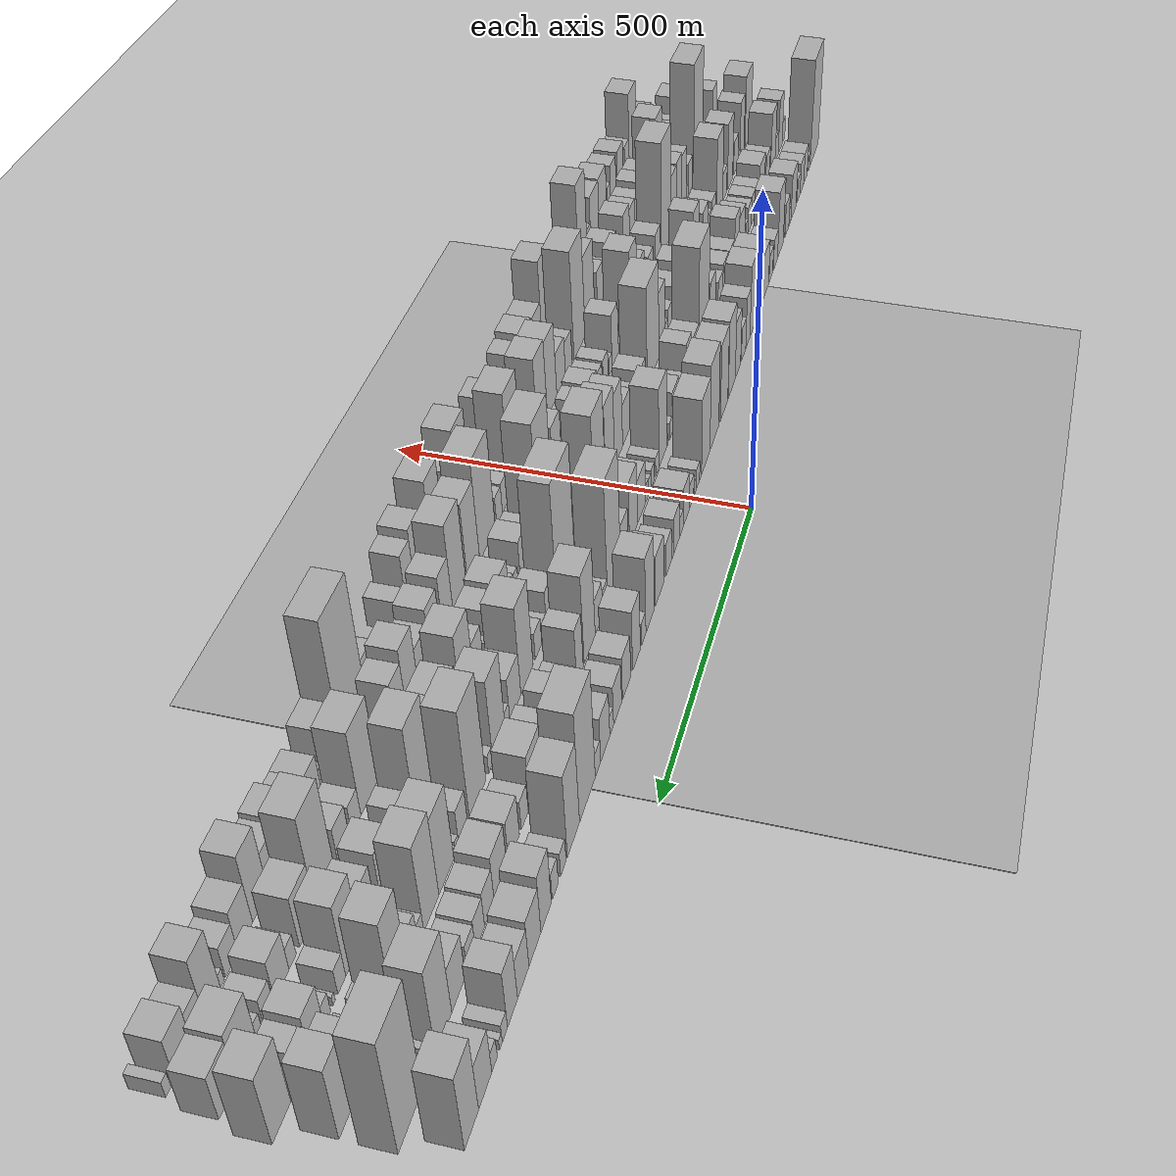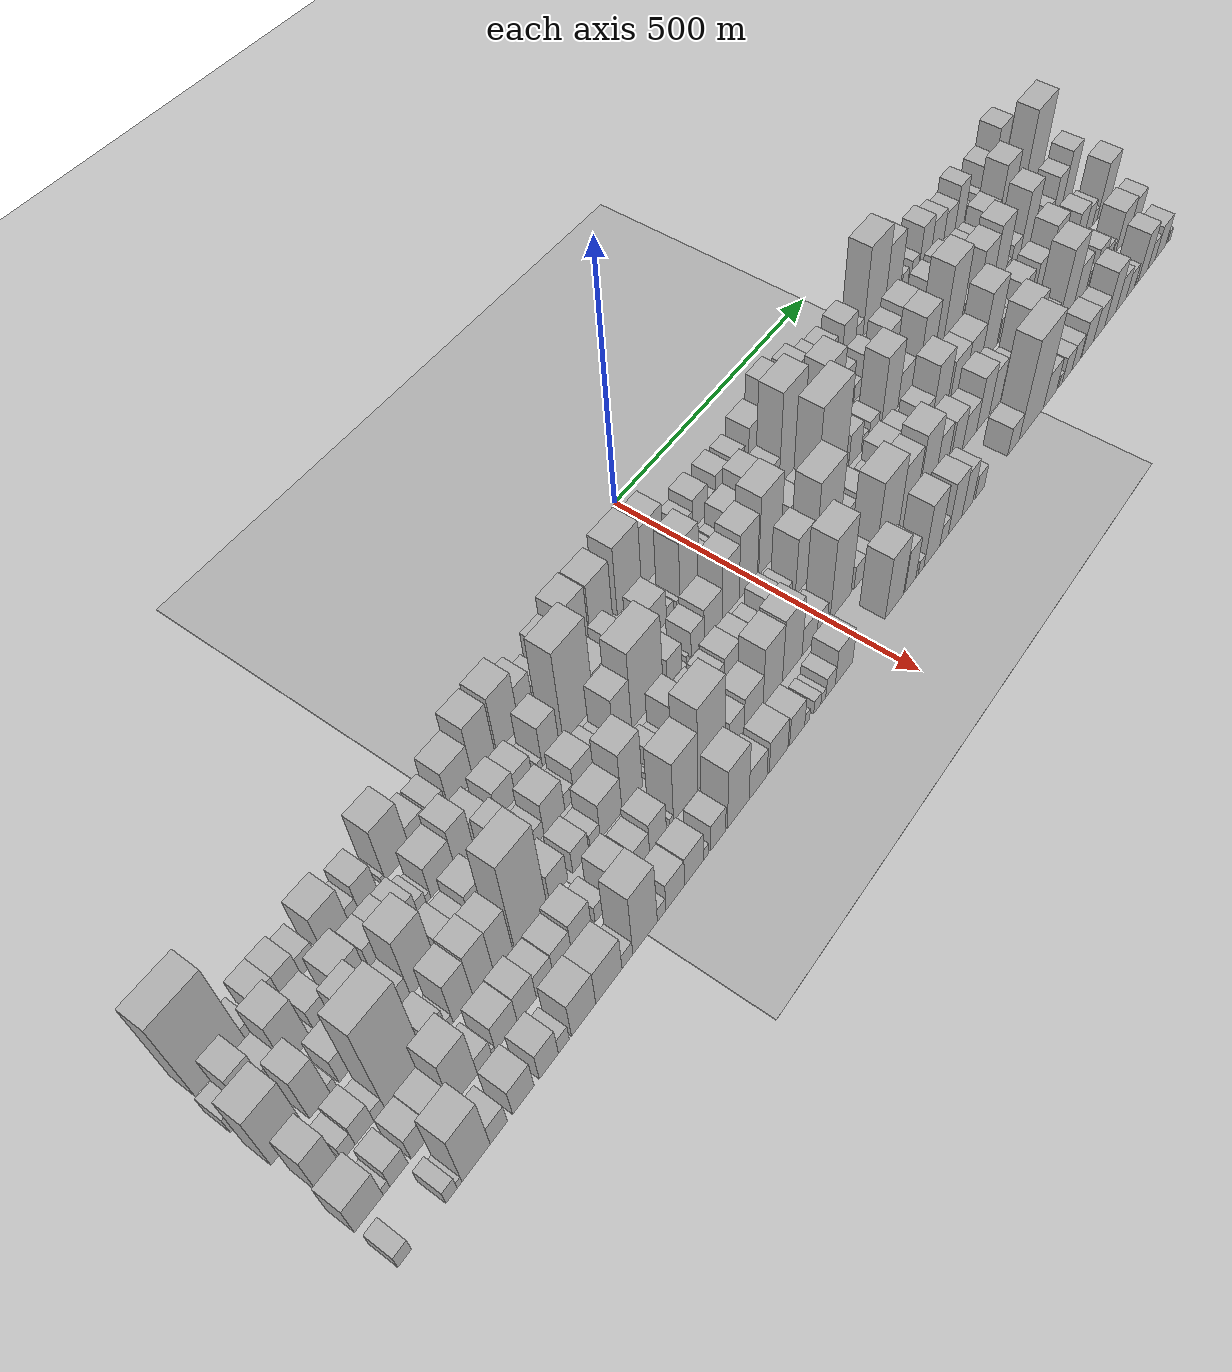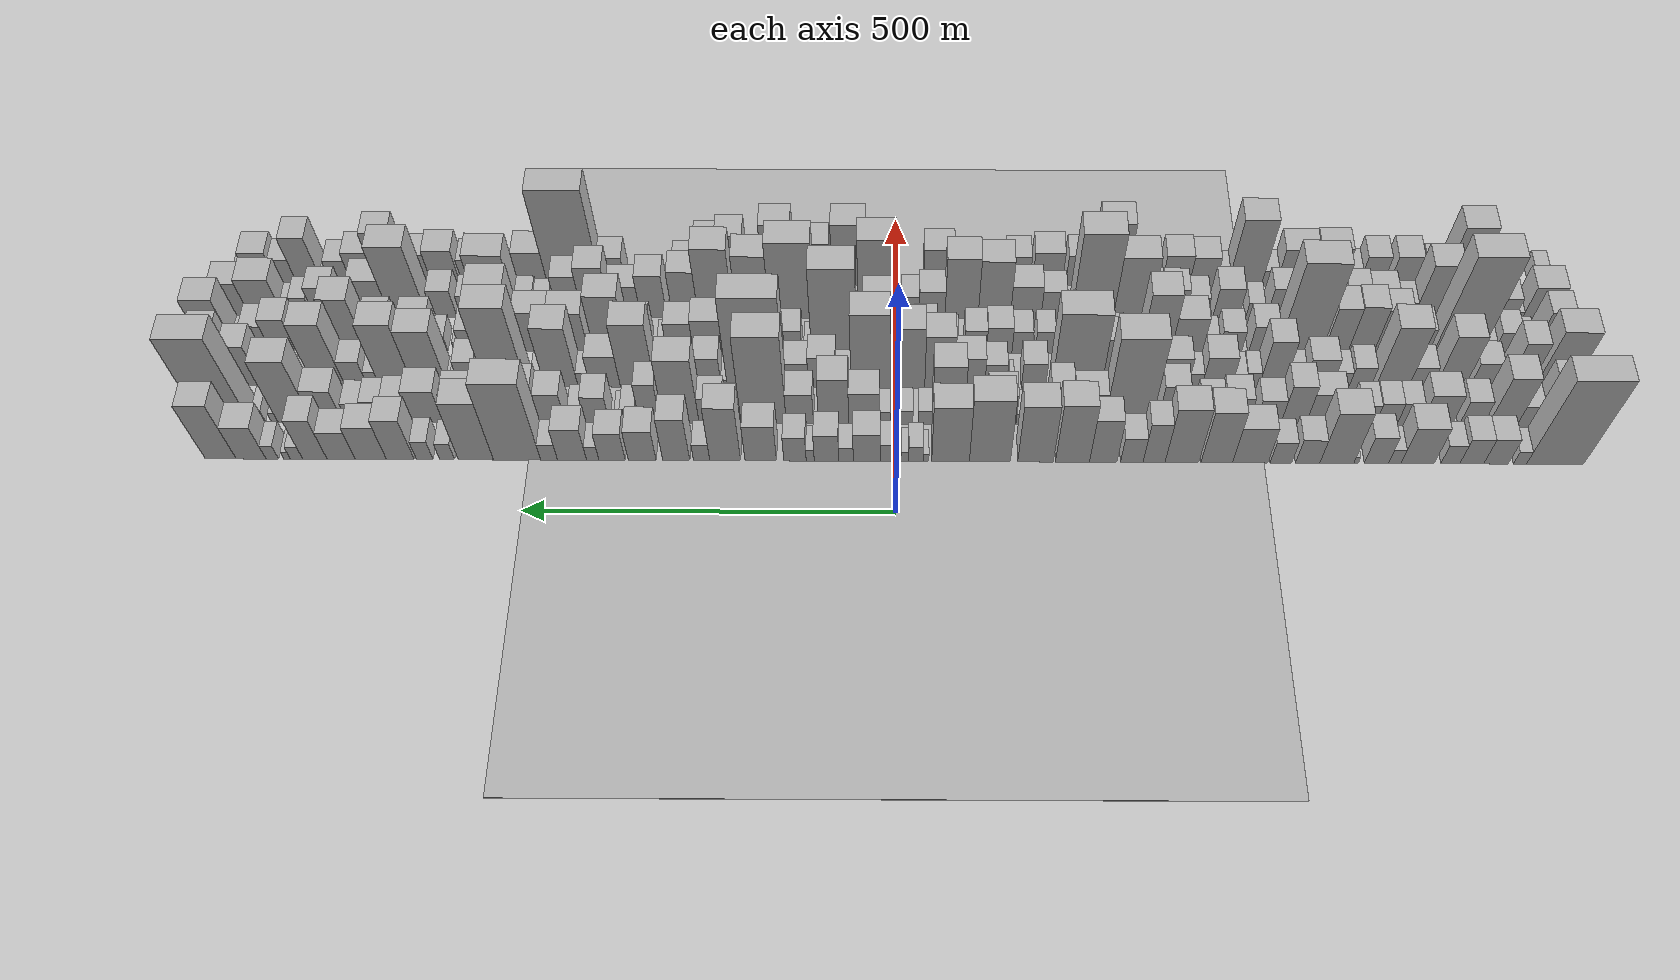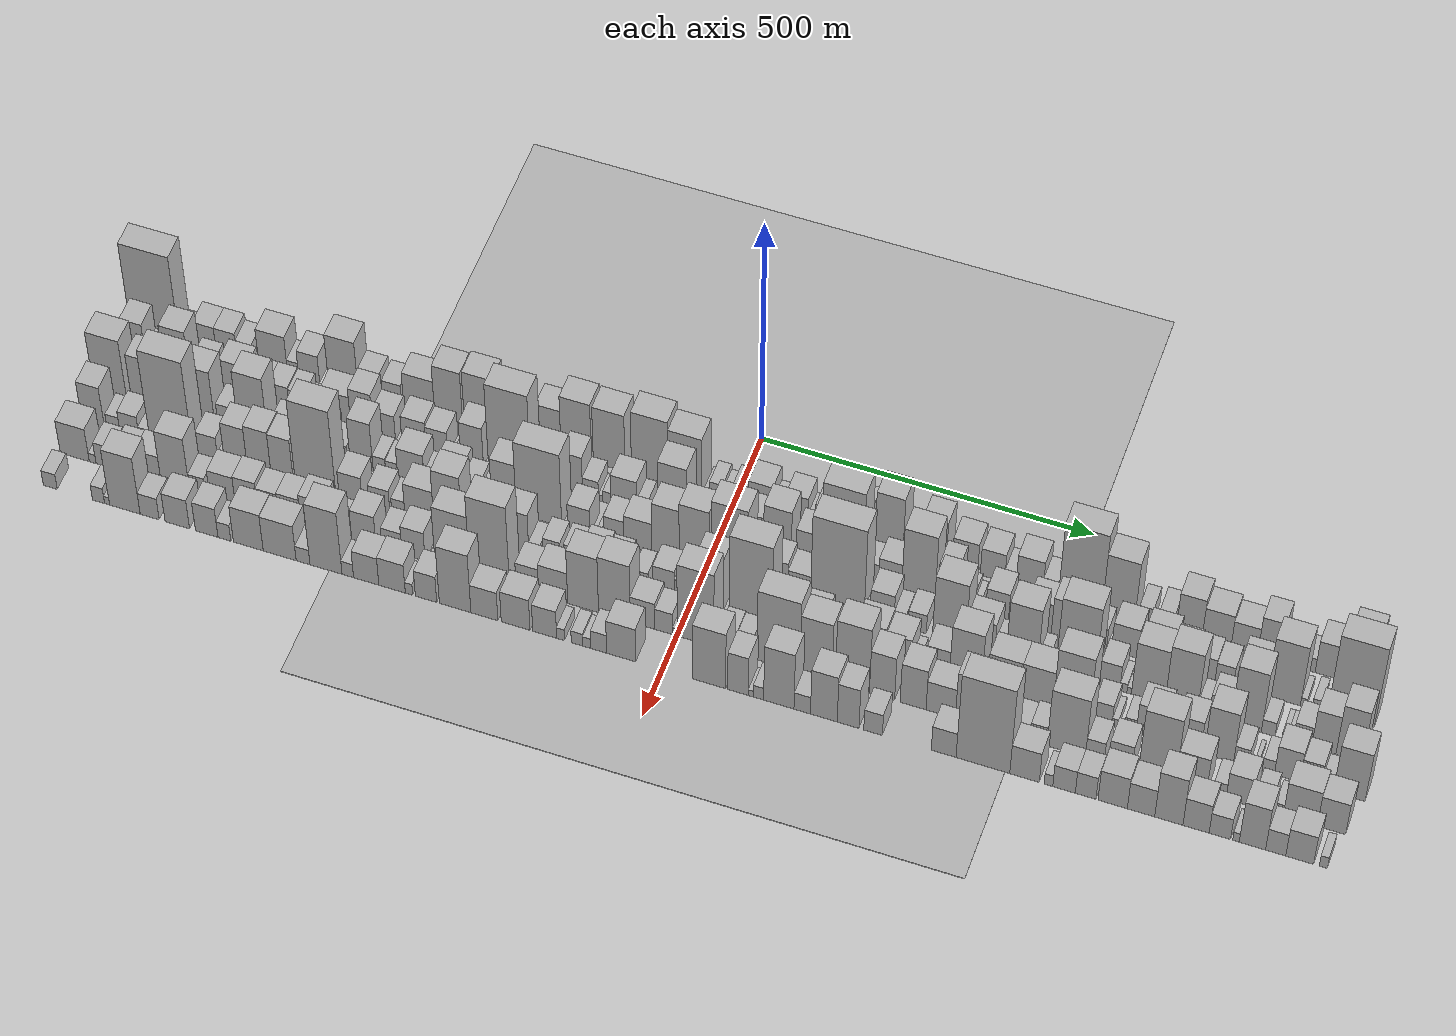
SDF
<?xml version="1.0" encoding="utf-8"?>

<sdf version="1.6">

   <world name="default">

      <gui fullscreen="0">

         <camera name="user_camera">

            <pose>-15 0 4.57585 0 0 0</pose>

            <view_controller>orbit</view_controller>

         </camera>

      </gui>

      <scene>

         <sky>

           <clouds>

             <speed>12</speed>

           </clouds>

         </sky>

         <ambient>0.4 0.4 0.4 1</ambient>

         <background>0.7 0.7 0.7 1</background>

         <shadows>1</shadows>

      </scene>

      <gravity>0 0 -9.8066</gravity>

      <magnetic_field>6e-06 2.3e-05 -4.2e-05</magnetic_field>

      <physics default="0" name="default_physics" type="ode">

         <ode>

            <solver>

               <type>quick</type>

               <iters>10</iters>

               <sor>1.0</sor>

               <use_dynamic_moi_rescaling>0</use_dynamic_moi_rescaling>

            </solver>

            <constraints>

               <cfm>0</cfm>

               <erp>0.2</erp>

               <contact_max_correcting_vel>100</contact_max_correcting_vel>

               <contact_surface_layer>0.001</contact_surface_layer>

            </constraints>

         </ode>

         <max_step_size>0.004</max_step_size>

         <real_time_factor>1</real_time_factor>

         <real_time_update_rate>250</real_time_update_rate>

      </physics>

      <light name="sun" type="directional">

         <cast_shadows>1</cast_shadows>

         <pose>0 0 10 0 0 0</pose>

         <diffuse>0.8 0.8 0.8 1</diffuse>

         <specular>0.2 0.2 0.2 1</specular>

         <attenuation>

            <range>1000</range>

            <constant>0.9</constant>

            <linear>0.01</linear>

            <quadratic>0.001</quadratic>

         </attenuation>

         <direction>-0.5 0.1 -0.9</direction>

      </light>

      <include>

         <name>ground_plane_1</name>

         <uri>model://HANNAS_ground_plane</uri>

         <pose>0 0 0  0 0 0</pose>

      </include>

      <include>

         <name>ground_plane_2</name>

         <uri>model://HANNAS_ground_plane</uri>

         <pose>100 0 0  0 0 0</pose>

      </include>

      <model name="building_1">

         <static>1</static>

         <pose frame="">100.0000 -895.2777 0 0.000000 0.000000 0.000000</pose>

         <link name="link">

            <pose frame="">0 0 100.50 0 0 0</pose>

            <collision name="collision">

               <geometry>

                  <box>

                     <size>40.0000 77.4446 201.0000</size>

                  </box>

               </geometry>

               <max_contacts>10</max_contacts>

               <surface>

                  <contact>

                     <ode/>

                  </contact>

                  <bounce/>

                  <friction>

                     <torsional>

                        <ode/>

                     </torsional>

                     <ode/>

                  </friction>

               </surface>

            </collision>

            <visual name="visual">

               <cast_shadows>0</cast_shadows>

               <geometry>

                  <box>

                     <size>40.0000 77.4446 201.0000</size>

                  </box>

               </geometry>

               <material>

                  <script>

                     <uri>model://HANNAS_wall/materials/scripts</uri>

                     <uri>model://HANNAS_wall/materials/textures</uri>

                     <name>vrc/HANNAS_wall</name>

                  </script>

               </material>

            </visual>

            <self_collide>0</self_collide>

            <enable_wind>0</enable_wind>

            <kinematic>0</kinematic>

         </link>

      </model>

      <model name="building_2">

         <static>1</static>

         <pose frame="">100.0000 -847.5841 0 0.000000 0.000000 0.000000</pose>

         <link name="link">

            <pose frame="">0 0 15.00 0 0 0</pose>

            <collision name="collision">

               <geometry>

                  <box>

                     <size>40.0000 17.9428 30.0000</size>

                  </box>

               </geometry>

               <max_contacts>10</max_contacts>

               <surface>

                  <contact>

                     <ode/>

                  </contact>

                  <bounce/>

                  <friction>

                     <torsional>

                        <ode/>

                     </torsional>

                     <ode/>

                  </friction>

               </surface>

            </collision>

            <visual name="visual">

               <cast_shadows>0</cast_shadows>

               <geometry>

                  <box>

                     <size>40.0000 17.9428 30.0000</size>

                  </box>

               </geometry>

               <material>

                  <script>

                     <uri>model://HANNAS_wall/materials/scripts</uri>

                     <uri>model://HANNAS_wall/materials/textures</uri>

                     <name>vrc/HANNAS_wall</name>

                  </script>

               </material>

            </visual>

            <self_collide>0</self_collide>

            <enable_wind>0</enable_wind>

            <kinematic>0</kinematic>

         </link>

      </model>

      <model name="building_3">

         <static>1</static>

         <pose frame="">100.0000 -814.9615 0 0.000000 0.000000 0.000000</pose>

         <link name="link">

            <pose frame="">0 0 30.00 0 0 0</pose>

            <collision name="collision">

               <geometry>

                  <box>

                     <size>40.0000 33.3025 60.0000</size>

                  </box>

               </geometry>

               <max_contacts>10</max_contacts>

               <surface>

                  <contact>

                     <ode/>

                  </contact>

                  <bounce/>

                  <friction>

                     <torsional>

                        <ode/>

                     </torsional>

                     <ode/>

                  </friction>

               </surface>

            </collision>

            <visual name="visual">

               <cast_shadows>0</cast_shadows>

               <geometry>

                  <box>

                     <size>40.0000 33.3025 60.0000</size>

                  </box>

               </geometry>

               <material>

                  <script>

                     <uri>model://HANNAS_wall/materials/scripts</uri>

                     <uri>model://HANNAS_wall/materials/textures</uri>

                     <name>vrc/HANNAS_wall</name>

                  </script>

               </material>

            </visual>

            <self_collide>0</self_collide>

            <enable_wind>0</enable_wind>

            <kinematic>0</kinematic>

         </link>

      </model>

      <model name="building_4">

         <static>1</static>

         <pose frame="">100.0000 -782.0932 0 0.000000 0.000000 0.000000</pose>

         <link name="link">

            <pose frame="">0 0 30.00 0 0 0</pose>

            <collision name="collision">

               <geometry>

                  <box>

                     <size>40.0000 32.4341 60.0000</size>

                  </box>

               </geometry>

               <max_contacts>10</max_contacts>

               <surface>

                  <contact>

                     <ode/>

                  </contact>

                  <bounce/>

                  <friction>

                     <torsional>

                        <ode/>

                     </torsional>

                     <ode/>

                  </friction>

               </surface>

            </collision>

            <visual name="visual">

               <cast_shadows>0</cast_shadows>

               <geometry>

                  <box>

                     <size>40.0000 32.4341 60.0000</size>

                  </box>

               </geometry>

               <material>

                  <script>

                     <uri>model://HANNAS_wall/materials/scripts</uri>

                     <uri>model://HANNAS_wall/materials/textures</uri>

                     <name>vrc/HANNAS_wall</name>

                  </script>

               </material>

            </visual>

            <self_collide>0</self_collide>

            <enable_wind>0</enable_wind>

            <kinematic>0</kinematic>

         </link>

      </model>

      <model name="building_5">

         <static>1</static>

         <pose frame="">100.0000 -752.9953 0 0.000000 0.000000 0.000000</pose>

         <link name="link">

            <pose frame="">0 0 22.50 0 0 0</pose>

            <collision name="collision">

               <geometry>

                  <box>

                     <size>40.0000 25.7616 45.0000</size>

                  </box>

               </geometry>

               <max_contacts>10</max_contacts>

               <surface>

                  <contact>

                     <ode/>

                  </contact>

                  <bounce/>

                  <friction>

                     <torsional>

                        <ode/>

                     </torsional>

                     <ode/>

                  </friction>

               </surface>

            </collision>

            <visual name="visual">

               <cast_shadows>0</cast_shadows>

               <geometry>

                  <box>

                     <size>40.0000 25.7616 45.0000</size>

                  </box>

               </geometry>

               <material>

                  <script>

                     <uri>model://HANNAS_wall/materials/scripts</uri>

                     <uri>model://HANNAS_wall/materials/textures</uri>

                     <name>vrc/HANNAS_wall</name>

                  </script>

               </material>

            </visual>

            <self_collide>0</self_collide>

            <enable_wind>0</enable_wind>

            <kinematic>0</kinematic>

         </link>

      </model>

      <model name="building_6">

         <static>1</static>

         <pose frame="">100.0000 -708.6702 0 0.000000 0.000000 0.000000</pose>

         <link name="link">

            <pose frame="">0 0 43.50 0 0 0</pose>

            <collision name="collision">

               <geometry>

                  <box>

                     <size>40.0000 44.8886 87.0000</size>

                  </box>

               </geometry>

               <max_contacts>10</max_contacts>

               <surface>

                  <contact>

                     <ode/>

                  </contact>

                  <bounce/>

                  <friction>

                     <torsional>

                        <ode/>

                     </torsional>

                     <ode/>

                  </friction>

               </surface>

            </collision>

            <visual name="visual">

               <cast_shadows>0</cast_shadows>

               <geometry>

                  <box>

                     <size>40.0000 44.8886 87.0000</size>

                  </box>

               </geometry>

               <material>

                  <script>

                     <uri>model://HANNAS_wall/materials/scripts</uri>

                     <uri>model://HANNAS_wall/materials/textures</uri>

                     <name>vrc/HANNAS_wall</name>

                  </script>

               </material>

            </visual>

            <self_collide>0</self_collide>

            <enable_wind>0</enable_wind>

            <kinematic>0</kinematic>

         </link>

      </model>

      <model name="building_7">

         <static>1</static>

         <pose frame="">100.0000 -677.5483 0 0.000000 0.000000 0.000000</pose>

         <link name="link">

            <pose frame="">0 0 16.50 0 0 0</pose>

            <collision name="collision">

               <geometry>

                  <box>

                     <size>40.0000 17.3553 33.0000</size>

                  </box>

               </geometry>

               <max_contacts>10</max_contacts>

               <surface>

                  <contact>

                     <ode/>

                  </contact>

                  <bounce/>

                  <friction>

                     <torsional>

                        <ode/>

                     </torsional>

                     <ode/>

                  </friction>

               </surface>

            </collision>

            <visual name="visual">

               <cast_shadows>0</cast_shadows>

               <geometry>

                  <box>

                     <size>40.0000 17.3553 33.0000</size>

                  </box>

               </geometry>

               <material>

                  <script>

                     <uri>model://HANNAS_wall/materials/scripts</uri>

                     <uri>model://HANNAS_wall/materials/textures</uri>

                     <name>vrc/HANNAS_wall</name>

                  </script>

               </material>

            </visual>

            <self_collide>0</self_collide>

            <enable_wind>0</enable_wind>

            <kinematic>0</kinematic>

         </link>

      </model>

      <model name="building_8">

         <static>1</static>

         <pose frame="">100.0000 -652.5049 0 0.000000 0.000000 0.000000</pose>

         <link name="link">

            <pose frame="">0 0 31.50 0 0 0</pose>

            <collision name="collision">

               <geometry>

                  <box>

                     <size>40.0000 32.7315 63.0000</size>

                  </box>

               </geometry>

               <max_contacts>10</max_contacts>

               <surface>

                  <contact>

                     <ode/>

                  </contact>

                  <bounce/>

                  <friction>

                     <torsional>

                        <ode/>

                     </torsional>

                     <ode/>

                  </friction>

               </surface>

            </collision>

            <visual name="visual">

               <cast_shadows>0</cast_shadows>

               <geometry>

                  <box>

                     <size>40.0000 32.7315 63.0000</size>

                  </box>

               </geometry>

               <material>

                  <script>

                     <uri>model://HANNAS_wall/materials/scripts</uri>

                     <uri>model://HANNAS_wall/materials/textures</uri>

                     <name>vrc/HANNAS_wall</name>

                  </script>

               </material>

            </visual>

            <self_collide>0</self_collide>

            <enable_wind>0</enable_wind>

            <kinematic>0</kinematic>

         </link>

      </model>

      <model name="building_9">

         <static>1</static>

         <pose frame="">100.0000 -625.0468 0 0.000000 0.000000 0.000000</pose>

         <link name="link">

            <pose frame="">0 0 7.50 0 0 0</pose>

            <collision name="collision">

               <geometry>

                  <box>

                     <size>40.0000 6.1847 15.0000</size>

                  </box>

               </geometry>

               <max_contacts>10</max_contacts>

               <surface>

                  <contact>

                     <ode/>

                  </contact>

                  <bounce/>

                  <friction>

                     <torsional>

                        <ode/>

                     </torsional>

                     <ode/>

                  </friction>

               </surface>

            </collision>

            <visual name="visual">

               <cast_shadows>0</cast_shadows>

               <geometry>

                  <box>

                     <size>40.0000 6.1847 15.0000</size>

                  </box>

               </geometry>

               <material>

                  <script>

                     <uri>model://HANNAS_wall/materials/scripts</uri>

                     <uri>model://HANNAS_wall/materials/textures</uri>

                     <name>vrc/HANNAS_wall</name>

                  </script>

               </material>

            </visual>

            <self_collide>0</self_collide>

            <enable_wind>0</enable_wind>

            <kinematic>0</kinematic>

         </link>

      </model>

      <model name="building_10">

         <static>1</static>

         <pose frame="">100.0000 -598.8502 0 0.000000 0.000000 0.000000</pose>

         <link name="link">

            <pose frame="">0 0 61.50 0 0 0</pose>

            <collision name="collision">

               <geometry>

                  <box>

                     <size>40.0000 46.2086 123.0000</size>

                  </box>

               </geometry>

               <max_contacts>10</max_contacts>

               <surface>

                  <contact>

                     <ode/>

                  </contact>

                  <bounce/>

                  <friction>

                     <torsional>

                        <ode/>

                     </torsional>

                     <ode/>

                  </friction>

               </surface>

            </collision>

            <visual name="visual">

               <cast_shadows>0</cast_shadows>

               <geometry>

                  <box>

                     <size>40.0000 46.2086 123.0000</size>

                  </box>

               </geometry>

               <material>

                  <script>

                     <uri>model://HANNAS_wall/materials/scripts</uri>

                     <uri>model://HANNAS_wall/materials/textures</uri>

                     <name>vrc/HANNAS_wall</name>

                  </script>

               </material>

            </visual>

            <self_collide>0</self_collide>

            <enable_wind>0</enable_wind>

            <kinematic>0</kinematic>

         </link>

      </model>

      <model name="building_11">

         <static>1</static>

         <pose frame="">100.0000 -559.1597 0 0.000000 0.000000 0.000000</pose>

         <link name="link">

            <pose frame="">0 0 28.50 0 0 0</pose>

            <collision name="collision">

               <geometry>

                  <box>

                     <size>40.0000 33.1722 57.0000</size>

                  </box>

               </geometry>

               <max_contacts>10</max_contacts>

               <surface>

                  <contact>

                     <ode/>

                  </contact>

                  <bounce/>

                  <friction>

                     <torsional>

                        <ode/>

                     </torsional>

                     <ode/>

                  </friction>

               </surface>

            </collision>

            <visual name="visual">

               <cast_shadows>0</cast_shadows>

               <geometry>

                  <box>

                     <size>40.0000 33.1722 57.0000</size>

                  </box>

               </geometry>

               <material>

                  <script>

                     <uri>model://HANNAS_wall/materials/scripts</uri>

                     <uri>model://HANNAS_wall/materials/textures</uri>

                     <name>vrc/HANNAS_wall</name>

                  </script>

               </material>

            </visual>

            <self_collide>0</self_collide>

            <enable_wind>0</enable_wind>

            <kinematic>0</kinematic>

         </link>

      </model>

      <model name="building_12">

         <static>1</static>

         <pose frame="">100.0000 -522.8531 0 0.000000 0.000000 0.000000</pose>

         <link name="link">

            <pose frame="">0 0 25.50 0 0 0</pose>

            <collision name="collision">

               <geometry>

                  <box>

                     <size>40.0000 29.4410 51.0000</size>

                  </box>

               </geometry>

               <max_contacts>10</max_contacts>

               <surface>

                  <contact>

                     <ode/>

                  </contact>

                  <bounce/>

                  <friction>

                     <torsional>

                        <ode/>

                     </torsional>

                     <ode/>

                  </friction>

               </surface>

            </collision>

            <visual name="visual">

               <cast_shadows>0</cast_shadows>

               <geometry>

                  <box>

                     <size>40.0000 29.4410 51.0000</size>

                  </box>

               </geometry>

               <material>

                  <script>

                     <uri>model://HANNAS_wall/materials/scripts</uri>

                     <uri>model://HANNAS_wall/materials/textures</uri>

                     <name>vrc/HANNAS_wall</name>

                  </script>

               </material>

            </visual>

            <self_collide>0</self_collide>

            <enable_wind>0</enable_wind>

            <kinematic>0</kinematic>

         </link>

      </model>

      <model name="building_13">

         <static>1</static>

         <pose frame="">100.0000 -481.1601 0 0.000000 0.000000 0.000000</pose>

         <link name="link">

            <pose frame="">0 0 42.00 0 0 0</pose>

            <collision name="collision">

               <geometry>

                  <box>

                     <size>40.0000 47.9450 84.0000</size>

                  </box>

               </geometry>

               <max_contacts>10</max_contacts>

               <surface>

                  <contact>

                     <ode/>

                  </contact>

                  <bounce/>

                  <friction>

                     <torsional>

                        <ode/>

                     </torsional>

                     <ode/>

                  </friction>

               </surface>

            </collision>

            <visual name="visual">

               <cast_shadows>0</cast_shadows>

               <geometry>

                  <box>

                     <size>40.0000 47.9450 84.0000</size>

                  </box>

               </geometry>

               <material>

                  <script>

                     <uri>model://HANNAS_wall/materials/scripts</uri>

                     <uri>model://HANNAS_wall/materials/textures</uri>

                     <name>vrc/HANNAS_wall</name>

                  </script>

               </material>

            </visual>

            <self_collide>0</self_collide>

            <enable_wind>0</enable_wind>

            <kinematic>0</kinematic>

         </link>

      </model>

      <model name="building_14">

         <static>1</static>

         <pose frame="">100.0000 -435.6512 0 0.000000 0.000000 0.000000</pose>

         <link name="link">

            <pose frame="">0 0 61.50 0 0 0</pose>

            <collision name="collision">

               <geometry>

                  <box>

                     <size>40.0000 43.0728 123.0000</size>

                  </box>

               </geometry>

               <max_contacts>10</max_contacts>

               <surface>

                  <contact>

                     <ode/>

                  </contact>

                  <bounce/>

                  <friction>

                     <torsional>

                        <ode/>

                     </torsional>

                     <ode/>

                  </friction>

               </surface>

            </collision>

            <visual name="visual">

               <cast_shadows>0</cast_shadows>

               <geometry>

                  <box>

                     <size>40.0000 43.0728 123.0000</size>

                  </box>

               </geometry>

               <material>

                  <script>

                     <uri>model://HANNAS_wall/materials/scripts</uri>

                     <uri>model://HANNAS_wall/materials/textures</uri>

                     <name>vrc/HANNAS_wall</name>

                  </script>

               </material>

            </visual>

            <self_collide>0</self_collide>

            <enable_wind>0</enable_wind>

            <kinematic>0</kinematic>

         </link>

      </model>

      <model name="building_15">

         <static>1</static>

         <pose frame="">100.0000 -388.2523 0 0.000000 0.000000 0.000000</pose>

         <link name="link">

            <pose frame="">0 0 64.50 0 0 0</pose>

            <collision name="collision">

               <geometry>

                  <box>

                     <size>40.0000 45.7249 129.0000</size>

                  </box>

               </geometry>

               <max_contacts>10</max_contacts>

               <surface>

                  <contact>

                     <ode/>

                  </contact>

                  <bounce/>

                  <friction>

                     <torsional>

                        <ode/>

                     </torsional>

                     <ode/>

                  </friction>

               </surface>

            </collision>

            <visual name="visual">

               <cast_shadows>0</cast_shadows>

               <geometry>

                  <box>

                     <size>40.0000 45.7249 129.0000</size>

                  </box>

               </geometry>

               <material>

                  <script>

                     <uri>model://HANNAS_wall/materials/scripts</uri>

                     <uri>model://HANNAS_wall/materials/textures</uri>

                     <name>vrc/HANNAS_wall</name>

                  </script>

               </material>

            </visual>

            <self_collide>0</self_collide>

            <enable_wind>0</enable_wind>

            <kinematic>0</kinematic>

         </link>

      </model>

      <model name="building_16">

         <static>1</static>

         <pose frame="">100.0000 -350.4406 0 0.000000 0.000000 0.000000</pose>

         <link name="link">

            <pose frame="">0 0 46.50 0 0 0</pose>

            <collision name="collision">

               <geometry>

                  <box>

                     <size>40.0000 29.8985 93.0000</size>

                  </box>

               </geometry>

               <max_contacts>10</max_contacts>

               <surface>

                  <contact>

                     <ode/>

                  </contact>

                  <bounce/>

                  <friction>

                     <torsional>

                        <ode/>

                     </torsional>

                     <ode/>

                  </friction>

               </surface>

            </collision>

            <visual name="visual">

               <cast_shadows>0</cast_shadows>

               <geometry>

                  <box>

                     <size>40.0000 29.8985 93.0000</size>

                  </box>

               </geometry>

               <material>

                  <script>

                     <uri>model://HANNAS_wall/materials/scripts</uri>

                     <uri>model://HANNAS_wall/materials/textures</uri>

                     <name>vrc/HANNAS_wall</name>

                  </script>

               </material>

            </visual>

            <self_collide>0</self_collide>

            <enable_wind>0</enable_wind>

            <kinematic>0</kinematic>

         </link>

      </model>

      <model name="building_17">

         <static>1</static>

         <pose frame="">100.0000 -320.1890 0 0.000000 0.000000 0.000000</pose>

         <link name="link">

            <pose frame="">0 0 30.00 0 0 0</pose>

            <collision name="collision">

               <geometry>

                  <box>

                     <size>40.0000 30.6047 60.0000</size>

                  </box>

               </geometry>

               <max_contacts>10</max_contacts>

               <surface>

                  <contact>

                     <ode/>

                  </contact>

                  <bounce/>

                  <friction>

                     <torsional>

                        <ode/>

                     </torsional>

                     <ode/>

                  </friction>

               </surface>

            </collision>

            <visual name="visual">

               <cast_shadows>0</cast_shadows>

               <geometry>

                  <box>

                     <size>40.0000 30.6047 60.0000</size>

                  </box>

               </geometry>

               <material>

                  <script>

                     <uri>model://HANNAS_wall/materials/scripts</uri>

                     <uri>model://HANNAS_wall/materials/textures</uri>

                     <name>vrc/HANNAS_wall</name>

                  </script>

               </material>

            </visual>

            <self_collide>0</self_collide>

            <enable_wind>0</enable_wind>

            <kinematic>0</kinematic>

         </link>

      </model>

      <model name="building_18">

         <static>1</static>

         <pose frame="">100.0000 -281.3210 0 0.000000 0.000000 0.000000</pose>

         <link name="link">

            <pose frame="">0 0 51.00 0 0 0</pose>

            <collision name="collision">

               <geometry>

                  <box>

                     <size>40.0000 37.1313 102.0000</size>

                  </box>

               </geometry>

               <max_contacts>10</max_contacts>

               <surface>

                  <contact>

                     <ode/>

                  </contact>

                  <bounce/>

                  <friction>

                     <torsional>

                        <ode/>

                     </torsional>

                     <ode/>

                  </friction>

               </surface>

            </collision>

            <visual name="visual">

               <cast_shadows>0</cast_shadows>

               <geometry>

                  <box>

                     <size>40.0000 37.1313 102.0000</size>

                  </box>

               </geometry>

               <material>

                  <script>

                     <uri>model://HANNAS_wall/materials/scripts</uri>

                     <uri>model://HANNAS_wall/materials/textures</uri>

                     <name>vrc/HANNAS_wall</name>

                  </script>

               </material>

            </visual>

            <self_collide>0</self_collide>

            <enable_wind>0</enable_wind>

            <kinematic>0</kinematic>

         </link>

      </model>

      <model name="building_19">

         <static>1</static>

         <pose frame="">100.0000 -239.6339 0 0.000000 0.000000 0.000000</pose>

         <link name="link">

            <pose frame="">0 0 69.00 0 0 0</pose>

            <collision name="collision">

               <geometry>

                  <box>

                     <size>40.0000 46.2429 138.0000</size>

                  </box>

               </geometry>

               <max_contacts>10</max_contacts>

               <surface>

                  <contact>

                     <ode/>

                  </contact>

                  <bounce/>

                  <friction>

                     <torsional>

                        <ode/>

                     </torsional>

                     <ode/>

                  </friction>

               </surface>

            </collision>

            <visual name="visual">

               <cast_shadows>0</cast_shadows>

               <geometry>

                  <box>

                     <size>40.0000 46.2429 138.0000</size>

                  </box>

               </geometry>

               <material>

                  <script>

                     <uri>model://HANNAS_wall/materials/scripts</uri>

                     <uri>model://HANNAS_wall/materials/textures</uri>

                     <name>vrc/HANNAS_wall</name>

                  </script>

               </material>

            </visual>

            <self_collide>0</self_collide>

            <enable_wind>0</enable_wind>

            <kinematic>0</kinematic>

         </link>

      </model>

      <model name="building_20">

         <static>1</static>

         <pose frame="">100.0000 -189.3822 0 0.000000 0.000000 0.000000</pose>

         <link name="link">

            <pose frame="">0 0 67.50 0 0 0</pose>

            <collision name="collision">

               <geometry>

                  <box>

                     <size>40.0000 48.2603 135.0000</size>

                  </box>

               </geometry>

               <max_contacts>10</max_contacts>

               <surface>

                  <contact>

                     <ode/>

                  </contact>

                  <bounce/>

                  <friction>

                     <torsional>

                        <ode/>

                     </torsional>

                     <ode/>

                  </friction>

               </surface>

            </collision>

            <visual name="visual">

               <cast_shadows>0</cast_shadows>

               <geometry>

                  <box>

                     <size>40.0000 48.2603 135.0000</size>

                  </box>

               </geometry>

               <material>

                  <script>

                     <uri>model://HANNAS_wall/materials/scripts</uri>

                     <uri>model://HANNAS_wall/materials/textures</uri>

                     <name>vrc/HANNAS_wall</name>

                  </script>

               </material>

            </visual>

            <self_collide>0</self_collide>

            <enable_wind>0</enable_wind>

            <kinematic>0</kinematic>

         </link>

      </model>

      <model name="building_21">

         <static>1</static>

         <pose frame="">100.0000 -127.4191 0 0.000000 0.000000 0.000000</pose>

         <link name="link">

            <pose frame="">0 0 75.00 0 0 0</pose>

            <collision name="collision">

               <geometry>

                  <box>

                     <size>40.0000 55.6660 150.0000</size>

                  </box>

               </geometry>

               <max_contacts>10</max_contacts>

               <surface>

                  <contact>

                     <ode/>

                  </contact>

                  <bounce/>

                  <friction>

                     <torsional>

                        <ode/>

                     </torsional>

                     <ode/>

                  </friction>

               </surface>

            </collision>

            <visual name="visual">

               <cast_shadows>0</cast_shadows>

               <geometry>

                  <box>

                     <size>40.0000 55.6660 150.0000</size>

                  </box>

               </geometry>

               <material>

                  <script>

                     <uri>model://HANNAS_wall/materials/scripts</uri>

                     <uri>model://HANNAS_wall/materials/textures</uri>

                     <name>vrc/HANNAS_wall</name>

                  </script>

               </material>

            </visual>

            <self_collide>0</self_collide>

            <enable_wind>0</enable_wind>

            <kinematic>0</kinematic>

         </link>

      </model>

      <model name="building_22">

         <static>1</static>

         <pose frame="">100.0000 -73.9575 0 0.000000 0.000000 0.000000</pose>

         <link name="link">

            <pose frame="">0 0 66.00 0 0 0</pose>

            <collision name="collision">

               <geometry>

                  <box>

                     <size>40.0000 51.2572 132.0000</size>

                  </box>

               </geometry>

               <max_contacts>10</max_contacts>

               <surface>

                  <contact>

                     <ode/>

                  </contact>

                  <bounce/>

                  <friction>

                     <torsional>

                        <ode/>

                     </torsional>

                     <ode/>

                  </friction>

               </surface>

            </collision>

            <visual name="visual">

               <cast_shadows>0</cast_shadows>

               <geometry>

                  <box>

                     <size>40.0000 51.2572 132.0000</size>

                  </box>

               </geometry>

               <material>

                  <script>

                     <uri>model://HANNAS_wall/materials/scripts</uri>

                     <uri>model://HANNAS_wall/materials/textures</uri>

                     <name>vrc/HANNAS_wall</name>

                  </script>

               </material>

            </visual>

            <self_collide>0</self_collide>

            <enable_wind>0</enable_wind>

            <kinematic>0</kinematic>

         </link>

      </model>

      <model name="building_23">

         <static>1</static>

         <pose frame="">100.0000 -40.5875 0 0.000000 0.000000 0.000000</pose>

         <link name="link">

            <pose frame="">0 0 9.00 0 0 0</pose>

            <collision name="collision">

               <geometry>

                  <box>

                     <size>40.0000 7.4829 18.0000</size>

                  </box>

               </geometry>

               <max_contacts>10</max_contacts>

               <surface>

                  <contact>

                     <ode/>

                  </contact>

                  <bounce/>

                  <friction>

                     <torsional>

                        <ode/>

                     </torsional>

                     <ode/>

                  </friction>

               </surface>

            </collision>

            <visual name="visual">

               <cast_shadows>0</cast_shadows>

               <geometry>

                  <box>

                     <size>40.0000 7.4829 18.0000</size>

                  </box>

               </geometry>

               <material>

                  <script>

                     <uri>model://HANNAS_wall/materials/scripts</uri>

                     <uri>model://HANNAS_wall/materials/textures</uri>

                     <name>vrc/HANNAS_wall</name>

                  </script>

               </material>

            </visual>

            <self_collide>0</self_collide>

            <enable_wind>0</enable_wind>

            <kinematic>0</kinematic>

         </link>

      </model>

      <model name="building_24">

         <static>1</static>

         <pose frame="">100.0000 -26.9328 0 0.000000 0.000000 0.000000</pose>

         <link name="link">

            <pose frame="">0 0 18.00 0 0 0</pose>

            <collision name="collision">

               <geometry>

                  <box>

                     <size>40.0000 19.8266 36.0000</size>

                  </box>

               </geometry>

               <max_contacts>10</max_contacts>

               <surface>

                  <contact>

                     <ode/>

                  </contact>

                  <bounce/>

                  <friction>

                     <torsional>

                        <ode/>

                     </torsional>

                     <ode/>

                  </friction>

               </surface>

            </collision>

            <visual name="visual">

               <cast_shadows>0</cast_shadows>

               <geometry>

                  <box>

                     <size>40.0000 19.8266 36.0000</size>

                  </box>

               </geometry>

               <material>

                  <script>

                     <uri>model://HANNAS_wall/materials/scripts</uri>

                     <uri>model://HANNAS_wall/materials/textures</uri>

                     <name>vrc/HANNAS_wall</name>

                  </script>

               </material>

            </visual>

            <self_collide>0</self_collide>

            <enable_wind>0</enable_wind>

            <kinematic>0</kinematic>

         </link>

      </model>

      <model name="building_25">

         <static>1</static>

         <pose frame="">100.0000 -11.7241 0 0.000000 0.000000 0.000000</pose>

         <link name="link">

            <pose frame="">0 0 12.00 0 0 0</pose>

            <collision name="collision">

               <geometry>

                  <box>

                     <size>40.0000 10.5908 24.0000</size>

                  </box>

               </geometry>

               <max_contacts>10</max_contacts>

               <surface>

                  <contact>

                     <ode/>

                  </contact>

                  <bounce/>

                  <friction>

                     <torsional>

                        <ode/>

                     </torsional>

                     <ode/>

                  </friction>

               </surface>

            </collision>

            <visual name="visual">

               <cast_shadows>0</cast_shadows>

               <geometry>

                  <box>

                     <size>40.0000 10.5908 24.0000</size>

                  </box>

               </geometry>

               <material>

                  <script>

                     <uri>model://HANNAS_wall/materials/scripts</uri>

                     <uri>model://HANNAS_wall/materials/textures</uri>

                     <name>vrc/HANNAS_wall</name>

                  </script>

               </material>

            </visual>

            <self_collide>0</self_collide>

            <enable_wind>0</enable_wind>

            <kinematic>0</kinematic>

         </link>

      </model>

      <model name="building_26">

         <static>1</static>

         <pose frame="">100.0000 9.6400 0 0.000000 0.000000 0.000000</pose>

         <link name="link">

            <pose frame="">0 0 21.00 0 0 0</pose>

            <collision name="collision">

               <geometry>

                  <box>

                     <size>40.0000 24.1373 42.0000</size>

                  </box>

               </geometry>

               <max_contacts>10</max_contacts>

               <surface>

                  <contact>

                     <ode/>

                  </contact>

                  <bounce/>

                  <friction>

                     <torsional>

                        <ode/>

                     </torsional>

                     <ode/>

                  </friction>

               </surface>

            </collision>

            <visual name="visual">

               <cast_shadows>0</cast_shadows>

               <geometry>

                  <box>

                     <size>40.0000 24.1373 42.0000</size>

                  </box>

               </geometry>

               <material>

                  <script>

                     <uri>model://HANNAS_wall/materials/scripts</uri>

                     <uri>model://HANNAS_wall/materials/textures</uri>

                     <name>vrc/HANNAS_wall</name>

                  </script>

               </material>

            </visual>

            <self_collide>0</self_collide>

            <enable_wind>0</enable_wind>

            <kinematic>0</kinematic>

         </link>

      </model>

      <model name="building_27">

         <static>1</static>

         <pose frame="">100.0000 39.9883 0 0.000000 0.000000 0.000000</pose>

         <link name="link">

            <pose frame="">0 0 33.00 0 0 0</pose>

            <collision name="collision">

               <geometry>

                  <box>

                     <size>40.0000 36.5592 66.0000</size>

                  </box>

               </geometry>

               <max_contacts>10</max_contacts>

               <surface>

                  <contact>

                     <ode/>

                  </contact>

                  <bounce/>

                  <friction>

                     <torsional>

                        <ode/>

                     </torsional>

                     <ode/>

                  </friction>

               </surface>

            </collision>

            <visual name="visual">

               <cast_shadows>0</cast_shadows>

               <geometry>

                  <box>

                     <size>40.0000 36.5592 66.0000</size>

                  </box>

               </geometry>

               <material>

                  <script>

                     <uri>model://HANNAS_wall/materials/scripts</uri>

                     <uri>model://HANNAS_wall/materials/textures</uri>

                     <name>vrc/HANNAS_wall</name>

                  </script>

               </material>

            </visual>

            <self_collide>0</self_collide>

            <enable_wind>0</enable_wind>

            <kinematic>0</kinematic>

         </link>

      </model>

      <model name="building_28">

         <static>1</static>

         <pose frame="">100.0000 68.1134 0 0.000000 0.000000 0.000000</pose>

         <link name="link">

            <pose frame="">0 0 16.50 0 0 0</pose>

            <collision name="collision">

               <geometry>

                  <box>

                     <size>40.0000 19.6911 33.0000</size>

                  </box>

               </geometry>

               <max_contacts>10</max_contacts>

               <surface>

                  <contact>

                     <ode/>

                  </contact>

                  <bounce/>

                  <friction>

                     <torsional>

                        <ode/>

                     </torsional>

                     <ode/>

                  </friction>

               </surface>

            </collision>

            <visual name="visual">

               <cast_shadows>0</cast_shadows>

               <geometry>

                  <box>

                     <size>40.0000 19.6911 33.0000</size>

                  </box>

               </geometry>

               <material>

                  <script>

                     <uri>model://HANNAS_wall/materials/scripts</uri>

                     <uri>model://HANNAS_wall/materials/textures</uri>

                     <name>vrc/HANNAS_wall</name>

                  </script>

               </material>

            </visual>

            <self_collide>0</self_collide>

            <enable_wind>0</enable_wind>

            <kinematic>0</kinematic>

         </link>

      </model>

      <model name="building_29">

         <static>1</static>

         <pose frame="">100.0000 94.6708 0 0.000000 0.000000 0.000000</pose>

         <link name="link">

            <pose frame="">0 0 31.50 0 0 0</pose>

            <collision name="collision">

               <geometry>

                  <box>

                     <size>40.0000 33.4237 63.0000</size>

                  </box>

               </geometry>

               <max_contacts>10</max_contacts>

               <surface>

                  <contact>

                     <ode/>

                  </contact>

                  <bounce/>

                  <friction>

                     <torsional>

                        <ode/>

                     </torsional>

                     <ode/>

                  </friction>

               </surface>

            </collision>

            <visual name="visual">

               <cast_shadows>0</cast_shadows>

               <geometry>

                  <box>

                     <size>40.0000 33.4237 63.0000</size>

                  </box>

               </geometry>

               <material>

                  <script>

                     <uri>model://HANNAS_wall/materials/scripts</uri>

                     <uri>model://HANNAS_wall/materials/textures</uri>

                     <name>vrc/HANNAS_wall</name>

                  </script>

               </material>

            </visual>

            <self_collide>0</self_collide>

            <enable_wind>0</enable_wind>

            <kinematic>0</kinematic>

         </link>

      </model>

      <model name="building_30">

         <static>1</static>

         <pose frame="">100.0000 116.8497 0 0.000000 0.000000 0.000000</pose>

         <link name="link">

            <pose frame="">0 0 13.50 0 0 0</pose>

            <collision name="collision">

               <geometry>

                  <box>

                     <size>40.0000 10.9341 27.0000</size>

                  </box>

               </geometry>

               <max_contacts>10</max_contacts>

               <surface>

                  <contact>

                     <ode/>

                  </contact>

                  <bounce/>

                  <friction>

                     <torsional>

                        <ode/>

                     </torsional>

                     <ode/>

                  </friction>

               </surface>

            </collision>

            <visual name="visual">

               <cast_shadows>0</cast_shadows>

               <geometry>

                  <box>

                     <size>40.0000 10.9341 27.0000</size>

                  </box>

               </geometry>

               <material>

                  <script>

                     <uri>model://HANNAS_wall/materials/scripts</uri>

                     <uri>model://HANNAS_wall/materials/textures</uri>

                     <name>vrc/HANNAS_wall</name>

                  </script>

               </material>

            </visual>

            <self_collide>0</self_collide>

            <enable_wind>0</enable_wind>

            <kinematic>0</kinematic>

         </link>

      </model>

      <model name="building_31">

         <static>1</static>

         <pose frame="">100.0000 137.4935 0 0.000000 0.000000 0.000000</pose>

         <link name="link">

            <pose frame="">0 0 28.50 0 0 0</pose>

            <collision name="collision">

               <geometry>

                  <box>

                     <size>40.0000 30.3534 57.0000</size>

                  </box>

               </geometry>

               <max_contacts>10</max_contacts>

               <surface>

                  <contact>

                     <ode/>

                  </contact>

                  <bounce/>

                  <friction>

                     <torsional>

                        <ode/>

                     </torsional>

                     <ode/>

                  </friction>

               </surface>

            </collision>

            <visual name="visual">

               <cast_shadows>0</cast_shadows>

               <geometry>

                  <box>

                     <size>40.0000 30.3534 57.0000</size>

                  </box>

               </geometry>

               <material>

                  <script>

                     <uri>model://HANNAS_wall/materials/scripts</uri>

                     <uri>model://HANNAS_wall/materials/textures</uri>

                     <name>vrc/HANNAS_wall</name>

                  </script>

               </material>

            </visual>

            <self_collide>0</self_collide>

            <enable_wind>0</enable_wind>

            <kinematic>0</kinematic>

         </link>

      </model>

      <model name="building_32">

         <static>1</static>

         <pose frame="">100.0000 184.0602 0 0.000000 0.000000 0.000000</pose>

         <link name="link">

            <pose frame="">0 0 42.00 0 0 0</pose>

            <collision name="collision">

               <geometry>

                  <box>

                     <size>40.0000 42.7801 84.0000</size>

                  </box>

               </geometry>

               <max_contacts>10</max_contacts>

               <surface>

                  <contact>

                     <ode/>

                  </contact>

                  <bounce/>

                  <friction>

                     <torsional>

                        <ode/>

                     </torsional>

                     <ode/>

                  </friction>

               </surface>

            </collision>

            <visual name="visual">

               <cast_shadows>0</cast_shadows>

               <geometry>

                  <box>

                     <size>40.0000 42.7801 84.0000</size>

                  </box>

               </geometry>

               <material>

                  <script>

                     <uri>model://HANNAS_wall/materials/scripts</uri>

                     <uri>model://HANNAS_wall/materials/textures</uri>

                     <name>vrc/HANNAS_wall</name>

                  </script>

               </material>

            </visual>

            <self_collide>0</self_collide>

            <enable_wind>0</enable_wind>

            <kinematic>0</kinematic>

         </link>

      </model>

      <model name="building_33">

         <static>1</static>

         <pose frame="">100.0000 232.4524 0 0.000000 0.000000 0.000000</pose>

         <link name="link">

            <pose frame="">0 0 64.50 0 0 0</pose>

            <collision name="collision">

               <geometry>

                  <box>

                     <size>40.0000 42.0044 129.0000</size>

                  </box>

               </geometry>

               <max_contacts>10</max_contacts>

               <surface>

                  <contact>

                     <ode/>

                  </contact>

                  <bounce/>

                  <friction>

                     <torsional>

                        <ode/>

                     </torsional>

                     <ode/>

                  </friction>

               </surface>

            </collision>

            <visual name="visual">

               <cast_shadows>0</cast_shadows>

               <geometry>

                  <box>

                     <size>40.0000 42.0044 129.0000</size>

                  </box>

               </geometry>

               <material>

                  <script>

                     <uri>model://HANNAS_wall/materials/scripts</uri>

                     <uri>model://HANNAS_wall/materials/textures</uri>

                     <name>vrc/HANNAS_wall</name>

                  </script>

               </material>

            </visual>

            <self_collide>0</self_collide>

            <enable_wind>0</enable_wind>

            <kinematic>0</kinematic>

         </link>

      </model>

      <model name="building_34">

         <static>1</static>

         <pose frame="">100.0000 264.5002 0 0.000000 0.000000 0.000000</pose>

         <link name="link">

            <pose frame="">0 0 19.50 0 0 0</pose>

            <collision name="collision">

               <geometry>

                  <box>

                     <size>40.0000 22.0913 39.0000</size>

                  </box>

               </geometry>

               <max_contacts>10</max_contacts>

               <surface>

                  <contact>

                     <ode/>

                  </contact>

                  <bounce/>

                  <friction>

                     <torsional>

                        <ode/>

                     </torsional>

                     <ode/>

                  </friction>

               </surface>

            </collision>

            <visual name="visual">

               <cast_shadows>0</cast_shadows>

               <geometry>

                  <box>

                     <size>40.0000 22.0913 39.0000</size>

                  </box>

               </geometry>

               <material>

                  <script>

                     <uri>model://HANNAS_wall/materials/scripts</uri>

                     <uri>model://HANNAS_wall/materials/textures</uri>

                     <name>vrc/HANNAS_wall</name>

                  </script>

               </material>

            </visual>

            <self_collide>0</self_collide>

            <enable_wind>0</enable_wind>

            <kinematic>0</kinematic>

         </link>

      </model>

      <model name="building_35">

         <static>1</static>

         <pose frame="">100.0000 298.9389 0 0.000000 0.000000 0.000000</pose>

         <link name="link">

            <pose frame="">0 0 51.00 0 0 0</pose>

            <collision name="collision">

               <geometry>

                  <box>

                     <size>40.0000 36.7861 102.0000</size>

                  </box>

               </geometry>

               <max_contacts>10</max_contacts>

               <surface>

                  <contact>

                     <ode/>

                  </contact>

                  <bounce/>

                  <friction>

                     <torsional>

                        <ode/>

                     </torsional>

                     <ode/>

                  </friction>

               </surface>

            </collision>

            <visual name="visual">

               <cast_shadows>0</cast_shadows>

               <geometry>

                  <box>

                     <size>40.0000 36.7861 102.0000</size>

                  </box>

               </geometry>

               <material>

                  <script>

                     <uri>model://HANNAS_wall/materials/scripts</uri>

                     <uri>model://HANNAS_wall/materials/textures</uri>

                     <name>vrc/HANNAS_wall</name>

                  </script>

               </material>

            </visual>

            <self_collide>0</self_collide>

            <enable_wind>0</enable_wind>

            <kinematic>0</kinematic>

         </link>

      </model>

      <model name="building_36">

         <static>1</static>

         <pose frame="">100.0000 345.2542 0 0.000000 0.000000 0.000000</pose>

         <link name="link">

            <pose frame="">0 0 36.00 0 0 0</pose>

            <collision name="collision">

               <geometry>

                  <box>

                     <size>40.0000 37.8445 72.0000</size>

                  </box>

               </geometry>

               <max_contacts>10</max_contacts>

               <surface>

                  <contact>

                     <ode/>

                  </contact>

                  <bounce/>

                  <friction>

                     <torsional>

                        <ode/>

                     </torsional>

                     <ode/>

                  </friction>

               </surface>

            </collision>

            <visual name="visual">

               <cast_shadows>0</cast_shadows>

               <geometry>

                  <box>

                     <size>40.0000 37.8445 72.0000</size>

                  </box>

               </geometry>

               <material>

                  <script>

                     <uri>model://HANNAS_wall/materials/scripts</uri>

                     <uri>model://HANNAS_wall/materials/textures</uri>

                     <name>vrc/HANNAS_wall</name>

                  </script>

               </material>

            </visual>

            <self_collide>0</self_collide>

            <enable_wind>0</enable_wind>

            <kinematic>0</kinematic>

         </link>

      </model>

      <model name="building_37">

         <static>1</static>

         <pose frame="">100.0000 386.2082 0 0.000000 0.000000 0.000000</pose>

         <link name="link">

            <pose frame="">0 0 33.00 0 0 0</pose>

            <collision name="collision">

               <geometry>

                  <box>

                     <size>40.0000 36.0634 66.0000</size>

                  </box>

               </geometry>

               <max_contacts>10</max_contacts>

               <surface>

                  <contact>

                     <ode/>

                  </contact>

                  <bounce/>

                  <friction>

                     <torsional>

                        <ode/>

                     </torsional>

                     <ode/>

                  </friction>

               </surface>

            </collision>

            <visual name="visual">

               <cast_shadows>0</cast_shadows>

               <geometry>

                  <box>

                     <size>40.0000 36.0634 66.0000</size>

                  </box>

               </geometry>

               <material>

                  <script>

                     <uri>model://HANNAS_wall/materials/scripts</uri>

                     <uri>model://HANNAS_wall/materials/textures</uri>

                     <name>vrc/HANNAS_wall</name>

                  </script>

               </material>

            </visual>

            <self_collide>0</self_collide>

            <enable_wind>0</enable_wind>

            <kinematic>0</kinematic>

         </link>

      </model>

      <model name="building_38">

         <static>1</static>

         <pose frame="">100.0000 412.6155 0 0.000000 0.000000 0.000000</pose>

         <link name="link">

            <pose frame="">0 0 16.50 0 0 0</pose>

            <collision name="collision">

               <geometry>

                  <box>

                     <size>40.0000 16.7512 33.0000</size>

                  </box>

               </geometry>

               <max_contacts>10</max_contacts>

               <surface>

                  <contact>

                     <ode/>

                  </contact>

                  <bounce/>

                  <friction>

                     <torsional>

                        <ode/>

                     </torsional>

                     <ode/>

                  </friction>

               </surface>

            </collision>

            <visual name="visual">

               <cast_shadows>0</cast_shadows>

               <geometry>

                  <box>

                     <size>40.0000 16.7512 33.0000</size>

                  </box>

               </geometry>

               <material>

                  <script>

                     <uri>model://HANNAS_wall/materials/scripts</uri>

                     <uri>model://HANNAS_wall/materials/textures</uri>

                     <name>vrc/HANNAS_wall</name>

                  </script>

               </material>

            </visual>

            <self_collide>0</self_collide>

            <enable_wind>0</enable_wind>

            <kinematic>0</kinematic>

         </link>

      </model>

      <model name="building_39">

         <static>1</static>

         <pose frame="">100.0000 440.7988 0 0.000000 0.000000 0.000000</pose>

         <link name="link">

            <pose frame="">0 0 37.50 0 0 0</pose>

            <collision name="collision">

               <geometry>

                  <box>

                     <size>40.0000 39.6154 75.0000</size>

                  </box>

               </geometry>

               <max_contacts>10</max_contacts>

               <surface>

                  <contact>

                     <ode/>

                  </contact>

                  <bounce/>

                  <friction>

                     <torsional>

                        <ode/>

                     </torsional>

                     <ode/>

                  </friction>

               </surface>

            </collision>

            <visual name="visual">

               <cast_shadows>0</cast_shadows>

               <geometry>

                  <box>

                     <size>40.0000 39.6154 75.0000</size>

                  </box>

               </geometry>

               <material>

                  <script>

                     <uri>model://HANNAS_wall/materials/scripts</uri>

                     <uri>model://HANNAS_wall/materials/textures</uri>

                     <name>vrc/HANNAS_wall</name>

                  </script>

               </material>

            </visual>

            <self_collide>0</self_collide>

            <enable_wind>0</enable_wind>

            <kinematic>0</kinematic>

         </link>

      </model>

      <model name="building_40">

         <static>1</static>

         <pose frame="">100.0000 471.9836 0 0.000000 0.000000 0.000000</pose>

         <link name="link">

            <pose frame="">0 0 19.50 0 0 0</pose>

            <collision name="collision">

               <geometry>

                  <box>

                     <size>40.0000 22.7542 39.0000</size>

                  </box>

               </geometry>

               <max_contacts>10</max_contacts>

               <surface>

                  <contact>

                     <ode/>

                  </contact>

                  <bounce/>

                  <friction>

                     <torsional>

                        <ode/>

                     </torsional>

                     <ode/>

                  </friction>

               </surface>

            </collision>

            <visual name="visual">

               <cast_shadows>0</cast_shadows>

               <geometry>

                  <box>

                     <size>40.0000 22.7542 39.0000</size>

                  </box>

               </geometry>

               <material>

                  <script>

                     <uri>model://HANNAS_wall/materials/scripts</uri>

                     <uri>model://HANNAS_wall/materials/textures</uri>

                     <name>vrc/HANNAS_wall</name>

                  </script>

               </material>

            </visual>

            <self_collide>0</self_collide>

            <enable_wind>0</enable_wind>

            <kinematic>0</kinematic>

         </link>

      </model>

      <model name="building_41">

         <static>1</static>

         <pose frame="">100.0000 515.5164 0 0.000000 0.000000 0.000000</pose>

         <link name="link">

            <pose frame="">0 0 91.50 0 0 0</pose>

            <collision name="collision">

               <geometry>

                  <box>

                     <size>40.0000 64.3114 183.0000</size>

                  </box>

               </geometry>

               <max_contacts>10</max_contacts>

               <surface>

                  <contact>

                     <ode/>

                  </contact>

                  <bounce/>

                  <friction>

                     <torsional>

                        <ode/>

                     </torsional>

                     <ode/>

                  </friction>

               </surface>

            </collision>

            <visual name="visual">

               <cast_shadows>0</cast_shadows>

               <geometry>

                  <box>

                     <size>40.0000 64.3114 183.0000</size>

                  </box>

               </geometry>

               <material>

                  <script>

                     <uri>model://HANNAS_wall/materials/scripts</uri>

                     <uri>model://HANNAS_wall/materials/textures</uri>

                     <name>vrc/HANNAS_wall</name>

                  </script>

               </material>

            </visual>

            <self_collide>0</self_collide>

            <enable_wind>0</enable_wind>

            <kinematic>0</kinematic>

         </link>

      </model>

      <model name="building_42">

         <static>1</static>

         <pose frame="">100.0000 571.6295 0 0.000000 0.000000 0.000000</pose>

         <link name="link">

            <pose frame="">0 0 69.00 0 0 0</pose>

            <collision name="collision">

               <geometry>

                  <box>

                     <size>40.0000 47.9148 138.0000</size>

                  </box>

               </geometry>

               <max_contacts>10</max_contacts>

               <surface>

                  <contact>

                     <ode/>

                  </contact>

                  <bounce/>

                  <friction>

                     <torsional>

                        <ode/>

                     </torsional>

                     <ode/>

                  </friction>

               </surface>

            </collision>

            <visual name="visual">

               <cast_shadows>0</cast_shadows>

               <geometry>

                  <box>

                     <size>40.0000 47.9148 138.0000</size>

                  </box>

               </geometry>

               <material>

                  <script>

                     <uri>model://HANNAS_wall/materials/scripts</uri>

                     <uri>model://HANNAS_wall/materials/textures</uri>

                     <name>vrc/HANNAS_wall</name>

                  </script>

               </material>

            </visual>

            <self_collide>0</self_collide>

            <enable_wind>0</enable_wind>

            <kinematic>0</kinematic>

         </link>

      </model>

      <model name="building_43">

         <static>1</static>

         <pose frame="">100.0000 610.7776 0 0.000000 0.000000 0.000000</pose>

         <link name="link">

            <pose frame="">0 0 19.50 0 0 0</pose>

            <collision name="collision">

               <geometry>

                  <box>

                     <size>40.0000 20.3813 39.0000</size>

                  </box>

               </geometry>

               <max_contacts>10</max_contacts>

               <surface>

                  <contact>

                     <ode/>

                  </contact>

                  <bounce/>

                  <friction>

                     <torsional>

                        <ode/>

                     </torsional>

                     <ode/>

                  </friction>

               </surface>

            </collision>

            <visual name="visual">

               <cast_shadows>0</cast_shadows>

               <geometry>

                  <box>

                     <size>40.0000 20.3813 39.0000</size>

                  </box>

               </geometry>

               <material>

                  <script>

                     <uri>model://HANNAS_wall/materials/scripts</uri>

                     <uri>model://HANNAS_wall/materials/textures</uri>

                     <name>vrc/HANNAS_wall</name>

                  </script>

               </material>

            </visual>

            <self_collide>0</self_collide>

            <enable_wind>0</enable_wind>

            <kinematic>0</kinematic>

         </link>

      </model>

      <model name="building_44">

         <static>1</static>

         <pose frame="">100.0000 641.2675 0 0.000000 0.000000 0.000000</pose>

         <link name="link">

            <pose frame="">0 0 22.50 0 0 0</pose>

            <collision name="collision">

               <geometry>

                  <box>

                     <size>40.0000 22.5986 45.0000</size>

                  </box>

               </geometry>

               <max_contacts>10</max_contacts>

               <surface>

                  <contact>

                     <ode/>

                  </contact>

                  <bounce/>

                  <friction>

                     <torsional>

                        <ode/>

                     </torsional>

                     <ode/>

                  </friction>

               </surface>

            </collision>

            <visual name="visual">

               <cast_shadows>0</cast_shadows>

               <geometry>

                  <box>

                     <size>40.0000 22.5986 45.0000</size>

                  </box>

               </geometry>

               <material>

                  <script>

                     <uri>model://HANNAS_wall/materials/scripts</uri>

                     <uri>model://HANNAS_wall/materials/textures</uri>

                     <name>vrc/HANNAS_wall</name>

                  </script>

               </material>

            </visual>

            <self_collide>0</self_collide>

            <enable_wind>0</enable_wind>

            <kinematic>0</kinematic>

         </link>

      </model>

      <model name="building_45">

         <static>1</static>

         <pose frame="">100.0000 674.5001 0 0.000000 0.000000 0.000000</pose>

         <link name="link">

            <pose frame="">0 0 48.00 0 0 0</pose>

            <collision name="collision">

               <geometry>

                  <box>

                     <size>40.0000 37.8667 96.0000</size>

                  </box>

               </geometry>

               <max_contacts>10</max_contacts>

               <surface>

                  <contact>

                     <ode/>

                  </contact>

                  <bounce/>

                  <friction>

                     <torsional>

                        <ode/>

                     </torsional>

                     <ode/>

                  </friction>

               </surface>

            </collision>

            <visual name="visual">

               <cast_shadows>0</cast_shadows>

               <geometry>

                  <box>

                     <size>40.0000 37.8667 96.0000</size>

                  </box>

               </geometry>

               <material>

                  <script>

                     <uri>model://HANNAS_wall/materials/scripts</uri>

                     <uri>model://HANNAS_wall/materials/textures</uri>

                     <name>vrc/HANNAS_wall</name>

                  </script>

               </material>

            </visual>

            <self_collide>0</self_collide>

            <enable_wind>0</enable_wind>

            <kinematic>0</kinematic>

         </link>

      </model>

      <model name="building_46">

         <static>1</static>

         <pose frame="">100.0000 714.5114 0 0.000000 0.000000 0.000000</pose>

         <link name="link">

            <pose frame="">0 0 39.00 0 0 0</pose>

            <collision name="collision">

               <geometry>

                  <box>

                     <size>40.0000 42.1558 78.0000</size>

                  </box>

               </geometry>

               <max_contacts>10</max_contacts>

               <surface>

                  <contact>

                     <ode/>

                  </contact>

                  <bounce/>

                  <friction>

                     <torsional>

                        <ode/>

                     </torsional>

                     <ode/>

                  </friction>

               </surface>

            </collision>

            <visual name="visual">

               <cast_shadows>0</cast_shadows>

               <geometry>

                  <box>

                     <size>40.0000 42.1558 78.0000</size>

                  </box>

               </geometry>

               <material>

                  <script>

                     <uri>model://HANNAS_wall/materials/scripts</uri>

                     <uri>model://HANNAS_wall/materials/textures</uri>

                     <name>vrc/HANNAS_wall</name>

                  </script>

               </material>

            </visual>

            <self_collide>0</self_collide>

            <enable_wind>0</enable_wind>

            <kinematic>0</kinematic>

         </link>

      </model>

      <model name="building_47">

         <static>1</static>

         <pose frame="">100.0000 754.8918 0 0.000000 0.000000 0.000000</pose>

         <link name="link">

            <pose frame="">0 0 33.00 0 0 0</pose>

            <collision name="collision">

               <geometry>

                  <box>

                     <size>40.0000 38.6050 66.0000</size>

                  </box>

               </geometry>

               <max_contacts>10</max_contacts>

               <surface>

                  <contact>

                     <ode/>

                  </contact>

                  <bounce/>

                  <friction>

                     <torsional>

                        <ode/>

                     </torsional>

                     <ode/>

                  </friction>

               </surface>

            </collision>

            <visual name="visual">

               <cast_shadows>0</cast_shadows>

               <geometry>

                  <box>

                     <size>40.0000 38.6050 66.0000</size>

                  </box>

               </geometry>

               <material>

                  <script>

                     <uri>model://HANNAS_wall/materials/scripts</uri>

                     <uri>model://HANNAS_wall/materials/textures</uri>

                     <name>vrc/HANNAS_wall</name>

                  </script>

               </material>

            </visual>

            <self_collide>0</self_collide>

            <enable_wind>0</enable_wind>

            <kinematic>0</kinematic>

         </link>

      </model>

      <model name="building_48">

         <static>1</static>

         <pose frame="">100.0000 790.8242 0 0.000000 0.000000 0.000000</pose>

         <link name="link">

            <pose frame="">0 0 48.00 0 0 0</pose>

            <collision name="collision">

               <geometry>

                  <box>

                     <size>40.0000 33.2598 96.0000</size>

                  </box>

               </geometry>

               <max_contacts>10</max_contacts>

               <surface>

                  <contact>

                     <ode/>

                  </contact>

                  <bounce/>

                  <friction>

                     <torsional>

                        <ode/>

                     </torsional>

                     <ode/>

                  </friction>

               </surface>

            </collision>

            <visual name="visual">

               <cast_shadows>0</cast_shadows>

               <geometry>

                  <box>

                     <size>40.0000 33.2598 96.0000</size>

                  </box>

               </geometry>

               <material>

                  <script>

                     <uri>model://HANNAS_wall/materials/scripts</uri>

                     <uri>model://HANNAS_wall/materials/textures</uri>

                     <name>vrc/HANNAS_wall</name>

                  </script>

               </material>

            </visual>

            <self_collide>0</self_collide>

            <enable_wind>0</enable_wind>

            <kinematic>0</kinematic>

         </link>

      </model>

      <model name="building_49">

         <static>1</static>

         <pose frame="">100.0000 815.8754 0 0.000000 0.000000 0.000000</pose>

         <link name="link">

            <pose frame="">0 0 15.00 0 0 0</pose>

            <collision name="collision">

               <geometry>

                  <box>

                     <size>40.0000 16.8427 30.0000</size>

                  </box>

               </geometry>

               <max_contacts>10</max_contacts>

               <surface>

                  <contact>

                     <ode/>

                  </contact>

                  <bounce/>

                  <friction>

                     <torsional>

                        <ode/>

                     </torsional>

                     <ode/>

                  </friction>

               </surface>

            </collision>

            <visual name="visual">

               <cast_shadows>0</cast_shadows>

               <geometry>

                  <box>

                     <size>40.0000 16.8427 30.0000</size>

                  </box>

               </geometry>

               <material>

                  <script>

                     <uri>model://HANNAS_wall/materials/scripts</uri>

                     <uri>model://HANNAS_wall/materials/textures</uri>

                     <name>vrc/HANNAS_wall</name>

                  </script>

               </material>

            </visual>

            <self_collide>0</self_collide>

            <enable_wind>0</enable_wind>

            <kinematic>0</kinematic>

         </link>

      </model>

      <model name="building_50">

         <static>1</static>

         <pose frame="">100.0000 828.7711 0 0.000000 0.000000 0.000000</pose>

         <link name="link">

            <pose frame="">0 0 9.00 0 0 0</pose>

            <collision name="collision">

               <geometry>

                  <box>

                     <size>40.0000 8.9487 18.0000</size>

                  </box>

               </geometry>

               <max_contacts>10</max_contacts>

               <surface>

                  <contact>

                     <ode/>

                  </contact>

                  <bounce/>

                  <friction>

                     <torsional>

                        <ode/>

                     </torsional>

                     <ode/>

                  </friction>

               </surface>

            </collision>

            <visual name="visual">

               <cast_shadows>0</cast_shadows>

               <geometry>

                  <box>

                     <size>40.0000 8.9487 18.0000</size>

                  </box>

               </geometry>

               <material>

                  <script>

                     <uri>model://HANNAS_wall/materials/scripts</uri>

                     <uri>model://HANNAS_wall/materials/textures</uri>

                     <name>vrc/HANNAS_wall</name>

                  </script>

               </material>

            </visual>

            <self_collide>0</self_collide>

            <enable_wind>0</enable_wind>

            <kinematic>0</kinematic>

         </link>

      </model>

      <model name="building_51">

         <static>1</static>

         <pose frame="">100.0000 848.8117 0 0.000000 0.000000 0.000000</pose>

         <link name="link">

            <pose frame="">0 0 16.50 0 0 0</pose>

            <collision name="collision">

               <geometry>

                  <box>

                     <size>40.0000 17.1325 33.0000</size>

                  </box>

               </geometry>

               <max_contacts>10</max_contacts>

               <surface>

                  <contact>

                     <ode/>

                  </contact>

                  <bounce/>

                  <friction>

                     <torsional>

                        <ode/>

                     </torsional>

                     <ode/>

                  </friction>

               </surface>

            </collision>

            <visual name="visual">

               <cast_shadows>0</cast_shadows>

               <geometry>

                  <box>

                     <size>40.0000 17.1325 33.0000</size>

                  </box>

               </geometry>

               <material>

                  <script>

                     <uri>model://HANNAS_wall/materials/scripts</uri>

                     <uri>model://HANNAS_wall/materials/textures</uri>

                     <name>vrc/HANNAS_wall</name>

                  </script>

               </material>

            </visual>

            <self_collide>0</self_collide>

            <enable_wind>0</enable_wind>

            <kinematic>0</kinematic>

         </link>

      </model>

      <model name="building_52">

         <static>1</static>

         <pose frame="">100.0000 877.6460 0 0.000000 0.000000 0.000000</pose>

         <link name="link">

            <pose frame="">0 0 39.00 0 0 0</pose>

            <collision name="collision">

               <geometry>

                  <box>

                     <size>40.0000 40.5361 78.0000</size>

                  </box>

               </geometry>

               <max_contacts>10</max_contacts>

               <surface>

                  <contact>

                     <ode/>

                  </contact>

                  <bounce/>

                  <friction>

                     <torsional>

                        <ode/>

                     </torsional>

                     <ode/>

                  </friction>

               </surface>

            </collision>

            <visual name="visual">

               <cast_shadows>0</cast_shadows>

               <geometry>

                  <box>

                     <size>40.0000 40.5361 78.0000</size>

                  </box>

               </geometry>

               <material>

                  <script>

                     <uri>model://HANNAS_wall/materials/scripts</uri>

                     <uri>model://HANNAS_wall/materials/textures</uri>

                     <name>vrc/HANNAS_wall</name>

                  </script>

               </material>

            </visual>

            <self_collide>0</self_collide>

            <enable_wind>0</enable_wind>

            <kinematic>0</kinematic>

         </link>

      </model>

      <model name="building_53">

         <static>1</static>

         <pose frame="">100.0000 919.0583 0 0.000000 0.000000 0.000000</pose>

         <link name="link">

            <pose frame="">0 0 64.50 0 0 0</pose>

            <collision name="collision">

               <geometry>

                  <box>

                     <size>40.0000 42.2884 129.0000</size>

                  </box>

               </geometry>

               <max_contacts>10</max_contacts>

               <surface>

                  <contact>

                     <ode/>

                  </contact>

                  <bounce/>

                  <friction>

                     <torsional>

                        <ode/>

                     </torsional>

                     <ode/>

                  </friction>

               </surface>

            </collision>

            <visual name="visual">

               <cast_shadows>0</cast_shadows>

               <geometry>

                  <box>

                     <size>40.0000 42.2884 129.0000</size>

                  </box>

               </geometry>

               <material>

                  <script>

                     <uri>model://HANNAS_wall/materials/scripts</uri>

                     <uri>model://HANNAS_wall/materials/textures</uri>

                     <name>vrc/HANNAS_wall</name>

                  </script>

               </material>

            </visual>

            <self_collide>0</self_collide>

            <enable_wind>0</enable_wind>

            <kinematic>0</kinematic>

         </link>

      </model>

      <model name="building_54">

         <static>1</static>

         <pose frame="">160.0000 -927.9908 0 0.000000 0.000000 0.000000</pose>

         <link name="link">

            <pose frame="">0 0 21.00 0 0 0</pose>

            <collision name="collision">

               <geometry>

                  <box>

                     <size>40.0000 24.0184 42.0000</size>

                  </box>

               </geometry>

               <max_contacts>10</max_contacts>

               <surface>

                  <contact>

                     <ode/>

                  </contact>

                  <bounce/>

                  <friction>

                     <torsional>

                        <ode/>

                     </torsional>

                     <ode/>

                  </friction>

               </surface>

            </collision>

            <visual name="visual">

               <cast_shadows>0</cast_shadows>

               <geometry>

                  <box>

                     <size>40.0000 24.0184 42.0000</size>

                  </box>

               </geometry>

               <material>

                  <script>

                     <uri>model://HANNAS_wall/materials/scripts</uri>

                     <uri>model://HANNAS_wall/materials/textures</uri>

                     <name>vrc/HANNAS_wall</name>

                  </script>

               </material>

            </visual>

            <self_collide>0</self_collide>

            <enable_wind>0</enable_wind>

            <kinematic>0</kinematic>

         </link>

      </model>

      <model name="building_55">

         <static>1</static>

         <pose frame="">160.0000 -898.8328 0 0.000000 0.000000 0.000000</pose>

         <link name="link">

            <pose frame="">0 0 52.50 0 0 0</pose>

            <collision name="collision">

               <geometry>

                  <box>

                     <size>40.0000 34.2976 105.0000</size>

                  </box>

               </geometry>

               <max_contacts>10</max_contacts>

               <surface>

                  <contact>

                     <ode/>

                  </contact>

                  <bounce/>

                  <friction>

                     <torsional>

                        <ode/>

                     </torsional>

                     <ode/>

                  </friction>

               </surface>

            </collision>

            <visual name="visual">

               <cast_shadows>0</cast_shadows>

               <geometry>

                  <box>

                     <size>40.0000 34.2976 105.0000</size>

                  </box>

               </geometry>

               <material>

                  <script>

                     <uri>model://HANNAS_wall/materials/scripts</uri>

                     <uri>model://HANNAS_wall/materials/textures</uri>

                     <name>vrc/HANNAS_wall</name>

                  </script>

               </material>

            </visual>

            <self_collide>0</self_collide>

            <enable_wind>0</enable_wind>

            <kinematic>0</kinematic>

         </link>

      </model>

      <model name="building_56">

         <static>1</static>

         <pose frame="">160.0000 -867.7565 0 0.000000 0.000000 0.000000</pose>

         <link name="link">

            <pose frame="">0 0 24.00 0 0 0</pose>

            <collision name="collision">

               <geometry>

                  <box>

                     <size>40.0000 27.8552 48.0000</size>

                  </box>

               </geometry>

               <max_contacts>10</max_contacts>

               <surface>

                  <contact>

                     <ode/>

                  </contact>

                  <bounce/>

                  <friction>

                     <torsional>

                        <ode/>

                     </torsional>

                     <ode/>

                  </friction>

               </surface>

            </collision>

            <visual name="visual">

               <cast_shadows>0</cast_shadows>

               <geometry>

                  <box>

                     <size>40.0000 27.8552 48.0000</size>

                  </box>

               </geometry>

               <material>

                  <script>

                     <uri>model://HANNAS_wall/materials/scripts</uri>

                     <uri>model://HANNAS_wall/materials/textures</uri>

                     <name>vrc/HANNAS_wall</name>

                  </script>

               </material>

            </visual>

            <self_collide>0</self_collide>

            <enable_wind>0</enable_wind>

            <kinematic>0</kinematic>

         </link>

      </model>

      <model name="building_57">

         <static>1</static>

         <pose frame="">160.0000 -833.9376 0 0.000000 0.000000 0.000000</pose>

         <link name="link">

            <pose frame="">0 0 58.50 0 0 0</pose>

            <collision name="collision">

               <geometry>

                  <box>

                     <size>40.0000 39.7826 117.0000</size>

                  </box>

               </geometry>

               <max_contacts>10</max_contacts>

               <surface>

                  <contact>

                     <ode/>

                  </contact>

                  <bounce/>

                  <friction>

                     <torsional>

                        <ode/>

                     </torsional>

                     <ode/>

                  </friction>

               </surface>

            </collision>

            <visual name="visual">

               <cast_shadows>0</cast_shadows>

               <geometry>

                  <box>

                     <size>40.0000 39.7826 117.0000</size>

                  </box>

               </geometry>

               <material>

                  <script>

                     <uri>model://HANNAS_wall/materials/scripts</uri>

                     <uri>model://HANNAS_wall/materials/textures</uri>

                     <name>vrc/HANNAS_wall</name>

                  </script>

               </material>

            </visual>

            <self_collide>0</self_collide>

            <enable_wind>0</enable_wind>

            <kinematic>0</kinematic>

         </link>

      </model>

      <model name="building_58">

         <static>1</static>

         <pose frame="">160.0000 -810.3948 0 0.000000 0.000000 0.000000</pose>

         <link name="link">

            <pose frame="">0 0 7.50 0 0 0</pose>

            <collision name="collision">

               <geometry>

                  <box>

                     <size>40.0000 7.3031 15.0000</size>

                  </box>

               </geometry>

               <max_contacts>10</max_contacts>

               <surface>

                  <contact>

                     <ode/>

                  </contact>

                  <bounce/>

                  <friction>

                     <torsional>

                        <ode/>

                     </torsional>

                     <ode/>

                  </friction>

               </surface>

            </collision>

            <visual name="visual">

               <cast_shadows>0</cast_shadows>

               <geometry>

                  <box>

                     <size>40.0000 7.3031 15.0000</size>

                  </box>

               </geometry>

               <material>

                  <script>

                     <uri>model://HANNAS_wall/materials/scripts</uri>

                     <uri>model://HANNAS_wall/materials/textures</uri>

                     <name>vrc/HANNAS_wall</name>

                  </script>

               </material>

            </visual>

            <self_collide>0</self_collide>

            <enable_wind>0</enable_wind>

            <kinematic>0</kinematic>

         </link>

      </model>

      <model name="building_59">

         <static>1</static>

         <pose frame="">160.0000 -790.4856 0 0.000000 0.000000 0.000000</pose>

         <link name="link">

            <pose frame="">0 0 30.00 0 0 0</pose>

            <collision name="collision">

               <geometry>

                  <box>

                     <size>40.0000 32.5152 60.0000</size>

                  </box>

               </geometry>

               <max_contacts>10</max_contacts>

               <surface>

                  <contact>

                     <ode/>

                  </contact>

                  <bounce/>

                  <friction>

                     <torsional>

                        <ode/>

                     </torsional>

                     <ode/>

                  </friction>

               </surface>

            </collision>

            <visual name="visual">

               <cast_shadows>0</cast_shadows>

               <geometry>

                  <box>

                     <size>40.0000 32.5152 60.0000</size>

                  </box>

               </geometry>

               <material>

                  <script>

                     <uri>model://HANNAS_wall/materials/scripts</uri>

                     <uri>model://HANNAS_wall/materials/textures</uri>

                     <name>vrc/HANNAS_wall</name>

                  </script>

               </material>

            </visual>

            <self_collide>0</self_collide>

            <enable_wind>0</enable_wind>

            <kinematic>0</kinematic>

         </link>

      </model>

      <model name="building_60">

         <static>1</static>

         <pose frame="">160.0000 -742.6787 0 0.000000 0.000000 0.000000</pose>

         <link name="link">

            <pose frame="">0 0 37.50 0 0 0</pose>

            <collision name="collision">

               <geometry>

                  <box>

                     <size>40.0000 43.0987 75.0000</size>

                  </box>

               </geometry>

               <max_contacts>10</max_contacts>

               <surface>

                  <contact>

                     <ode/>

                  </contact>

                  <bounce/>

                  <friction>

                     <torsional>

                        <ode/>

                     </torsional>

                     <ode/>

                  </friction>

               </surface>

            </collision>

            <visual name="visual">

               <cast_shadows>0</cast_shadows>

               <geometry>

                  <box>

                     <size>40.0000 43.0987 75.0000</size>

                  </box>

               </geometry>

               <material>

                  <script>

                     <uri>model://HANNAS_wall/materials/scripts</uri>

                     <uri>model://HANNAS_wall/materials/textures</uri>

                     <name>vrc/HANNAS_wall</name>

                  </script>

               </material>

            </visual>

            <self_collide>0</self_collide>

            <enable_wind>0</enable_wind>

            <kinematic>0</kinematic>

         </link>

      </model>

      <model name="building_61">

         <static>1</static>

         <pose frame="">160.0000 -702.3537 0 0.000000 0.000000 0.000000</pose>

         <link name="link">

            <pose frame="">0 0 27.00 0 0 0</pose>

            <collision name="collision">

               <geometry>

                  <box>

                     <size>40.0000 27.5514 54.0000</size>

                  </box>

               </geometry>

               <max_contacts>10</max_contacts>

               <surface>

                  <contact>

                     <ode/>

                  </contact>

                  <bounce/>

                  <friction>

                     <torsional>

                        <ode/>

                     </torsional>

                     <ode/>

                  </friction>

               </surface>

            </collision>

            <visual name="visual">

               <cast_shadows>0</cast_shadows>

               <geometry>

                  <box>

                     <size>40.0000 27.5514 54.0000</size>

                  </box>

               </geometry>

               <material>

                  <script>

                     <uri>model://HANNAS_wall/materials/scripts</uri>

                     <uri>model://HANNAS_wall/materials/textures</uri>

                     <name>vrc/HANNAS_wall</name>

                  </script>

               </material>

            </visual>

            <self_collide>0</self_collide>

            <enable_wind>0</enable_wind>

            <kinematic>0</kinematic>

         </link>

      </model>

      <model name="building_62">

         <static>1</static>

         <pose frame="">160.0000 -673.6797 0 0.000000 0.000000 0.000000</pose>

         <link name="link">

            <pose frame="">0 0 27.00 0 0 0</pose>

            <collision name="collision">

               <geometry>

                  <box>

                     <size>40.0000 29.7965 54.0000</size>

                  </box>

               </geometry>

               <max_contacts>10</max_contacts>

               <surface>

                  <contact>

                     <ode/>

                  </contact>

                  <bounce/>

                  <friction>

                     <torsional>

                        <ode/>

                     </torsional>

                     <ode/>

                  </friction>

               </surface>

            </collision>

            <visual name="visual">

               <cast_shadows>0</cast_shadows>

               <geometry>

                  <box>

                     <size>40.0000 29.7965 54.0000</size>

                  </box>

               </geometry>

               <material>

                  <script>

                     <uri>model://HANNAS_wall/materials/scripts</uri>

                     <uri>model://HANNAS_wall/materials/textures</uri>

                     <name>vrc/HANNAS_wall</name>

                  </script>

               </material>

            </visual>

            <self_collide>0</self_collide>

            <enable_wind>0</enable_wind>

            <kinematic>0</kinematic>

         </link>

      </model>

      <model name="building_63">

         <static>1</static>

         <pose frame="">160.0000 -645.2912 0 0.000000 0.000000 0.000000</pose>

         <link name="link">

            <pose frame="">0 0 25.50 0 0 0</pose>

            <collision name="collision">

               <geometry>

                  <box>

                     <size>40.0000 26.9807 51.0000</size>

                  </box>

               </geometry>

               <max_contacts>10</max_contacts>

               <surface>

                  <contact>

                     <ode/>

                  </contact>

                  <bounce/>

                  <friction>

                     <torsional>

                        <ode/>

                     </torsional>

                     <ode/>

                  </friction>

               </surface>

            </collision>

            <visual name="visual">

               <cast_shadows>0</cast_shadows>

               <geometry>

                  <box>

                     <size>40.0000 26.9807 51.0000</size>

                  </box>

               </geometry>

               <material>

                  <script>

                     <uri>model://HANNAS_wall/materials/scripts</uri>

                     <uri>model://HANNAS_wall/materials/textures</uri>

                     <name>vrc/HANNAS_wall</name>

                  </script>

               </material>

            </visual>

            <self_collide>0</self_collide>

            <enable_wind>0</enable_wind>

            <kinematic>0</kinematic>

         </link>

      </model>

      <model name="building_64">

         <static>1</static>

         <pose frame="">160.0000 -624.0570 0 0.000000 0.000000 0.000000</pose>

         <link name="link">

            <pose frame="">0 0 15.00 0 0 0</pose>

            <collision name="collision">

               <geometry>

                  <box>

                     <size>40.0000 15.4877 30.0000</size>

                  </box>

               </geometry>

               <max_contacts>10</max_contacts>

               <surface>

                  <contact>

                     <ode/>

                  </contact>

                  <bounce/>

                  <friction>

                     <torsional>

                        <ode/>

                     </torsional>

                     <ode/>

                  </friction>

               </surface>

            </collision>

            <visual name="visual">

               <cast_shadows>0</cast_shadows>

               <geometry>

                  <box>

                     <size>40.0000 15.4877 30.0000</size>

                  </box>

               </geometry>

               <material>

                  <script>

                     <uri>model://HANNAS_wall/materials/scripts</uri>

                     <uri>model://HANNAS_wall/materials/textures</uri>

                     <name>vrc/HANNAS_wall</name>

                  </script>

               </material>

            </visual>

            <self_collide>0</self_collide>

            <enable_wind>0</enable_wind>

            <kinematic>0</kinematic>

         </link>

      </model>

      <model name="building_65">

         <static>1</static>

         <pose frame="">160.0000 -612.2187 0 0.000000 0.000000 0.000000</pose>

         <link name="link">

            <pose frame="">0 0 9.00 0 0 0</pose>

            <collision name="collision">

               <geometry>

                  <box>

                     <size>40.0000 8.1890 18.0000</size>

                  </box>

               </geometry>

               <max_contacts>10</max_contacts>

               <surface>

                  <contact>

                     <ode/>

                  </contact>

                  <bounce/>

                  <friction>

                     <torsional>

                        <ode/>

                     </torsional>

                     <ode/>

                  </friction>

               </surface>

            </collision>

            <visual name="visual">

               <cast_shadows>0</cast_shadows>

               <geometry>

                  <box>

                     <size>40.0000 8.1890 18.0000</size>

                  </box>

               </geometry>

               <material>

                  <script>

                     <uri>model://HANNAS_wall/materials/scripts</uri>

                     <uri>model://HANNAS_wall/materials/textures</uri>

                     <name>vrc/HANNAS_wall</name>

                  </script>

               </material>

            </visual>

            <self_collide>0</self_collide>

            <enable_wind>0</enable_wind>

            <kinematic>0</kinematic>

         </link>

      </model>

      <model name="building_66">

         <static>1</static>

         <pose frame="">160.0000 -585.6328 0 0.000000 0.000000 0.000000</pose>

         <link name="link">

            <pose frame="">0 0 37.50 0 0 0</pose>

            <collision name="collision">

               <geometry>

                  <box>

                     <size>40.0000 44.9827 75.0000</size>

                  </box>

               </geometry>

               <max_contacts>10</max_contacts>

               <surface>

                  <contact>

                     <ode/>

                  </contact>

                  <bounce/>

                  <friction>

                     <torsional>

                        <ode/>

                     </torsional>

                     <ode/>

                  </friction>

               </surface>

            </collision>

            <visual name="visual">

               <cast_shadows>0</cast_shadows>

               <geometry>

                  <box>

                     <size>40.0000 44.9827 75.0000</size>

                  </box>

               </geometry>

               <material>

                  <script>

                     <uri>model://HANNAS_wall/materials/scripts</uri>

                     <uri>model://HANNAS_wall/materials/textures</uri>

                     <name>vrc/HANNAS_wall</name>

                  </script>

               </material>

            </visual>

            <self_collide>0</self_collide>

            <enable_wind>0</enable_wind>

            <kinematic>0</kinematic>

         </link>

      </model>

      <model name="building_67">

         <static>1</static>

         <pose frame="">160.0000 -545.8637 0 0.000000 0.000000 0.000000</pose>

         <link name="link">

            <pose frame="">0 0 48.00 0 0 0</pose>

            <collision name="collision">

               <geometry>

                  <box>

                     <size>40.0000 34.5554 96.0000</size>

                  </box>

               </geometry>

               <max_contacts>10</max_contacts>

               <surface>

                  <contact>

                     <ode/>

                  </contact>

                  <bounce/>

                  <friction>

                     <torsional>

                        <ode/>

                     </torsional>

                     <ode/>

                  </friction>

               </surface>

            </collision>

            <visual name="visual">

               <cast_shadows>0</cast_shadows>

               <geometry>

                  <box>

                     <size>40.0000 34.5554 96.0000</size>

                  </box>

               </geometry>

               <material>

                  <script>

                     <uri>model://HANNAS_wall/materials/scripts</uri>

                     <uri>model://HANNAS_wall/materials/textures</uri>

                     <name>vrc/HANNAS_wall</name>

                  </script>

               </material>

            </visual>

            <self_collide>0</self_collide>

            <enable_wind>0</enable_wind>

            <kinematic>0</kinematic>

         </link>

      </model>

      <model name="building_68">

         <static>1</static>

         <pose frame="">160.0000 -511.3760 0 0.000000 0.000000 0.000000</pose>

         <link name="link">

            <pose frame="">0 0 30.00 0 0 0</pose>

            <collision name="collision">

               <geometry>

                  <box>

                     <size>40.0000 34.4201 60.0000</size>

                  </box>

               </geometry>

               <max_contacts>10</max_contacts>

               <surface>

                  <contact>

                     <ode/>

                  </contact>

                  <bounce/>

                  <friction>

                     <torsional>

                        <ode/>

                     </torsional>

                     <ode/>

                  </friction>

               </surface>

            </collision>

            <visual name="visual">

               <cast_shadows>0</cast_shadows>

               <geometry>

                  <box>

                     <size>40.0000 34.4201 60.0000</size>

                  </box>

               </geometry>

               <material>

                  <script>

                     <uri>model://HANNAS_wall/materials/scripts</uri>

                     <uri>model://HANNAS_wall/materials/textures</uri>

                     <name>vrc/HANNAS_wall</name>

                  </script>

               </material>

            </visual>

            <self_collide>0</self_collide>

            <enable_wind>0</enable_wind>

            <kinematic>0</kinematic>

         </link>

      </model>

      <model name="building_69">

         <static>1</static>

         <pose frame="">160.0000 -465.6435 0 0.000000 0.000000 0.000000</pose>

         <link name="link">

            <pose frame="">0 0 33.00 0 0 0</pose>

            <collision name="collision">

               <geometry>

                  <box>

                     <size>40.0000 37.0449 66.0000</size>

                  </box>

               </geometry>

               <max_contacts>10</max_contacts>

               <surface>

                  <contact>

                     <ode/>

                  </contact>

                  <bounce/>

                  <friction>

                     <torsional>

                        <ode/>

                     </torsional>

                     <ode/>

                  </friction>

               </surface>

            </collision>

            <visual name="visual">

               <cast_shadows>0</cast_shadows>

               <geometry>

                  <box>

                     <size>40.0000 37.0449 66.0000</size>

                  </box>

               </geometry>

               <material>

                  <script>

                     <uri>model://HANNAS_wall/materials/scripts</uri>

                     <uri>model://HANNAS_wall/materials/textures</uri>

                     <name>vrc/HANNAS_wall</name>

                  </script>

               </material>

            </visual>

            <self_collide>0</self_collide>

            <enable_wind>0</enable_wind>

            <kinematic>0</kinematic>

         </link>

      </model>

      <model name="building_70">

         <static>1</static>

         <pose frame="">160.0000 -430.4712 0 0.000000 0.000000 0.000000</pose>

         <link name="link">

            <pose frame="">0 0 28.50 0 0 0</pose>

            <collision name="collision">

               <geometry>

                  <box>

                     <size>40.0000 33.2997 57.0000</size>

                  </box>

               </geometry>

               <max_contacts>10</max_contacts>

               <surface>

                  <contact>

                     <ode/>

                  </contact>

                  <bounce/>

                  <friction>

                     <torsional>

                        <ode/>

                     </torsional>

                     <ode/>

                  </friction>

               </surface>

            </collision>

            <visual name="visual">

               <cast_shadows>0</cast_shadows>

               <geometry>

                  <box>

                     <size>40.0000 33.2997 57.0000</size>

                  </box>

               </geometry>

               <material>

                  <script>

                     <uri>model://HANNAS_wall/materials/scripts</uri>

                     <uri>model://HANNAS_wall/materials/textures</uri>

                     <name>vrc/HANNAS_wall</name>

                  </script>

               </material>

            </visual>

            <self_collide>0</self_collide>

            <enable_wind>0</enable_wind>

            <kinematic>0</kinematic>

         </link>

      </model>

      <model name="building_71">

         <static>1</static>

         <pose frame="">160.0000 -398.9516 0 0.000000 0.000000 0.000000</pose>

         <link name="link">

            <pose frame="">0 0 10.50 0 0 0</pose>

            <collision name="collision">

               <geometry>

                  <box>

                     <size>40.0000 9.7394 21.0000</size>

                  </box>

               </geometry>

               <max_contacts>10</max_contacts>

               <surface>

                  <contact>

                     <ode/>

                  </contact>

                  <bounce/>

                  <friction>

                     <torsional>

                        <ode/>

                     </torsional>

                     <ode/>

                  </friction>

               </surface>

            </collision>

            <visual name="visual">

               <cast_shadows>0</cast_shadows>

               <geometry>

                  <box>

                     <size>40.0000 9.7394 21.0000</size>

                  </box>

               </geometry>

               <material>

                  <script>

                     <uri>model://HANNAS_wall/materials/scripts</uri>

                     <uri>model://HANNAS_wall/materials/textures</uri>

                     <name>vrc/HANNAS_wall</name>

                  </script>

               </material>

            </visual>

            <self_collide>0</self_collide>

            <enable_wind>0</enable_wind>

            <kinematic>0</kinematic>

         </link>

      </model>

      <model name="building_72">

         <static>1</static>

         <pose frame="">160.0000 -376.5164 0 0.000000 0.000000 0.000000</pose>

         <link name="link">

            <pose frame="">0 0 46.50 0 0 0</pose>

            <collision name="collision">

               <geometry>

                  <box>

                     <size>40.0000 35.1311 93.0000</size>

                  </box>

               </geometry>

               <max_contacts>10</max_contacts>

               <surface>

                  <contact>

                     <ode/>

                  </contact>

                  <bounce/>

                  <friction>

                     <torsional>

                        <ode/>

                     </torsional>

                     <ode/>

                  </friction>

               </surface>

            </collision>

            <visual name="visual">

               <cast_shadows>0</cast_shadows>

               <geometry>

                  <box>

                     <size>40.0000 35.1311 93.0000</size>

                  </box>

               </geometry>

               <material>

                  <script>

                     <uri>model://HANNAS_wall/materials/scripts</uri>

                     <uri>model://HANNAS_wall/materials/textures</uri>

                     <name>vrc/HANNAS_wall</name>

                  </script>

               </material>

            </visual>

            <self_collide>0</self_collide>

            <enable_wind>0</enable_wind>

            <kinematic>0</kinematic>

         </link>

      </model>

      <model name="building_73">

         <static>1</static>

         <pose frame="">160.0000 -318.7499 0 0.000000 0.000000 0.000000</pose>

         <link name="link">

            <pose frame="">0 0 102.00 0 0 0</pose>

            <collision name="collision">

               <geometry>

                  <box>

                     <size>40.0000 64.4019 204.0000</size>

                  </box>

               </geometry>

               <max_contacts>10</max_contacts>

               <surface>

                  <contact>

                     <ode/>

                  </contact>

                  <bounce/>

                  <friction>

                     <torsional>

                        <ode/>

                     </torsional>

                     <ode/>

                  </friction>

               </surface>

            </collision>

            <visual name="visual">

               <cast_shadows>0</cast_shadows>

               <geometry>

                  <box>

                     <size>40.0000 64.4019 204.0000</size>

                  </box>

               </geometry>

               <material>

                  <script>

                     <uri>model://HANNAS_wall/materials/scripts</uri>

                     <uri>model://HANNAS_wall/materials/textures</uri>

                     <name>vrc/HANNAS_wall</name>

                  </script>

               </material>

            </visual>

            <self_collide>0</self_collide>

            <enable_wind>0</enable_wind>

            <kinematic>0</kinematic>

         </link>

      </model>

      <model name="building_74">

         <static>1</static>

         <pose frame="">160.0000 -264.3984 0 0.000000 0.000000 0.000000</pose>

         <link name="link">

            <pose frame="">0 0 37.50 0 0 0</pose>

            <collision name="collision">

               <geometry>

                  <box>

                     <size>40.0000 44.3011 75.0000</size>

                  </box>

               </geometry>

               <max_contacts>10</max_contacts>

               <surface>

                  <contact>

                     <ode/>

                  </contact>

                  <bounce/>

                  <friction>

                     <torsional>

                        <ode/>

                     </torsional>

                     <ode/>

                  </friction>

               </surface>

            </collision>

            <visual name="visual">

               <cast_shadows>0</cast_shadows>

               <geometry>

                  <box>

                     <size>40.0000 44.3011 75.0000</size>

                  </box>

               </geometry>

               <material>

                  <script>

                     <uri>model://HANNAS_wall/materials/scripts</uri>

                     <uri>model://HANNAS_wall/materials/textures</uri>

                     <name>vrc/HANNAS_wall</name>

                  </script>

               </material>

            </visual>

            <self_collide>0</self_collide>

            <enable_wind>0</enable_wind>

            <kinematic>0</kinematic>

         </link>

      </model>

      <model name="building_75">

         <static>1</static>

         <pose frame="">160.0000 -223.4162 0 0.000000 0.000000 0.000000</pose>

         <link name="link">

            <pose frame="">0 0 46.50 0 0 0</pose>

            <collision name="collision">

               <geometry>

                  <box>

                     <size>40.0000 31.6633 93.0000</size>

                  </box>

               </geometry>

               <max_contacts>10</max_contacts>

               <surface>

                  <contact>

                     <ode/>

                  </contact>

                  <bounce/>

                  <friction>

                     <torsional>

                        <ode/>

                     </torsional>

                     <ode/>

                  </friction>

               </surface>

            </collision>

            <visual name="visual">

               <cast_shadows>0</cast_shadows>

               <geometry>

                  <box>

                     <size>40.0000 31.6633 93.0000</size>

                  </box>

               </geometry>

               <material>

                  <script>

                     <uri>model://HANNAS_wall/materials/scripts</uri>

                     <uri>model://HANNAS_wall/materials/textures</uri>

                     <name>vrc/HANNAS_wall</name>

                  </script>

               </material>

            </visual>

            <self_collide>0</self_collide>

            <enable_wind>0</enable_wind>

            <kinematic>0</kinematic>

         </link>

      </model>

      <model name="building_76">

         <static>1</static>

         <pose frame="">160.0000 -195.5586 0 0.000000 0.000000 0.000000</pose>

         <link name="link">

            <pose frame="">0 0 22.50 0 0 0</pose>

            <collision name="collision">

               <geometry>

                  <box>

                     <size>40.0000 24.0520 45.0000</size>

                  </box>

               </geometry>

               <max_contacts>10</max_contacts>

               <surface>

                  <contact>

                     <ode/>

                  </contact>

                  <bounce/>

                  <friction>

                     <torsional>

                        <ode/>

                     </torsional>

                     <ode/>

                  </friction>

               </surface>

            </collision>

            <visual name="visual">

               <cast_shadows>0</cast_shadows>

               <geometry>

                  <box>

                     <size>40.0000 24.0520 45.0000</size>

                  </box>

               </geometry>

               <material>

                  <script>

                     <uri>model://HANNAS_wall/materials/scripts</uri>

                     <uri>model://HANNAS_wall/materials/textures</uri>

                     <name>vrc/HANNAS_wall</name>

                  </script>

               </material>

            </visual>

            <self_collide>0</self_collide>

            <enable_wind>0</enable_wind>

            <kinematic>0</kinematic>

         </link>

      </model>

      <model name="building_77">

         <static>1</static>

         <pose frame="">160.0000 -180.1423 0 0.000000 0.000000 0.000000</pose>

         <link name="link">

            <pose frame="">0 0 7.50 0 0 0</pose>

            <collision name="collision">

               <geometry>

                  <box>

                     <size>40.0000 6.7806 15.0000</size>

                  </box>

               </geometry>

               <max_contacts>10</max_contacts>

               <surface>

                  <contact>

                     <ode/>

                  </contact>

                  <bounce/>

                  <friction>

                     <torsional>

                        <ode/>

                     </torsional>

                     <ode/>

                  </friction>

               </surface>

            </collision>

            <visual name="visual">

               <cast_shadows>0</cast_shadows>

               <geometry>

                  <box>

                     <size>40.0000 6.7806 15.0000</size>

                  </box>

               </geometry>

               <material>

                  <script>

                     <uri>model://HANNAS_wall/materials/scripts</uri>

                     <uri>model://HANNAS_wall/materials/textures</uri>

                     <name>vrc/HANNAS_wall</name>

                  </script>

               </material>

            </visual>

            <self_collide>0</self_collide>

            <enable_wind>0</enable_wind>

            <kinematic>0</kinematic>

         </link>

      </model>

      <model name="building_78">

         <static>1</static>

         <pose frame="">160.0000 -170.8000 0 0.000000 0.000000 0.000000</pose>

         <link name="link">

            <pose frame="">0 0 13.50 0 0 0</pose>

            <collision name="collision">

               <geometry>

                  <box>

                     <size>40.0000 11.9040 27.0000</size>

                  </box>

               </geometry>

               <max_contacts>10</max_contacts>

               <surface>

                  <contact>

                     <ode/>

                  </contact>

                  <bounce/>

                  <friction>

                     <torsional>

                        <ode/>

                     </torsional>

                     <ode/>

                  </friction>

               </surface>

            </collision>

            <visual name="visual">

               <cast_shadows>0</cast_shadows>

               <geometry>

                  <box>

                     <size>40.0000 11.9040 27.0000</size>

                  </box>

               </geometry>

               <material>

                  <script>

                     <uri>model://HANNAS_wall/materials/scripts</uri>

                     <uri>model://HANNAS_wall/materials/textures</uri>

                     <name>vrc/HANNAS_wall</name>

                  </script>

               </material>

            </visual>

            <self_collide>0</self_collide>

            <enable_wind>0</enable_wind>

            <kinematic>0</kinematic>

         </link>

      </model>

      <model name="building_79">

         <static>1</static>

         <pose frame="">160.0000 -144.9839 0 0.000000 0.000000 0.000000</pose>

         <link name="link">

            <pose frame="">0 0 36.00 0 0 0</pose>

            <collision name="collision">

               <geometry>

                  <box>

                     <size>40.0000 39.7282 72.0000</size>

                  </box>

               </geometry>

               <max_contacts>10</max_contacts>

               <surface>

                  <contact>

                     <ode/>

                  </contact>

                  <bounce/>

                  <friction>

                     <torsional>

                        <ode/>

                     </torsional>

                     <ode/>

                  </friction>

               </surface>

            </collision>

            <visual name="visual">

               <cast_shadows>0</cast_shadows>

               <geometry>

                  <box>

                     <size>40.0000 39.7282 72.0000</size>

                  </box>

               </geometry>

               <material>

                  <script>

                     <uri>model://HANNAS_wall/materials/scripts</uri>

                     <uri>model://HANNAS_wall/materials/textures</uri>

                     <name>vrc/HANNAS_wall</name>

                  </script>

               </material>

            </visual>

            <self_collide>0</self_collide>

            <enable_wind>0</enable_wind>

            <kinematic>0</kinematic>

         </link>

      </model>

      <model name="building_80">

         <static>1</static>

         <pose frame="">160.0000 -117.1032 0 0.000000 0.000000 0.000000</pose>

         <link name="link">

            <pose frame="">0 0 15.00 0 0 0</pose>

            <collision name="collision">

               <geometry>

                  <box>

                     <size>40.0000 16.0333 30.0000</size>

                  </box>

               </geometry>

               <max_contacts>10</max_contacts>

               <surface>

                  <contact>

                     <ode/>

                  </contact>

                  <bounce/>

                  <friction>

                     <torsional>

                        <ode/>

                     </torsional>

                     <ode/>

                  </friction>

               </surface>

            </collision>

            <visual name="visual">

               <cast_shadows>0</cast_shadows>

               <geometry>

                  <box>

                     <size>40.0000 16.0333 30.0000</size>

                  </box>

               </geometry>

               <material>

                  <script>

                     <uri>model://HANNAS_wall/materials/scripts</uri>

                     <uri>model://HANNAS_wall/materials/textures</uri>

                     <name>vrc/HANNAS_wall</name>

                  </script>

               </material>

            </visual>

            <self_collide>0</self_collide>

            <enable_wind>0</enable_wind>

            <kinematic>0</kinematic>

         </link>

      </model>

      <model name="building_81">

         <static>1</static>

         <pose frame="">160.0000 -97.2565 0 0.000000 0.000000 0.000000</pose>

         <link name="link">

            <pose frame="">0 0 9.00 0 0 0</pose>

            <collision name="collision">

               <geometry>

                  <box>

                     <size>40.0000 7.6601 18.0000</size>

                  </box>

               </geometry>

               <max_contacts>10</max_contacts>

               <surface>

                  <contact>

                     <ode/>

                  </contact>

                  <bounce/>

                  <friction>

                     <torsional>

                        <ode/>

                     </torsional>

                     <ode/>

                  </friction>

               </surface>

            </collision>

            <visual name="visual">

               <cast_shadows>0</cast_shadows>

               <geometry>

                  <box>

                     <size>40.0000 7.6601 18.0000</size>

                  </box>

               </geometry>

               <material>

                  <script>

                     <uri>model://HANNAS_wall/materials/scripts</uri>

                     <uri>model://HANNAS_wall/materials/textures</uri>

                     <name>vrc/HANNAS_wall</name>

                  </script>

               </material>

            </visual>

            <self_collide>0</self_collide>

            <enable_wind>0</enable_wind>

            <kinematic>0</kinematic>

         </link>

      </model>

      <model name="building_82">

         <static>1</static>

         <pose frame="">160.0000 -71.5598 0 0.000000 0.000000 0.000000</pose>

         <link name="link">

            <pose frame="">0 0 69.00 0 0 0</pose>

            <collision name="collision">

               <geometry>

                  <box>

                     <size>40.0000 43.7333 138.0000</size>

                  </box>

               </geometry>

               <max_contacts>10</max_contacts>

               <surface>

                  <contact>

                     <ode/>

                  </contact>

                  <bounce/>

                  <friction>

                     <torsional>

                        <ode/>

                     </torsional>

                     <ode/>

                  </friction>

               </surface>

            </collision>

            <visual name="visual">

               <cast_shadows>0</cast_shadows>

               <geometry>

                  <box>

                     <size>40.0000 43.7333 138.0000</size>

                  </box>

               </geometry>

               <material>

                  <script>

                     <uri>model://HANNAS_wall/materials/scripts</uri>

                     <uri>model://HANNAS_wall/materials/textures</uri>

                     <name>vrc/HANNAS_wall</name>

                  </script>

               </material>

            </visual>

            <self_collide>0</self_collide>

            <enable_wind>0</enable_wind>

            <kinematic>0</kinematic>

         </link>

      </model>

      <model name="building_83">

         <static>1</static>

         <pose frame="">160.0000 -40.2590 0 0.000000 0.000000 0.000000</pose>

         <link name="link">

            <pose frame="">0 0 16.50 0 0 0</pose>

            <collision name="collision">

               <geometry>

                  <box>

                     <size>40.0000 18.8683 33.0000</size>

                  </box>

               </geometry>

               <max_contacts>10</max_contacts>

               <surface>

                  <contact>

                     <ode/>

                  </contact>

                  <bounce/>

                  <friction>

                     <torsional>

                        <ode/>

                     </torsional>

                     <ode/>

                  </friction>

               </surface>

            </collision>

            <visual name="visual">

               <cast_shadows>0</cast_shadows>

               <geometry>

                  <box>

                     <size>40.0000 18.8683 33.0000</size>

                  </box>

               </geometry>

               <material>

                  <script>

                     <uri>model://HANNAS_wall/materials/scripts</uri>

                     <uri>model://HANNAS_wall/materials/textures</uri>

                     <name>vrc/HANNAS_wall</name>

                  </script>

               </material>

            </visual>

            <self_collide>0</self_collide>

            <enable_wind>0</enable_wind>

            <kinematic>0</kinematic>

         </link>

      </model>

      <model name="building_84">

         <static>1</static>

         <pose frame="">160.0000 -13.8541 0 0.000000 0.000000 0.000000</pose>

         <link name="link">

            <pose frame="">0 0 16.50 0 0 0</pose>

            <collision name="collision">

               <geometry>

                  <box>

                     <size>40.0000 17.9415 33.0000</size>

                  </box>

               </geometry>

               <max_contacts>10</max_contacts>

               <surface>

                  <contact>

                     <ode/>

                  </contact>

                  <bounce/>

                  <friction>

                     <torsional>

                        <ode/>

                     </torsional>

                     <ode/>

                  </friction>

               </surface>

            </collision>

            <visual name="visual">

               <cast_shadows>0</cast_shadows>

               <geometry>

                  <box>

                     <size>40.0000 17.9415 33.0000</size>

                  </box>

               </geometry>

               <material>

                  <script>

                     <uri>model://HANNAS_wall/materials/scripts</uri>

                     <uri>model://HANNAS_wall/materials/textures</uri>

                     <name>vrc/HANNAS_wall</name>

                  </script>

               </material>

            </visual>

            <self_collide>0</self_collide>

            <enable_wind>0</enable_wind>

            <kinematic>0</kinematic>

         </link>

      </model>

      <model name="building_85">

         <static>1</static>

         <pose frame="">160.0000 1.4937 0 0.000000 0.000000 0.000000</pose>

         <link name="link">

            <pose frame="">0 0 13.50 0 0 0</pose>

            <collision name="collision">

               <geometry>

                  <box>

                     <size>40.0000 12.7541 27.0000</size>

                  </box>

               </geometry>

               <max_contacts>10</max_contacts>

               <surface>

                  <contact>

                     <ode/>

                  </contact>

                  <bounce/>

                  <friction>

                     <torsional>

                        <ode/>

                     </torsional>

                     <ode/>

                  </friction>

               </surface>

            </collision>

            <visual name="visual">

               <cast_shadows>0</cast_shadows>

               <geometry>

                  <box>

                     <size>40.0000 12.7541 27.0000</size>

                  </box>

               </geometry>

               <material>

                  <script>

                     <uri>model://HANNAS_wall/materials/scripts</uri>

                     <uri>model://HANNAS_wall/materials/textures</uri>

                     <name>vrc/HANNAS_wall</name>

                  </script>

               </material>

            </visual>

            <self_collide>0</self_collide>

            <enable_wind>0</enable_wind>

            <kinematic>0</kinematic>

         </link>

      </model>

      <model name="building_86">

         <static>1</static>

         <pose frame="">160.0000 15.6966 0 0.000000 0.000000 0.000000</pose>

         <link name="link">

            <pose frame="">0 0 15.00 0 0 0</pose>

            <collision name="collision">

               <geometry>

                  <box>

                     <size>40.0000 15.6517 30.0000</size>

                  </box>

               </geometry>

               <max_contacts>10</max_contacts>

               <surface>

                  <contact>

                     <ode/>

                  </contact>

                  <bounce/>

                  <friction>

                     <torsional>

                        <ode/>

                     </torsional>

                     <ode/>

                  </friction>

               </surface>

            </collision>

            <visual name="visual">

               <cast_shadows>0</cast_shadows>

               <geometry>

                  <box>

                     <size>40.0000 15.6517 30.0000</size>

                  </box>

               </geometry>

               <material>

                  <script>

                     <uri>model://HANNAS_wall/materials/scripts</uri>

                     <uri>model://HANNAS_wall/materials/textures</uri>

                     <name>vrc/HANNAS_wall</name>

                  </script>

               </material>

            </visual>

            <self_collide>0</self_collide>

            <enable_wind>0</enable_wind>

            <kinematic>0</kinematic>

         </link>

      </model>

      <model name="building_87">

         <static>1</static>

         <pose frame="">160.0000 44.4068 0 0.000000 0.000000 0.000000</pose>

         <link name="link">

            <pose frame="">0 0 37.50 0 0 0</pose>

            <collision name="collision">

               <geometry>

                  <box>

                     <size>40.0000 41.7687 75.0000</size>

                  </box>

               </geometry>

               <max_contacts>10</max_contacts>

               <surface>

                  <contact>

                     <ode/>

                  </contact>

                  <bounce/>

                  <friction>

                     <torsional>

                        <ode/>

                     </torsional>

                     <ode/>

                  </friction>

               </surface>

            </collision>

            <visual name="visual">

               <cast_shadows>0</cast_shadows>

               <geometry>

                  <box>

                     <size>40.0000 41.7687 75.0000</size>

                  </box>

               </geometry>

               <material>

                  <script>

                     <uri>model://HANNAS_wall/materials/scripts</uri>

                     <uri>model://HANNAS_wall/materials/textures</uri>

                     <name>vrc/HANNAS_wall</name>

                  </script>

               </material>

            </visual>

            <self_collide>0</self_collide>

            <enable_wind>0</enable_wind>

            <kinematic>0</kinematic>

         </link>

      </model>

      <model name="building_88">

         <static>1</static>

         <pose frame="">160.0000 86.0982 0 0.000000 0.000000 0.000000</pose>

         <link name="link">

            <pose frame="">0 0 54.00 0 0 0</pose>

            <collision name="collision">

               <geometry>

                  <box>

                     <size>40.0000 41.6142 108.0000</size>

                  </box>

               </geometry>

               <max_contacts>10</max_contacts>

               <surface>

                  <contact>

                     <ode/>

                  </contact>

                  <bounce/>

                  <friction>

                     <torsional>

                        <ode/>

                     </torsional>

                     <ode/>

                  </friction>

               </surface>

            </collision>

            <visual name="visual">

               <cast_shadows>0</cast_shadows>

               <geometry>

                  <box>

                     <size>40.0000 41.6142 108.0000</size>

                  </box>

               </geometry>

               <material>

                  <script>

                     <uri>model://HANNAS_wall/materials/scripts</uri>

                     <uri>model://HANNAS_wall/materials/textures</uri>

                     <name>vrc/HANNAS_wall</name>

                  </script>

               </material>

            </visual>

            <self_collide>0</self_collide>

            <enable_wind>0</enable_wind>

            <kinematic>0</kinematic>

         </link>

      </model>

      <model name="building_89">

         <static>1</static>

         <pose frame="">160.0000 132.6136 0 0.000000 0.000000 0.000000</pose>

         <link name="link">

            <pose frame="">0 0 36.00 0 0 0</pose>

            <collision name="collision">

               <geometry>

                  <box>

                     <size>40.0000 37.4164 72.0000</size>

                  </box>

               </geometry>

               <max_contacts>10</max_contacts>

               <surface>

                  <contact>

                     <ode/>

                  </contact>

                  <bounce/>

                  <friction>

                     <torsional>

                        <ode/>

                     </torsional>

                     <ode/>

                  </friction>

               </surface>

            </collision>

            <visual name="visual">

               <cast_shadows>0</cast_shadows>

               <geometry>

                  <box>

                     <size>40.0000 37.4164 72.0000</size>

                  </box>

               </geometry>

               <material>

                  <script>

                     <uri>model://HANNAS_wall/materials/scripts</uri>

                     <uri>model://HANNAS_wall/materials/textures</uri>

                     <name>vrc/HANNAS_wall</name>

                  </script>

               </material>

            </visual>

            <self_collide>0</self_collide>

            <enable_wind>0</enable_wind>

            <kinematic>0</kinematic>

         </link>

      </model>

      <model name="building_90">

         <static>1</static>

         <pose frame="">160.0000 182.4651 0 0.000000 0.000000 0.000000</pose>

         <link name="link">

            <pose frame="">0 0 102.00 0 0 0</pose>

            <collision name="collision">

               <geometry>

                  <box>

                     <size>40.0000 62.2866 204.0000</size>

                  </box>

               </geometry>

               <max_contacts>10</max_contacts>

               <surface>

                  <contact>

                     <ode/>

                  </contact>

                  <bounce/>

                  <friction>

                     <torsional>

                        <ode/>

                     </torsional>

                     <ode/>

                  </friction>

               </surface>

            </collision>

            <visual name="visual">

               <cast_shadows>0</cast_shadows>

               <geometry>

                  <box>

                     <size>40.0000 62.2866 204.0000</size>

                  </box>

               </geometry>

               <material>

                  <script>

                     <uri>model://HANNAS_wall/materials/scripts</uri>

                     <uri>model://HANNAS_wall/materials/textures</uri>

                     <name>vrc/HANNAS_wall</name>

                  </script>

               </material>

            </visual>

            <self_collide>0</self_collide>

            <enable_wind>0</enable_wind>

            <kinematic>0</kinematic>

         </link>

      </model>

      <model name="building_91">

         <static>1</static>

         <pose frame="">160.0000 225.3119 0 0.000000 0.000000 0.000000</pose>

         <link name="link">

            <pose frame="">0 0 21.00 0 0 0</pose>

            <collision name="collision">

               <geometry>

                  <box>

                     <size>40.0000 23.4071 42.0000</size>

                  </box>

               </geometry>

               <max_contacts>10</max_contacts>

               <surface>

                  <contact>

                     <ode/>

                  </contact>

                  <bounce/>

                  <friction>

                     <torsional>

                        <ode/>

                     </torsional>

                     <ode/>

                  </friction>

               </surface>

            </collision>

            <visual name="visual">

               <cast_shadows>0</cast_shadows>

               <geometry>

                  <box>

                     <size>40.0000 23.4071 42.0000</size>

                  </box>

               </geometry>

               <material>

                  <script>

                     <uri>model://HANNAS_wall/materials/scripts</uri>

                     <uri>model://HANNAS_wall/materials/textures</uri>

                     <name>vrc/HANNAS_wall</name>

                  </script>

               </material>

            </visual>

            <self_collide>0</self_collide>

            <enable_wind>0</enable_wind>

            <kinematic>0</kinematic>

         </link>

      </model>

      <model name="building_92">

         <static>1</static>

         <pose frame="">160.0000 254.2110 0 0.000000 0.000000 0.000000</pose>

         <link name="link">

            <pose frame="">0 0 30.00 0 0 0</pose>

            <collision name="collision">

               <geometry>

                  <box>

                     <size>40.0000 34.3911 60.0000</size>

                  </box>

               </geometry>

               <max_contacts>10</max_contacts>

               <surface>

                  <contact>

                     <ode/>

                  </contact>

                  <bounce/>

                  <friction>

                     <torsional>

                        <ode/>

                     </torsional>

                     <ode/>

                  </friction>

               </surface>

            </collision>

            <visual name="visual">

               <cast_shadows>0</cast_shadows>

               <geometry>

                  <box>

                     <size>40.0000 34.3911 60.0000</size>

                  </box>

               </geometry>

               <material>

                  <script>

                     <uri>model://HANNAS_wall/materials/scripts</uri>

                     <uri>model://HANNAS_wall/materials/textures</uri>

                     <name>vrc/HANNAS_wall</name>

                  </script>

               </material>

            </visual>

            <self_collide>0</self_collide>

            <enable_wind>0</enable_wind>

            <kinematic>0</kinematic>

         </link>

      </model>

      <model name="building_93">

         <static>1</static>

         <pose frame="">160.0000 296.0071 0 0.000000 0.000000 0.000000</pose>

         <link name="link">

            <pose frame="">0 0 75.00 0 0 0</pose>

            <collision name="collision">

               <geometry>

                  <box>

                     <size>40.0000 49.2011 150.0000</size>

                  </box>

               </geometry>

               <max_contacts>10</max_contacts>

               <surface>

                  <contact>

                     <ode/>

                  </contact>

                  <bounce/>

                  <friction>

                     <torsional>

                        <ode/>

                     </torsional>

                     <ode/>

                  </friction>

               </surface>

            </collision>

            <visual name="visual">

               <cast_shadows>0</cast_shadows>

               <geometry>

                  <box>

                     <size>40.0000 49.2011 150.0000</size>

                  </box>

               </geometry>

               <material>

                  <script>

                     <uri>model://HANNAS_wall/materials/scripts</uri>

                     <uri>model://HANNAS_wall/materials/textures</uri>

                     <name>vrc/HANNAS_wall</name>

                  </script>

               </material>

            </visual>

            <self_collide>0</self_collide>

            <enable_wind>0</enable_wind>

            <kinematic>0</kinematic>

         </link>

      </model>

      <model name="building_94">

         <static>1</static>

         <pose frame="">160.0000 338.8916 0 0.000000 0.000000 0.000000</pose>

         <link name="link">

            <pose frame="">0 0 46.50 0 0 0</pose>

            <collision name="collision">

               <geometry>

                  <box>

                     <size>40.0000 28.5679 93.0000</size>

                  </box>

               </geometry>

               <max_contacts>10</max_contacts>

               <surface>

                  <contact>

                     <ode/>

                  </contact>

                  <bounce/>

                  <friction>

                     <torsional>

                        <ode/>

                     </torsional>

                     <ode/>

                  </friction>

               </surface>

            </collision>

            <visual name="visual">

               <cast_shadows>0</cast_shadows>

               <geometry>

                  <box>

                     <size>40.0000 28.5679 93.0000</size>

                  </box>

               </geometry>

               <material>

                  <script>

                     <uri>model://HANNAS_wall/materials/scripts</uri>

                     <uri>model://HANNAS_wall/materials/textures</uri>

                     <name>vrc/HANNAS_wall</name>

                  </script>

               </material>

            </visual>

            <self_collide>0</self_collide>

            <enable_wind>0</enable_wind>

            <kinematic>0</kinematic>

         </link>

      </model>

      <model name="building_95">

         <static>1</static>

         <pose frame="">160.0000 367.3811 0 0.000000 0.000000 0.000000</pose>

         <link name="link">

            <pose frame="">0 0 18.00 0 0 0</pose>

            <collision name="collision">

               <geometry>

                  <box>

                     <size>40.0000 20.4111 36.0000</size>

                  </box>

               </geometry>

               <max_contacts>10</max_contacts>

               <surface>

                  <contact>

                     <ode/>

                  </contact>

                  <bounce/>

                  <friction>

                     <torsional>

                        <ode/>

                     </torsional>

                     <ode/>

                  </friction>

               </surface>

            </collision>

            <visual name="visual">

               <cast_shadows>0</cast_shadows>

               <geometry>

                  <box>

                     <size>40.0000 20.4111 36.0000</size>

                  </box>

               </geometry>

               <material>

                  <script>

                     <uri>model://HANNAS_wall/materials/scripts</uri>

                     <uri>model://HANNAS_wall/materials/textures</uri>

                     <name>vrc/HANNAS_wall</name>

                  </script>

               </material>

            </visual>

            <self_collide>0</self_collide>

            <enable_wind>0</enable_wind>

            <kinematic>0</kinematic>

         </link>

      </model>

      <model name="building_96">

         <static>1</static>

         <pose frame="">160.0000 382.3366 0 0.000000 0.000000 0.000000</pose>

         <link name="link">

            <pose frame="">0 0 10.50 0 0 0</pose>

            <collision name="collision">

               <geometry>

                  <box>

                     <size>40.0000 9.5000 21.0000</size>

                  </box>

               </geometry>

               <max_contacts>10</max_contacts>

               <surface>

                  <contact>

                     <ode/>

                  </contact>

                  <bounce/>

                  <friction>

                     <torsional>

                        <ode/>

                     </torsional>

                     <ode/>

                  </friction>

               </surface>

            </collision>

            <visual name="visual">

               <cast_shadows>0</cast_shadows>

               <geometry>

                  <box>

                     <size>40.0000 9.5000 21.0000</size>

                  </box>

               </geometry>

               <material>

                  <script>

                     <uri>model://HANNAS_wall/materials/scripts</uri>

                     <uri>model://HANNAS_wall/materials/textures</uri>

                     <name>vrc/HANNAS_wall</name>

                  </script>

               </material>

            </visual>

            <self_collide>0</self_collide>

            <enable_wind>0</enable_wind>

            <kinematic>0</kinematic>

         </link>

      </model>

      <model name="building_97">

         <static>1</static>

         <pose frame="">160.0000 411.9849 0 0.000000 0.000000 0.000000</pose>

         <link name="link">

            <pose frame="">0 0 31.50 0 0 0</pose>

            <collision name="collision">

               <geometry>

                  <box>

                     <size>40.0000 33.7966 63.0000</size>

                  </box>

               </geometry>

               <max_contacts>10</max_contacts>

               <surface>

                  <contact>

                     <ode/>

                  </contact>

                  <bounce/>

                  <friction>

                     <torsional>

                        <ode/>

                     </torsional>

                     <ode/>

                  </friction>

               </surface>

            </collision>

            <visual name="visual">

               <cast_shadows>0</cast_shadows>

               <geometry>

                  <box>

                     <size>40.0000 33.7966 63.0000</size>

                  </box>

               </geometry>

               <material>

                  <script>

                     <uri>model://HANNAS_wall/materials/scripts</uri>

                     <uri>model://HANNAS_wall/materials/textures</uri>

                     <name>vrc/HANNAS_wall</name>

                  </script>

               </material>

            </visual>

            <self_collide>0</self_collide>

            <enable_wind>0</enable_wind>

            <kinematic>0</kinematic>

         </link>

      </model>

      <model name="building_98">

         <static>1</static>

         <pose frame="">160.0000 438.8808 0 0.000000 0.000000 0.000000</pose>

         <link name="link">

            <pose frame="">0 0 18.00 0 0 0</pose>

            <collision name="collision">

               <geometry>

                  <box>

                     <size>40.0000 19.9954 36.0000</size>

                  </box>

               </geometry>

               <max_contacts>10</max_contacts>

               <surface>

                  <contact>

                     <ode/>

                  </contact>

                  <bounce/>

                  <friction>

                     <torsional>

                        <ode/>

                     </torsional>

                     <ode/>

                  </friction>

               </surface>

            </collision>

            <visual name="visual">

               <cast_shadows>0</cast_shadows>

               <geometry>

                  <box>

                     <size>40.0000 19.9954 36.0000</size>

                  </box>

               </geometry>

               <material>

                  <script>

                     <uri>model://HANNAS_wall/materials/scripts</uri>

                     <uri>model://HANNAS_wall/materials/textures</uri>

                     <name>vrc/HANNAS_wall</name>

                  </script>

               </material>

            </visual>

            <self_collide>0</self_collide>

            <enable_wind>0</enable_wind>

            <kinematic>0</kinematic>

         </link>

      </model>

      <model name="building_99">

         <static>1</static>

         <pose frame="">160.0000 473.7942 0 0.000000 0.000000 0.000000</pose>

         <link name="link">

            <pose frame="">0 0 34.50 0 0 0</pose>

            <collision name="collision">

               <geometry>

                  <box>

                     <size>40.0000 35.8313 69.0000</size>

                  </box>

               </geometry>

               <max_contacts>10</max_contacts>

               <surface>

                  <contact>

                     <ode/>

                  </contact>

                  <bounce/>

                  <friction>

                     <torsional>

                        <ode/>

                     </torsional>

                     <ode/>

                  </friction>

               </surface>

            </collision>

            <visual name="visual">

               <cast_shadows>0</cast_shadows>

               <geometry>

                  <box>

                     <size>40.0000 35.8313 69.0000</size>

                  </box>

               </geometry>

               <material>

                  <script>

                     <uri>model://HANNAS_wall/materials/scripts</uri>

                     <uri>model://HANNAS_wall/materials/textures</uri>

                     <name>vrc/HANNAS_wall</name>

                  </script>

               </material>

            </visual>

            <self_collide>0</self_collide>

            <enable_wind>0</enable_wind>

            <kinematic>0</kinematic>

         </link>

      </model>

      <model name="building_100">

         <static>1</static>

         <pose frame="">160.0000 516.3915 0 0.000000 0.000000 0.000000</pose>

         <link name="link">

            <pose frame="">0 0 43.50 0 0 0</pose>

            <collision name="collision">

               <geometry>

                  <box>

                     <size>40.0000 49.3634 87.0000</size>

                  </box>

               </geometry>

               <max_contacts>10</max_contacts>

               <surface>

                  <contact>

                     <ode/>

                  </contact>

                  <bounce/>

                  <friction>

                     <torsional>

                        <ode/>

                     </torsional>

                     <ode/>

                  </friction>

               </surface>

            </collision>

            <visual name="visual">

               <cast_shadows>0</cast_shadows>

               <geometry>

                  <box>

                     <size>40.0000 49.3634 87.0000</size>

                  </box>

               </geometry>

               <material>

                  <script>

                     <uri>model://HANNAS_wall/materials/scripts</uri>

                     <uri>model://HANNAS_wall/materials/textures</uri>

                     <name>vrc/HANNAS_wall</name>

                  </script>

               </material>

            </visual>

            <self_collide>0</self_collide>

            <enable_wind>0</enable_wind>

            <kinematic>0</kinematic>

         </link>

      </model>

      <model name="building_101">

         <static>1</static>

         <pose frame="">160.0000 559.7722 0 0.000000 0.000000 0.000000</pose>

         <link name="link">

            <pose frame="">0 0 24.00 0 0 0</pose>

            <collision name="collision">

               <geometry>

                  <box>

                     <size>40.0000 25.3980 48.0000</size>

                  </box>

               </geometry>

               <max_contacts>10</max_contacts>

               <surface>

                  <contact>

                     <ode/>

                  </contact>

                  <bounce/>

                  <friction>

                     <torsional>

                        <ode/>

                     </torsional>

                     <ode/>

                  </friction>

               </surface>

            </collision>

            <visual name="visual">

               <cast_shadows>0</cast_shadows>

               <geometry>

                  <box>

                     <size>40.0000 25.3980 48.0000</size>

                  </box>

               </geometry>

               <material>

                  <script>

                     <uri>model://HANNAS_wall/materials/scripts</uri>

                     <uri>model://HANNAS_wall/materials/textures</uri>

                     <name>vrc/HANNAS_wall</name>

                  </script>

               </material>

            </visual>

            <self_collide>0</self_collide>

            <enable_wind>0</enable_wind>

            <kinematic>0</kinematic>

         </link>

      </model>

      <model name="building_102">

         <static>1</static>

         <pose frame="">160.0000 598.8418 0 0.000000 0.000000 0.000000</pose>

         <link name="link">

            <pose frame="">0 0 34.50 0 0 0</pose>

            <collision name="collision">

               <geometry>

                  <box>

                     <size>40.0000 38.7412 69.0000</size>

                  </box>

               </geometry>

               <max_contacts>10</max_contacts>

               <surface>

                  <contact>

                     <ode/>

                  </contact>

                  <bounce/>

                  <friction>

                     <torsional>

                        <ode/>

                     </torsional>

                     <ode/>

                  </friction>

               </surface>

            </collision>

            <visual name="visual">

               <cast_shadows>0</cast_shadows>

               <geometry>

                  <box>

                     <size>40.0000 38.7412 69.0000</size>

                  </box>

               </geometry>

               <material>

                  <script>

                     <uri>model://HANNAS_wall/materials/scripts</uri>

                     <uri>model://HANNAS_wall/materials/textures</uri>

                     <name>vrc/HANNAS_wall</name>

                  </script>

               </material>

            </visual>

            <self_collide>0</self_collide>

            <enable_wind>0</enable_wind>

            <kinematic>0</kinematic>

         </link>

      </model>

      <model name="building_103">

         <static>1</static>

         <pose frame="">160.0000 646.2198 0 0.000000 0.000000 0.000000</pose>

         <link name="link">

            <pose frame="">0 0 37.50 0 0 0</pose>

            <collision name="collision">

               <geometry>

                  <box>

                     <size>40.0000 44.0148 75.0000</size>

                  </box>

               </geometry>

               <max_contacts>10</max_contacts>

               <surface>

                  <contact>

                     <ode/>

                  </contact>

                  <bounce/>

                  <friction>

                     <torsional>

                        <ode/>

                     </torsional>

                     <ode/>

                  </friction>

               </surface>

            </collision>

            <visual name="visual">

               <cast_shadows>0</cast_shadows>

               <geometry>

                  <box>

                     <size>40.0000 44.0148 75.0000</size>

                  </box>

               </geometry>

               <material>

                  <script>

                     <uri>model://HANNAS_wall/materials/scripts</uri>

                     <uri>model://HANNAS_wall/materials/textures</uri>

                     <name>vrc/HANNAS_wall</name>

                  </script>

               </material>

            </visual>

            <self_collide>0</self_collide>

            <enable_wind>0</enable_wind>

            <kinematic>0</kinematic>

         </link>

      </model>

      <model name="building_104">

         <static>1</static>

         <pose frame="">160.0000 684.3957 0 0.000000 0.000000 0.000000</pose>

         <link name="link">

            <pose frame="">0 0 28.50 0 0 0</pose>

            <collision name="collision">

               <geometry>

                  <box>

                     <size>40.0000 32.3370 57.0000</size>

                  </box>

               </geometry>

               <max_contacts>10</max_contacts>

               <surface>

                  <contact>

                     <ode/>

                  </contact>

                  <bounce/>

                  <friction>

                     <torsional>

                        <ode/>

                     </torsional>

                     <ode/>

                  </friction>

               </surface>

            </collision>

            <visual name="visual">

               <cast_shadows>0</cast_shadows>

               <geometry>

                  <box>

                     <size>40.0000 32.3370 57.0000</size>

                  </box>

               </geometry>

               <material>

                  <script>

                     <uri>model://HANNAS_wall/materials/scripts</uri>

                     <uri>model://HANNAS_wall/materials/textures</uri>

                     <name>vrc/HANNAS_wall</name>

                  </script>

               </material>

            </visual>

            <self_collide>0</self_collide>

            <enable_wind>0</enable_wind>

            <kinematic>0</kinematic>

         </link>

      </model>

      <model name="building_105">

         <static>1</static>

         <pose frame="">160.0000 715.2752 0 0.000000 0.000000 0.000000</pose>

         <link name="link">

            <pose frame="">0 0 25.50 0 0 0</pose>

            <collision name="collision">

               <geometry>

                  <box>

                     <size>40.0000 29.4220 51.0000</size>

                  </box>

               </geometry>

               <max_contacts>10</max_contacts>

               <surface>

                  <contact>

                     <ode/>

                  </contact>

                  <bounce/>

                  <friction>

                     <torsional>

                        <ode/>

                     </torsional>

                     <ode/>

                  </friction>

               </surface>

            </collision>

            <visual name="visual">

               <cast_shadows>0</cast_shadows>

               <geometry>

                  <box>

                     <size>40.0000 29.4220 51.0000</size>

                  </box>

               </geometry>

               <material>

                  <script>

                     <uri>model://HANNAS_wall/materials/scripts</uri>

                     <uri>model://HANNAS_wall/materials/textures</uri>

                     <name>vrc/HANNAS_wall</name>

                  </script>

               </material>

            </visual>

            <self_collide>0</self_collide>

            <enable_wind>0</enable_wind>

            <kinematic>0</kinematic>

         </link>

      </model>

      <model name="building_106">

         <static>1</static>

         <pose frame="">160.0000 743.3657 0 0.000000 0.000000 0.000000</pose>

         <link name="link">

            <pose frame="">0 0 22.50 0 0 0</pose>

            <collision name="collision">

               <geometry>

                  <box>

                     <size>40.0000 26.7590 45.0000</size>

                  </box>

               </geometry>

               <max_contacts>10</max_contacts>

               <surface>

                  <contact>

                     <ode/>

                  </contact>

                  <bounce/>

                  <friction>

                     <torsional>

                        <ode/>

                     </torsional>

                     <ode/>

                  </friction>

               </surface>

            </collision>

            <visual name="visual">

               <cast_shadows>0</cast_shadows>

               <geometry>

                  <box>

                     <size>40.0000 26.7590 45.0000</size>

                  </box>

               </geometry>

               <material>

                  <script>

                     <uri>model://HANNAS_wall/materials/scripts</uri>

                     <uri>model://HANNAS_wall/materials/textures</uri>

                     <name>vrc/HANNAS_wall</name>

                  </script>

               </material>

            </visual>

            <self_collide>0</self_collide>

            <enable_wind>0</enable_wind>

            <kinematic>0</kinematic>

         </link>

      </model>

      <model name="building_107">

         <static>1</static>

         <pose frame="">160.0000 783.7602 0 0.000000 0.000000 0.000000</pose>

         <link name="link">

            <pose frame="">0 0 37.50 0 0 0</pose>

            <collision name="collision">

               <geometry>

                  <box>

                     <size>40.0000 42.0301 75.0000</size>

                  </box>

               </geometry>

               <max_contacts>10</max_contacts>

               <surface>

                  <contact>

                     <ode/>

                  </contact>

                  <bounce/>

                  <friction>

                     <torsional>

                        <ode/>

                     </torsional>

                     <ode/>

                  </friction>

               </surface>

            </collision>

            <visual name="visual">

               <cast_shadows>0</cast_shadows>

               <geometry>

                  <box>

                     <size>40.0000 42.0301 75.0000</size>

                  </box>

               </geometry>

               <material>

                  <script>

                     <uri>model://HANNAS_wall/materials/scripts</uri>

                     <uri>model://HANNAS_wall/materials/textures</uri>

                     <name>vrc/HANNAS_wall</name>

                  </script>

               </material>

            </visual>

            <self_collide>0</self_collide>

            <enable_wind>0</enable_wind>

            <kinematic>0</kinematic>

         </link>

      </model>

      <model name="building_108">

         <static>1</static>

         <pose frame="">160.0000 828.8550 0 0.000000 0.000000 0.000000</pose>

         <link name="link">

            <pose frame="">0 0 72.00 0 0 0</pose>

            <collision name="collision">

               <geometry>

                  <box>

                     <size>40.0000 48.1595 144.0000</size>

                  </box>

               </geometry>

               <max_contacts>10</max_contacts>

               <surface>

                  <contact>

                     <ode/>

                  </contact>

                  <bounce/>

                  <friction>

                     <torsional>

                        <ode/>

                     </torsional>

                     <ode/>

                  </friction>

               </surface>

            </collision>

            <visual name="visual">

               <cast_shadows>0</cast_shadows>

               <geometry>

                  <box>

                     <size>40.0000 48.1595 144.0000</size>

                  </box>

               </geometry>

               <material>

                  <script>

                     <uri>model://HANNAS_wall/materials/scripts</uri>

                     <uri>model://HANNAS_wall/materials/textures</uri>

                     <name>vrc/HANNAS_wall</name>

                  </script>

               </material>

            </visual>

            <self_collide>0</self_collide>

            <enable_wind>0</enable_wind>

            <kinematic>0</kinematic>

         </link>

      </model>

      <model name="building_109">

         <static>1</static>

         <pose frame="">160.0000 857.3793 0 0.000000 0.000000 0.000000</pose>

         <link name="link">

            <pose frame="">0 0 10.50 0 0 0</pose>

            <collision name="collision">

               <geometry>

                  <box>

                     <size>40.0000 8.8892 21.0000</size>

                  </box>

               </geometry>

               <max_contacts>10</max_contacts>

               <surface>

                  <contact>

                     <ode/>

                  </contact>

                  <bounce/>

                  <friction>

                     <torsional>

                        <ode/>

                     </torsional>

                     <ode/>

                  </friction>

               </surface>

            </collision>

            <visual name="visual">

               <cast_shadows>0</cast_shadows>

               <geometry>

                  <box>

                     <size>40.0000 8.8892 21.0000</size>

                  </box>

               </geometry>

               <material>

                  <script>

                     <uri>model://HANNAS_wall/materials/scripts</uri>

                     <uri>model://HANNAS_wall/materials/textures</uri>

                     <name>vrc/HANNAS_wall</name>

                  </script>

               </material>

            </visual>

            <self_collide>0</self_collide>

            <enable_wind>0</enable_wind>

            <kinematic>0</kinematic>

         </link>

      </model>

      <model name="building_110">

         <static>1</static>

         <pose frame="">160.0000 876.1584 0 0.000000 0.000000 0.000000</pose>

         <link name="link">

            <pose frame="">0 0 13.50 0 0 0</pose>

            <collision name="collision">

               <geometry>

                  <box>

                     <size>40.0000 12.6690 27.0000</size>

                  </box>

               </geometry>

               <max_contacts>10</max_contacts>

               <surface>

                  <contact>

                     <ode/>

                  </contact>

                  <bounce/>

                  <friction>

                     <torsional>

                        <ode/>

                     </torsional>

                     <ode/>

                  </friction>

               </surface>

            </collision>

            <visual name="visual">

               <cast_shadows>0</cast_shadows>

               <geometry>

                  <box>

                     <size>40.0000 12.6690 27.0000</size>

                  </box>

               </geometry>

               <material>

                  <script>

                     <uri>model://HANNAS_wall/materials/scripts</uri>

                     <uri>model://HANNAS_wall/materials/textures</uri>

                     <name>vrc/HANNAS_wall</name>

                  </script>

               </material>

            </visual>

            <self_collide>0</self_collide>

            <enable_wind>0</enable_wind>

            <kinematic>0</kinematic>

         </link>

      </model>

      <model name="building_111">

         <static>1</static>

         <pose frame="">160.0000 925.1419 0 0.000000 0.000000 0.000000</pose>

         <link name="link">

            <pose frame="">0 0 97.50 0 0 0</pose>

            <collision name="collision">

               <geometry>

                  <box>

                     <size>40.0000 67.2980 195.0000</size>

                  </box>

               </geometry>

               <max_contacts>10</max_contacts>

               <surface>

                  <contact>

                     <ode/>

                  </contact>

                  <bounce/>

                  <friction>

                     <torsional>

                        <ode/>

                     </torsional>

                     <ode/>

                  </friction>

               </surface>

            </collision>

            <visual name="visual">

               <cast_shadows>0</cast_shadows>

               <geometry>

                  <box>

                     <size>40.0000 67.2980 195.0000</size>

                  </box>

               </geometry>

               <material>

                  <script>

                     <uri>model://HANNAS_wall/materials/scripts</uri>

                     <uri>model://HANNAS_wall/materials/textures</uri>

                     <name>vrc/HANNAS_wall</name>

                  </script>

               </material>

            </visual>

            <self_collide>0</self_collide>

            <enable_wind>0</enable_wind>

            <kinematic>0</kinematic>

         </link>

      </model>

      <model name="building_112">

         <static>1</static>

         <pose frame="">220.0000 -914.1898 0 0.000000 0.000000 0.000000</pose>

         <link name="link">

            <pose frame="">0 0 69.00 0 0 0</pose>

            <collision name="collision">

               <geometry>

                  <box>

                     <size>40.0000 51.6205 138.0000</size>

                  </box>

               </geometry>

               <max_contacts>10</max_contacts>

               <surface>

                  <contact>

                     <ode/>

                  </contact>

                  <bounce/>

                  <friction>

                     <torsional>

                        <ode/>

                     </torsional>

                     <ode/>

                  </friction>

               </surface>

            </collision>

            <visual name="visual">

               <cast_shadows>0</cast_shadows>

               <geometry>

                  <box>

                     <size>40.0000 51.6205 138.0000</size>

                  </box>

               </geometry>

               <material>

                  <script>

                     <uri>model://HANNAS_wall/materials/scripts</uri>

                     <uri>model://HANNAS_wall/materials/textures</uri>

                     <name>vrc/HANNAS_wall</name>

                  </script>

               </material>

            </visual>

            <self_collide>0</self_collide>

            <enable_wind>0</enable_wind>

            <kinematic>0</kinematic>

         </link>

      </model>

      <model name="building_113">

         <static>1</static>

         <pose frame="">220.0000 -863.7200 0 0.000000 0.000000 0.000000</pose>

         <link name="link">

            <pose frame="">0 0 55.50 0 0 0</pose>

            <collision name="collision">

               <geometry>

                  <box>

                     <size>40.0000 33.3190 111.0000</size>

                  </box>

               </geometry>

               <max_contacts>10</max_contacts>

               <surface>

                  <contact>

                     <ode/>

                  </contact>

                  <bounce/>

                  <friction>

                     <torsional>

                        <ode/>

                     </torsional>

                     <ode/>

                  </friction>

               </surface>

            </collision>

            <visual name="visual">

               <cast_shadows>0</cast_shadows>

               <geometry>

                  <box>

                     <size>40.0000 33.3190 111.0000</size>

                  </box>

               </geometry>

               <material>

                  <script>

                     <uri>model://HANNAS_wall/materials/scripts</uri>

                     <uri>model://HANNAS_wall/materials/textures</uri>

                     <name>vrc/HANNAS_wall</name>

                  </script>

               </material>

            </visual>

            <self_collide>0</self_collide>

            <enable_wind>0</enable_wind>

            <kinematic>0</kinematic>

         </link>

      </model>

      <model name="building_114">

         <static>1</static>

         <pose frame="">220.0000 -842.0062 0 0.000000 0.000000 0.000000</pose>

         <link name="link">

            <pose frame="">0 0 12.00 0 0 0</pose>

            <collision name="collision">

               <geometry>

                  <box>

                     <size>40.0000 10.1086 24.0000</size>

                  </box>

               </geometry>

               <max_contacts>10</max_contacts>

               <surface>

                  <contact>

                     <ode/>

                  </contact>

                  <bounce/>

                  <friction>

                     <torsional>

                        <ode/>

                     </torsional>

                     <ode/>

                  </friction>

               </surface>

            </collision>

            <visual name="visual">

               <cast_shadows>0</cast_shadows>

               <geometry>

                  <box>

                     <size>40.0000 10.1086 24.0000</size>

                  </box>

               </geometry>

               <material>

                  <script>

                     <uri>model://HANNAS_wall/materials/scripts</uri>

                     <uri>model://HANNAS_wall/materials/textures</uri>

                     <name>vrc/HANNAS_wall</name>

                  </script>

               </material>

            </visual>

            <self_collide>0</self_collide>

            <enable_wind>0</enable_wind>

            <kinematic>0</kinematic>

         </link>

      </model>

      <model name="building_115">

         <static>1</static>

         <pose frame="">220.0000 -815.4545 0 0.000000 0.000000 0.000000</pose>

         <link name="link">

            <pose frame="">0 0 31.50 0 0 0</pose>

            <collision name="collision">

               <geometry>

                  <box>

                     <size>40.0000 34.9948 63.0000</size>

                  </box>

               </geometry>

               <max_contacts>10</max_contacts>

               <surface>

                  <contact>

                     <ode/>

                  </contact>

                  <bounce/>

                  <friction>

                     <torsional>

                        <ode/>

                     </torsional>

                     <ode/>

                  </friction>

               </surface>

            </collision>

            <visual name="visual">

               <cast_shadows>0</cast_shadows>

               <geometry>

                  <box>

                     <size>40.0000 34.9948 63.0000</size>

                  </box>

               </geometry>

               <material>

                  <script>

                     <uri>model://HANNAS_wall/materials/scripts</uri>

                     <uri>model://HANNAS_wall/materials/textures</uri>

                     <name>vrc/HANNAS_wall</name>

                  </script>

               </material>

            </visual>

            <self_collide>0</self_collide>

            <enable_wind>0</enable_wind>

            <kinematic>0</kinematic>

         </link>

      </model>

      <model name="building_116">

         <static>1</static>

         <pose frame="">220.0000 -770.4806 0 0.000000 0.000000 0.000000</pose>

         <link name="link">

            <pose frame="">0 0 63.00 0 0 0</pose>

            <collision name="collision">

               <geometry>

                  <box>

                     <size>40.0000 40.9531 126.0000</size>

                  </box>

               </geometry>

               <max_contacts>10</max_contacts>

               <surface>

                  <contact>

                     <ode/>

                  </contact>

                  <bounce/>

                  <friction>

                     <torsional>

                        <ode/>

                     </torsional>

                     <ode/>

                  </friction>

               </surface>

            </collision>

            <visual name="visual">

               <cast_shadows>0</cast_shadows>

               <geometry>

                  <box>

                     <size>40.0000 40.9531 126.0000</size>

                  </box>

               </geometry>

               <material>

                  <script>

                     <uri>model://HANNAS_wall/materials/scripts</uri>

                     <uri>model://HANNAS_wall/materials/textures</uri>

                     <name>vrc/HANNAS_wall</name>

                  </script>

               </material>

            </visual>

            <self_collide>0</self_collide>

            <enable_wind>0</enable_wind>

            <kinematic>0</kinematic>

         </link>

      </model>

      <model name="building_117">

         <static>1</static>

         <pose frame="">220.0000 -729.1171 0 0.000000 0.000000 0.000000</pose>

         <link name="link">

            <pose frame="">0 0 27.00 0 0 0</pose>

            <collision name="collision">

               <geometry>

                  <box>

                     <size>40.0000 31.7740 54.0000</size>

                  </box>

               </geometry>

               <max_contacts>10</max_contacts>

               <surface>

                  <contact>

                     <ode/>

                  </contact>

                  <bounce/>

                  <friction>

                     <torsional>

                        <ode/>

                     </torsional>

                     <ode/>

                  </friction>

               </surface>

            </collision>

            <visual name="visual">

               <cast_shadows>0</cast_shadows>

               <geometry>

                  <box>

                     <size>40.0000 31.7740 54.0000</size>

                  </box>

               </geometry>

               <material>

                  <script>

                     <uri>model://HANNAS_wall/materials/scripts</uri>

                     <uri>model://HANNAS_wall/materials/textures</uri>

                     <name>vrc/HANNAS_wall</name>

                  </script>

               </material>

            </visual>

            <self_collide>0</self_collide>

            <enable_wind>0</enable_wind>

            <kinematic>0</kinematic>

         </link>

      </model>

      <model name="building_118">

         <static>1</static>

         <pose frame="">220.0000 -690.3262 0 0.000000 0.000000 0.000000</pose>

         <link name="link">

            <pose frame="">0 0 73.50 0 0 0</pose>

            <collision name="collision">

               <geometry>

                  <box>

                     <size>40.0000 45.8078 147.0000</size>

                  </box>

               </geometry>

               <max_contacts>10</max_contacts>

               <surface>

                  <contact>

                     <ode/>

                  </contact>

                  <bounce/>

                  <friction>

                     <torsional>

                        <ode/>

                     </torsional>

                     <ode/>

                  </friction>

               </surface>

            </collision>

            <visual name="visual">

               <cast_shadows>0</cast_shadows>

               <geometry>

                  <box>

                     <size>40.0000 45.8078 147.0000</size>

                  </box>

               </geometry>

               <material>

                  <script>

                     <uri>model://HANNAS_wall/materials/scripts</uri>

                     <uri>model://HANNAS_wall/materials/textures</uri>

                     <name>vrc/HANNAS_wall</name>

                  </script>

               </material>

            </visual>

            <self_collide>0</self_collide>

            <enable_wind>0</enable_wind>

            <kinematic>0</kinematic>

         </link>

      </model>

      <model name="building_119">

         <static>1</static>

         <pose frame="">220.0000 -645.3459 0 0.000000 0.000000 0.000000</pose>

         <link name="link">

            <pose frame="">0 0 27.00 0 0 0</pose>

            <collision name="collision">

               <geometry>

                  <box>

                     <size>40.0000 30.1527 54.0000</size>

                  </box>

               </geometry>

               <max_contacts>10</max_contacts>

               <surface>

                  <contact>

                     <ode/>

                  </contact>

                  <bounce/>

                  <friction>

                     <torsional>

                        <ode/>

                     </torsional>

                     <ode/>

                  </friction>

               </surface>

            </collision>

            <visual name="visual">

               <cast_shadows>0</cast_shadows>

               <geometry>

                  <box>

                     <size>40.0000 30.1527 54.0000</size>

                  </box>

               </geometry>

               <material>

                  <script>

                     <uri>model://HANNAS_wall/materials/scripts</uri>

                     <uri>model://HANNAS_wall/materials/textures</uri>

                     <name>vrc/HANNAS_wall</name>

                  </script>

               </material>

            </visual>

            <self_collide>0</self_collide>

            <enable_wind>0</enable_wind>

            <kinematic>0</kinematic>

         </link>

      </model>

      <model name="building_120">

         <static>1</static>

         <pose frame="">220.0000 -618.4193 0 0.000000 0.000000 0.000000</pose>

         <link name="link">

            <pose frame="">0 0 21.00 0 0 0</pose>

            <collision name="collision">

               <geometry>

                  <box>

                     <size>40.0000 23.7007 42.0000</size>

                  </box>

               </geometry>

               <max_contacts>10</max_contacts>

               <surface>

                  <contact>

                     <ode/>

                  </contact>

                  <bounce/>

                  <friction>

                     <torsional>

                        <ode/>

                     </torsional>

                     <ode/>

                  </friction>

               </surface>

            </collision>

            <visual name="visual">

               <cast_shadows>0</cast_shadows>

               <geometry>

                  <box>

                     <size>40.0000 23.7007 42.0000</size>

                  </box>

               </geometry>

               <material>

                  <script>

                     <uri>model://HANNAS_wall/materials/scripts</uri>

                     <uri>model://HANNAS_wall/materials/textures</uri>

                     <name>vrc/HANNAS_wall</name>

                  </script>

               </material>

            </visual>

            <self_collide>0</self_collide>

            <enable_wind>0</enable_wind>

            <kinematic>0</kinematic>

         </link>

      </model>

      <model name="building_121">

         <static>1</static>

         <pose frame="">220.0000 -586.6677 0 0.000000 0.000000 0.000000</pose>

         <link name="link">

            <pose frame="">0 0 36.00 0 0 0</pose>

            <collision name="collision">

               <geometry>

                  <box>

                     <size>40.0000 39.8025 72.0000</size>

                  </box>

               </geometry>

               <max_contacts>10</max_contacts>

               <surface>

                  <contact>

                     <ode/>

                  </contact>

                  <bounce/>

                  <friction>

                     <torsional>

                        <ode/>

                     </torsional>

                     <ode/>

                  </friction>

               </surface>

            </collision>

            <visual name="visual">

               <cast_shadows>0</cast_shadows>

               <geometry>

                  <box>

                     <size>40.0000 39.8025 72.0000</size>

                  </box>

               </geometry>

               <material>

                  <script>

                     <uri>model://HANNAS_wall/materials/scripts</uri>

                     <uri>model://HANNAS_wall/materials/textures</uri>

                     <name>vrc/HANNAS_wall</name>

                  </script>

               </material>

            </visual>

            <self_collide>0</self_collide>

            <enable_wind>0</enable_wind>

            <kinematic>0</kinematic>

         </link>

      </model>

      <model name="building_122">

         <static>1</static>

         <pose frame="">220.0000 -555.2893 0 0.000000 0.000000 0.000000</pose>

         <link name="link">

            <pose frame="">0 0 21.00 0 0 0</pose>

            <collision name="collision">

               <geometry>

                  <box>

                     <size>40.0000 22.9541 42.0000</size>

                  </box>

               </geometry>

               <max_contacts>10</max_contacts>

               <surface>

                  <contact>

                     <ode/>

                  </contact>

                  <bounce/>

                  <friction>

                     <torsional>

                        <ode/>

                     </torsional>

                     <ode/>

                  </friction>

               </surface>

            </collision>

            <visual name="visual">

               <cast_shadows>0</cast_shadows>

               <geometry>

                  <box>

                     <size>40.0000 22.9541 42.0000</size>

                  </box>

               </geometry>

               <material>

                  <script>

                     <uri>model://HANNAS_wall/materials/scripts</uri>

                     <uri>model://HANNAS_wall/materials/textures</uri>

                     <name>vrc/HANNAS_wall</name>

                  </script>

               </material>

            </visual>

            <self_collide>0</self_collide>

            <enable_wind>0</enable_wind>

            <kinematic>0</kinematic>

         </link>

      </model>

      <model name="building_123">

         <static>1</static>

         <pose frame="">220.0000 -522.3479 0 0.000000 0.000000 0.000000</pose>

         <link name="link">

            <pose frame="">0 0 57.00 0 0 0</pose>

            <collision name="collision">

               <geometry>

                  <box>

                     <size>40.0000 34.9288 114.0000</size>

                  </box>

               </geometry>

               <max_contacts>10</max_contacts>

               <surface>

                  <contact>

                     <ode/>

                  </contact>

                  <bounce/>

                  <friction>

                     <torsional>

                        <ode/>

                     </torsional>

                     <ode/>

                  </friction>

               </surface>

            </collision>

            <visual name="visual">

               <cast_shadows>0</cast_shadows>

               <geometry>

                  <box>

                     <size>40.0000 34.9288 114.0000</size>

                  </box>

               </geometry>

               <material>

                  <script>

                     <uri>model://HANNAS_wall/materials/scripts</uri>

                     <uri>model://HANNAS_wall/materials/textures</uri>

                     <name>vrc/HANNAS_wall</name>

                  </script>

               </material>

            </visual>

            <self_collide>0</self_collide>

            <enable_wind>0</enable_wind>

            <kinematic>0</kinematic>

         </link>

      </model>

      <model name="building_124">

         <static>1</static>

         <pose frame="">220.0000 -495.1035 0 0.000000 0.000000 0.000000</pose>

         <link name="link">

            <pose frame="">0 0 19.50 0 0 0</pose>

            <collision name="collision">

               <geometry>

                  <box>

                     <size>40.0000 19.5599 39.0000</size>

                  </box>

               </geometry>

               <max_contacts>10</max_contacts>

               <surface>

                  <contact>

                     <ode/>

                  </contact>

                  <bounce/>

                  <friction>

                     <torsional>

                        <ode/>

                     </torsional>

                     <ode/>

                  </friction>

               </surface>

            </collision>

            <visual name="visual">

               <cast_shadows>0</cast_shadows>

               <geometry>

                  <box>

                     <size>40.0000 19.5599 39.0000</size>

                  </box>

               </geometry>

               <material>

                  <script>

                     <uri>model://HANNAS_wall/materials/scripts</uri>

                     <uri>model://HANNAS_wall/materials/textures</uri>

                     <name>vrc/HANNAS_wall</name>

                  </script>

               </material>

            </visual>

            <self_collide>0</self_collide>

            <enable_wind>0</enable_wind>

            <kinematic>0</kinematic>

         </link>

      </model>

      <model name="building_125">

         <static>1</static>

         <pose frame="">220.0000 -476.1760 0 0.000000 0.000000 0.000000</pose>

         <link name="link">

            <pose frame="">0 0 18.00 0 0 0</pose>

            <collision name="collision">

               <geometry>

                  <box>

                     <size>40.0000 18.2951 36.0000</size>

                  </box>

               </geometry>

               <max_contacts>10</max_contacts>

               <surface>

                  <contact>

                     <ode/>

                  </contact>

                  <bounce/>

                  <friction>

                     <torsional>

                        <ode/>

                     </torsional>

                     <ode/>

                  </friction>

               </surface>

            </collision>

            <visual name="visual">

               <cast_shadows>0</cast_shadows>

               <geometry>

                  <box>

                     <size>40.0000 18.2951 36.0000</size>

                  </box>

               </geometry>

               <material>

                  <script>

                     <uri>model://HANNAS_wall/materials/scripts</uri>

                     <uri>model://HANNAS_wall/materials/textures</uri>

                     <name>vrc/HANNAS_wall</name>

                  </script>

               </material>

            </visual>

            <self_collide>0</self_collide>

            <enable_wind>0</enable_wind>

            <kinematic>0</kinematic>

         </link>

      </model>

      <model name="building_126">

         <static>1</static>

         <pose frame="">220.0000 -446.3758 0 0.000000 0.000000 0.000000</pose>

         <link name="link">

            <pose frame="">0 0 37.50 0 0 0</pose>

            <collision name="collision">

               <geometry>

                  <box>

                     <size>40.0000 41.3053 75.0000</size>

                  </box>

               </geometry>

               <max_contacts>10</max_contacts>

               <surface>

                  <contact>

                     <ode/>

                  </contact>

                  <bounce/>

                  <friction>

                     <torsional>

                        <ode/>

                     </torsional>

                     <ode/>

                  </friction>

               </surface>

            </collision>

            <visual name="visual">

               <cast_shadows>0</cast_shadows>

               <geometry>

                  <box>

                     <size>40.0000 41.3053 75.0000</size>

                  </box>

               </geometry>

               <material>

                  <script>

                     <uri>model://HANNAS_wall/materials/scripts</uri>

                     <uri>model://HANNAS_wall/materials/textures</uri>

                     <name>vrc/HANNAS_wall</name>

                  </script>

               </material>

            </visual>

            <self_collide>0</self_collide>

            <enable_wind>0</enable_wind>

            <kinematic>0</kinematic>

         </link>

      </model>

      <model name="building_127">

         <static>1</static>

         <pose frame="">220.0000 -415.9411 0 0.000000 0.000000 0.000000</pose>

         <link name="link">

            <pose frame="">0 0 18.00 0 0 0</pose>

            <collision name="collision">

               <geometry>

                  <box>

                     <size>40.0000 19.5641 36.0000</size>

                  </box>

               </geometry>

               <max_contacts>10</max_contacts>

               <surface>

                  <contact>

                     <ode/>

                  </contact>

                  <bounce/>

                  <friction>

                     <torsional>

                        <ode/>

                     </torsional>

                     <ode/>

                  </friction>

               </surface>

            </collision>

            <visual name="visual">

               <cast_shadows>0</cast_shadows>

               <geometry>

                  <box>

                     <size>40.0000 19.5641 36.0000</size>

                  </box>

               </geometry>

               <material>

                  <script>

                     <uri>model://HANNAS_wall/materials/scripts</uri>

                     <uri>model://HANNAS_wall/materials/textures</uri>

                     <name>vrc/HANNAS_wall</name>

                  </script>

               </material>

            </visual>

            <self_collide>0</self_collide>

            <enable_wind>0</enable_wind>

            <kinematic>0</kinematic>

         </link>

      </model>

      <model name="building_128">

         <static>1</static>

         <pose frame="">220.0000 -386.1745 0 0.000000 0.000000 0.000000</pose>

         <link name="link">

            <pose frame="">0 0 36.00 0 0 0</pose>

            <collision name="collision">

               <geometry>

                  <box>

                     <size>40.0000 39.9691 72.0000</size>

                  </box>

               </geometry>

               <max_contacts>10</max_contacts>

               <surface>

                  <contact>

                     <ode/>

                  </contact>

                  <bounce/>

                  <friction>

                     <torsional>

                        <ode/>

                     </torsional>

                     <ode/>

                  </friction>

               </surface>

            </collision>

            <visual name="visual">

               <cast_shadows>0</cast_shadows>

               <geometry>

                  <box>

                     <size>40.0000 39.9691 72.0000</size>

                  </box>

               </geometry>

               <material>

                  <script>

                     <uri>model://HANNAS_wall/materials/scripts</uri>

                     <uri>model://HANNAS_wall/materials/textures</uri>

                     <name>vrc/HANNAS_wall</name>

                  </script>

               </material>

            </visual>

            <self_collide>0</self_collide>

            <enable_wind>0</enable_wind>

            <kinematic>0</kinematic>

         </link>

      </model>

      <model name="building_129">

         <static>1</static>

         <pose frame="">220.0000 -353.1273 0 0.000000 0.000000 0.000000</pose>

         <link name="link">

            <pose frame="">0 0 24.00 0 0 0</pose>

            <collision name="collision">

               <geometry>

                  <box>

                     <size>40.0000 26.1254 48.0000</size>

                  </box>

               </geometry>

               <max_contacts>10</max_contacts>

               <surface>

                  <contact>

                     <ode/>

                  </contact>

                  <bounce/>

                  <friction>

                     <torsional>

                        <ode/>

                     </torsional>

                     <ode/>

                  </friction>

               </surface>

            </collision>

            <visual name="visual">

               <cast_shadows>0</cast_shadows>

               <geometry>

                  <box>

                     <size>40.0000 26.1254 48.0000</size>

                  </box>

               </geometry>

               <material>

                  <script>

                     <uri>model://HANNAS_wall/materials/scripts</uri>

                     <uri>model://HANNAS_wall/materials/textures</uri>

                     <name>vrc/HANNAS_wall</name>

                  </script>

               </material>

            </visual>

            <self_collide>0</self_collide>

            <enable_wind>0</enable_wind>

            <kinematic>0</kinematic>

         </link>

      </model>

      <model name="building_130">

         <static>1</static>

         <pose frame="">220.0000 -331.5957 0 0.000000 0.000000 0.000000</pose>

         <link name="link">

            <pose frame="">0 0 16.50 0 0 0</pose>

            <collision name="collision">

               <geometry>

                  <box>

                     <size>40.0000 16.9378 33.0000</size>

                  </box>

               </geometry>

               <max_contacts>10</max_contacts>

               <surface>

                  <contact>

                     <ode/>

                  </contact>

                  <bounce/>

                  <friction>

                     <torsional>

                        <ode/>

                     </torsional>

                     <ode/>

                  </friction>

               </surface>

            </collision>

            <visual name="visual">

               <cast_shadows>0</cast_shadows>

               <geometry>

                  <box>

                     <size>40.0000 16.9378 33.0000</size>

                  </box>

               </geometry>

               <material>

                  <script>

                     <uri>model://HANNAS_wall/materials/scripts</uri>

                     <uri>model://HANNAS_wall/materials/textures</uri>

                     <name>vrc/HANNAS_wall</name>

                  </script>

               </material>

            </visual>

            <self_collide>0</self_collide>

            <enable_wind>0</enable_wind>

            <kinematic>0</kinematic>

         </link>

      </model>

      <model name="building_131">

         <static>1</static>

         <pose frame="">220.0000 -304.5180 0 0.000000 0.000000 0.000000</pose>

         <link name="link">

            <pose frame="">0 0 58.50 0 0 0</pose>

            <collision name="collision">

               <geometry>

                  <box>

                     <size>40.0000 37.2175 117.0000</size>

                  </box>

               </geometry>

               <max_contacts>10</max_contacts>

               <surface>

                  <contact>

                     <ode/>

                  </contact>

                  <bounce/>

                  <friction>

                     <torsional>

                        <ode/>

                     </torsional>

                     <ode/>

                  </friction>

               </surface>

            </collision>

            <visual name="visual">

               <cast_shadows>0</cast_shadows>

               <geometry>

                  <box>

                     <size>40.0000 37.2175 117.0000</size>

                  </box>

               </geometry>

               <material>

                  <script>

                     <uri>model://HANNAS_wall/materials/scripts</uri>

                     <uri>model://HANNAS_wall/materials/textures</uri>

                     <name>vrc/HANNAS_wall</name>

                  </script>

               </material>

            </visual>

            <self_collide>0</self_collide>

            <enable_wind>0</enable_wind>

            <kinematic>0</kinematic>

         </link>

      </model>

      <model name="building_132">

         <static>1</static>

         <pose frame="">220.0000 -251.4537 0 0.000000 0.000000 0.000000</pose>

         <link name="link">

            <pose frame="">0 0 87.00 0 0 0</pose>

            <collision name="collision">

               <geometry>

                  <box>

                     <size>40.0000 68.9112 174.0000</size>

                  </box>

               </geometry>

               <max_contacts>10</max_contacts>

               <surface>

                  <contact>

                     <ode/>

                  </contact>

                  <bounce/>

                  <friction>

                     <torsional>

                        <ode/>

                     </torsional>

                     <ode/>

                  </friction>

               </surface>

            </collision>

            <visual name="visual">

               <cast_shadows>0</cast_shadows>

               <geometry>

                  <box>

                     <size>40.0000 68.9112 174.0000</size>

                  </box>

               </geometry>

               <material>

                  <script>

                     <uri>model://HANNAS_wall/materials/scripts</uri>

                     <uri>model://HANNAS_wall/materials/textures</uri>

                     <name>vrc/HANNAS_wall</name>

                  </script>

               </material>

            </visual>

            <self_collide>0</self_collide>

            <enable_wind>0</enable_wind>

            <kinematic>0</kinematic>

         </link>

      </model>

      <model name="building_133">

         <static>1</static>

         <pose frame="">220.0000 -191.2462 0 0.000000 0.000000 0.000000</pose>

         <link name="link">

            <pose frame="">0 0 30.00 0 0 0</pose>

            <collision name="collision">

               <geometry>

                  <box>

                     <size>40.0000 33.5037 60.0000</size>

                  </box>

               </geometry>

               <max_contacts>10</max_contacts>

               <surface>

                  <contact>

                     <ode/>

                  </contact>

                  <bounce/>

                  <friction>

                     <torsional>

                        <ode/>

                     </torsional>

                     <ode/>

                  </friction>

               </surface>

            </collision>

            <visual name="visual">

               <cast_shadows>0</cast_shadows>

               <geometry>

                  <box>

                     <size>40.0000 33.5037 60.0000</size>

                  </box>

               </geometry>

               <material>

                  <script>

                     <uri>model://HANNAS_wall/materials/scripts</uri>

                     <uri>model://HANNAS_wall/materials/textures</uri>

                     <name>vrc/HANNAS_wall</name>

                  </script>

               </material>

            </visual>

            <self_collide>0</self_collide>

            <enable_wind>0</enable_wind>

            <kinematic>0</kinematic>

         </link>

      </model>

      <model name="building_134">

         <static>1</static>

         <pose frame="">220.0000 -161.3932 0 0.000000 0.000000 0.000000</pose>

         <link name="link">

            <pose frame="">0 0 7.50 0 0 0</pose>

            <collision name="collision">

               <geometry>

                  <box>

                     <size>40.0000 6.2024 15.0000</size>

                  </box>

               </geometry>

               <max_contacts>10</max_contacts>

               <surface>

                  <contact>

                     <ode/>

                  </contact>

                  <bounce/>

                  <friction>

                     <torsional>

                        <ode/>

                     </torsional>

                     <ode/>

                  </friction>

               </surface>

            </collision>

            <visual name="visual">

               <cast_shadows>0</cast_shadows>

               <geometry>

                  <box>

                     <size>40.0000 6.2024 15.0000</size>

                  </box>

               </geometry>

               <material>

                  <script>

                     <uri>model://HANNAS_wall/materials/scripts</uri>

                     <uri>model://HANNAS_wall/materials/textures</uri>

                     <name>vrc/HANNAS_wall</name>

                  </script>

               </material>

            </visual>

            <self_collide>0</self_collide>

            <enable_wind>0</enable_wind>

            <kinematic>0</kinematic>

         </link>

      </model>

      <model name="building_135">

         <static>1</static>

         <pose frame="">220.0000 -138.2459 0 0.000000 0.000000 0.000000</pose>

         <link name="link">

            <pose frame="">0 0 28.50 0 0 0</pose>

            <collision name="collision">

               <geometry>

                  <box>

                     <size>40.0000 30.0921 57.0000</size>

                  </box>

               </geometry>

               <max_contacts>10</max_contacts>

               <surface>

                  <contact>

                     <ode/>

                  </contact>

                  <bounce/>

                  <friction>

                     <torsional>

                        <ode/>

                     </torsional>

                     <ode/>

                  </friction>

               </surface>

            </collision>

            <visual name="visual">

               <cast_shadows>0</cast_shadows>

               <geometry>

                  <box>

                     <size>40.0000 30.0921 57.0000</size>

                  </box>

               </geometry>

               <material>

                  <script>

                     <uri>model://HANNAS_wall/materials/scripts</uri>

                     <uri>model://HANNAS_wall/materials/textures</uri>

                     <name>vrc/HANNAS_wall</name>

                  </script>

               </material>

            </visual>

            <self_collide>0</self_collide>

            <enable_wind>0</enable_wind>

            <kinematic>0</kinematic>

         </link>

      </model>

      <model name="building_136">

         <static>1</static>

         <pose frame="">220.0000 -101.9240 0 0.000000 0.000000 0.000000</pose>

         <link name="link">

            <pose frame="">0 0 36.00 0 0 0</pose>

            <collision name="collision">

               <geometry>

                  <box>

                     <size>40.0000 42.5516 72.0000</size>

                  </box>

               </geometry>

               <max_contacts>10</max_contacts>

               <surface>

                  <contact>

                     <ode/>

                  </contact>

                  <bounce/>

                  <friction>

                     <torsional>

                        <ode/>

                     </torsional>

                     <ode/>

                  </friction>

               </surface>

            </collision>

            <visual name="visual">

               <cast_shadows>0</cast_shadows>

               <geometry>

                  <box>

                     <size>40.0000 42.5516 72.0000</size>

                  </box>

               </geometry>

               <material>

                  <script>

                     <uri>model://HANNAS_wall/materials/scripts</uri>

                     <uri>model://HANNAS_wall/materials/textures</uri>

                     <name>vrc/HANNAS_wall</name>

                  </script>

               </material>

            </visual>

            <self_collide>0</self_collide>

            <enable_wind>0</enable_wind>

            <kinematic>0</kinematic>

         </link>

      </model>

      <model name="building_137">

         <static>1</static>

         <pose frame="">220.0000 -60.1918 0 0.000000 0.000000 0.000000</pose>

         <link name="link">

            <pose frame="">0 0 61.50 0 0 0</pose>

            <collision name="collision">

               <geometry>

                  <box>

                     <size>40.0000 40.9128 123.0000</size>

                  </box>

               </geometry>

               <max_contacts>10</max_contacts>

               <surface>

                  <contact>

                     <ode/>

                  </contact>

                  <bounce/>

                  <friction>

                     <torsional>

                        <ode/>

                     </torsional>

                     <ode/>

                  </friction>

               </surface>

            </collision>

            <visual name="visual">

               <cast_shadows>0</cast_shadows>

               <geometry>

                  <box>

                     <size>40.0000 40.9128 123.0000</size>

                  </box>

               </geometry>

               <material>

                  <script>

                     <uri>model://HANNAS_wall/materials/scripts</uri>

                     <uri>model://HANNAS_wall/materials/textures</uri>

                     <name>vrc/HANNAS_wall</name>

                  </script>

               </material>

            </visual>

            <self_collide>0</self_collide>

            <enable_wind>0</enable_wind>

            <kinematic>0</kinematic>

         </link>

      </model>

      <model name="building_138">

         <static>1</static>

         <pose frame="">220.0000 -17.2927 0 0.000000 0.000000 0.000000</pose>

         <link name="link">

            <pose frame="">0 0 70.50 0 0 0</pose>

            <collision name="collision">

               <geometry>

                  <box>

                     <size>40.0000 44.8854 141.0000</size>

                  </box>

               </geometry>

               <max_contacts>10</max_contacts>

               <surface>

                  <contact>

                     <ode/>

                  </contact>

                  <bounce/>

                  <friction>

                     <torsional>

                        <ode/>

                     </torsional>

                     <ode/>

                  </friction>

               </surface>

            </collision>

            <visual name="visual">

               <cast_shadows>0</cast_shadows>

               <geometry>

                  <box>

                     <size>40.0000 44.8854 141.0000</size>

                  </box>

               </geometry>

               <material>

                  <script>

                     <uri>model://HANNAS_wall/materials/scripts</uri>

                     <uri>model://HANNAS_wall/materials/textures</uri>

                     <name>vrc/HANNAS_wall</name>

                  </script>

               </material>

            </visual>

            <self_collide>0</self_collide>

            <enable_wind>0</enable_wind>

            <kinematic>0</kinematic>

         </link>

      </model>

      <model name="building_139">

         <static>1</static>

         <pose frame="">220.0000 35.6297 0 0.000000 0.000000 0.000000</pose>

         <link name="link">

            <pose frame="">0 0 85.50 0 0 0</pose>

            <collision name="collision">

               <geometry>

                  <box>

                     <size>40.0000 54.9594 171.0000</size>

                  </box>

               </geometry>

               <max_contacts>10</max_contacts>

               <surface>

                  <contact>

                     <ode/>

                  </contact>

                  <bounce/>

                  <friction>

                     <torsional>

                        <ode/>

                     </torsional>

                     <ode/>

                  </friction>

               </surface>

            </collision>

            <visual name="visual">

               <cast_shadows>0</cast_shadows>

               <geometry>

                  <box>

                     <size>40.0000 54.9594 171.0000</size>

                  </box>

               </geometry>

               <material>

                  <script>

                     <uri>model://HANNAS_wall/materials/scripts</uri>

                     <uri>model://HANNAS_wall/materials/textures</uri>

                     <name>vrc/HANNAS_wall</name>

                  </script>

               </material>

            </visual>

            <self_collide>0</self_collide>

            <enable_wind>0</enable_wind>

            <kinematic>0</kinematic>

         </link>

      </model>

      <model name="building_140">

         <static>1</static>

         <pose frame="">220.0000 73.6022 0 0.000000 0.000000 0.000000</pose>

         <link name="link">

            <pose frame="">0 0 18.00 0 0 0</pose>

            <collision name="collision">

               <geometry>

                  <box>

                     <size>40.0000 20.9855 36.0000</size>

                  </box>

               </geometry>

               <max_contacts>10</max_contacts>

               <surface>

                  <contact>

                     <ode/>

                  </contact>

                  <bounce/>

                  <friction>

                     <torsional>

                        <ode/>

                     </torsional>

                     <ode/>

                  </friction>

               </surface>

            </collision>

            <visual name="visual">

               <cast_shadows>0</cast_shadows>

               <geometry>

                  <box>

                     <size>40.0000 20.9855 36.0000</size>

                  </box>

               </geometry>

               <material>

                  <script>

                     <uri>model://HANNAS_wall/materials/scripts</uri>

                     <uri>model://HANNAS_wall/materials/textures</uri>

                     <name>vrc/HANNAS_wall</name>

                  </script>

               </material>

            </visual>

            <self_collide>0</self_collide>

            <enable_wind>0</enable_wind>

            <kinematic>0</kinematic>

         </link>

      </model>

      <model name="building_141">

         <static>1</static>

         <pose frame="">220.0000 103.2576 0 0.000000 0.000000 0.000000</pose>

         <link name="link">

            <pose frame="">0 0 36.00 0 0 0</pose>

            <collision name="collision">

               <geometry>

                  <box>

                     <size>40.0000 38.3254 72.0000</size>

                  </box>

               </geometry>

               <max_contacts>10</max_contacts>

               <surface>

                  <contact>

                     <ode/>

                  </contact>

                  <bounce/>

                  <friction>

                     <torsional>

                        <ode/>

                     </torsional>

                     <ode/>

                  </friction>

               </surface>

            </collision>

            <visual name="visual">

               <cast_shadows>0</cast_shadows>

               <geometry>

                  <box>

                     <size>40.0000 38.3254 72.0000</size>

                  </box>

               </geometry>

               <material>

                  <script>

                     <uri>model://HANNAS_wall/materials/scripts</uri>

                     <uri>model://HANNAS_wall/materials/textures</uri>

                     <name>vrc/HANNAS_wall</name>

                  </script>

               </material>

            </visual>

            <self_collide>0</self_collide>

            <enable_wind>0</enable_wind>

            <kinematic>0</kinematic>

         </link>

      </model>

      <model name="building_142">

         <static>1</static>

         <pose frame="">220.0000 139.2940 0 0.000000 0.000000 0.000000</pose>

         <link name="link">

            <pose frame="">0 0 28.50 0 0 0</pose>

            <collision name="collision">

               <geometry>

                  <box>

                     <size>40.0000 33.7474 57.0000</size>

                  </box>

               </geometry>

               <max_contacts>10</max_contacts>

               <surface>

                  <contact>

                     <ode/>

                  </contact>

                  <bounce/>

                  <friction>

                     <torsional>

                        <ode/>

                     </torsional>

                     <ode/>

                  </friction>

               </surface>

            </collision>

            <visual name="visual">

               <cast_shadows>0</cast_shadows>

               <geometry>

                  <box>

                     <size>40.0000 33.7474 57.0000</size>

                  </box>

               </geometry>

               <material>

                  <script>

                     <uri>model://HANNAS_wall/materials/scripts</uri>

                     <uri>model://HANNAS_wall/materials/textures</uri>

                     <name>vrc/HANNAS_wall</name>

                  </script>

               </material>

            </visual>

            <self_collide>0</self_collide>

            <enable_wind>0</enable_wind>

            <kinematic>0</kinematic>

         </link>

      </model>

      <model name="building_143">

         <static>1</static>

         <pose frame="">220.0000 195.9725 0 0.000000 0.000000 0.000000</pose>

         <link name="link">

            <pose frame="">0 0 103.50 0 0 0</pose>

            <collision name="collision">

               <geometry>

                  <box>

                     <size>40.0000 79.6094 207.0000</size>

                  </box>

               </geometry>

               <max_contacts>10</max_contacts>

               <surface>

                  <contact>

                     <ode/>

                  </contact>

                  <bounce/>

                  <friction>

                     <torsional>

                        <ode/>

                     </torsional>

                     <ode/>

                  </friction>

               </surface>

            </collision>

            <visual name="visual">

               <cast_shadows>0</cast_shadows>

               <geometry>

                  <box>

                     <size>40.0000 79.6094 207.0000</size>

                  </box>

               </geometry>

               <material>

                  <script>

                     <uri>model://HANNAS_wall/materials/scripts</uri>

                     <uri>model://HANNAS_wall/materials/textures</uri>

                     <name>vrc/HANNAS_wall</name>

                  </script>

               </material>

            </visual>

            <self_collide>0</self_collide>

            <enable_wind>0</enable_wind>

            <kinematic>0</kinematic>

         </link>

      </model>

      <model name="building_144">

         <static>1</static>

         <pose frame="">220.0000 240.0254 0 0.000000 0.000000 0.000000</pose>

         <link name="link">

            <pose frame="">0 0 9.00 0 0 0</pose>

            <collision name="collision">

               <geometry>

                  <box>

                     <size>40.0000 8.4966 18.0000</size>

                  </box>

               </geometry>

               <max_contacts>10</max_contacts>

               <surface>

                  <contact>

                     <ode/>

                  </contact>

                  <bounce/>

                  <friction>

                     <torsional>

                        <ode/>

                     </torsional>

                     <ode/>

                  </friction>

               </surface>

            </collision>

            <visual name="visual">

               <cast_shadows>0</cast_shadows>

               <geometry>

                  <box>

                     <size>40.0000 8.4966 18.0000</size>

                  </box>

               </geometry>

               <material>

                  <script>

                     <uri>model://HANNAS_wall/materials/scripts</uri>

                     <uri>model://HANNAS_wall/materials/textures</uri>

                     <name>vrc/HANNAS_wall</name>

                  </script>

               </material>

            </visual>

            <self_collide>0</self_collide>

            <enable_wind>0</enable_wind>

            <kinematic>0</kinematic>

         </link>

      </model>

      <model name="building_145">

         <static>1</static>

         <pose frame="">220.0000 261.9675 0 0.000000 0.000000 0.000000</pose>

         <link name="link">

            <pose frame="">0 0 34.50 0 0 0</pose>

            <collision name="collision">

               <geometry>

                  <box>

                     <size>40.0000 35.3875 69.0000</size>

                  </box>

               </geometry>

               <max_contacts>10</max_contacts>

               <surface>

                  <contact>

                     <ode/>

                  </contact>

                  <bounce/>

                  <friction>

                     <torsional>

                        <ode/>

                     </torsional>

                     <ode/>

                  </friction>

               </surface>

            </collision>

            <visual name="visual">

               <cast_shadows>0</cast_shadows>

               <geometry>

                  <box>

                     <size>40.0000 35.3875 69.0000</size>

                  </box>

               </geometry>

               <material>

                  <script>

                     <uri>model://HANNAS_wall/materials/scripts</uri>

                     <uri>model://HANNAS_wall/materials/textures</uri>

                     <name>vrc/HANNAS_wall</name>

                  </script>

               </material>

            </visual>

            <self_collide>0</self_collide>

            <enable_wind>0</enable_wind>

            <kinematic>0</kinematic>

         </link>

      </model>

      <model name="building_146">

         <static>1</static>

         <pose frame="">220.0000 288.5823 0 0.000000 0.000000 0.000000</pose>

         <link name="link">

            <pose frame="">0 0 16.50 0 0 0</pose>

            <collision name="collision">

               <geometry>

                  <box>

                     <size>40.0000 17.8422 33.0000</size>

                  </box>

               </geometry>

               <max_contacts>10</max_contacts>

               <surface>

                  <contact>

                     <ode/>

                  </contact>

                  <bounce/>

                  <friction>

                     <torsional>

                        <ode/>

                     </torsional>

                     <ode/>

                  </friction>

               </surface>

            </collision>

            <visual name="visual">

               <cast_shadows>0</cast_shadows>

               <geometry>

                  <box>

                     <size>40.0000 17.8422 33.0000</size>

                  </box>

               </geometry>

               <material>

                  <script>

                     <uri>model://HANNAS_wall/materials/scripts</uri>

                     <uri>model://HANNAS_wall/materials/textures</uri>

                     <name>vrc/HANNAS_wall</name>

                  </script>

               </material>

            </visual>

            <self_collide>0</self_collide>

            <enable_wind>0</enable_wind>

            <kinematic>0</kinematic>

         </link>

      </model>

      <model name="building_147">

         <static>1</static>

         <pose frame="">220.0000 313.9520 0 0.000000 0.000000 0.000000</pose>

         <link name="link">

            <pose frame="">0 0 22.50 0 0 0</pose>

            <collision name="collision">

               <geometry>

                  <box>

                     <size>40.0000 26.8972 45.0000</size>

                  </box>

               </geometry>

               <max_contacts>10</max_contacts>

               <surface>

                  <contact>

                     <ode/>

                  </contact>

                  <bounce/>

                  <friction>

                     <torsional>

                        <ode/>

                     </torsional>

                     <ode/>

                  </friction>

               </surface>

            </collision>

            <visual name="visual">

               <cast_shadows>0</cast_shadows>

               <geometry>

                  <box>

                     <size>40.0000 26.8972 45.0000</size>

                  </box>

               </geometry>

               <material>

                  <script>

                     <uri>model://HANNAS_wall/materials/scripts</uri>

                     <uri>model://HANNAS_wall/materials/textures</uri>

                     <name>vrc/HANNAS_wall</name>

                  </script>

               </material>

            </visual>

            <self_collide>0</self_collide>

            <enable_wind>0</enable_wind>

            <kinematic>0</kinematic>

         </link>

      </model>

      <model name="building_148">

         <static>1</static>

         <pose frame="">220.0000 360.7230 0 0.000000 0.000000 0.000000</pose>

         <link name="link">

            <pose frame="">0 0 73.50 0 0 0</pose>

            <collision name="collision">

               <geometry>

                  <box>

                     <size>40.0000 48.6449 147.0000</size>

                  </box>

               </geometry>

               <max_contacts>10</max_contacts>

               <surface>

                  <contact>

                     <ode/>

                  </contact>

                  <bounce/>

                  <friction>

                     <torsional>

                        <ode/>

                     </torsional>

                     <ode/>

                  </friction>

               </surface>

            </collision>

            <visual name="visual">

               <cast_shadows>0</cast_shadows>

               <geometry>

                  <box>

                     <size>40.0000 48.6449 147.0000</size>

                  </box>

               </geometry>

               <material>

                  <script>

                     <uri>model://HANNAS_wall/materials/scripts</uri>

                     <uri>model://HANNAS_wall/materials/textures</uri>

                     <name>vrc/HANNAS_wall</name>

                  </script>

               </material>

            </visual>

            <self_collide>0</self_collide>

            <enable_wind>0</enable_wind>

            <kinematic>0</kinematic>

         </link>

      </model>

      <model name="building_149">

         <static>1</static>

         <pose frame="">220.0000 406.3335 0 0.000000 0.000000 0.000000</pose>

         <link name="link">

            <pose frame="">0 0 36.00 0 0 0</pose>

            <collision name="collision">

               <geometry>

                  <box>

                     <size>40.0000 42.5761 72.0000</size>

                  </box>

               </geometry>

               <max_contacts>10</max_contacts>

               <surface>

                  <contact>

                     <ode/>

                  </contact>

                  <bounce/>

                  <friction>

                     <torsional>

                        <ode/>

                     </torsional>

                     <ode/>

                  </friction>

               </surface>

            </collision>

            <visual name="visual">

               <cast_shadows>0</cast_shadows>

               <geometry>

                  <box>

                     <size>40.0000 42.5761 72.0000</size>

                  </box>

               </geometry>

               <material>

                  <script>

                     <uri>model://HANNAS_wall/materials/scripts</uri>

                     <uri>model://HANNAS_wall/materials/textures</uri>

                     <name>vrc/HANNAS_wall</name>

                  </script>

               </material>

            </visual>

            <self_collide>0</self_collide>

            <enable_wind>0</enable_wind>

            <kinematic>0</kinematic>

         </link>

      </model>

      <model name="building_150">

         <static>1</static>

         <pose frame="">220.0000 435.9425 0 0.000000 0.000000 0.000000</pose>

         <link name="link">

            <pose frame="">0 0 16.50 0 0 0</pose>

            <collision name="collision">

               <geometry>

                  <box>

                     <size>40.0000 16.6417 33.0000</size>

                  </box>

               </geometry>

               <max_contacts>10</max_contacts>

               <surface>

                  <contact>

                     <ode/>

                  </contact>

                  <bounce/>

                  <friction>

                     <torsional>

                        <ode/>

                     </torsional>

                     <ode/>

                  </friction>

               </surface>

            </collision>

            <visual name="visual">

               <cast_shadows>0</cast_shadows>

               <geometry>

                  <box>

                     <size>40.0000 16.6417 33.0000</size>

                  </box>

               </geometry>

               <material>

                  <script>

                     <uri>model://HANNAS_wall/materials/scripts</uri>

                     <uri>model://HANNAS_wall/materials/textures</uri>

                     <name>vrc/HANNAS_wall</name>

                  </script>

               </material>

            </visual>

            <self_collide>0</self_collide>

            <enable_wind>0</enable_wind>

            <kinematic>0</kinematic>

         </link>

      </model>

      <model name="building_151">

         <static>1</static>

         <pose frame="">220.0000 467.5467 0 0.000000 0.000000 0.000000</pose>

         <link name="link">

            <pose frame="">0 0 69.00 0 0 0</pose>

            <collision name="collision">

               <geometry>

                  <box>

                     <size>40.0000 46.5667 138.0000</size>

                  </box>

               </geometry>

               <max_contacts>10</max_contacts>

               <surface>

                  <contact>

                     <ode/>

                  </contact>

                  <bounce/>

                  <friction>

                     <torsional>

                        <ode/>

                     </torsional>

                     <ode/>

                  </friction>

               </surface>

            </collision>

            <visual name="visual">

               <cast_shadows>0</cast_shadows>

               <geometry>

                  <box>

                     <size>40.0000 46.5667 138.0000</size>

                  </box>

               </geometry>

               <material>

                  <script>

                     <uri>model://HANNAS_wall/materials/scripts</uri>

                     <uri>model://HANNAS_wall/materials/textures</uri>

                     <name>vrc/HANNAS_wall</name>

                  </script>

               </material>

            </visual>

            <self_collide>0</self_collide>

            <enable_wind>0</enable_wind>

            <kinematic>0</kinematic>

         </link>

      </model>

      <model name="building_152">

         <static>1</static>

         <pose frame="">220.0000 498.7124 0 0.000000 0.000000 0.000000</pose>

         <link name="link">

            <pose frame="">0 0 15.00 0 0 0</pose>

            <collision name="collision">

               <geometry>

                  <box>

                     <size>40.0000 15.7649 30.0000</size>

                  </box>

               </geometry>

               <max_contacts>10</max_contacts>

               <surface>

                  <contact>

                     <ode/>

                  </contact>

                  <bounce/>

                  <friction>

                     <torsional>

                        <ode/>

                     </torsional>

                     <ode/>

                  </friction>

               </surface>

            </collision>

            <visual name="visual">

               <cast_shadows>0</cast_shadows>

               <geometry>

                  <box>

                     <size>40.0000 15.7649 30.0000</size>

                  </box>

               </geometry>

               <material>

                  <script>

                     <uri>model://HANNAS_wall/materials/scripts</uri>

                     <uri>model://HANNAS_wall/materials/textures</uri>

                     <name>vrc/HANNAS_wall</name>

                  </script>

               </material>

            </visual>

            <self_collide>0</self_collide>

            <enable_wind>0</enable_wind>

            <kinematic>0</kinematic>

         </link>

      </model>

      <model name="building_153">

         <static>1</static>

         <pose frame="">220.0000 545.2175 0 0.000000 0.000000 0.000000</pose>

         <link name="link">

            <pose frame="">0 0 91.50 0 0 0</pose>

            <collision name="collision">

               <geometry>

                  <box>

                     <size>40.0000 57.2452 183.0000</size>

                  </box>

               </geometry>

               <max_contacts>10</max_contacts>

               <surface>

                  <contact>

                     <ode/>

                  </contact>

                  <bounce/>

                  <friction>

                     <torsional>

                        <ode/>

                     </torsional>

                     <ode/>

                  </friction>

               </surface>

            </collision>

            <visual name="visual">

               <cast_shadows>0</cast_shadows>

               <geometry>

                  <box>

                     <size>40.0000 57.2452 183.0000</size>

                  </box>

               </geometry>

               <material>

                  <script>

                     <uri>model://HANNAS_wall/materials/scripts</uri>

                     <uri>model://HANNAS_wall/materials/textures</uri>

                     <name>vrc/HANNAS_wall</name>

                  </script>

               </material>

            </visual>

            <self_collide>0</self_collide>

            <enable_wind>0</enable_wind>

            <kinematic>0</kinematic>

         </link>

      </model>

      <model name="building_154">

         <static>1</static>

         <pose frame="">220.0000 594.8550 0 0.000000 0.000000 0.000000</pose>

         <link name="link">

            <pose frame="">0 0 30.00 0 0 0</pose>

            <collision name="collision">

               <geometry>

                  <box>

                     <size>40.0000 30.0299 60.0000</size>

                  </box>

               </geometry>

               <max_contacts>10</max_contacts>

               <surface>

                  <contact>

                     <ode/>

                  </contact>

                  <bounce/>

                  <friction>

                     <torsional>

                        <ode/>

                     </torsional>

                     <ode/>

                  </friction>

               </surface>

            </collision>

            <visual name="visual">

               <cast_shadows>0</cast_shadows>

               <geometry>

                  <box>

                     <size>40.0000 30.0299 60.0000</size>

                  </box>

               </geometry>

               <material>

                  <script>

                     <uri>model://HANNAS_wall/materials/scripts</uri>

                     <uri>model://HANNAS_wall/materials/textures</uri>

                     <name>vrc/HANNAS_wall</name>

                  </script>

               </material>

            </visual>

            <self_collide>0</self_collide>

            <enable_wind>0</enable_wind>

            <kinematic>0</kinematic>

         </link>

      </model>

      <model name="building_155">

         <static>1</static>

         <pose frame="">220.0000 615.0858 0 0.000000 0.000000 0.000000</pose>

         <link name="link">

            <pose frame="">0 0 10.50 0 0 0</pose>

            <collision name="collision">

               <geometry>

                  <box>

                     <size>40.0000 10.4318 21.0000</size>

                  </box>

               </geometry>

               <max_contacts>10</max_contacts>

               <surface>

                  <contact>

                     <ode/>

                  </contact>

                  <bounce/>

                  <friction>

                     <torsional>

                        <ode/>

                     </torsional>

                     <ode/>

                  </friction>

               </surface>

            </collision>

            <visual name="visual">

               <cast_shadows>0</cast_shadows>

               <geometry>

                  <box>

                     <size>40.0000 10.4318 21.0000</size>

                  </box>

               </geometry>

               <material>

                  <script>

                     <uri>model://HANNAS_wall/materials/scripts</uri>

                     <uri>model://HANNAS_wall/materials/textures</uri>

                     <name>vrc/HANNAS_wall</name>

                  </script>

               </material>

            </visual>

            <self_collide>0</self_collide>

            <enable_wind>0</enable_wind>

            <kinematic>0</kinematic>

         </link>

      </model>

      <model name="building_156">

         <static>1</static>

         <pose frame="">220.0000 623.5421 0 0.000000 0.000000 0.000000</pose>

         <link name="link">

            <pose frame="">0 0 7.50 0 0 0</pose>

            <collision name="collision">

               <geometry>

                  <box>

                     <size>40.0000 6.4809 15.0000</size>

                  </box>

               </geometry>

               <max_contacts>10</max_contacts>

               <surface>

                  <contact>

                     <ode/>

                  </contact>

                  <bounce/>

                  <friction>

                     <torsional>

                        <ode/>

                     </torsional>

                     <ode/>

                  </friction>

               </surface>

            </collision>

            <visual name="visual">

               <cast_shadows>0</cast_shadows>

               <geometry>

                  <box>

                     <size>40.0000 6.4809 15.0000</size>

                  </box>

               </geometry>

               <material>

                  <script>

                     <uri>model://HANNAS_wall/materials/scripts</uri>

                     <uri>model://HANNAS_wall/materials/textures</uri>

                     <name>vrc/HANNAS_wall</name>

                  </script>

               </material>

            </visual>

            <self_collide>0</self_collide>

            <enable_wind>0</enable_wind>

            <kinematic>0</kinematic>

         </link>

      </model>

      <model name="building_157">

         <static>1</static>

         <pose frame="">220.0000 650.8778 0 0.000000 0.000000 0.000000</pose>

         <link name="link">

            <pose frame="">0 0 64.50 0 0 0</pose>

            <collision name="collision">

               <geometry>

                  <box>

                     <size>40.0000 48.1904 129.0000</size>

                  </box>

               </geometry>

               <max_contacts>10</max_contacts>

               <surface>

                  <contact>

                     <ode/>

                  </contact>

                  <bounce/>

                  <friction>

                     <torsional>

                        <ode/>

                     </torsional>

                     <ode/>

                  </friction>

               </surface>

            </collision>

            <visual name="visual">

               <cast_shadows>0</cast_shadows>

               <geometry>

                  <box>

                     <size>40.0000 48.1904 129.0000</size>

                  </box>

               </geometry>

               <material>

                  <script>

                     <uri>model://HANNAS_wall/materials/scripts</uri>

                     <uri>model://HANNAS_wall/materials/textures</uri>

                     <name>vrc/HANNAS_wall</name>

                  </script>

               </material>

            </visual>

            <self_collide>0</self_collide>

            <enable_wind>0</enable_wind>

            <kinematic>0</kinematic>

         </link>

      </model>

      <model name="building_158">

         <static>1</static>

         <pose frame="">220.0000 698.4132 0 0.000000 0.000000 0.000000</pose>

         <link name="link">

            <pose frame="">0 0 72.00 0 0 0</pose>

            <collision name="collision">

               <geometry>

                  <box>

                     <size>40.0000 46.8804 144.0000</size>

                  </box>

               </geometry>

               <max_contacts>10</max_contacts>

               <surface>

                  <contact>

                     <ode/>

                  </contact>

                  <bounce/>

                  <friction>

                     <torsional>

                        <ode/>

                     </torsional>

                     <ode/>

                  </friction>

               </surface>

            </collision>

            <visual name="visual">

               <cast_shadows>0</cast_shadows>

               <geometry>

                  <box>

                     <size>40.0000 46.8804 144.0000</size>

                  </box>

               </geometry>

               <material>

                  <script>

                     <uri>model://HANNAS_wall/materials/scripts</uri>

                     <uri>model://HANNAS_wall/materials/textures</uri>

                     <name>vrc/HANNAS_wall</name>

                  </script>

               </material>

            </visual>

            <self_collide>0</self_collide>

            <enable_wind>0</enable_wind>

            <kinematic>0</kinematic>

         </link>

      </model>

      <model name="building_159">

         <static>1</static>

         <pose frame="">220.0000 730.3492 0 0.000000 0.000000 0.000000</pose>

         <link name="link">

            <pose frame="">0 0 16.50 0 0 0</pose>

            <collision name="collision">

               <geometry>

                  <box>

                     <size>40.0000 16.9916 33.0000</size>

                  </box>

               </geometry>

               <max_contacts>10</max_contacts>

               <surface>

                  <contact>

                     <ode/>

                  </contact>

                  <bounce/>

                  <friction>

                     <torsional>

                        <ode/>

                     </torsional>

                     <ode/>

                  </friction>

               </surface>

            </collision>

            <visual name="visual">

               <cast_shadows>0</cast_shadows>

               <geometry>

                  <box>

                     <size>40.0000 16.9916 33.0000</size>

                  </box>

               </geometry>

               <material>

                  <script>

                     <uri>model://HANNAS_wall/materials/scripts</uri>

                     <uri>model://HANNAS_wall/materials/textures</uri>

                     <name>vrc/HANNAS_wall</name>

                  </script>

               </material>

            </visual>

            <self_collide>0</self_collide>

            <enable_wind>0</enable_wind>

            <kinematic>0</kinematic>

         </link>

      </model>

      <model name="building_160">

         <static>1</static>

         <pose frame="">220.0000 754.4085 0 0.000000 0.000000 0.000000</pose>

         <link name="link">

            <pose frame="">0 0 28.50 0 0 0</pose>

            <collision name="collision">

               <geometry>

                  <box>

                     <size>40.0000 31.1271 57.0000</size>

                  </box>

               </geometry>

               <max_contacts>10</max_contacts>

               <surface>

                  <contact>

                     <ode/>

                  </contact>

                  <bounce/>

                  <friction>

                     <torsional>

                        <ode/>

                     </torsional>

                     <ode/>

                  </friction>

               </surface>

            </collision>

            <visual name="visual">

               <cast_shadows>0</cast_shadows>

               <geometry>

                  <box>

                     <size>40.0000 31.1271 57.0000</size>

                  </box>

               </geometry>

               <material>

                  <script>

                     <uri>model://HANNAS_wall/materials/scripts</uri>

                     <uri>model://HANNAS_wall/materials/textures</uri>

                     <name>vrc/HANNAS_wall</name>

                  </script>

               </material>

            </visual>

            <self_collide>0</self_collide>

            <enable_wind>0</enable_wind>

            <kinematic>0</kinematic>

         </link>

      </model>

      <model name="building_161">

         <static>1</static>

         <pose frame="">220.0000 791.8838 0 0.000000 0.000000 0.000000</pose>

         <link name="link">

            <pose frame="">0 0 72.00 0 0 0</pose>

            <collision name="collision">

               <geometry>

                  <box>

                     <size>40.0000 43.8234 144.0000</size>

                  </box>

               </geometry>

               <max_contacts>10</max_contacts>

               <surface>

                  <contact>

                     <ode/>

                  </contact>

                  <bounce/>

                  <friction>

                     <torsional>

                        <ode/>

                     </torsional>

                     <ode/>

                  </friction>

               </surface>

            </collision>

            <visual name="visual">

               <cast_shadows>0</cast_shadows>

               <geometry>

                  <box>

                     <size>40.0000 43.8234 144.0000</size>

                  </box>

               </geometry>

               <material>

                  <script>

                     <uri>model://HANNAS_wall/materials/scripts</uri>

                     <uri>model://HANNAS_wall/materials/textures</uri>

                     <name>vrc/HANNAS_wall</name>

                  </script>

               </material>

            </visual>

            <self_collide>0</self_collide>

            <enable_wind>0</enable_wind>

            <kinematic>0</kinematic>

         </link>

      </model>

      <model name="building_162">

         <static>1</static>

         <pose frame="">220.0000 823.6153 0 0.000000 0.000000 0.000000</pose>

         <link name="link">

            <pose frame="">0 0 16.50 0 0 0</pose>

            <collision name="collision">

               <geometry>

                  <box>

                     <size>40.0000 19.6396 33.0000</size>

                  </box>

               </geometry>

               <max_contacts>10</max_contacts>

               <surface>

                  <contact>

                     <ode/>

                  </contact>

                  <bounce/>

                  <friction>

                     <torsional>

                        <ode/>

                     </torsional>

                     <ode/>

                  </friction>

               </surface>

            </collision>

            <visual name="visual">

               <cast_shadows>0</cast_shadows>

               <geometry>

                  <box>

                     <size>40.0000 19.6396 33.0000</size>

                  </box>

               </geometry>

               <material>

                  <script>

                     <uri>model://HANNAS_wall/materials/scripts</uri>

                     <uri>model://HANNAS_wall/materials/textures</uri>

                     <name>vrc/HANNAS_wall</name>

                  </script>

               </material>

            </visual>

            <self_collide>0</self_collide>

            <enable_wind>0</enable_wind>

            <kinematic>0</kinematic>

         </link>

      </model>

      <model name="building_163">

         <static>1</static>

         <pose frame="">220.0000 847.0999 0 0.000000 0.000000 0.000000</pose>

         <link name="link">

            <pose frame="">0 0 9.00 0 0 0</pose>

            <collision name="collision">

               <geometry>

                  <box>

                     <size>40.0000 7.3296 18.0000</size>

                  </box>

               </geometry>

               <max_contacts>10</max_contacts>

               <surface>

                  <contact>

                     <ode/>

                  </contact>

                  <bounce/>

                  <friction>

                     <torsional>

                        <ode/>

                     </torsional>

                     <ode/>

                  </friction>

               </surface>

            </collision>

            <visual name="visual">

               <cast_shadows>0</cast_shadows>

               <geometry>

                  <box>

                     <size>40.0000 7.3296 18.0000</size>

                  </box>

               </geometry>

               <material>

                  <script>

                     <uri>model://HANNAS_wall/materials/scripts</uri>

                     <uri>model://HANNAS_wall/materials/textures</uri>

                     <name>vrc/HANNAS_wall</name>

                  </script>

               </material>

            </visual>

            <self_collide>0</self_collide>

            <enable_wind>0</enable_wind>

            <kinematic>0</kinematic>

         </link>

      </model>

      <model name="building_164">

         <static>1</static>

         <pose frame="">220.0000 854.9208 0 0.000000 0.000000 0.000000</pose>

         <link name="link">

            <pose frame="">0 0 9.00 0 0 0</pose>

            <collision name="collision">

               <geometry>

                  <box>

                     <size>40.0000 8.3123 18.0000</size>

                  </box>

               </geometry>

               <max_contacts>10</max_contacts>

               <surface>

                  <contact>

                     <ode/>

                  </contact>

                  <bounce/>

                  <friction>

                     <torsional>

                        <ode/>

                     </torsional>

                     <ode/>

                  </friction>

               </surface>

            </collision>

            <visual name="visual">

               <cast_shadows>0</cast_shadows>

               <geometry>

                  <box>

                     <size>40.0000 8.3123 18.0000</size>

                  </box>

               </geometry>

               <material>

                  <script>

                     <uri>model://HANNAS_wall/materials/scripts</uri>

                     <uri>model://HANNAS_wall/materials/textures</uri>

                     <name>vrc/HANNAS_wall</name>

                  </script>

               </material>

            </visual>

            <self_collide>0</self_collide>

            <enable_wind>0</enable_wind>

            <kinematic>0</kinematic>

         </link>

      </model>

      <model name="building_165">

         <static>1</static>

         <pose frame="">220.0000 872.4205 0 0.000000 0.000000 0.000000</pose>

         <link name="link">

            <pose frame="">0 0 24.00 0 0 0</pose>

            <collision name="collision">

               <geometry>

                  <box>

                     <size>40.0000 26.6870 48.0000</size>

                  </box>

               </geometry>

               <max_contacts>10</max_contacts>

               <surface>

                  <contact>

                     <ode/>

                  </contact>

                  <bounce/>

                  <friction>

                     <torsional>

                        <ode/>

                     </torsional>

                     <ode/>

                  </friction>

               </surface>

            </collision>

            <visual name="visual">

               <cast_shadows>0</cast_shadows>

               <geometry>

                  <box>

                     <size>40.0000 26.6870 48.0000</size>

                  </box>

               </geometry>

               <material>

                  <script>

                     <uri>model://HANNAS_wall/materials/scripts</uri>

                     <uri>model://HANNAS_wall/materials/textures</uri>

                     <name>vrc/HANNAS_wall</name>

                  </script>

               </material>

            </visual>

            <self_collide>0</self_collide>

            <enable_wind>0</enable_wind>

            <kinematic>0</kinematic>

         </link>

      </model>

      <model name="building_166">

         <static>1</static>

         <pose frame="">220.0000 903.0602 0 0.000000 0.000000 0.000000</pose>

         <link name="link">

            <pose frame="">0 0 46.50 0 0 0</pose>

            <collision name="collision">

               <geometry>

                  <box>

                     <size>40.0000 34.5925 93.0000</size>

                  </box>

               </geometry>

               <max_contacts>10</max_contacts>

               <surface>

                  <contact>

                     <ode/>

                  </contact>

                  <bounce/>

                  <friction>

                     <torsional>

                        <ode/>

                     </torsional>

                     <ode/>

                  </friction>

               </surface>

            </collision>

            <visual name="visual">

               <cast_shadows>0</cast_shadows>

               <geometry>

                  <box>

                     <size>40.0000 34.5925 93.0000</size>

                  </box>

               </geometry>

               <material>

                  <script>

                     <uri>model://HANNAS_wall/materials/scripts</uri>

                     <uri>model://HANNAS_wall/materials/textures</uri>

                     <name>vrc/HANNAS_wall</name>

                  </script>

               </material>

            </visual>

            <self_collide>0</self_collide>

            <enable_wind>0</enable_wind>

            <kinematic>0</kinematic>

         </link>

      </model>

      <model name="building_167">

         <static>1</static>

         <pose frame="">220.0000 939.2736 0 0.000000 0.000000 0.000000</pose>

         <link name="link">

            <pose frame="">0 0 61.50 0 0 0</pose>

            <collision name="collision">

               <geometry>

                  <box>

                     <size>40.0000 37.8342 123.0000</size>

                  </box>

               </geometry>

               <max_contacts>10</max_contacts>

               <surface>

                  <contact>

                     <ode/>

                  </contact>

                  <bounce/>

                  <friction>

                     <torsional>

                        <ode/>

                     </torsional>

                     <ode/>

                  </friction>

               </surface>

            </collision>

            <visual name="visual">

               <cast_shadows>0</cast_shadows>

               <geometry>

                  <box>

                     <size>40.0000 37.8342 123.0000</size>

                  </box>

               </geometry>

               <material>

                  <script>

                     <uri>model://HANNAS_wall/materials/scripts</uri>

                     <uri>model://HANNAS_wall/materials/textures</uri>

                     <name>vrc/HANNAS_wall</name>

                  </script>

               </material>

            </visual>

            <self_collide>0</self_collide>

            <enable_wind>0</enable_wind>

            <kinematic>0</kinematic>

         </link>

      </model>

      <model name="building_168">

         <static>1</static>

         <pose frame="">280.0000 -914.3869 0 0.000000 0.000000 0.000000</pose>

         <link name="link">

            <pose frame="">0 0 49.50 0 0 0</pose>

            <collision name="collision">

               <geometry>

                  <box>

                     <size>40.0000 35.2262 99.0000</size>

                  </box>

               </geometry>

               <max_contacts>10</max_contacts>

               <surface>

                  <contact>

                     <ode/>

                  </contact>

                  <bounce/>

                  <friction>

                     <torsional>

                        <ode/>

                     </torsional>

                     <ode/>

                  </friction>

               </surface>

            </collision>

            <visual name="visual">

               <cast_shadows>0</cast_shadows>

               <geometry>

                  <box>

                     <size>40.0000 35.2262 99.0000</size>

                  </box>

               </geometry>

               <material>

                  <script>

                     <uri>model://HANNAS_wall/materials/scripts</uri>

                     <uri>model://HANNAS_wall/materials/textures</uri>

                     <name>vrc/HANNAS_wall</name>

                  </script>

               </material>

            </visual>

            <self_collide>0</self_collide>

            <enable_wind>0</enable_wind>

            <kinematic>0</kinematic>

         </link>

      </model>

      <model name="building_169">

         <static>1</static>

         <pose frame="">280.0000 -882.7238 0 0.000000 0.000000 0.000000</pose>

         <link name="link">

            <pose frame="">0 0 19.50 0 0 0</pose>

            <collision name="collision">

               <geometry>

                  <box>

                     <size>40.0000 20.1000 39.0000</size>

                  </box>

               </geometry>

               <max_contacts>10</max_contacts>

               <surface>

                  <contact>

                     <ode/>

                  </contact>

                  <bounce/>

                  <friction>

                     <torsional>

                        <ode/>

                     </torsional>

                     <ode/>

                  </friction>

               </surface>

            </collision>

            <visual name="visual">

               <cast_shadows>0</cast_shadows>

               <geometry>

                  <box>

                     <size>40.0000 20.1000 39.0000</size>

                  </box>

               </geometry>

               <material>

                  <script>

                     <uri>model://HANNAS_wall/materials/scripts</uri>

                     <uri>model://HANNAS_wall/materials/textures</uri>

                     <name>vrc/HANNAS_wall</name>

                  </script>

               </material>

            </visual>

            <self_collide>0</self_collide>

            <enable_wind>0</enable_wind>

            <kinematic>0</kinematic>

         </link>

      </model>

      <model name="building_170">

         <static>1</static>

         <pose frame="">280.0000 -857.6192 0 0.000000 0.000000 0.000000</pose>

         <link name="link">

            <pose frame="">0 0 27.00 0 0 0</pose>

            <collision name="collision">

               <geometry>

                  <box>

                     <size>40.0000 30.1091 54.0000</size>

                  </box>

               </geometry>

               <max_contacts>10</max_contacts>

               <surface>

                  <contact>

                     <ode/>

                  </contact>

                  <bounce/>

                  <friction>

                     <torsional>

                        <ode/>

                     </torsional>

                     <ode/>

                  </friction>

               </surface>

            </collision>

            <visual name="visual">

               <cast_shadows>0</cast_shadows>

               <geometry>

                  <box>

                     <size>40.0000 30.1091 54.0000</size>

                  </box>

               </geometry>

               <material>

                  <script>

                     <uri>model://HANNAS_wall/materials/scripts</uri>

                     <uri>model://HANNAS_wall/materials/textures</uri>

                     <name>vrc/HANNAS_wall</name>

                  </script>

               </material>

            </visual>

            <self_collide>0</self_collide>

            <enable_wind>0</enable_wind>

            <kinematic>0</kinematic>

         </link>

      </model>

      <model name="building_171">

         <static>1</static>

         <pose frame="">280.0000 -833.9970 0 0.000000 0.000000 0.000000</pose>

         <link name="link">

            <pose frame="">0 0 15.00 0 0 0</pose>

            <collision name="collision">

               <geometry>

                  <box>

                     <size>40.0000 17.1353 30.0000</size>

                  </box>

               </geometry>

               <max_contacts>10</max_contacts>

               <surface>

                  <contact>

                     <ode/>

                  </contact>

                  <bounce/>

                  <friction>

                     <torsional>

                        <ode/>

                     </torsional>

                     <ode/>

                  </friction>

               </surface>

            </collision>

            <visual name="visual">

               <cast_shadows>0</cast_shadows>

               <geometry>

                  <box>

                     <size>40.0000 17.1353 30.0000</size>

                  </box>

               </geometry>

               <material>

                  <script>

                     <uri>model://HANNAS_wall/materials/scripts</uri>

                     <uri>model://HANNAS_wall/materials/textures</uri>

                     <name>vrc/HANNAS_wall</name>

                  </script>

               </material>

            </visual>

            <self_collide>0</self_collide>

            <enable_wind>0</enable_wind>

            <kinematic>0</kinematic>

         </link>

      </model>

      <model name="building_172">

         <static>1</static>

         <pose frame="">280.0000 -791.8586 0 0.000000 0.000000 0.000000</pose>

         <link name="link">

            <pose frame="">0 0 111.00 0 0 0</pose>

            <collision name="collision">

               <geometry>

                  <box>

                     <size>40.0000 67.1416 222.0000</size>

                  </box>

               </geometry>

               <max_contacts>10</max_contacts>

               <surface>

                  <contact>

                     <ode/>

                  </contact>

                  <bounce/>

                  <friction>

                     <torsional>

                        <ode/>

                     </torsional>

                     <ode/>

                  </friction>

               </surface>

            </collision>

            <visual name="visual">

               <cast_shadows>0</cast_shadows>

               <geometry>

                  <box>

                     <size>40.0000 67.1416 222.0000</size>

                  </box>

               </geometry>

               <material>

                  <script>

                     <uri>model://HANNAS_wall/materials/scripts</uri>

                     <uri>model://HANNAS_wall/materials/textures</uri>

                     <name>vrc/HANNAS_wall</name>

                  </script>

               </material>

            </visual>

            <self_collide>0</self_collide>

            <enable_wind>0</enable_wind>

            <kinematic>0</kinematic>

         </link>

      </model>

      <model name="building_173">

         <static>1</static>

         <pose frame="">280.0000 -735.6398 0 0.000000 0.000000 0.000000</pose>

         <link name="link">

            <pose frame="">0 0 30.00 0 0 0</pose>

            <collision name="collision">

               <geometry>

                  <box>

                     <size>40.0000 31.2961 60.0000</size>

                  </box>

               </geometry>

               <max_contacts>10</max_contacts>

               <surface>

                  <contact>

                     <ode/>

                  </contact>

                  <bounce/>

                  <friction>

                     <torsional>

                        <ode/>

                     </torsional>

                     <ode/>

                  </friction>

               </surface>

            </collision>

            <visual name="visual">

               <cast_shadows>0</cast_shadows>

               <geometry>

                  <box>

                     <size>40.0000 31.2961 60.0000</size>

                  </box>

               </geometry>

               <material>

                  <script>

                     <uri>model://HANNAS_wall/materials/scripts</uri>

                     <uri>model://HANNAS_wall/materials/textures</uri>

                     <name>vrc/HANNAS_wall</name>

                  </script>

               </material>

            </visual>

            <self_collide>0</self_collide>

            <enable_wind>0</enable_wind>

            <kinematic>0</kinematic>

         </link>

      </model>

      <model name="building_174">

         <static>1</static>

         <pose frame="">280.0000 -714.7332 0 0.000000 0.000000 0.000000</pose>

         <link name="link">

            <pose frame="">0 0 12.00 0 0 0</pose>

            <collision name="collision">

               <geometry>

                  <box>

                     <size>40.0000 10.5170 24.0000</size>

                  </box>

               </geometry>

               <max_contacts>10</max_contacts>

               <surface>

                  <contact>

                     <ode/>

                  </contact>

                  <bounce/>

                  <friction>

                     <torsional>

                        <ode/>

                     </torsional>

                     <ode/>

                  </friction>

               </surface>

            </collision>

            <visual name="visual">

               <cast_shadows>0</cast_shadows>

               <geometry>

                  <box>

                     <size>40.0000 10.5170 24.0000</size>

                  </box>

               </geometry>

               <material>

                  <script>

                     <uri>model://HANNAS_wall/materials/scripts</uri>

                     <uri>model://HANNAS_wall/materials/textures</uri>

                     <name>vrc/HANNAS_wall</name>

                  </script>

               </material>

            </visual>

            <self_collide>0</self_collide>

            <enable_wind>0</enable_wind>

            <kinematic>0</kinematic>

         </link>

      </model>

      <model name="building_175">

         <static>1</static>

         <pose frame="">280.0000 -691.7377 0 0.000000 0.000000 0.000000</pose>

         <link name="link">

            <pose frame="">0 0 51.00 0 0 0</pose>

            <collision name="collision">

               <geometry>

                  <box>

                     <size>40.0000 35.4740 102.0000</size>

                  </box>

               </geometry>

               <max_contacts>10</max_contacts>

               <surface>

                  <contact>

                     <ode/>

                  </contact>

                  <bounce/>

                  <friction>

                     <torsional>

                        <ode/>

                     </torsional>

                     <ode/>

                  </friction>

               </surface>

            </collision>

            <visual name="visual">

               <cast_shadows>0</cast_shadows>

               <geometry>

                  <box>

                     <size>40.0000 35.4740 102.0000</size>

                  </box>

               </geometry>

               <material>

                  <script>

                     <uri>model://HANNAS_wall/materials/scripts</uri>

                     <uri>model://HANNAS_wall/materials/textures</uri>

                     <name>vrc/HANNAS_wall</name>

                  </script>

               </material>

            </visual>

            <self_collide>0</self_collide>

            <enable_wind>0</enable_wind>

            <kinematic>0</kinematic>

         </link>

      </model>

      <model name="building_176">

         <static>1</static>

         <pose frame="">280.0000 -655.6229 0 0.000000 0.000000 0.000000</pose>

         <link name="link">

            <pose frame="">0 0 55.50 0 0 0</pose>

            <collision name="collision">

               <geometry>

                  <box>

                     <size>40.0000 36.7555 111.0000</size>

                  </box>

               </geometry>

               <max_contacts>10</max_contacts>

               <surface>

                  <contact>

                     <ode/>

                  </contact>

                  <bounce/>

                  <friction>

                     <torsional>

                        <ode/>

                     </torsional>

                     <ode/>

                  </friction>

               </surface>

            </collision>

            <visual name="visual">

               <cast_shadows>0</cast_shadows>

               <geometry>

                  <box>

                     <size>40.0000 36.7555 111.0000</size>

                  </box>

               </geometry>

               <material>

                  <script>

                     <uri>model://HANNAS_wall/materials/scripts</uri>

                     <uri>model://HANNAS_wall/materials/textures</uri>

                     <name>vrc/HANNAS_wall</name>

                  </script>

               </material>

            </visual>

            <self_collide>0</self_collide>

            <enable_wind>0</enable_wind>

            <kinematic>0</kinematic>

         </link>

      </model>

      <model name="building_177">

         <static>1</static>

         <pose frame="">280.0000 -620.1579 0 0.000000 0.000000 0.000000</pose>

         <link name="link">

            <pose frame="">0 0 54.00 0 0 0</pose>

            <collision name="collision">

               <geometry>

                  <box>

                     <size>40.0000 34.1746 108.0000</size>

                  </box>

               </geometry>

               <max_contacts>10</max_contacts>

               <surface>

                  <contact>

                     <ode/>

                  </contact>

                  <bounce/>

                  <friction>

                     <torsional>

                        <ode/>

                     </torsional>

                     <ode/>

                  </friction>

               </surface>

            </collision>

            <visual name="visual">

               <cast_shadows>0</cast_shadows>

               <geometry>

                  <box>

                     <size>40.0000 34.1746 108.0000</size>

                  </box>

               </geometry>

               <material>

                  <script>

                     <uri>model://HANNAS_wall/materials/scripts</uri>

                     <uri>model://HANNAS_wall/materials/textures</uri>

                     <name>vrc/HANNAS_wall</name>

                  </script>

               </material>

            </visual>

            <self_collide>0</self_collide>

            <enable_wind>0</enable_wind>

            <kinematic>0</kinematic>

         </link>

      </model>

      <model name="building_178">

         <static>1</static>

         <pose frame="">280.0000 -568.9653 0 0.000000 0.000000 0.000000</pose>

         <link name="link">

            <pose frame="">0 0 103.50 0 0 0</pose>

            <collision name="collision">

               <geometry>

                  <box>

                     <size>40.0000 62.2105 207.0000</size>

                  </box>

               </geometry>

               <max_contacts>10</max_contacts>

               <surface>

                  <contact>

                     <ode/>

                  </contact>

                  <bounce/>

                  <friction>

                     <torsional>

                        <ode/>

                     </torsional>

                     <ode/>

                  </friction>

               </surface>

            </collision>

            <visual name="visual">

               <cast_shadows>0</cast_shadows>

               <geometry>

                  <box>

                     <size>40.0000 62.2105 207.0000</size>

                  </box>

               </geometry>

               <material>

                  <script>

                     <uri>model://HANNAS_wall/materials/scripts</uri>

                     <uri>model://HANNAS_wall/materials/textures</uri>

                     <name>vrc/HANNAS_wall</name>

                  </script>

               </material>

            </visual>

            <self_collide>0</self_collide>

            <enable_wind>0</enable_wind>

            <kinematic>0</kinematic>

         </link>

      </model>

      <model name="building_179">

         <static>1</static>

         <pose frame="">280.0000 -515.1549 0 0.000000 0.000000 0.000000</pose>

         <link name="link">

            <pose frame="">0 0 33.00 0 0 0</pose>

            <collision name="collision">

               <geometry>

                  <box>

                     <size>40.0000 35.4104 66.0000</size>

                  </box>

               </geometry>

               <max_contacts>10</max_contacts>

               <surface>

                  <contact>

                     <ode/>

                  </contact>

                  <bounce/>

                  <friction>

                     <torsional>

                        <ode/>

                     </torsional>

                     <ode/>

                  </friction>

               </surface>

            </collision>

            <visual name="visual">

               <cast_shadows>0</cast_shadows>

               <geometry>

                  <box>

                     <size>40.0000 35.4104 66.0000</size>

                  </box>

               </geometry>

               <material>

                  <script>

                     <uri>model://HANNAS_wall/materials/scripts</uri>

                     <uri>model://HANNAS_wall/materials/textures</uri>

                     <name>vrc/HANNAS_wall</name>

                  </script>

               </material>

            </visual>

            <self_collide>0</self_collide>

            <enable_wind>0</enable_wind>

            <kinematic>0</kinematic>

         </link>

      </model>

      <model name="building_180">

         <static>1</static>

         <pose frame="">280.0000 -471.4115 0 0.000000 0.000000 0.000000</pose>

         <link name="link">

            <pose frame="">0 0 27.00 0 0 0</pose>

            <collision name="collision">

               <geometry>

                  <box>

                     <size>40.0000 32.0764 54.0000</size>

                  </box>

               </geometry>

               <max_contacts>10</max_contacts>

               <surface>

                  <contact>

                     <ode/>

                  </contact>

                  <bounce/>

                  <friction>

                     <torsional>

                        <ode/>

                     </torsional>

                     <ode/>

                  </friction>

               </surface>

            </collision>

            <visual name="visual">

               <cast_shadows>0</cast_shadows>

               <geometry>

                  <box>

                     <size>40.0000 32.0764 54.0000</size>

                  </box>

               </geometry>

               <material>

                  <script>

                     <uri>model://HANNAS_wall/materials/scripts</uri>

                     <uri>model://HANNAS_wall/materials/textures</uri>

                     <name>vrc/HANNAS_wall</name>

                  </script>

               </material>

            </visual>

            <self_collide>0</self_collide>

            <enable_wind>0</enable_wind>

            <kinematic>0</kinematic>

         </link>

      </model>

      <model name="building_181">

         <static>1</static>

         <pose frame="">280.0000 -442.2535 0 0.000000 0.000000 0.000000</pose>

         <link name="link">

            <pose frame="">0 0 19.50 0 0 0</pose>

            <collision name="collision">

               <geometry>

                  <box>

                     <size>40.0000 20.2397 39.0000</size>

                  </box>

               </geometry>

               <max_contacts>10</max_contacts>

               <surface>

                  <contact>

                     <ode/>

                  </contact>

                  <bounce/>

                  <friction>

                     <torsional>

                        <ode/>

                     </torsional>

                     <ode/>

                  </friction>

               </surface>

            </collision>

            <visual name="visual">

               <cast_shadows>0</cast_shadows>

               <geometry>

                  <box>

                     <size>40.0000 20.2397 39.0000</size>

                  </box>

               </geometry>

               <material>

                  <script>

                     <uri>model://HANNAS_wall/materials/scripts</uri>

                     <uri>model://HANNAS_wall/materials/textures</uri>

                     <name>vrc/HANNAS_wall</name>

                  </script>

               </material>

            </visual>

            <self_collide>0</self_collide>

            <enable_wind>0</enable_wind>

            <kinematic>0</kinematic>

         </link>

      </model>

      <model name="building_182">

         <static>1</static>

         <pose frame="">280.0000 -409.9814 0 0.000000 0.000000 0.000000</pose>

         <link name="link">

            <pose frame="">0 0 42.00 0 0 0</pose>

            <collision name="collision">

               <geometry>

                  <box>

                     <size>40.0000 44.3043 84.0000</size>

                  </box>

               </geometry>

               <max_contacts>10</max_contacts>

               <surface>

                  <contact>

                     <ode/>

                  </contact>

                  <bounce/>

                  <friction>

                     <torsional>

                        <ode/>

                     </torsional>

                     <ode/>

                  </friction>

               </surface>

            </collision>

            <visual name="visual">

               <cast_shadows>0</cast_shadows>

               <geometry>

                  <box>

                     <size>40.0000 44.3043 84.0000</size>

                  </box>

               </geometry>

               <material>

                  <script>

                     <uri>model://HANNAS_wall/materials/scripts</uri>

                     <uri>model://HANNAS_wall/materials/textures</uri>

                     <name>vrc/HANNAS_wall</name>

                  </script>

               </material>

            </visual>

            <self_collide>0</self_collide>

            <enable_wind>0</enable_wind>

            <kinematic>0</kinematic>

         </link>

      </model>

      <model name="building_183">

         <static>1</static>

         <pose frame="">280.0000 -366.4460 0 0.000000 0.000000 0.000000</pose>

         <link name="link">

            <pose frame="">0 0 69.00 0 0 0</pose>

            <collision name="collision">

               <geometry>

                  <box>

                     <size>40.0000 42.7665 138.0000</size>

                  </box>

               </geometry>

               <max_contacts>10</max_contacts>

               <surface>

                  <contact>

                     <ode/>

                  </contact>

                  <bounce/>

                  <friction>

                     <torsional>

                        <ode/>

                     </torsional>

                     <ode/>

                  </friction>

               </surface>

            </collision>

            <visual name="visual">

               <cast_shadows>0</cast_shadows>

               <geometry>

                  <box>

                     <size>40.0000 42.7665 138.0000</size>

                  </box>

               </geometry>

               <material>

                  <script>

                     <uri>model://HANNAS_wall/materials/scripts</uri>

                     <uri>model://HANNAS_wall/materials/textures</uri>

                     <name>vrc/HANNAS_wall</name>

                  </script>

               </material>

            </visual>

            <self_collide>0</self_collide>

            <enable_wind>0</enable_wind>

            <kinematic>0</kinematic>

         </link>

      </model>

      <model name="building_184">

         <static>1</static>

         <pose frame="">280.0000 -331.6238 0 0.000000 0.000000 0.000000</pose>

         <link name="link">

            <pose frame="">0 0 7.50 0 0 0</pose>

            <collision name="collision">

               <geometry>

                  <box>

                     <size>40.0000 6.8779 15.0000</size>

                  </box>

               </geometry>

               <max_contacts>10</max_contacts>

               <surface>

                  <contact>

                     <ode/>

                  </contact>

                  <bounce/>

                  <friction>

                     <torsional>

                        <ode/>

                     </torsional>

                     <ode/>

                  </friction>

               </surface>

            </collision>

            <visual name="visual">

               <cast_shadows>0</cast_shadows>

               <geometry>

                  <box>

                     <size>40.0000 6.8779 15.0000</size>

                  </box>

               </geometry>

               <material>

                  <script>

                     <uri>model://HANNAS_wall/materials/scripts</uri>

                     <uri>model://HANNAS_wall/materials/textures</uri>

                     <name>vrc/HANNAS_wall</name>

                  </script>

               </material>

            </visual>

            <self_collide>0</self_collide>

            <enable_wind>0</enable_wind>

            <kinematic>0</kinematic>

         </link>

      </model>

      <model name="building_185">

         <static>1</static>

         <pose frame="">280.0000 -307.0592 0 0.000000 0.000000 0.000000</pose>

         <link name="link">

            <pose frame="">0 0 22.50 0 0 0</pose>

            <collision name="collision">

               <geometry>

                  <box>

                     <size>40.0000 24.2513 45.0000</size>

                  </box>

               </geometry>

               <max_contacts>10</max_contacts>

               <surface>

                  <contact>

                     <ode/>

                  </contact>

                  <bounce/>

                  <friction>

                     <torsional>

                        <ode/>

                     </torsional>

                     <ode/>

                  </friction>

               </surface>

            </collision>

            <visual name="visual">

               <cast_shadows>0</cast_shadows>

               <geometry>

                  <box>

                     <size>40.0000 24.2513 45.0000</size>

                  </box>

               </geometry>

               <material>

                  <script>

                     <uri>model://HANNAS_wall/materials/scripts</uri>

                     <uri>model://HANNAS_wall/materials/textures</uri>

                     <name>vrc/HANNAS_wall</name>

                  </script>

               </material>

            </visual>

            <self_collide>0</self_collide>

            <enable_wind>0</enable_wind>

            <kinematic>0</kinematic>

         </link>

      </model>

      <model name="building_186">

         <static>1</static>

         <pose frame="">280.0000 -287.2792 0 0.000000 0.000000 0.000000</pose>

         <link name="link">

            <pose frame="">0 0 15.00 0 0 0</pose>

            <collision name="collision">

               <geometry>

                  <box>

                     <size>40.0000 15.3089 30.0000</size>

                  </box>

               </geometry>

               <max_contacts>10</max_contacts>

               <surface>

                  <contact>

                     <ode/>

                  </contact>

                  <bounce/>

                  <friction>

                     <torsional>

                        <ode/>

                     </torsional>

                     <ode/>

                  </friction>

               </surface>

            </collision>

            <visual name="visual">

               <cast_shadows>0</cast_shadows>

               <geometry>

                  <box>

                     <size>40.0000 15.3089 30.0000</size>

                  </box>

               </geometry>

               <material>

                  <script>

                     <uri>model://HANNAS_wall/materials/scripts</uri>

                     <uri>model://HANNAS_wall/materials/textures</uri>

                     <name>vrc/HANNAS_wall</name>

                  </script>

               </material>

            </visual>

            <self_collide>0</self_collide>

            <enable_wind>0</enable_wind>

            <kinematic>0</kinematic>

         </link>

      </model>

      <model name="building_187">

         <static>1</static>

         <pose frame="">280.0000 -261.8778 0 0.000000 0.000000 0.000000</pose>

         <link name="link">

            <pose frame="">0 0 48.00 0 0 0</pose>

            <collision name="collision">

               <geometry>

                  <box>

                     <size>40.0000 35.4940 96.0000</size>

                  </box>

               </geometry>

               <max_contacts>10</max_contacts>

               <surface>

                  <contact>

                     <ode/>

                  </contact>

                  <bounce/>

                  <friction>

                     <torsional>

                        <ode/>

                     </torsional>

                     <ode/>

                  </friction>

               </surface>

            </collision>

            <visual name="visual">

               <cast_shadows>0</cast_shadows>

               <geometry>

                  <box>

                     <size>40.0000 35.4940 96.0000</size>

                  </box>

               </geometry>

               <material>

                  <script>

                     <uri>model://HANNAS_wall/materials/scripts</uri>

                     <uri>model://HANNAS_wall/materials/textures</uri>

                     <name>vrc/HANNAS_wall</name>

                  </script>

               </material>

            </visual>

            <self_collide>0</self_collide>

            <enable_wind>0</enable_wind>

            <kinematic>0</kinematic>

         </link>

      </model>

      <model name="building_188">

         <static>1</static>

         <pose frame="">280.0000 -235.3799 0 0.000000 0.000000 0.000000</pose>

         <link name="link">

            <pose frame="">0 0 15.00 0 0 0</pose>

            <collision name="collision">

               <geometry>

                  <box>

                     <size>40.0000 17.5018 30.0000</size>

                  </box>

               </geometry>

               <max_contacts>10</max_contacts>

               <surface>

                  <contact>

                     <ode/>

                  </contact>

                  <bounce/>

                  <friction>

                     <torsional>

                        <ode/>

                     </torsional>

                     <ode/>

                  </friction>

               </surface>

            </collision>

            <visual name="visual">

               <cast_shadows>0</cast_shadows>

               <geometry>

                  <box>

                     <size>40.0000 17.5018 30.0000</size>

                  </box>

               </geometry>

               <material>

                  <script>

                     <uri>model://HANNAS_wall/materials/scripts</uri>

                     <uri>model://HANNAS_wall/materials/textures</uri>

                     <name>vrc/HANNAS_wall</name>

                  </script>

               </material>

            </visual>

            <self_collide>0</self_collide>

            <enable_wind>0</enable_wind>

            <kinematic>0</kinematic>

         </link>

      </model>

      <model name="building_189">

         <static>1</static>

         <pose frame="">280.0000 -209.4340 0 0.000000 0.000000 0.000000</pose>

         <link name="link">

            <pose frame="">0 0 25.50 0 0 0</pose>

            <collision name="collision">

               <geometry>

                  <box>

                     <size>40.0000 26.3899 51.0000</size>

                  </box>

               </geometry>

               <max_contacts>10</max_contacts>

               <surface>

                  <contact>

                     <ode/>

                  </contact>

                  <bounce/>

                  <friction>

                     <torsional>

                        <ode/>

                     </torsional>

                     <ode/>

                  </friction>

               </surface>

            </collision>

            <visual name="visual">

               <cast_shadows>0</cast_shadows>

               <geometry>

                  <box>

                     <size>40.0000 26.3899 51.0000</size>

                  </box>

               </geometry>

               <material>

                  <script>

                     <uri>model://HANNAS_wall/materials/scripts</uri>

                     <uri>model://HANNAS_wall/materials/textures</uri>

                     <name>vrc/HANNAS_wall</name>

                  </script>

               </material>

            </visual>

            <self_collide>0</self_collide>

            <enable_wind>0</enable_wind>

            <kinematic>0</kinematic>

         </link>

      </model>

      <model name="building_190">

         <static>1</static>

         <pose frame="">280.0000 -177.3579 0 0.000000 0.000000 0.000000</pose>

         <link name="link">

            <pose frame="">0 0 25.50 0 0 0</pose>

            <collision name="collision">

               <geometry>

                  <box>

                     <size>40.0000 27.7624 51.0000</size>

                  </box>

               </geometry>

               <max_contacts>10</max_contacts>

               <surface>

                  <contact>

                     <ode/>

                  </contact>

                  <bounce/>

                  <friction>

                     <torsional>

                        <ode/>

                     </torsional>

                     <ode/>

                  </friction>

               </surface>

            </collision>

            <visual name="visual">

               <cast_shadows>0</cast_shadows>

               <geometry>

                  <box>

                     <size>40.0000 27.7624 51.0000</size>

                  </box>

               </geometry>

               <material>

                  <script>

                     <uri>model://HANNAS_wall/materials/scripts</uri>

                     <uri>model://HANNAS_wall/materials/textures</uri>

                     <name>vrc/HANNAS_wall</name>

                  </script>

               </material>

            </visual>

            <self_collide>0</self_collide>

            <enable_wind>0</enable_wind>

            <kinematic>0</kinematic>

         </link>

      </model>

      <model name="building_191">

         <static>1</static>

         <pose frame="">280.0000 -145.4875 0 0.000000 0.000000 0.000000</pose>

         <link name="link">

            <pose frame="">0 0 30.00 0 0 0</pose>

            <collision name="collision">

               <geometry>

                  <box>

                     <size>40.0000 35.9783 60.0000</size>

                  </box>

               </geometry>

               <max_contacts>10</max_contacts>

               <surface>

                  <contact>

                     <ode/>

                  </contact>

                  <bounce/>

                  <friction>

                     <torsional>

                        <ode/>

                     </torsional>

                     <ode/>

                  </friction>

               </surface>

            </collision>

            <visual name="visual">

               <cast_shadows>0</cast_shadows>

               <geometry>

                  <box>

                     <size>40.0000 35.9783 60.0000</size>

                  </box>

               </geometry>

               <material>

                  <script>

                     <uri>model://HANNAS_wall/materials/scripts</uri>

                     <uri>model://HANNAS_wall/materials/textures</uri>

                     <name>vrc/HANNAS_wall</name>

                  </script>

               </material>

            </visual>

            <self_collide>0</self_collide>

            <enable_wind>0</enable_wind>

            <kinematic>0</kinematic>

         </link>

      </model>

      <model name="building_192">

         <static>1</static>

         <pose frame="">280.0000 -111.8496 0 0.000000 0.000000 0.000000</pose>

         <link name="link">

            <pose frame="">0 0 27.00 0 0 0</pose>

            <collision name="collision">

               <geometry>

                  <box>

                     <size>40.0000 31.2976 54.0000</size>

                  </box>

               </geometry>

               <max_contacts>10</max_contacts>

               <surface>

                  <contact>

                     <ode/>

                  </contact>

                  <bounce/>

                  <friction>

                     <torsional>

                        <ode/>

                     </torsional>

                     <ode/>

                  </friction>

               </surface>

            </collision>

            <visual name="visual">

               <cast_shadows>0</cast_shadows>

               <geometry>

                  <box>

                     <size>40.0000 31.2976 54.0000</size>

                  </box>

               </geometry>

               <material>

                  <script>

                     <uri>model://HANNAS_wall/materials/scripts</uri>

                     <uri>model://HANNAS_wall/materials/textures</uri>

                     <name>vrc/HANNAS_wall</name>

                  </script>

               </material>

            </visual>

            <self_collide>0</self_collide>

            <enable_wind>0</enable_wind>

            <kinematic>0</kinematic>

         </link>

      </model>

      <model name="building_193">

         <static>1</static>

         <pose frame="">280.0000 -75.9148 0 0.000000 0.000000 0.000000</pose>

         <link name="link">

            <pose frame="">0 0 19.50 0 0 0</pose>

            <collision name="collision">

               <geometry>

                  <box>

                     <size>40.0000 22.5719 39.0000</size>

                  </box>

               </geometry>

               <max_contacts>10</max_contacts>

               <surface>

                  <contact>

                     <ode/>

                  </contact>

                  <bounce/>

                  <friction>

                     <torsional>

                        <ode/>

                     </torsional>

                     <ode/>

                  </friction>

               </surface>

            </collision>

            <visual name="visual">

               <cast_shadows>0</cast_shadows>

               <geometry>

                  <box>

                     <size>40.0000 22.5719 39.0000</size>

                  </box>

               </geometry>

               <material>

                  <script>

                     <uri>model://HANNAS_wall/materials/scripts</uri>

                     <uri>model://HANNAS_wall/materials/textures</uri>

                     <name>vrc/HANNAS_wall</name>

                  </script>

               </material>

            </visual>

            <self_collide>0</self_collide>

            <enable_wind>0</enable_wind>

            <kinematic>0</kinematic>

         </link>

      </model>

      <model name="building_194">

         <static>1</static>

         <pose frame="">280.0000 -41.6241 0 0.000000 0.000000 0.000000</pose>

         <link name="link">

            <pose frame="">0 0 31.50 0 0 0</pose>

            <collision name="collision">

               <geometry>

                  <box>

                     <size>40.0000 32.0095 63.0000</size>

                  </box>

               </geometry>

               <max_contacts>10</max_contacts>

               <surface>

                  <contact>

                     <ode/>

                  </contact>

                  <bounce/>

                  <friction>

                     <torsional>

                        <ode/>

                     </torsional>

                     <ode/>

                  </friction>

               </surface>

            </collision>

            <visual name="visual">

               <cast_shadows>0</cast_shadows>

               <geometry>

                  <box>

                     <size>40.0000 32.0095 63.0000</size>

                  </box>

               </geometry>

               <material>

                  <script>

                     <uri>model://HANNAS_wall/materials/scripts</uri>

                     <uri>model://HANNAS_wall/materials/textures</uri>

                     <name>vrc/HANNAS_wall</name>

                  </script>

               </material>

            </visual>

            <self_collide>0</self_collide>

            <enable_wind>0</enable_wind>

            <kinematic>0</kinematic>

         </link>

      </model>

      <model name="building_195">

         <static>1</static>

         <pose frame="">280.0000 -13.4943 0 0.000000 0.000000 0.000000</pose>

         <link name="link">

            <pose frame="">0 0 22.50 0 0 0</pose>

            <collision name="collision">

               <geometry>

                  <box>

                     <size>40.0000 24.2502 45.0000</size>

                  </box>

               </geometry>

               <max_contacts>10</max_contacts>

               <surface>

                  <contact>

                     <ode/>

                  </contact>

                  <bounce/>

                  <friction>

                     <torsional>

                        <ode/>

                     </torsional>

                     <ode/>

                  </friction>

               </surface>

            </collision>

            <visual name="visual">

               <cast_shadows>0</cast_shadows>

               <geometry>

                  <box>

                     <size>40.0000 24.2502 45.0000</size>

                  </box>

               </geometry>

               <material>

                  <script>

                     <uri>model://HANNAS_wall/materials/scripts</uri>

                     <uri>model://HANNAS_wall/materials/textures</uri>

                     <name>vrc/HANNAS_wall</name>

                  </script>

               </material>

            </visual>

            <self_collide>0</self_collide>

            <enable_wind>0</enable_wind>

            <kinematic>0</kinematic>

         </link>

      </model>

      <model name="building_196">

         <static>1</static>

         <pose frame="">280.0000 27.4544 0 0.000000 0.000000 0.000000</pose>

         <link name="link">

            <pose frame="">0 0 63.00 0 0 0</pose>

            <collision name="collision">

               <geometry>

                  <box>

                     <size>40.0000 39.6472 126.0000</size>

                  </box>

               </geometry>

               <max_contacts>10</max_contacts>

               <surface>

                  <contact>

                     <ode/>

                  </contact>

                  <bounce/>

                  <friction>

                     <torsional>

                        <ode/>

                     </torsional>

                     <ode/>

                  </friction>

               </surface>

            </collision>

            <visual name="visual">

               <cast_shadows>0</cast_shadows>

               <geometry>

                  <box>

                     <size>40.0000 39.6472 126.0000</size>

                  </box>

               </geometry>

               <material>

                  <script>

                     <uri>model://HANNAS_wall/materials/scripts</uri>

                     <uri>model://HANNAS_wall/materials/textures</uri>

                     <name>vrc/HANNAS_wall</name>

                  </script>

               </material>

            </visual>

            <self_collide>0</self_collide>

            <enable_wind>0</enable_wind>

            <kinematic>0</kinematic>

         </link>

      </model>

      <model name="building_197">

         <static>1</static>

         <pose frame="">280.0000 88.1581 0 0.000000 0.000000 0.000000</pose>

         <link name="link">

            <pose frame="">0 0 96.00 0 0 0</pose>

            <collision name="collision">

               <geometry>

                  <box>

                     <size>40.0000 63.7603 192.0000</size>

                  </box>

               </geometry>

               <max_contacts>10</max_contacts>

               <surface>

                  <contact>

                     <ode/>

                  </contact>

                  <bounce/>

                  <friction>

                     <torsional>

                        <ode/>

                     </torsional>

                     <ode/>

                  </friction>

               </surface>

            </collision>

            <visual name="visual">

               <cast_shadows>0</cast_shadows>

               <geometry>

                  <box>

                     <size>40.0000 63.7603 192.0000</size>

                  </box>

               </geometry>

               <material>

                  <script>

                     <uri>model://HANNAS_wall/materials/scripts</uri>

                     <uri>model://HANNAS_wall/materials/textures</uri>

                     <name>vrc/HANNAS_wall</name>

                  </script>

               </material>

            </visual>

            <self_collide>0</self_collide>

            <enable_wind>0</enable_wind>

            <kinematic>0</kinematic>

         </link>

      </model>

      <model name="building_198">

         <static>1</static>

         <pose frame="">280.0000 125.1183 0 0.000000 0.000000 0.000000</pose>

         <link name="link">

            <pose frame="">0 0 10.50 0 0 0</pose>

            <collision name="collision">

               <geometry>

                  <box>

                     <size>40.0000 10.1603 21.0000</size>

                  </box>

               </geometry>

               <max_contacts>10</max_contacts>

               <surface>

                  <contact>

                     <ode/>

                  </contact>

                  <bounce/>

                  <friction>

                     <torsional>

                        <ode/>

                     </torsional>

                     <ode/>

                  </friction>

               </surface>

            </collision>

            <visual name="visual">

               <cast_shadows>0</cast_shadows>

               <geometry>

                  <box>

                     <size>40.0000 10.1603 21.0000</size>

                  </box>

               </geometry>

               <material>

                  <script>

                     <uri>model://HANNAS_wall/materials/scripts</uri>

                     <uri>model://HANNAS_wall/materials/textures</uri>

                     <name>vrc/HANNAS_wall</name>

                  </script>

               </material>

            </visual>

            <self_collide>0</self_collide>

            <enable_wind>0</enable_wind>

            <kinematic>0</kinematic>

         </link>

      </model>

      <model name="building_199">

         <static>1</static>

         <pose frame="">280.0000 148.5143 0 0.000000 0.000000 0.000000</pose>

         <link name="link">

            <pose frame="">0 0 25.50 0 0 0</pose>

            <collision name="collision">

               <geometry>

                  <box>

                     <size>40.0000 28.6316 51.0000</size>

                  </box>

               </geometry>

               <max_contacts>10</max_contacts>

               <surface>

                  <contact>

                     <ode/>

                  </contact>

                  <bounce/>

                  <friction>

                     <torsional>

                        <ode/>

                     </torsional>

                     <ode/>

                  </friction>

               </surface>

            </collision>

            <visual name="visual">

               <cast_shadows>0</cast_shadows>

               <geometry>

                  <box>

                     <size>40.0000 28.6316 51.0000</size>

                  </box>

               </geometry>

               <material>

                  <script>

                     <uri>model://HANNAS_wall/materials/scripts</uri>

                     <uri>model://HANNAS_wall/materials/textures</uri>

                     <name>vrc/HANNAS_wall</name>

                  </script>

               </material>

            </visual>

            <self_collide>0</self_collide>

            <enable_wind>0</enable_wind>

            <kinematic>0</kinematic>

         </link>

      </model>

      <model name="building_200">

         <static>1</static>

         <pose frame="">280.0000 180.7329 0 0.000000 0.000000 0.000000</pose>

         <link name="link">

            <pose frame="">0 0 31.50 0 0 0</pose>

            <collision name="collision">

               <geometry>

                  <box>

                     <size>40.0000 35.8056 63.0000</size>

                  </box>

               </geometry>

               <max_contacts>10</max_contacts>

               <surface>

                  <contact>

                     <ode/>

                  </contact>

                  <bounce/>

                  <friction>

                     <torsional>

                        <ode/>

                     </torsional>

                     <ode/>

                  </friction>

               </surface>

            </collision>

            <visual name="visual">

               <cast_shadows>0</cast_shadows>

               <geometry>

                  <box>

                     <size>40.0000 35.8056 63.0000</size>

                  </box>

               </geometry>

               <material>

                  <script>

                     <uri>model://HANNAS_wall/materials/scripts</uri>

                     <uri>model://HANNAS_wall/materials/textures</uri>

                     <name>vrc/HANNAS_wall</name>

                  </script>

               </material>

            </visual>

            <self_collide>0</self_collide>

            <enable_wind>0</enable_wind>

            <kinematic>0</kinematic>

         </link>

      </model>

      <model name="building_201">

         <static>1</static>

         <pose frame="">280.0000 215.5524 0 0.000000 0.000000 0.000000</pose>

         <link name="link">

            <pose frame="">0 0 15.00 0 0 0</pose>

            <collision name="collision">

               <geometry>

                  <box>

                     <size>40.0000 15.8334 30.0000</size>

                  </box>

               </geometry>

               <max_contacts>10</max_contacts>

               <surface>

                  <contact>

                     <ode/>

                  </contact>

                  <bounce/>

                  <friction>

                     <torsional>

                        <ode/>

                     </torsional>

                     <ode/>

                  </friction>

               </surface>

            </collision>

            <visual name="visual">

               <cast_shadows>0</cast_shadows>

               <geometry>

                  <box>

                     <size>40.0000 15.8334 30.0000</size>

                  </box>

               </geometry>

               <material>

                  <script>

                     <uri>model://HANNAS_wall/materials/scripts</uri>

                     <uri>model://HANNAS_wall/materials/textures</uri>

                     <name>vrc/HANNAS_wall</name>

                  </script>

               </material>

            </visual>

            <self_collide>0</self_collide>

            <enable_wind>0</enable_wind>

            <kinematic>0</kinematic>

         </link>

      </model>

      <model name="building_202">

         <static>1</static>

         <pose frame="">280.0000 233.1645 0 0.000000 0.000000 0.000000</pose>

         <link name="link">

            <pose frame="">0 0 16.50 0 0 0</pose>

            <collision name="collision">

               <geometry>

                  <box>

                     <size>40.0000 19.3909 33.0000</size>

                  </box>

               </geometry>

               <max_contacts>10</max_contacts>

               <surface>

                  <contact>

                     <ode/>

                  </contact>

                  <bounce/>

                  <friction>

                     <torsional>

                        <ode/>

                     </torsional>

                     <ode/>

                  </friction>

               </surface>

            </collision>

            <visual name="visual">

               <cast_shadows>0</cast_shadows>

               <geometry>

                  <box>

                     <size>40.0000 19.3909 33.0000</size>

                  </box>

               </geometry>

               <material>

                  <script>

                     <uri>model://HANNAS_wall/materials/scripts</uri>

                     <uri>model://HANNAS_wall/materials/textures</uri>

                     <name>vrc/HANNAS_wall</name>

                  </script>

               </material>

            </visual>

            <self_collide>0</self_collide>

            <enable_wind>0</enable_wind>

            <kinematic>0</kinematic>

         </link>

      </model>

      <model name="building_203">

         <static>1</static>

         <pose frame="">280.0000 264.9777 0 0.000000 0.000000 0.000000</pose>

         <link name="link">

            <pose frame="">0 0 37.50 0 0 0</pose>

            <collision name="collision">

               <geometry>

                  <box>

                     <size>40.0000 44.2355 75.0000</size>

                  </box>

               </geometry>

               <max_contacts>10</max_contacts>

               <surface>

                  <contact>

                     <ode/>

                  </contact>

                  <bounce/>

                  <friction>

                     <torsional>

                        <ode/>

                     </torsional>

                     <ode/>

                  </friction>

               </surface>

            </collision>

            <visual name="visual">

               <cast_shadows>0</cast_shadows>

               <geometry>

                  <box>

                     <size>40.0000 44.2355 75.0000</size>

                  </box>

               </geometry>

               <material>

                  <script>

                     <uri>model://HANNAS_wall/materials/scripts</uri>

                     <uri>model://HANNAS_wall/materials/textures</uri>

                     <name>vrc/HANNAS_wall</name>

                  </script>

               </material>

            </visual>

            <self_collide>0</self_collide>

            <enable_wind>0</enable_wind>

            <kinematic>0</kinematic>

         </link>

      </model>

      <model name="building_204">

         <static>1</static>

         <pose frame="">280.0000 305.8959 0 0.000000 0.000000 0.000000</pose>

         <link name="link">

            <pose frame="">0 0 33.00 0 0 0</pose>

            <collision name="collision">

               <geometry>

                  <box>

                     <size>40.0000 37.6010 66.0000</size>

                  </box>

               </geometry>

               <max_contacts>10</max_contacts>

               <surface>

                  <contact>

                     <ode/>

                  </contact>

                  <bounce/>

                  <friction>

                     <torsional>

                        <ode/>

                     </torsional>

                     <ode/>

                  </friction>

               </surface>

            </collision>

            <visual name="visual">

               <cast_shadows>0</cast_shadows>

               <geometry>

                  <box>

                     <size>40.0000 37.6010 66.0000</size>

                  </box>

               </geometry>

               <material>

                  <script>

                     <uri>model://HANNAS_wall/materials/scripts</uri>

                     <uri>model://HANNAS_wall/materials/textures</uri>

                     <name>vrc/HANNAS_wall</name>

                  </script>

               </material>

            </visual>

            <self_collide>0</self_collide>

            <enable_wind>0</enable_wind>

            <kinematic>0</kinematic>

         </link>

      </model>

      <model name="building_205">

         <static>1</static>

         <pose frame="">280.0000 330.6688 0 0.000000 0.000000 0.000000</pose>

         <link name="link">

            <pose frame="">0 0 12.00 0 0 0</pose>

            <collision name="collision">

               <geometry>

                  <box>

                     <size>40.0000 11.9448 24.0000</size>

                  </box>

               </geometry>

               <max_contacts>10</max_contacts>

               <surface>

                  <contact>

                     <ode/>

                  </contact>

                  <bounce/>

                  <friction>

                     <torsional>

                        <ode/>

                     </torsional>

                     <ode/>

                  </friction>

               </surface>

            </collision>

            <visual name="visual">

               <cast_shadows>0</cast_shadows>

               <geometry>

                  <box>

                     <size>40.0000 11.9448 24.0000</size>

                  </box>

               </geometry>

               <material>

                  <script>

                     <uri>model://HANNAS_wall/materials/scripts</uri>

                     <uri>model://HANNAS_wall/materials/textures</uri>

                     <name>vrc/HANNAS_wall</name>

                  </script>

               </material>

            </visual>

            <self_collide>0</self_collide>

            <enable_wind>0</enable_wind>

            <kinematic>0</kinematic>

         </link>

      </model>

      <model name="building_206">

         <static>1</static>

         <pose frame="">280.0000 363.5795 0 0.000000 0.000000 0.000000</pose>

         <link name="link">

            <pose frame="">0 0 33.00 0 0 0</pose>

            <collision name="collision">

               <geometry>

                  <box>

                     <size>40.0000 33.8767 66.0000</size>

                  </box>

               </geometry>

               <max_contacts>10</max_contacts>

               <surface>

                  <contact>

                     <ode/>

                  </contact>

                  <bounce/>

                  <friction>

                     <torsional>

                        <ode/>

                     </torsional>

                     <ode/>

                  </friction>

               </surface>

            </collision>

            <visual name="visual">

               <cast_shadows>0</cast_shadows>

               <geometry>

                  <box>

                     <size>40.0000 33.8767 66.0000</size>

                  </box>

               </geometry>

               <material>

                  <script>

                     <uri>model://HANNAS_wall/materials/scripts</uri>

                     <uri>model://HANNAS_wall/materials/textures</uri>

                     <name>vrc/HANNAS_wall</name>

                  </script>

               </material>

            </visual>

            <self_collide>0</self_collide>

            <enable_wind>0</enable_wind>

            <kinematic>0</kinematic>

         </link>

      </model>

      <model name="building_207">

         <static>1</static>

         <pose frame="">280.0000 404.0522 0 0.000000 0.000000 0.000000</pose>

         <link name="link">

            <pose frame="">0 0 64.50 0 0 0</pose>

            <collision name="collision">

               <geometry>

                  <box>

                     <size>40.0000 47.0687 129.0000</size>

                  </box>

               </geometry>

               <max_contacts>10</max_contacts>

               <surface>

                  <contact>

                     <ode/>

                  </contact>

                  <bounce/>

                  <friction>

                     <torsional>

                        <ode/>

                     </torsional>

                     <ode/>

                  </friction>

               </surface>

            </collision>

            <visual name="visual">

               <cast_shadows>0</cast_shadows>

               <geometry>

                  <box>

                     <size>40.0000 47.0687 129.0000</size>

                  </box>

               </geometry>

               <material>

                  <script>

                     <uri>model://HANNAS_wall/materials/scripts</uri>

                     <uri>model://HANNAS_wall/materials/textures</uri>

                     <name>vrc/HANNAS_wall</name>

                  </script>

               </material>

            </visual>

            <self_collide>0</self_collide>

            <enable_wind>0</enable_wind>

            <kinematic>0</kinematic>

         </link>

      </model>

      <model name="building_208">

         <static>1</static>

         <pose frame="">280.0000 459.9878 0 0.000000 0.000000 0.000000</pose>

         <link name="link">

            <pose frame="">0 0 45.00 0 0 0</pose>

            <collision name="collision">

               <geometry>

                  <box>

                     <size>40.0000 48.8023 90.0000</size>

                  </box>

               </geometry>

               <max_contacts>10</max_contacts>

               <surface>

                  <contact>

                     <ode/>

                  </contact>

                  <bounce/>

                  <friction>

                     <torsional>

                        <ode/>

                     </torsional>

                     <ode/>

                  </friction>

               </surface>

            </collision>

            <visual name="visual">

               <cast_shadows>0</cast_shadows>

               <geometry>

                  <box>

                     <size>40.0000 48.8023 90.0000</size>

                  </box>

               </geometry>

               <material>

                  <script>

                     <uri>model://HANNAS_wall/materials/scripts</uri>

                     <uri>model://HANNAS_wall/materials/textures</uri>

                     <name>vrc/HANNAS_wall</name>

                  </script>

               </material>

            </visual>

            <self_collide>0</self_collide>

            <enable_wind>0</enable_wind>

            <kinematic>0</kinematic>

         </link>

      </model>

      <model name="building_209">

         <static>1</static>

         <pose frame="">280.0000 507.9482 0 0.000000 0.000000 0.000000</pose>

         <link name="link">

            <pose frame="">0 0 45.00 0 0 0</pose>

            <collision name="collision">

               <geometry>

                  <box>

                     <size>40.0000 47.1186 90.0000</size>

                  </box>

               </geometry>

               <max_contacts>10</max_contacts>

               <surface>

                  <contact>

                     <ode/>

                  </contact>

                  <bounce/>

                  <friction>

                     <torsional>

                        <ode/>

                     </torsional>

                     <ode/>

                  </friction>

               </surface>

            </collision>

            <visual name="visual">

               <cast_shadows>0</cast_shadows>

               <geometry>

                  <box>

                     <size>40.0000 47.1186 90.0000</size>

                  </box>

               </geometry>

               <material>

                  <script>

                     <uri>model://HANNAS_wall/materials/scripts</uri>

                     <uri>model://HANNAS_wall/materials/textures</uri>

                     <name>vrc/HANNAS_wall</name>

                  </script>

               </material>

            </visual>

            <self_collide>0</self_collide>

            <enable_wind>0</enable_wind>

            <kinematic>0</kinematic>

         </link>

      </model>

      <model name="building_210">

         <static>1</static>

         <pose frame="">280.0000 557.8657 0 0.000000 0.000000 0.000000</pose>

         <link name="link">

            <pose frame="">0 0 75.00 0 0 0</pose>

            <collision name="collision">

               <geometry>

                  <box>

                     <size>40.0000 52.7163 150.0000</size>

                  </box>

               </geometry>

               <max_contacts>10</max_contacts>

               <surface>

                  <contact>

                     <ode/>

                  </contact>

                  <bounce/>

                  <friction>

                     <torsional>

                        <ode/>

                     </torsional>

                     <ode/>

                  </friction>

               </surface>

            </collision>

            <visual name="visual">

               <cast_shadows>0</cast_shadows>

               <geometry>

                  <box>

                     <size>40.0000 52.7163 150.0000</size>

                  </box>

               </geometry>

               <material>

                  <script>

                     <uri>model://HANNAS_wall/materials/scripts</uri>

                     <uri>model://HANNAS_wall/materials/textures</uri>

                     <name>vrc/HANNAS_wall</name>

                  </script>

               </material>

            </visual>

            <self_collide>0</self_collide>

            <enable_wind>0</enable_wind>

            <kinematic>0</kinematic>

         </link>

      </model>

      <model name="building_211">

         <static>1</static>

         <pose frame="">280.0000 602.9286 0 0.000000 0.000000 0.000000</pose>

         <link name="link">

            <pose frame="">0 0 25.50 0 0 0</pose>

            <collision name="collision">

               <geometry>

                  <box>

                     <size>40.0000 27.4096 51.0000</size>

                  </box>

               </geometry>

               <max_contacts>10</max_contacts>

               <surface>

                  <contact>

                     <ode/>

                  </contact>

                  <bounce/>

                  <friction>

                     <torsional>

                        <ode/>

                     </torsional>

                     <ode/>

                  </friction>

               </surface>

            </collision>

            <visual name="visual">

               <cast_shadows>0</cast_shadows>

               <geometry>

                  <box>

                     <size>40.0000 27.4096 51.0000</size>

                  </box>

               </geometry>

               <material>

                  <script>

                     <uri>model://HANNAS_wall/materials/scripts</uri>

                     <uri>model://HANNAS_wall/materials/textures</uri>

                     <name>vrc/HANNAS_wall</name>

                  </script>

               </material>

            </visual>

            <self_collide>0</self_collide>

            <enable_wind>0</enable_wind>

            <kinematic>0</kinematic>

         </link>

      </model>

      <model name="building_212">

         <static>1</static>

         <pose frame="">280.0000 621.1608 0 0.000000 0.000000 0.000000</pose>

         <link name="link">

            <pose frame="">0 0 10.50 0 0 0</pose>

            <collision name="collision">

               <geometry>

                  <box>

                     <size>40.0000 9.0547 21.0000</size>

                  </box>

               </geometry>

               <max_contacts>10</max_contacts>

               <surface>

                  <contact>

                     <ode/>

                  </contact>

                  <bounce/>

                  <friction>

                     <torsional>

                        <ode/>

                     </torsional>

                     <ode/>

                  </friction>

               </surface>

            </collision>

            <visual name="visual">

               <cast_shadows>0</cast_shadows>

               <geometry>

                  <box>

                     <size>40.0000 9.0547 21.0000</size>

                  </box>

               </geometry>

               <material>

                  <script>

                     <uri>model://HANNAS_wall/materials/scripts</uri>

                     <uri>model://HANNAS_wall/materials/textures</uri>

                     <name>vrc/HANNAS_wall</name>

                  </script>

               </material>

            </visual>

            <self_collide>0</self_collide>

            <enable_wind>0</enable_wind>

            <kinematic>0</kinematic>

         </link>

      </model>

      <model name="building_213">

         <static>1</static>

         <pose frame="">280.0000 643.0673 0 0.000000 0.000000 0.000000</pose>

         <link name="link">

            <pose frame="">0 0 16.50 0 0 0</pose>

            <collision name="collision">

               <geometry>

                  <box>

                     <size>40.0000 16.7583 33.0000</size>

                  </box>

               </geometry>

               <max_contacts>10</max_contacts>

               <surface>

                  <contact>

                     <ode/>

                  </contact>

                  <bounce/>

                  <friction>

                     <torsional>

                        <ode/>

                     </torsional>

                     <ode/>

                  </friction>

               </surface>

            </collision>

            <visual name="visual">

               <cast_shadows>0</cast_shadows>

               <geometry>

                  <box>

                     <size>40.0000 16.7583 33.0000</size>

                  </box>

               </geometry>

               <material>

                  <script>

                     <uri>model://HANNAS_wall/materials/scripts</uri>

                     <uri>model://HANNAS_wall/materials/textures</uri>

                     <name>vrc/HANNAS_wall</name>

                  </script>

               </material>

            </visual>

            <self_collide>0</self_collide>

            <enable_wind>0</enable_wind>

            <kinematic>0</kinematic>

         </link>

      </model>

      <model name="building_214">

         <static>1</static>

         <pose frame="">280.0000 672.1546 0 0.000000 0.000000 0.000000</pose>

         <link name="link">

            <pose frame="">0 0 37.50 0 0 0</pose>

            <collision name="collision">

               <geometry>

                  <box>

                     <size>40.0000 41.4164 75.0000</size>

                  </box>

               </geometry>

               <max_contacts>10</max_contacts>

               <surface>

                  <contact>

                     <ode/>

                  </contact>

                  <bounce/>

                  <friction>

                     <torsional>

                        <ode/>

                     </torsional>

                     <ode/>

                  </friction>

               </surface>

            </collision>

            <visual name="visual">

               <cast_shadows>0</cast_shadows>

               <geometry>

                  <box>

                     <size>40.0000 41.4164 75.0000</size>

                  </box>

               </geometry>

               <material>

                  <script>

                     <uri>model://HANNAS_wall/materials/scripts</uri>

                     <uri>model://HANNAS_wall/materials/textures</uri>

                     <name>vrc/HANNAS_wall</name>

                  </script>

               </material>

            </visual>

            <self_collide>0</self_collide>

            <enable_wind>0</enable_wind>

            <kinematic>0</kinematic>

         </link>

      </model>

      <model name="building_215">

         <static>1</static>

         <pose frame="">280.0000 697.2814 0 0.000000 0.000000 0.000000</pose>

         <link name="link">

            <pose frame="">0 0 10.50 0 0 0</pose>

            <collision name="collision">

               <geometry>

                  <box>

                     <size>40.0000 8.8372 21.0000</size>

                  </box>

               </geometry>

               <max_contacts>10</max_contacts>

               <surface>

                  <contact>

                     <ode/>

                  </contact>

                  <bounce/>

                  <friction>

                     <torsional>

                        <ode/>

                     </torsional>

                     <ode/>

                  </friction>

               </surface>

            </collision>

            <visual name="visual">

               <cast_shadows>0</cast_shadows>

               <geometry>

                  <box>

                     <size>40.0000 8.8372 21.0000</size>

                  </box>

               </geometry>

               <material>

                  <script>

                     <uri>model://HANNAS_wall/materials/scripts</uri>

                     <uri>model://HANNAS_wall/materials/textures</uri>

                     <name>vrc/HANNAS_wall</name>

                  </script>

               </material>

            </visual>

            <self_collide>0</self_collide>

            <enable_wind>0</enable_wind>

            <kinematic>0</kinematic>

         </link>

      </model>

      <model name="building_216">

         <static>1</static>

         <pose frame="">280.0000 725.4891 0 0.000000 0.000000 0.000000</pose>

         <link name="link">

            <pose frame="">0 0 37.50 0 0 0</pose>

            <collision name="collision">

               <geometry>

                  <box>

                     <size>40.0000 37.5783 75.0000</size>

                  </box>

               </geometry>

               <max_contacts>10</max_contacts>

               <surface>

                  <contact>

                     <ode/>

                  </contact>

                  <bounce/>

                  <friction>

                     <torsional>

                        <ode/>

                     </torsional>

                     <ode/>

                  </friction>

               </surface>

            </collision>

            <visual name="visual">

               <cast_shadows>0</cast_shadows>

               <geometry>

                  <box>

                     <size>40.0000 37.5783 75.0000</size>

                  </box>

               </geometry>

               <material>

                  <script>

                     <uri>model://HANNAS_wall/materials/scripts</uri>

                     <uri>model://HANNAS_wall/materials/textures</uri>

                     <name>vrc/HANNAS_wall</name>

                  </script>

               </material>

            </visual>

            <self_collide>0</self_collide>

            <enable_wind>0</enable_wind>

            <kinematic>0</kinematic>

         </link>

      </model>

      <model name="building_217">

         <static>1</static>

         <pose frame="">280.0000 770.2881 0 0.000000 0.000000 0.000000</pose>

         <link name="link">

            <pose frame="">0 0 60.00 0 0 0</pose>

            <collision name="collision">

               <geometry>

                  <box>

                     <size>40.0000 42.0197 120.0000</size>

                  </box>

               </geometry>

               <max_contacts>10</max_contacts>

               <surface>

                  <contact>

                     <ode/>

                  </contact>

                  <bounce/>

                  <friction>

                     <torsional>

                        <ode/>

                     </torsional>

                     <ode/>

                  </friction>

               </surface>

            </collision>

            <visual name="visual">

               <cast_shadows>0</cast_shadows>

               <geometry>

                  <box>

                     <size>40.0000 42.0197 120.0000</size>

                  </box>

               </geometry>

               <material>

                  <script>

                     <uri>model://HANNAS_wall/materials/scripts</uri>

                     <uri>model://HANNAS_wall/materials/textures</uri>

                     <name>vrc/HANNAS_wall</name>

                  </script>

               </material>

            </visual>

            <self_collide>0</self_collide>

            <enable_wind>0</enable_wind>

            <kinematic>0</kinematic>

         </link>

      </model>

      <model name="building_218">

         <static>1</static>

         <pose frame="">280.0000 802.1044 0 0.000000 0.000000 0.000000</pose>

         <link name="link">

            <pose frame="">0 0 21.00 0 0 0</pose>

            <collision name="collision">

               <geometry>

                  <box>

                     <size>40.0000 21.6130 42.0000</size>

                  </box>

               </geometry>

               <max_contacts>10</max_contacts>

               <surface>

                  <contact>

                     <ode/>

                  </contact>

                  <bounce/>

                  <friction>

                     <torsional>

                        <ode/>

                     </torsional>

                     <ode/>

                  </friction>

               </surface>

            </collision>

            <visual name="visual">

               <cast_shadows>0</cast_shadows>

               <geometry>

                  <box>

                     <size>40.0000 21.6130 42.0000</size>

                  </box>

               </geometry>

               <material>

                  <script>

                     <uri>model://HANNAS_wall/materials/scripts</uri>

                     <uri>model://HANNAS_wall/materials/textures</uri>

                     <name>vrc/HANNAS_wall</name>

                  </script>

               </material>

            </visual>

            <self_collide>0</self_collide>

            <enable_wind>0</enable_wind>

            <kinematic>0</kinematic>

         </link>

      </model>

      <model name="building_219">

         <static>1</static>

         <pose frame="">280.0000 823.0265 0 0.000000 0.000000 0.000000</pose>

         <link name="link">

            <pose frame="">0 0 7.50 0 0 0</pose>

            <collision name="collision">

               <geometry>

                  <box>

                     <size>40.0000 6.2311 15.0000</size>

                  </box>

               </geometry>

               <max_contacts>10</max_contacts>

               <surface>

                  <contact>

                     <ode/>

                  </contact>

                  <bounce/>

                  <friction>

                     <torsional>

                        <ode/>

                     </torsional>

                     <ode/>

                  </friction>

               </surface>

            </collision>

            <visual name="visual">

               <cast_shadows>0</cast_shadows>

               <geometry>

                  <box>

                     <size>40.0000 6.2311 15.0000</size>

                  </box>

               </geometry>

               <material>

                  <script>

                     <uri>model://HANNAS_wall/materials/scripts</uri>

                     <uri>model://HANNAS_wall/materials/textures</uri>

                     <name>vrc/HANNAS_wall</name>

                  </script>

               </material>

            </visual>

            <self_collide>0</self_collide>

            <enable_wind>0</enable_wind>

            <kinematic>0</kinematic>

         </link>

      </model>

      <model name="building_220">

         <static>1</static>

         <pose frame="">280.0000 840.8088 0 0.000000 0.000000 0.000000</pose>

         <link name="link">

            <pose frame="">0 0 16.50 0 0 0</pose>

            <collision name="collision">

               <geometry>

                  <box>

                     <size>40.0000 17.3336 33.0000</size>

                  </box>

               </geometry>

               <max_contacts>10</max_contacts>

               <surface>

                  <contact>

                     <ode/>

                  </contact>

                  <bounce/>

                  <friction>

                     <torsional>

                        <ode/>

                     </torsional>

                     <ode/>

                  </friction>

               </surface>

            </collision>

            <visual name="visual">

               <cast_shadows>0</cast_shadows>

               <geometry>

                  <box>

                     <size>40.0000 17.3336 33.0000</size>

                  </box>

               </geometry>

               <material>

                  <script>

                     <uri>model://HANNAS_wall/materials/scripts</uri>

                     <uri>model://HANNAS_wall/materials/textures</uri>

                     <name>vrc/HANNAS_wall</name>

                  </script>

               </material>

            </visual>

            <self_collide>0</self_collide>

            <enable_wind>0</enable_wind>

            <kinematic>0</kinematic>

         </link>

      </model>

      <model name="building_221">

         <static>1</static>

         <pose frame="">280.0000 867.6970 0 0.000000 0.000000 0.000000</pose>

         <link name="link">

            <pose frame="">0 0 36.00 0 0 0</pose>

            <collision name="collision">

               <geometry>

                  <box>

                     <size>40.0000 36.4427 72.0000</size>

                  </box>

               </geometry>

               <max_contacts>10</max_contacts>

               <surface>

                  <contact>

                     <ode/>

                  </contact>

                  <bounce/>

                  <friction>

                     <torsional>

                        <ode/>

                     </torsional>

                     <ode/>

                  </friction>

               </surface>

            </collision>

            <visual name="visual">

               <cast_shadows>0</cast_shadows>

               <geometry>

                  <box>

                     <size>40.0000 36.4427 72.0000</size>

                  </box>

               </geometry>

               <material>

                  <script>

                     <uri>model://HANNAS_wall/materials/scripts</uri>

                     <uri>model://HANNAS_wall/materials/textures</uri>

                     <name>vrc/HANNAS_wall</name>

                  </script>

               </material>

            </visual>

            <self_collide>0</self_collide>

            <enable_wind>0</enable_wind>

            <kinematic>0</kinematic>

         </link>

      </model>

      <model name="building_222">

         <static>1</static>

         <pose frame="">280.0000 900.8732 0 0.000000 0.000000 0.000000</pose>

         <link name="link">

            <pose frame="">0 0 28.50 0 0 0</pose>

            <collision name="collision">

               <geometry>

                  <box>

                     <size>40.0000 29.9098 57.0000</size>

                  </box>

               </geometry>

               <max_contacts>10</max_contacts>

               <surface>

                  <contact>

                     <ode/>

                  </contact>

                  <bounce/>

                  <friction>

                     <torsional>

                        <ode/>

                     </torsional>

                     <ode/>

                  </friction>

               </surface>

            </collision>

            <visual name="visual">

               <cast_shadows>0</cast_shadows>

               <geometry>

                  <box>

                     <size>40.0000 29.9098 57.0000</size>

                  </box>

               </geometry>

               <material>

                  <script>

                     <uri>model://HANNAS_wall/materials/scripts</uri>

                     <uri>model://HANNAS_wall/materials/textures</uri>

                     <name>vrc/HANNAS_wall</name>

                  </script>

               </material>

            </visual>

            <self_collide>0</self_collide>

            <enable_wind>0</enable_wind>

            <kinematic>0</kinematic>

         </link>

      </model>

      <model name="building_223">

         <static>1</static>

         <pose frame="">280.0000 924.4847 0 0.000000 0.000000 0.000000</pose>

         <link name="link">

            <pose frame="">0 0 15.00 0 0 0</pose>

            <collision name="collision">

               <geometry>

                  <box>

                     <size>40.0000 17.3133 30.0000</size>

                  </box>

               </geometry>

               <max_contacts>10</max_contacts>

               <surface>

                  <contact>

                     <ode/>

                  </contact>

                  <bounce/>

                  <friction>

                     <torsional>

                        <ode/>

                     </torsional>

                     <ode/>

                  </friction>

               </surface>

            </collision>

            <visual name="visual">

               <cast_shadows>0</cast_shadows>

               <geometry>

                  <box>

                     <size>40.0000 17.3133 30.0000</size>

                  </box>

               </geometry>

               <material>

                  <script>

                     <uri>model://HANNAS_wall/materials/scripts</uri>

                     <uri>model://HANNAS_wall/materials/textures</uri>

                     <name>vrc/HANNAS_wall</name>

                  </script>

               </material>

            </visual>

            <self_collide>0</self_collide>

            <enable_wind>0</enable_wind>

            <kinematic>0</kinematic>

         </link>

      </model>

      <model name="building_224">

         <static>1</static>

         <pose frame="">280.0000 955.6662 0 0.000000 0.000000 0.000000</pose>

         <link name="link">

            <pose frame="">0 0 58.50 0 0 0</pose>

            <collision name="collision">

               <geometry>

                  <box>

                     <size>40.0000 45.0496 117.0000</size>

                  </box>

               </geometry>

               <max_contacts>10</max_contacts>

               <surface>

                  <contact>

                     <ode/>

                  </contact>

                  <bounce/>

                  <friction>

                     <torsional>

                        <ode/>

                     </torsional>

                     <ode/>

                  </friction>

               </surface>

            </collision>

            <visual name="visual">

               <cast_shadows>0</cast_shadows>

               <geometry>

                  <box>

                     <size>40.0000 45.0496 117.0000</size>

                  </box>

               </geometry>

               <material>

                  <script>

                     <uri>model://HANNAS_wall/materials/scripts</uri>

                     <uri>model://HANNAS_wall/materials/textures</uri>

                     <name>vrc/HANNAS_wall</name>

                  </script>

               </material>

            </visual>

            <self_collide>0</self_collide>

            <enable_wind>0</enable_wind>

            <kinematic>0</kinematic>

         </link>

      </model>

      <model name="building_225">

         <static>1</static>

         <pose frame="">340.0000 -917.4089 0 0.000000 0.000000 0.000000</pose>

         <link name="link">

            <pose frame="">0 0 39.00 0 0 0</pose>

            <collision name="collision">

               <geometry>

                  <box>

                     <size>40.0000 45.1822 78.0000</size>

                  </box>

               </geometry>

               <max_contacts>10</max_contacts>

               <surface>

                  <contact>

                     <ode/>

                  </contact>

                  <bounce/>

                  <friction>

                     <torsional>

                        <ode/>

                     </torsional>

                     <ode/>

                  </friction>

               </surface>

            </collision>

            <visual name="visual">

               <cast_shadows>0</cast_shadows>

               <geometry>

                  <box>

                     <size>40.0000 45.1822 78.0000</size>

                  </box>

               </geometry>

               <material>

                  <script>

                     <uri>model://HANNAS_wall/materials/scripts</uri>

                     <uri>model://HANNAS_wall/materials/textures</uri>

                     <name>vrc/HANNAS_wall</name>

                  </script>

               </material>

            </visual>

            <self_collide>0</self_collide>

            <enable_wind>0</enable_wind>

            <kinematic>0</kinematic>

         </link>

      </model>

      <model name="building_226">

         <static>1</static>

         <pose frame="">340.0000 -889.5765 0 0.000000 0.000000 0.000000</pose>

         <link name="link">

            <pose frame="">0 0 10.50 0 0 0</pose>

            <collision name="collision">

               <geometry>

                  <box>

                     <size>40.0000 10.4828 21.0000</size>

                  </box>

               </geometry>

               <max_contacts>10</max_contacts>

               <surface>

                  <contact>

                     <ode/>

                  </contact>

                  <bounce/>

                  <friction>

                     <torsional>

                        <ode/>

                     </torsional>

                     <ode/>

                  </friction>

               </surface>

            </collision>

            <visual name="visual">

               <cast_shadows>0</cast_shadows>

               <geometry>

                  <box>

                     <size>40.0000 10.4828 21.0000</size>

                  </box>

               </geometry>

               <material>

                  <script>

                     <uri>model://HANNAS_wall/materials/scripts</uri>

                     <uri>model://HANNAS_wall/materials/textures</uri>

                     <name>vrc/HANNAS_wall</name>

                  </script>

               </material>

            </visual>

            <self_collide>0</self_collide>

            <enable_wind>0</enable_wind>

            <kinematic>0</kinematic>

         </link>

      </model>

      <model name="building_227">

         <static>1</static>

         <pose frame="">340.0000 -869.7013 0 0.000000 0.000000 0.000000</pose>

         <link name="link">

            <pose frame="">0 0 25.50 0 0 0</pose>

            <collision name="collision">

               <geometry>

                  <box>

                     <size>40.0000 29.2675 51.0000</size>

                  </box>

               </geometry>

               <max_contacts>10</max_contacts>

               <surface>

                  <contact>

                     <ode/>

                  </contact>

                  <bounce/>

                  <friction>

                     <torsional>

                        <ode/>

                     </torsional>

                     <ode/>

                  </friction>

               </surface>

            </collision>

            <visual name="visual">

               <cast_shadows>0</cast_shadows>

               <geometry>

                  <box>

                     <size>40.0000 29.2675 51.0000</size>

                  </box>

               </geometry>

               <material>

                  <script>

                     <uri>model://HANNAS_wall/materials/scripts</uri>

                     <uri>model://HANNAS_wall/materials/textures</uri>

                     <name>vrc/HANNAS_wall</name>

                  </script>

               </material>

            </visual>

            <self_collide>0</self_collide>

            <enable_wind>0</enable_wind>

            <kinematic>0</kinematic>

         </link>

      </model>

      <model name="building_228">

         <static>1</static>

         <pose frame="">340.0000 -834.5256 0 0.000000 0.000000 0.000000</pose>

         <link name="link">

            <pose frame="">0 0 30.00 0 0 0</pose>

            <collision name="collision">

               <geometry>

                  <box>

                     <size>40.0000 31.0839 60.0000</size>

                  </box>

               </geometry>

               <max_contacts>10</max_contacts>

               <surface>

                  <contact>

                     <ode/>

                  </contact>

                  <bounce/>

                  <friction>

                     <torsional>

                        <ode/>

                     </torsional>

                     <ode/>

                  </friction>

               </surface>

            </collision>

            <visual name="visual">

               <cast_shadows>0</cast_shadows>

               <geometry>

                  <box>

                     <size>40.0000 31.0839 60.0000</size>

                  </box>

               </geometry>

               <material>

                  <script>

                     <uri>model://HANNAS_wall/materials/scripts</uri>

                     <uri>model://HANNAS_wall/materials/textures</uri>

                     <name>vrc/HANNAS_wall</name>

                  </script>

               </material>

            </visual>

            <self_collide>0</self_collide>

            <enable_wind>0</enable_wind>

            <kinematic>0</kinematic>

         </link>

      </model>

      <model name="building_229">

         <static>1</static>

         <pose frame="">340.0000 -801.0010 0 0.000000 0.000000 0.000000</pose>

         <link name="link">

            <pose frame="">0 0 31.50 0 0 0</pose>

            <collision name="collision">

               <geometry>

                  <box>

                     <size>40.0000 35.9652 63.0000</size>

                  </box>

               </geometry>

               <max_contacts>10</max_contacts>

               <surface>

                  <contact>

                     <ode/>

                  </contact>

                  <bounce/>

                  <friction>

                     <torsional>

                        <ode/>

                     </torsional>

                     <ode/>

                  </friction>

               </surface>

            </collision>

            <visual name="visual">

               <cast_shadows>0</cast_shadows>

               <geometry>

                  <box>

                     <size>40.0000 35.9652 63.0000</size>

                  </box>

               </geometry>

               <material>

                  <script>

                     <uri>model://HANNAS_wall/materials/scripts</uri>

                     <uri>model://HANNAS_wall/materials/textures</uri>

                     <name>vrc/HANNAS_wall</name>

                  </script>

               </material>

            </visual>

            <self_collide>0</self_collide>

            <enable_wind>0</enable_wind>

            <kinematic>0</kinematic>

         </link>

      </model>

      <model name="building_230">

         <static>1</static>

         <pose frame="">340.0000 -760.9612 0 0.000000 0.000000 0.000000</pose>

         <link name="link">

            <pose frame="">0 0 63.00 0 0 0</pose>

            <collision name="collision">

               <geometry>

                  <box>

                     <size>40.0000 44.1145 126.0000</size>

                  </box>

               </geometry>

               <max_contacts>10</max_contacts>

               <surface>

                  <contact>

                     <ode/>

                  </contact>

                  <bounce/>

                  <friction>

                     <torsional>

                        <ode/>

                     </torsional>

                     <ode/>

                  </friction>

               </surface>

            </collision>

            <visual name="visual">

               <cast_shadows>0</cast_shadows>

               <geometry>

                  <box>

                     <size>40.0000 44.1145 126.0000</size>

                  </box>

               </geometry>

               <material>

                  <script>

                     <uri>model://HANNAS_wall/materials/scripts</uri>

                     <uri>model://HANNAS_wall/materials/textures</uri>

                     <name>vrc/HANNAS_wall</name>

                  </script>

               </material>

            </visual>

            <self_collide>0</self_collide>

            <enable_wind>0</enable_wind>

            <kinematic>0</kinematic>

         </link>

      </model>

      <model name="building_231">

         <static>1</static>

         <pose frame="">340.0000 -726.3278 0 0.000000 0.000000 0.000000</pose>

         <link name="link">

            <pose frame="">0 0 21.00 0 0 0</pose>

            <collision name="collision">

               <geometry>

                  <box>

                     <size>40.0000 25.1523 42.0000</size>

                  </box>

               </geometry>

               <max_contacts>10</max_contacts>

               <surface>

                  <contact>

                     <ode/>

                  </contact>

                  <bounce/>

                  <friction>

                     <torsional>

                        <ode/>

                     </torsional>

                     <ode/>

                  </friction>

               </surface>

            </collision>

            <visual name="visual">

               <cast_shadows>0</cast_shadows>

               <geometry>

                  <box>

                     <size>40.0000 25.1523 42.0000</size>

                  </box>

               </geometry>

               <material>

                  <script>

                     <uri>model://HANNAS_wall/materials/scripts</uri>

                     <uri>model://HANNAS_wall/materials/textures</uri>

                     <name>vrc/HANNAS_wall</name>

                  </script>

               </material>

            </visual>

            <self_collide>0</self_collide>

            <enable_wind>0</enable_wind>

            <kinematic>0</kinematic>

         </link>

      </model>

      <model name="building_232">

         <static>1</static>

         <pose frame="">340.0000 -710.7018 0 0.000000 0.000000 0.000000</pose>

         <link name="link">

            <pose frame="">0 0 7.50 0 0 0</pose>

            <collision name="collision">

               <geometry>

                  <box>

                     <size>40.0000 6.0998 15.0000</size>

                  </box>

               </geometry>

               <max_contacts>10</max_contacts>

               <surface>

                  <contact>

                     <ode/>

                  </contact>

                  <bounce/>

                  <friction>

                     <torsional>

                        <ode/>

                     </torsional>

                     <ode/>

                  </friction>

               </surface>

            </collision>

            <visual name="visual">

               <cast_shadows>0</cast_shadows>

               <geometry>

                  <box>

                     <size>40.0000 6.0998 15.0000</size>

                  </box>

               </geometry>

               <material>

                  <script>

                     <uri>model://HANNAS_wall/materials/scripts</uri>

                     <uri>model://HANNAS_wall/materials/textures</uri>

                     <name>vrc/HANNAS_wall</name>

                  </script>

               </material>

            </visual>

            <self_collide>0</self_collide>

            <enable_wind>0</enable_wind>

            <kinematic>0</kinematic>

         </link>

      </model>

      <model name="building_233">

         <static>1</static>

         <pose frame="">340.0000 -687.9804 0 0.000000 0.000000 0.000000</pose>

         <link name="link">

            <pose frame="">0 0 33.00 0 0 0</pose>

            <collision name="collision">

               <geometry>

                  <box>

                     <size>40.0000 39.3429 66.0000</size>

                  </box>

               </geometry>

               <max_contacts>10</max_contacts>

               <surface>

                  <contact>

                     <ode/>

                  </contact>

                  <bounce/>

                  <friction>

                     <torsional>

                        <ode/>

                     </torsional>

                     <ode/>

                  </friction>

               </surface>

            </collision>

            <visual name="visual">

               <cast_shadows>0</cast_shadows>

               <geometry>

                  <box>

                     <size>40.0000 39.3429 66.0000</size>

                  </box>

               </geometry>

               <material>

                  <script>

                     <uri>model://HANNAS_wall/materials/scripts</uri>

                     <uri>model://HANNAS_wall/materials/textures</uri>

                     <name>vrc/HANNAS_wall</name>

                  </script>

               </material>

            </visual>

            <self_collide>0</self_collide>

            <enable_wind>0</enable_wind>

            <kinematic>0</kinematic>

         </link>

      </model>

      <model name="building_234">

         <static>1</static>

         <pose frame="">340.0000 -651.0139 0 0.000000 0.000000 0.000000</pose>

         <link name="link">

            <pose frame="">0 0 34.50 0 0 0</pose>

            <collision name="collision">

               <geometry>

                  <box>

                     <size>40.0000 34.5901 69.0000</size>

                  </box>

               </geometry>

               <max_contacts>10</max_contacts>

               <surface>

                  <contact>

                     <ode/>

                  </contact>

                  <bounce/>

                  <friction>

                     <torsional>

                        <ode/>

                     </torsional>

                     <ode/>

                  </friction>

               </surface>

            </collision>

            <visual name="visual">

               <cast_shadows>0</cast_shadows>

               <geometry>

                  <box>

                     <size>40.0000 34.5901 69.0000</size>

                  </box>

               </geometry>

               <material>

                  <script>

                     <uri>model://HANNAS_wall/materials/scripts</uri>

                     <uri>model://HANNAS_wall/materials/textures</uri>

                     <name>vrc/HANNAS_wall</name>

                  </script>

               </material>

            </visual>

            <self_collide>0</self_collide>

            <enable_wind>0</enable_wind>

            <kinematic>0</kinematic>

         </link>

      </model>

      <model name="building_235">

         <static>1</static>

         <pose frame="">340.0000 -617.9615 0 0.000000 0.000000 0.000000</pose>

         <link name="link">

            <pose frame="">0 0 28.50 0 0 0</pose>

            <collision name="collision">

               <geometry>

                  <box>

                     <size>40.0000 31.5147 57.0000</size>

                  </box>

               </geometry>

               <max_contacts>10</max_contacts>

               <surface>

                  <contact>

                     <ode/>

                  </contact>

                  <bounce/>

                  <friction>

                     <torsional>

                        <ode/>

                     </torsional>

                     <ode/>

                  </friction>

               </surface>

            </collision>

            <visual name="visual">

               <cast_shadows>0</cast_shadows>

               <geometry>

                  <box>

                     <size>40.0000 31.5147 57.0000</size>

                  </box>

               </geometry>

               <material>

                  <script>

                     <uri>model://HANNAS_wall/materials/scripts</uri>

                     <uri>model://HANNAS_wall/materials/textures</uri>

                     <name>vrc/HANNAS_wall</name>

                  </script>

               </material>

            </visual>

            <self_collide>0</self_collide>

            <enable_wind>0</enable_wind>

            <kinematic>0</kinematic>

         </link>

      </model>

      <model name="building_236">

         <static>1</static>

         <pose frame="">340.0000 -584.9547 0 0.000000 0.000000 0.000000</pose>

         <link name="link">

            <pose frame="">0 0 30.00 0 0 0</pose>

            <collision name="collision">

               <geometry>

                  <box>

                     <size>40.0000 34.4989 60.0000</size>

                  </box>

               </geometry>

               <max_contacts>10</max_contacts>

               <surface>

                  <contact>

                     <ode/>

                  </contact>

                  <bounce/>

                  <friction>

                     <torsional>

                        <ode/>

                     </torsional>

                     <ode/>

                  </friction>

               </surface>

            </collision>

            <visual name="visual">

               <cast_shadows>0</cast_shadows>

               <geometry>

                  <box>

                     <size>40.0000 34.4989 60.0000</size>

                  </box>

               </geometry>

               <material>

                  <script>

                     <uri>model://HANNAS_wall/materials/scripts</uri>

                     <uri>model://HANNAS_wall/materials/textures</uri>

                     <name>vrc/HANNAS_wall</name>

                  </script>

               </material>

            </visual>

            <self_collide>0</self_collide>

            <enable_wind>0</enable_wind>

            <kinematic>0</kinematic>

         </link>

      </model>

      <model name="building_237">

         <static>1</static>

         <pose frame="">340.0000 -548.6157 0 0.000000 0.000000 0.000000</pose>

         <link name="link">

            <pose frame="">0 0 36.00 0 0 0</pose>

            <collision name="collision">

               <geometry>

                  <box>

                     <size>40.0000 38.1792 72.0000</size>

                  </box>

               </geometry>

               <max_contacts>10</max_contacts>

               <surface>

                  <contact>

                     <ode/>

                  </contact>

                  <bounce/>

                  <friction>

                     <torsional>

                        <ode/>

                     </torsional>

                     <ode/>

                  </friction>

               </surface>

            </collision>

            <visual name="visual">

               <cast_shadows>0</cast_shadows>

               <geometry>

                  <box>

                     <size>40.0000 38.1792 72.0000</size>

                  </box>

               </geometry>

               <material>

                  <script>

                     <uri>model://HANNAS_wall/materials/scripts</uri>

                     <uri>model://HANNAS_wall/materials/textures</uri>

                     <name>vrc/HANNAS_wall</name>

                  </script>

               </material>

            </visual>

            <self_collide>0</self_collide>

            <enable_wind>0</enable_wind>

            <kinematic>0</kinematic>

         </link>

      </model>

      <model name="building_238">

         <static>1</static>

         <pose frame="">340.0000 -511.1821 0 0.000000 0.000000 0.000000</pose>

         <link name="link">

            <pose frame="">0 0 19.50 0 0 0</pose>

            <collision name="collision">

               <geometry>

                  <box>

                     <size>40.0000 22.6880 39.0000</size>

                  </box>

               </geometry>

               <max_contacts>10</max_contacts>

               <surface>

                  <contact>

                     <ode/>

                  </contact>

                  <bounce/>

                  <friction>

                     <torsional>

                        <ode/>

                     </torsional>

                     <ode/>

                  </friction>

               </surface>

            </collision>

            <visual name="visual">

               <cast_shadows>0</cast_shadows>

               <geometry>

                  <box>

                     <size>40.0000 22.6880 39.0000</size>

                  </box>

               </geometry>

               <material>

                  <script>

                     <uri>model://HANNAS_wall/materials/scripts</uri>

                     <uri>model://HANNAS_wall/materials/textures</uri>

                     <name>vrc/HANNAS_wall</name>

                  </script>

               </material>

            </visual>

            <self_collide>0</self_collide>

            <enable_wind>0</enable_wind>

            <kinematic>0</kinematic>

         </link>

      </model>

      <model name="building_239">

         <static>1</static>

         <pose frame="">340.0000 -471.2604 0 0.000000 0.000000 0.000000</pose>

         <link name="link">

            <pose frame="">0 0 36.00 0 0 0</pose>

            <collision name="collision">

               <geometry>

                  <box>

                     <size>40.0000 37.1554 72.0000</size>

                  </box>

               </geometry>

               <max_contacts>10</max_contacts>

               <surface>

                  <contact>

                     <ode/>

                  </contact>

                  <bounce/>

                  <friction>

                     <torsional>

                        <ode/>

                     </torsional>

                     <ode/>

                  </friction>

               </surface>

            </collision>

            <visual name="visual">

               <cast_shadows>0</cast_shadows>

               <geometry>

                  <box>

                     <size>40.0000 37.1554 72.0000</size>

                  </box>

               </geometry>

               <material>

                  <script>

                     <uri>model://HANNAS_wall/materials/scripts</uri>

                     <uri>model://HANNAS_wall/materials/textures</uri>

                     <name>vrc/HANNAS_wall</name>

                  </script>

               </material>

            </visual>

            <self_collide>0</self_collide>

            <enable_wind>0</enable_wind>

            <kinematic>0</kinematic>

         </link>

      </model>

      <model name="building_240">

         <static>1</static>

         <pose frame="">340.0000 -428.4277 0 0.000000 0.000000 0.000000</pose>

         <link name="link">

            <pose frame="">0 0 25.50 0 0 0</pose>

            <collision name="collision">

               <geometry>

                  <box>

                     <size>40.0000 30.5100 51.0000</size>

                  </box>

               </geometry>

               <max_contacts>10</max_contacts>

               <surface>

                  <contact>

                     <ode/>

                  </contact>

                  <bounce/>

                  <friction>

                     <torsional>

                        <ode/>

                     </torsional>

                     <ode/>

                  </friction>

               </surface>

            </collision>

            <visual name="visual">

               <cast_shadows>0</cast_shadows>

               <geometry>

                  <box>

                     <size>40.0000 30.5100 51.0000</size>

                  </box>

               </geometry>

               <material>

                  <script>

                     <uri>model://HANNAS_wall/materials/scripts</uri>

                     <uri>model://HANNAS_wall/materials/textures</uri>

                     <name>vrc/HANNAS_wall</name>

                  </script>

               </material>

            </visual>

            <self_collide>0</self_collide>

            <enable_wind>0</enable_wind>

            <kinematic>0</kinematic>

         </link>

      </model>

      <model name="building_241">

         <static>1</static>

         <pose frame="">340.0000 -395.6206 0 0.000000 0.000000 0.000000</pose>

         <link name="link">

            <pose frame="">0 0 34.50 0 0 0</pose>

            <collision name="collision">

               <geometry>

                  <box>

                     <size>40.0000 35.1043 69.0000</size>

                  </box>

               </geometry>

               <max_contacts>10</max_contacts>

               <surface>

                  <contact>

                     <ode/>

                  </contact>

                  <bounce/>

                  <friction>

                     <torsional>

                        <ode/>

                     </torsional>

                     <ode/>

                  </friction>

               </surface>

            </collision>

            <visual name="visual">

               <cast_shadows>0</cast_shadows>

               <geometry>

                  <box>

                     <size>40.0000 35.1043 69.0000</size>

                  </box>

               </geometry>

               <material>

                  <script>

                     <uri>model://HANNAS_wall/materials/scripts</uri>

                     <uri>model://HANNAS_wall/materials/textures</uri>

                     <name>vrc/HANNAS_wall</name>

                  </script>

               </material>

            </visual>

            <self_collide>0</self_collide>

            <enable_wind>0</enable_wind>

            <kinematic>0</kinematic>

         </link>

      </model>

      <model name="building_242">

         <static>1</static>

         <pose frame="">340.0000 -367.0390 0 0.000000 0.000000 0.000000</pose>

         <link name="link">

            <pose frame="">0 0 9.00 0 0 0</pose>

            <collision name="collision">

               <geometry>

                  <box>

                     <size>40.0000 8.0589 18.0000</size>

                  </box>

               </geometry>

               <max_contacts>10</max_contacts>

               <surface>

                  <contact>

                     <ode/>

                  </contact>

                  <bounce/>

                  <friction>

                     <torsional>

                        <ode/>

                     </torsional>

                     <ode/>

                  </friction>

               </surface>

            </collision>

            <visual name="visual">

               <cast_shadows>0</cast_shadows>

               <geometry>

                  <box>

                     <size>40.0000 8.0589 18.0000</size>

                  </box>

               </geometry>

               <material>

                  <script>

                     <uri>model://HANNAS_wall/materials/scripts</uri>

                     <uri>model://HANNAS_wall/materials/textures</uri>

                     <name>vrc/HANNAS_wall</name>

                  </script>

               </material>

            </visual>

            <self_collide>0</self_collide>

            <enable_wind>0</enable_wind>

            <kinematic>0</kinematic>

         </link>

      </model>

      <model name="building_243">

         <static>1</static>

         <pose frame="">340.0000 -336.7149 0 0.000000 0.000000 0.000000</pose>

         <link name="link">

            <pose frame="">0 0 70.50 0 0 0</pose>

            <collision name="collision">

               <geometry>

                  <box>

                     <size>40.0000 52.5893 141.0000</size>

                  </box>

               </geometry>

               <max_contacts>10</max_contacts>

               <surface>

                  <contact>

                     <ode/>

                  </contact>

                  <bounce/>

                  <friction>

                     <torsional>

                        <ode/>

                     </torsional>

                     <ode/>

                  </friction>

               </surface>

            </collision>

            <visual name="visual">

               <cast_shadows>0</cast_shadows>

               <geometry>

                  <box>

                     <size>40.0000 52.5893 141.0000</size>

                  </box>

               </geometry>

               <material>

                  <script>

                     <uri>model://HANNAS_wall/materials/scripts</uri>

                     <uri>model://HANNAS_wall/materials/textures</uri>

                     <name>vrc/HANNAS_wall</name>

                  </script>

               </material>

            </visual>

            <self_collide>0</self_collide>

            <enable_wind>0</enable_wind>

            <kinematic>0</kinematic>

         </link>

      </model>

      <model name="building_244">

         <static>1</static>

         <pose frame="">340.0000 -280.5516 0 0.000000 0.000000 0.000000</pose>

         <link name="link">

            <pose frame="">0 0 96.00 0 0 0</pose>

            <collision name="collision">

               <geometry>

                  <box>

                     <size>40.0000 59.7372 192.0000</size>

                  </box>

               </geometry>

               <max_contacts>10</max_contacts>

               <surface>

                  <contact>

                     <ode/>

                  </contact>

                  <bounce/>

                  <friction>

                     <torsional>

                        <ode/>

                     </torsional>

                     <ode/>

                  </friction>

               </surface>

            </collision>

            <visual name="visual">

               <cast_shadows>0</cast_shadows>

               <geometry>

                  <box>

                     <size>40.0000 59.7372 192.0000</size>

                  </box>

               </geometry>

               <material>

                  <script>

                     <uri>model://HANNAS_wall/materials/scripts</uri>

                     <uri>model://HANNAS_wall/materials/textures</uri>

                     <name>vrc/HANNAS_wall</name>

                  </script>

               </material>

            </visual>

            <self_collide>0</self_collide>

            <enable_wind>0</enable_wind>

            <kinematic>0</kinematic>

         </link>

      </model>

      <model name="building_245">

         <static>1</static>

         <pose frame="">340.0000 -223.8176 0 0.000000 0.000000 0.000000</pose>

         <link name="link">

            <pose frame="">0 0 31.50 0 0 0</pose>

            <collision name="collision">

               <geometry>

                  <box>

                     <size>40.0000 33.7309 63.0000</size>

                  </box>

               </geometry>

               <max_contacts>10</max_contacts>

               <surface>

                  <contact>

                     <ode/>

                  </contact>

                  <bounce/>

                  <friction>

                     <torsional>

                        <ode/>

                     </torsional>

                     <ode/>

                  </friction>

               </surface>

            </collision>

            <visual name="visual">

               <cast_shadows>0</cast_shadows>

               <geometry>

                  <box>

                     <size>40.0000 33.7309 63.0000</size>

                  </box>

               </geometry>

               <material>

                  <script>

                     <uri>model://HANNAS_wall/materials/scripts</uri>

                     <uri>model://HANNAS_wall/materials/textures</uri>

                     <name>vrc/HANNAS_wall</name>

                  </script>

               </material>

            </visual>

            <self_collide>0</self_collide>

            <enable_wind>0</enable_wind>

            <kinematic>0</kinematic>

         </link>

      </model>

      <model name="building_246">

         <static>1</static>

         <pose frame="">340.0000 -185.0694 0 0.000000 0.000000 0.000000</pose>

         <link name="link">

            <pose frame="">0 0 37.50 0 0 0</pose>

            <collision name="collision">

               <geometry>

                  <box>

                     <size>40.0000 43.7655 75.0000</size>

                  </box>

               </geometry>

               <max_contacts>10</max_contacts>

               <surface>

                  <contact>

                     <ode/>

                  </contact>

                  <bounce/>

                  <friction>

                     <torsional>

                        <ode/>

                     </torsional>

                     <ode/>

                  </friction>

               </surface>

            </collision>

            <visual name="visual">

               <cast_shadows>0</cast_shadows>

               <geometry>

                  <box>

                     <size>40.0000 43.7655 75.0000</size>

                  </box>

               </geometry>

               <material>

                  <script>

                     <uri>model://HANNAS_wall/materials/scripts</uri>

                     <uri>model://HANNAS_wall/materials/textures</uri>

                     <name>vrc/HANNAS_wall</name>

                  </script>

               </material>

            </visual>

            <self_collide>0</self_collide>

            <enable_wind>0</enable_wind>

            <kinematic>0</kinematic>

         </link>

      </model>

      <model name="building_247">

         <static>1</static>

         <pose frame="">340.0000 -140.1308 0 0.000000 0.000000 0.000000</pose>

         <link name="link">

            <pose frame="">0 0 66.00 0 0 0</pose>

            <collision name="collision">

               <geometry>

                  <box>

                     <size>40.0000 46.1117 132.0000</size>

                  </box>

               </geometry>

               <max_contacts>10</max_contacts>

               <surface>

                  <contact>

                     <ode/>

                  </contact>

                  <bounce/>

                  <friction>

                     <torsional>

                        <ode/>

                     </torsional>

                     <ode/>

                  </friction>

               </surface>

            </collision>

            <visual name="visual">

               <cast_shadows>0</cast_shadows>

               <geometry>

                  <box>

                     <size>40.0000 46.1117 132.0000</size>

                  </box>

               </geometry>

               <material>

                  <script>

                     <uri>model://HANNAS_wall/materials/scripts</uri>

                     <uri>model://HANNAS_wall/materials/textures</uri>

                     <name>vrc/HANNAS_wall</name>

                  </script>

               </material>

            </visual>

            <self_collide>0</self_collide>

            <enable_wind>0</enable_wind>

            <kinematic>0</kinematic>

         </link>

      </model>

      <model name="building_248">

         <static>1</static>

         <pose frame="">340.0000 -93.4001 0 0.000000 0.000000 0.000000</pose>

         <link name="link">

            <pose frame="">0 0 69.00 0 0 0</pose>

            <collision name="collision">

               <geometry>

                  <box>

                     <size>40.0000 47.3497 138.0000</size>

                  </box>

               </geometry>

               <max_contacts>10</max_contacts>

               <surface>

                  <contact>

                     <ode/>

                  </contact>

                  <bounce/>

                  <friction>

                     <torsional>

                        <ode/>

                     </torsional>

                     <ode/>

                  </friction>

               </surface>

            </collision>

            <visual name="visual">

               <cast_shadows>0</cast_shadows>

               <geometry>

                  <box>

                     <size>40.0000 47.3497 138.0000</size>

                  </box>

               </geometry>

               <material>

                  <script>

                     <uri>model://HANNAS_wall/materials/scripts</uri>

                     <uri>model://HANNAS_wall/materials/textures</uri>

                     <name>vrc/HANNAS_wall</name>

                  </script>

               </material>

            </visual>

            <self_collide>0</self_collide>

            <enable_wind>0</enable_wind>

            <kinematic>0</kinematic>

         </link>

      </model>

      <model name="building_249">

         <static>1</static>

         <pose frame="">340.0000 -51.3001 0 0.000000 0.000000 0.000000</pose>

         <link name="link">

            <pose frame="">0 0 31.50 0 0 0</pose>

            <collision name="collision">

               <geometry>

                  <box>

                     <size>40.0000 36.8504 63.0000</size>

                  </box>

               </geometry>

               <max_contacts>10</max_contacts>

               <surface>

                  <contact>

                     <ode/>

                  </contact>

                  <bounce/>

                  <friction>

                     <torsional>

                        <ode/>

                     </torsional>

                     <ode/>

                  </friction>

               </surface>

            </collision>

            <visual name="visual">

               <cast_shadows>0</cast_shadows>

               <geometry>

                  <box>

                     <size>40.0000 36.8504 63.0000</size>

                  </box>

               </geometry>

               <material>

                  <script>

                     <uri>model://HANNAS_wall/materials/scripts</uri>

                     <uri>model://HANNAS_wall/materials/textures</uri>

                     <name>vrc/HANNAS_wall</name>

                  </script>

               </material>

            </visual>

            <self_collide>0</self_collide>

            <enable_wind>0</enable_wind>

            <kinematic>0</kinematic>

         </link>

      </model>

      <model name="building_250">

         <static>1</static>

         <pose frame="">340.0000 -19.8431 0 0.000000 0.000000 0.000000</pose>

         <link name="link">

            <pose frame="">0 0 25.50 0 0 0</pose>

            <collision name="collision">

               <geometry>

                  <box>

                     <size>40.0000 26.0637 51.0000</size>

                  </box>

               </geometry>

               <max_contacts>10</max_contacts>

               <surface>

                  <contact>

                     <ode/>

                  </contact>

                  <bounce/>

                  <friction>

                     <torsional>

                        <ode/>

                     </torsional>

                     <ode/>

                  </friction>

               </surface>

            </collision>

            <visual name="visual">

               <cast_shadows>0</cast_shadows>

               <geometry>

                  <box>

                     <size>40.0000 26.0637 51.0000</size>

                  </box>

               </geometry>

               <material>

                  <script>

                     <uri>model://HANNAS_wall/materials/scripts</uri>

                     <uri>model://HANNAS_wall/materials/textures</uri>

                     <name>vrc/HANNAS_wall</name>

                  </script>

               </material>

            </visual>

            <self_collide>0</self_collide>

            <enable_wind>0</enable_wind>

            <kinematic>0</kinematic>

         </link>

      </model>

      <model name="building_251">

         <static>1</static>

         <pose frame="">340.0000 -3.1830 0 0.000000 0.000000 0.000000</pose>

         <link name="link">

            <pose frame="">0 0 9.00 0 0 0</pose>

            <collision name="collision">

               <geometry>

                  <box>

                     <size>40.0000 7.2565 18.0000</size>

                  </box>

               </geometry>

               <max_contacts>10</max_contacts>

               <surface>

                  <contact>

                     <ode/>

                  </contact>

                  <bounce/>

                  <friction>

                     <torsional>

                        <ode/>

                     </torsional>

                     <ode/>

                  </friction>

               </surface>

            </collision>

            <visual name="visual">

               <cast_shadows>0</cast_shadows>

               <geometry>

                  <box>

                     <size>40.0000 7.2565 18.0000</size>

                  </box>

               </geometry>

               <material>

                  <script>

                     <uri>model://HANNAS_wall/materials/scripts</uri>

                     <uri>model://HANNAS_wall/materials/textures</uri>

                     <name>vrc/HANNAS_wall</name>

                  </script>

               </material>

            </visual>

            <self_collide>0</self_collide>

            <enable_wind>0</enable_wind>

            <kinematic>0</kinematic>

         </link>

      </model>

      <model name="building_252">

         <static>1</static>

         <pose frame="">340.0000 27.5002 0 0.000000 0.000000 0.000000</pose>

         <link name="link">

            <pose frame="">0 0 88.50 0 0 0</pose>

            <collision name="collision">

               <geometry>

                  <box>

                     <size>40.0000 54.1099 177.0000</size>

                  </box>

               </geometry>

               <max_contacts>10</max_contacts>

               <surface>

                  <contact>

                     <ode/>

                  </contact>

                  <bounce/>

                  <friction>

                     <torsional>

                        <ode/>

                     </torsional>

                     <ode/>

                  </friction>

               </surface>

            </collision>

            <visual name="visual">

               <cast_shadows>0</cast_shadows>

               <geometry>

                  <box>

                     <size>40.0000 54.1099 177.0000</size>

                  </box>

               </geometry>

               <material>

                  <script>

                     <uri>model://HANNAS_wall/materials/scripts</uri>

                     <uri>model://HANNAS_wall/materials/textures</uri>

                     <name>vrc/HANNAS_wall</name>

                  </script>

               </material>

            </visual>

            <self_collide>0</self_collide>

            <enable_wind>0</enable_wind>

            <kinematic>0</kinematic>

         </link>

      </model>

      <model name="building_253">

         <static>1</static>

         <pose frame="">340.0000 75.3381 0 0.000000 0.000000 0.000000</pose>

         <link name="link">

            <pose frame="">0 0 25.50 0 0 0</pose>

            <collision name="collision">

               <geometry>

                  <box>

                     <size>40.0000 25.5659 51.0000</size>

                  </box>

               </geometry>

               <max_contacts>10</max_contacts>

               <surface>

                  <contact>

                     <ode/>

                  </contact>

                  <bounce/>

                  <friction>

                     <torsional>

                        <ode/>

                     </torsional>

                     <ode/>

                  </friction>

               </surface>

            </collision>

            <visual name="visual">

               <cast_shadows>0</cast_shadows>

               <geometry>

                  <box>

                     <size>40.0000 25.5659 51.0000</size>

                  </box>

               </geometry>

               <material>

                  <script>

                     <uri>model://HANNAS_wall/materials/scripts</uri>

                     <uri>model://HANNAS_wall/materials/textures</uri>

                     <name>vrc/HANNAS_wall</name>

                  </script>

               </material>

            </visual>

            <self_collide>0</self_collide>

            <enable_wind>0</enable_wind>

            <kinematic>0</kinematic>

         </link>

      </model>

      <model name="building_254">

         <static>1</static>

         <pose frame="">340.0000 100.2117 0 0.000000 0.000000 0.000000</pose>

         <link name="link">

            <pose frame="">0 0 24.00 0 0 0</pose>

            <collision name="collision">

               <geometry>

                  <box>

                     <size>40.0000 24.1813 48.0000</size>

                  </box>

               </geometry>

               <max_contacts>10</max_contacts>

               <surface>

                  <contact>

                     <ode/>

                  </contact>

                  <bounce/>

                  <friction>

                     <torsional>

                        <ode/>

                     </torsional>

                     <ode/>

                  </friction>

               </surface>

            </collision>

            <visual name="visual">

               <cast_shadows>0</cast_shadows>

               <geometry>

                  <box>

                     <size>40.0000 24.1813 48.0000</size>

                  </box>

               </geometry>

               <material>

                  <script>

                     <uri>model://HANNAS_wall/materials/scripts</uri>

                     <uri>model://HANNAS_wall/materials/textures</uri>

                     <name>vrc/HANNAS_wall</name>

                  </script>

               </material>

            </visual>

            <self_collide>0</self_collide>

            <enable_wind>0</enable_wind>

            <kinematic>0</kinematic>

         </link>

      </model>

      <model name="building_255">

         <static>1</static>

         <pose frame="">340.0000 149.9821 0 0.000000 0.000000 0.000000</pose>

         <link name="link">

            <pose frame="">0 0 85.50 0 0 0</pose>

            <collision name="collision">

               <geometry>

                  <box>

                     <size>40.0000 63.3597 171.0000</size>

                  </box>

               </geometry>

               <max_contacts>10</max_contacts>

               <surface>

                  <contact>

                     <ode/>

                  </contact>

                  <bounce/>

                  <friction>

                     <torsional>

                        <ode/>

                     </torsional>

                     <ode/>

                  </friction>

               </surface>

            </collision>

            <visual name="visual">

               <cast_shadows>0</cast_shadows>

               <geometry>

                  <box>

                     <size>40.0000 63.3597 171.0000</size>

                  </box>

               </geometry>

               <material>

                  <script>

                     <uri>model://HANNAS_wall/materials/scripts</uri>

                     <uri>model://HANNAS_wall/materials/textures</uri>

                     <name>vrc/HANNAS_wall</name>

                  </script>

               </material>

            </visual>

            <self_collide>0</self_collide>

            <enable_wind>0</enable_wind>

            <kinematic>0</kinematic>

         </link>

      </model>

      <model name="building_256">

         <static>1</static>

         <pose frame="">340.0000 205.0871 0 0.000000 0.000000 0.000000</pose>

         <link name="link">

            <pose frame="">0 0 70.50 0 0 0</pose>

            <collision name="collision">

               <geometry>

                  <box>

                     <size>40.0000 46.8502 141.0000</size>

                  </box>

               </geometry>

               <max_contacts>10</max_contacts>

               <surface>

                  <contact>

                     <ode/>

                  </contact>

                  <bounce/>

                  <friction>

                     <torsional>

                        <ode/>

                     </torsional>

                     <ode/>

                  </friction>

               </surface>

            </collision>

            <visual name="visual">

               <cast_shadows>0</cast_shadows>

               <geometry>

                  <box>

                     <size>40.0000 46.8502 141.0000</size>

                  </box>

               </geometry>

               <material>

                  <script>

                     <uri>model://HANNAS_wall/materials/scripts</uri>

                     <uri>model://HANNAS_wall/materials/textures</uri>

                     <name>vrc/HANNAS_wall</name>

                  </script>

               </material>

            </visual>

            <self_collide>0</self_collide>

            <enable_wind>0</enable_wind>

            <kinematic>0</kinematic>

         </link>

      </model>

      <model name="building_257">

         <static>1</static>

         <pose frame="">340.0000 258.5060 0 0.000000 0.000000 0.000000</pose>

         <link name="link">

            <pose frame="">0 0 78.00 0 0 0</pose>

            <collision name="collision">

               <geometry>

                  <box>

                     <size>40.0000 49.9877 156.0000</size>

                  </box>

               </geometry>

               <max_contacts>10</max_contacts>

               <surface>

                  <contact>

                     <ode/>

                  </contact>

                  <bounce/>

                  <friction>

                     <torsional>

                        <ode/>

                     </torsional>

                     <ode/>

                  </friction>

               </surface>

            </collision>

            <visual name="visual">

               <cast_shadows>0</cast_shadows>

               <geometry>

                  <box>

                     <size>40.0000 49.9877 156.0000</size>

                  </box>

               </geometry>

               <material>

                  <script>

                     <uri>model://HANNAS_wall/materials/scripts</uri>

                     <uri>model://HANNAS_wall/materials/textures</uri>

                     <name>vrc/HANNAS_wall</name>

                  </script>

               </material>

            </visual>

            <self_collide>0</self_collide>

            <enable_wind>0</enable_wind>

            <kinematic>0</kinematic>

         </link>

      </model>

      <model name="building_258">

         <static>1</static>

         <pose frame="">340.0000 301.9373 0 0.000000 0.000000 0.000000</pose>

         <link name="link">

            <pose frame="">0 0 52.50 0 0 0</pose>

            <collision name="collision">

               <geometry>

                  <box>

                     <size>40.0000 36.8749 105.0000</size>

                  </box>

               </geometry>

               <max_contacts>10</max_contacts>

               <surface>

                  <contact>

                     <ode/>

                  </contact>

                  <bounce/>

                  <friction>

                     <torsional>

                        <ode/>

                     </torsional>

                     <ode/>

                  </friction>

               </surface>

            </collision>

            <visual name="visual">

               <cast_shadows>0</cast_shadows>

               <geometry>

                  <box>

                     <size>40.0000 36.8749 105.0000</size>

                  </box>

               </geometry>

               <material>

                  <script>

                     <uri>model://HANNAS_wall/materials/scripts</uri>

                     <uri>model://HANNAS_wall/materials/textures</uri>

                     <name>vrc/HANNAS_wall</name>

                  </script>

               </material>

            </visual>

            <self_collide>0</self_collide>

            <enable_wind>0</enable_wind>

            <kinematic>0</kinematic>

         </link>

      </model>

      <model name="building_259">

         <static>1</static>

         <pose frame="">340.0000 347.2833 0 0.000000 0.000000 0.000000</pose>

         <link name="link">

            <pose frame="">0 0 48.00 0 0 0</pose>

            <collision name="collision">

               <geometry>

                  <box>

                     <size>40.0000 37.8171 96.0000</size>

                  </box>

               </geometry>

               <max_contacts>10</max_contacts>

               <surface>

                  <contact>

                     <ode/>

                  </contact>

                  <bounce/>

                  <friction>

                     <torsional>

                        <ode/>

                     </torsional>

                     <ode/>

                  </friction>

               </surface>

            </collision>

            <visual name="visual">

               <cast_shadows>0</cast_shadows>

               <geometry>

                  <box>

                     <size>40.0000 37.8171 96.0000</size>

                  </box>

               </geometry>

               <material>

                  <script>

                     <uri>model://HANNAS_wall/materials/scripts</uri>

                     <uri>model://HANNAS_wall/materials/textures</uri>

                     <name>vrc/HANNAS_wall</name>

                  </script>

               </material>

            </visual>

            <self_collide>0</self_collide>

            <enable_wind>0</enable_wind>

            <kinematic>0</kinematic>

         </link>

      </model>

      <model name="building_260">

         <static>1</static>

         <pose frame="">340.0000 387.4983 0 0.000000 0.000000 0.000000</pose>

         <link name="link">

            <pose frame="">0 0 36.00 0 0 0</pose>

            <collision name="collision">

               <geometry>

                  <box>

                     <size>40.0000 42.6129 72.0000</size>

                  </box>

               </geometry>

               <max_contacts>10</max_contacts>

               <surface>

                  <contact>

                     <ode/>

                  </contact>

                  <bounce/>

                  <friction>

                     <torsional>

                        <ode/>

                     </torsional>

                     <ode/>

                  </friction>

               </surface>

            </collision>

            <visual name="visual">

               <cast_shadows>0</cast_shadows>

               <geometry>

                  <box>

                     <size>40.0000 42.6129 72.0000</size>

                  </box>

               </geometry>

               <material>

                  <script>

                     <uri>model://HANNAS_wall/materials/scripts</uri>

                     <uri>model://HANNAS_wall/materials/textures</uri>

                     <name>vrc/HANNAS_wall</name>

                  </script>

               </material>

            </visual>

            <self_collide>0</self_collide>

            <enable_wind>0</enable_wind>

            <kinematic>0</kinematic>

         </link>

      </model>

      <model name="building_261">

         <static>1</static>

         <pose frame="">340.0000 428.8727 0 0.000000 0.000000 0.000000</pose>

         <link name="link">

            <pose frame="">0 0 57.00 0 0 0</pose>

            <collision name="collision">

               <geometry>

                  <box>

                     <size>40.0000 40.1358 114.0000</size>

                  </box>

               </geometry>

               <max_contacts>10</max_contacts>

               <surface>

                  <contact>

                     <ode/>

                  </contact>

                  <bounce/>

                  <friction>

                     <torsional>

                        <ode/>

                     </torsional>

                     <ode/>

                  </friction>

               </surface>

            </collision>

            <visual name="visual">

               <cast_shadows>0</cast_shadows>

               <geometry>

                  <box>

                     <size>40.0000 40.1358 114.0000</size>

                  </box>

               </geometry>

               <material>

                  <script>

                     <uri>model://HANNAS_wall/materials/scripts</uri>

                     <uri>model://HANNAS_wall/materials/textures</uri>

                     <name>vrc/HANNAS_wall</name>

                  </script>

               </material>

            </visual>

            <self_collide>0</self_collide>

            <enable_wind>0</enable_wind>

            <kinematic>0</kinematic>

         </link>

      </model>

      <model name="building_262">

         <static>1</static>

         <pose frame="">340.0000 466.6153 0 0.000000 0.000000 0.000000</pose>

         <link name="link">

            <pose frame="">0 0 46.50 0 0 0</pose>

            <collision name="collision">

               <geometry>

                  <box>

                     <size>40.0000 35.3494 93.0000</size>

                  </box>

               </geometry>

               <max_contacts>10</max_contacts>

               <surface>

                  <contact>

                     <ode/>

                  </contact>

                  <bounce/>

                  <friction>

                     <torsional>

                        <ode/>

                     </torsional>

                     <ode/>

                  </friction>

               </surface>

            </collision>

            <visual name="visual">

               <cast_shadows>0</cast_shadows>

               <geometry>

                  <box>

                     <size>40.0000 35.3494 93.0000</size>

                  </box>

               </geometry>

               <material>

                  <script>

                     <uri>model://HANNAS_wall/materials/scripts</uri>

                     <uri>model://HANNAS_wall/materials/textures</uri>

                     <name>vrc/HANNAS_wall</name>

                  </script>

               </material>

            </visual>

            <self_collide>0</self_collide>

            <enable_wind>0</enable_wind>

            <kinematic>0</kinematic>

         </link>

      </model>

      <model name="building_263">

         <static>1</static>

         <pose frame="">340.0000 490.3907 0 0.000000 0.000000 0.000000</pose>

         <link name="link">

            <pose frame="">0 0 7.50 0 0 0</pose>

            <collision name="collision">

               <geometry>

                  <box>

                     <size>40.0000 6.2012 15.0000</size>

                  </box>

               </geometry>

               <max_contacts>10</max_contacts>

               <surface>

                  <contact>

                     <ode/>

                  </contact>

                  <bounce/>

                  <friction>

                     <torsional>

                        <ode/>

                     </torsional>

                     <ode/>

                  </friction>

               </surface>

            </collision>

            <visual name="visual">

               <cast_shadows>0</cast_shadows>

               <geometry>

                  <box>

                     <size>40.0000 6.2012 15.0000</size>

                  </box>

               </geometry>

               <material>

                  <script>

                     <uri>model://HANNAS_wall/materials/scripts</uri>

                     <uri>model://HANNAS_wall/materials/textures</uri>

                     <name>vrc/HANNAS_wall</name>

                  </script>

               </material>

            </visual>

            <self_collide>0</self_collide>

            <enable_wind>0</enable_wind>

            <kinematic>0</kinematic>

         </link>

      </model>

      <model name="building_264">

         <static>1</static>

         <pose frame="">340.0000 505.1001 0 0.000000 0.000000 0.000000</pose>

         <link name="link">

            <pose frame="">0 0 19.50 0 0 0</pose>

            <collision name="collision">

               <geometry>

                  <box>

                     <size>40.0000 23.2175 39.0000</size>

                  </box>

               </geometry>

               <max_contacts>10</max_contacts>

               <surface>

                  <contact>

                     <ode/>

                  </contact>

                  <bounce/>

                  <friction>

                     <torsional>

                        <ode/>

                     </torsional>

                     <ode/>

                  </friction>

               </surface>

            </collision>

            <visual name="visual">

               <cast_shadows>0</cast_shadows>

               <geometry>

                  <box>

                     <size>40.0000 23.2175 39.0000</size>

                  </box>

               </geometry>

               <material>

                  <script>

                     <uri>model://HANNAS_wall/materials/scripts</uri>

                     <uri>model://HANNAS_wall/materials/textures</uri>

                     <name>vrc/HANNAS_wall</name>

                  </script>

               </material>

            </visual>

            <self_collide>0</self_collide>

            <enable_wind>0</enable_wind>

            <kinematic>0</kinematic>

         </link>

      </model>

      <model name="building_265">

         <static>1</static>

         <pose frame="">340.0000 529.1616 0 0.000000 0.000000 0.000000</pose>

         <link name="link">

            <pose frame="">0 0 22.50 0 0 0</pose>

            <collision name="collision">

               <geometry>

                  <box>

                     <size>40.0000 24.9055 45.0000</size>

                  </box>

               </geometry>

               <max_contacts>10</max_contacts>

               <surface>

                  <contact>

                     <ode/>

                  </contact>

                  <bounce/>

                  <friction>

                     <torsional>

                        <ode/>

                     </torsional>

                     <ode/>

                  </friction>

               </surface>

            </collision>

            <visual name="visual">

               <cast_shadows>0</cast_shadows>

               <geometry>

                  <box>

                     <size>40.0000 24.9055 45.0000</size>

                  </box>

               </geometry>

               <material>

                  <script>

                     <uri>model://HANNAS_wall/materials/scripts</uri>

                     <uri>model://HANNAS_wall/materials/textures</uri>

                     <name>vrc/HANNAS_wall</name>

                  </script>

               </material>

            </visual>

            <self_collide>0</self_collide>

            <enable_wind>0</enable_wind>

            <kinematic>0</kinematic>

         </link>

      </model>

      <model name="building_266">

         <static>1</static>

         <pose frame="">340.0000 569.2017 0 0.000000 0.000000 0.000000</pose>

         <link name="link">

            <pose frame="">0 0 70.50 0 0 0</pose>

            <collision name="collision">

               <geometry>

                  <box>

                     <size>40.0000 55.1747 141.0000</size>

                  </box>

               </geometry>

               <max_contacts>10</max_contacts>

               <surface>

                  <contact>

                     <ode/>

                  </contact>

                  <bounce/>

                  <friction>

                     <torsional>

                        <ode/>

                     </torsional>

                     <ode/>

                  </friction>

               </surface>

            </collision>

            <visual name="visual">

               <cast_shadows>0</cast_shadows>

               <geometry>

                  <box>

                     <size>40.0000 55.1747 141.0000</size>

                  </box>

               </geometry>

               <material>

                  <script>

                     <uri>model://HANNAS_wall/materials/scripts</uri>

                     <uri>model://HANNAS_wall/materials/textures</uri>

                     <name>vrc/HANNAS_wall</name>

                  </script>

               </material>

            </visual>

            <self_collide>0</self_collide>

            <enable_wind>0</enable_wind>

            <kinematic>0</kinematic>

         </link>

      </model>

      <model name="building_267">

         <static>1</static>

         <pose frame="">340.0000 610.3259 0 0.000000 0.000000 0.000000</pose>

         <link name="link">

            <pose frame="">0 0 24.00 0 0 0</pose>

            <collision name="collision">

               <geometry>

                  <box>

                     <size>40.0000 27.0739 48.0000</size>

                  </box>

               </geometry>

               <max_contacts>10</max_contacts>

               <surface>

                  <contact>

                     <ode/>

                  </contact>

                  <bounce/>

                  <friction>

                     <torsional>

                        <ode/>

                     </torsional>

                     <ode/>

                  </friction>

               </surface>

            </collision>

            <visual name="visual">

               <cast_shadows>0</cast_shadows>

               <geometry>

                  <box>

                     <size>40.0000 27.0739 48.0000</size>

                  </box>

               </geometry>

               <material>

                  <script>

                     <uri>model://HANNAS_wall/materials/scripts</uri>

                     <uri>model://HANNAS_wall/materials/textures</uri>

                     <name>vrc/HANNAS_wall</name>

                  </script>

               </material>

            </visual>

            <self_collide>0</self_collide>

            <enable_wind>0</enable_wind>

            <kinematic>0</kinematic>

         </link>

      </model>

      <model name="building_268">

         <static>1</static>

         <pose frame="">340.0000 646.7969 0 0.000000 0.000000 0.000000</pose>

         <link name="link">

            <pose frame="">0 0 30.00 0 0 0</pose>

            <collision name="collision">

               <geometry>

                  <box>

                     <size>40.0000 33.8680 60.0000</size>

                  </box>

               </geometry>

               <max_contacts>10</max_contacts>

               <surface>

                  <contact>

                     <ode/>

                  </contact>

                  <bounce/>

                  <friction>

                     <torsional>

                        <ode/>

                     </torsional>

                     <ode/>

                  </friction>

               </surface>

            </collision>

            <visual name="visual">

               <cast_shadows>0</cast_shadows>

               <geometry>

                  <box>

                     <size>40.0000 33.8680 60.0000</size>

                  </box>

               </geometry>

               <material>

                  <script>

                     <uri>model://HANNAS_wall/materials/scripts</uri>

                     <uri>model://HANNAS_wall/materials/textures</uri>

                     <name>vrc/HANNAS_wall</name>

                  </script>

               </material>

            </visual>

            <self_collide>0</self_collide>

            <enable_wind>0</enable_wind>

            <kinematic>0</kinematic>

         </link>

      </model>

      <model name="building_269">

         <static>1</static>

         <pose frame="">340.0000 699.3776 0 0.000000 0.000000 0.000000</pose>

         <link name="link">

            <pose frame="">0 0 79.50 0 0 0</pose>

            <collision name="collision">

               <geometry>

                  <box>

                     <size>40.0000 53.2933 159.0000</size>

                  </box>

               </geometry>

               <max_contacts>10</max_contacts>

               <surface>

                  <contact>

                     <ode/>

                  </contact>

                  <bounce/>

                  <friction>

                     <torsional>

                        <ode/>

                     </torsional>

                     <ode/>

                  </friction>

               </surface>

            </collision>

            <visual name="visual">

               <cast_shadows>0</cast_shadows>

               <geometry>

                  <box>

                     <size>40.0000 53.2933 159.0000</size>

                  </box>

               </geometry>

               <material>

                  <script>

                     <uri>model://HANNAS_wall/materials/scripts</uri>

                     <uri>model://HANNAS_wall/materials/textures</uri>

                     <name>vrc/HANNAS_wall</name>

                  </script>

               </material>

            </visual>

            <self_collide>0</self_collide>

            <enable_wind>0</enable_wind>

            <kinematic>0</kinematic>

         </link>

      </model>

      <model name="building_270">

         <static>1</static>

         <pose frame="">340.0000 748.0721 0 0.000000 0.000000 0.000000</pose>

         <link name="link">

            <pose frame="">0 0 42.00 0 0 0</pose>

            <collision name="collision">

               <geometry>

                  <box>

                     <size>40.0000 44.0958 84.0000</size>

                  </box>

               </geometry>

               <max_contacts>10</max_contacts>

               <surface>

                  <contact>

                     <ode/>

                  </contact>

                  <bounce/>

                  <friction>

                     <torsional>

                        <ode/>

                     </torsional>

                     <ode/>

                  </friction>

               </surface>

            </collision>

            <visual name="visual">

               <cast_shadows>0</cast_shadows>

               <geometry>

                  <box>

                     <size>40.0000 44.0958 84.0000</size>

                  </box>

               </geometry>

               <material>

                  <script>

                     <uri>model://HANNAS_wall/materials/scripts</uri>

                     <uri>model://HANNAS_wall/materials/textures</uri>

                     <name>vrc/HANNAS_wall</name>

                  </script>

               </material>

            </visual>

            <self_collide>0</self_collide>

            <enable_wind>0</enable_wind>

            <kinematic>0</kinematic>

         </link>

      </model>

      <model name="building_271">

         <static>1</static>

         <pose frame="">340.0000 788.4665 0 0.000000 0.000000 0.000000</pose>

         <link name="link">

            <pose frame="">0 0 18.00 0 0 0</pose>

            <collision name="collision">

               <geometry>

                  <box>

                     <size>40.0000 18.6929 36.0000</size>

                  </box>

               </geometry>

               <max_contacts>10</max_contacts>

               <surface>

                  <contact>

                     <ode/>

                  </contact>

                  <bounce/>

                  <friction>

                     <torsional>

                        <ode/>

                     </torsional>

                     <ode/>

                  </friction>

               </surface>

            </collision>

            <visual name="visual">

               <cast_shadows>0</cast_shadows>

               <geometry>

                  <box>

                     <size>40.0000 18.6929 36.0000</size>

                  </box>

               </geometry>

               <material>

                  <script>

                     <uri>model://HANNAS_wall/materials/scripts</uri>

                     <uri>model://HANNAS_wall/materials/textures</uri>

                     <name>vrc/HANNAS_wall</name>

                  </script>

               </material>

            </visual>

            <self_collide>0</self_collide>

            <enable_wind>0</enable_wind>

            <kinematic>0</kinematic>

         </link>

      </model>

      <model name="building_272">

         <static>1</static>

         <pose frame="">340.0000 816.1856 0 0.000000 0.000000 0.000000</pose>

         <link name="link">

            <pose frame="">0 0 33.00 0 0 0</pose>

            <collision name="collision">

               <geometry>

                  <box>

                     <size>40.0000 36.7452 66.0000</size>

                  </box>

               </geometry>

               <max_contacts>10</max_contacts>

               <surface>

                  <contact>

                     <ode/>

                  </contact>

                  <bounce/>

                  <friction>

                     <torsional>

                        <ode/>

                     </torsional>

                     <ode/>

                  </friction>

               </surface>

            </collision>

            <visual name="visual">

               <cast_shadows>0</cast_shadows>

               <geometry>

                  <box>

                     <size>40.0000 36.7452 66.0000</size>

                  </box>

               </geometry>

               <material>

                  <script>

                     <uri>model://HANNAS_wall/materials/scripts</uri>

                     <uri>model://HANNAS_wall/materials/textures</uri>

                     <name>vrc/HANNAS_wall</name>

                  </script>

               </material>

            </visual>

            <self_collide>0</self_collide>

            <enable_wind>0</enable_wind>

            <kinematic>0</kinematic>

         </link>

      </model>

      <model name="building_273">

         <static>1</static>

         <pose frame="">340.0000 850.0547 0 0.000000 0.000000 0.000000</pose>

         <link name="link">

            <pose frame="">0 0 21.00 0 0 0</pose>

            <collision name="collision">

               <geometry>

                  <box>

                     <size>40.0000 24.9930 42.0000</size>

                  </box>

               </geometry>

               <max_contacts>10</max_contacts>

               <surface>

                  <contact>

                     <ode/>

                  </contact>

                  <bounce/>

                  <friction>

                     <torsional>

                        <ode/>

                     </torsional>

                     <ode/>

                  </friction>

               </surface>

            </collision>

            <visual name="visual">

               <cast_shadows>0</cast_shadows>

               <geometry>

                  <box>

                     <size>40.0000 24.9930 42.0000</size>

                  </box>

               </geometry>

               <material>

                  <script>

                     <uri>model://HANNAS_wall/materials/scripts</uri>

                     <uri>model://HANNAS_wall/materials/textures</uri>

                     <name>vrc/HANNAS_wall</name>

                  </script>

               </material>

            </visual>

            <self_collide>0</self_collide>

            <enable_wind>0</enable_wind>

            <kinematic>0</kinematic>

         </link>

      </model>

      <model name="building_274">

         <static>1</static>

         <pose frame="">340.0000 872.7700 0 0.000000 0.000000 0.000000</pose>

         <link name="link">

            <pose frame="">0 0 13.50 0 0 0</pose>

            <collision name="collision">

               <geometry>

                  <box>

                     <size>40.0000 12.4375 27.0000</size>

                  </box>

               </geometry>

               <max_contacts>10</max_contacts>

               <surface>

                  <contact>

                     <ode/>

                  </contact>

                  <bounce/>

                  <friction>

                     <torsional>

                        <ode/>

                     </torsional>

                     <ode/>

                  </friction>

               </surface>

            </collision>

            <visual name="visual">

               <cast_shadows>0</cast_shadows>

               <geometry>

                  <box>

                     <size>40.0000 12.4375 27.0000</size>

                  </box>

               </geometry>

               <material>

                  <script>

                     <uri>model://HANNAS_wall/materials/scripts</uri>

                     <uri>model://HANNAS_wall/materials/textures</uri>

                     <name>vrc/HANNAS_wall</name>

                  </script>

               </material>

            </visual>

            <self_collide>0</self_collide>

            <enable_wind>0</enable_wind>

            <kinematic>0</kinematic>

         </link>

      </model>

      <model name="building_275">

         <static>1</static>

         <pose frame="">340.0000 903.1491 0 0.000000 0.000000 0.000000</pose>

         <link name="link">

            <pose frame="">0 0 42.00 0 0 0</pose>

            <collision name="collision">

               <geometry>

                  <box>

                     <size>40.0000 48.3208 84.0000</size>

                  </box>

               </geometry>

               <max_contacts>10</max_contacts>

               <surface>

                  <contact>

                     <ode/>

                  </contact>

                  <bounce/>

                  <friction>

                     <torsional>

                        <ode/>

                     </torsional>

                     <ode/>

                  </friction>

               </surface>

            </collision>

            <visual name="visual">

               <cast_shadows>0</cast_shadows>

               <geometry>

                  <box>

                     <size>40.0000 48.3208 84.0000</size>

                  </box>

               </geometry>

               <material>

                  <script>

                     <uri>model://HANNAS_wall/materials/scripts</uri>

                     <uri>model://HANNAS_wall/materials/textures</uri>

                     <name>vrc/HANNAS_wall</name>

                  </script>

               </material>

            </visual>

            <self_collide>0</self_collide>

            <enable_wind>0</enable_wind>

            <kinematic>0</kinematic>

         </link>

      </model>

      <model name="building_276">

         <static>1</static>

         <pose frame="">340.0000 947.2465 0 0.000000 0.000000 0.000000</pose>

         <link name="link">

            <pose frame="">0 0 37.50 0 0 0</pose>

            <collision name="collision">

               <geometry>

                  <box>

                     <size>40.0000 39.8740 75.0000</size>

                  </box>

               </geometry>

               <max_contacts>10</max_contacts>

               <surface>

                  <contact>

                     <ode/>

                  </contact>

                  <bounce/>

                  <friction>

                     <torsional>

                        <ode/>

                     </torsional>

                     <ode/>

                  </friction>

               </surface>

            </collision>

            <visual name="visual">

               <cast_shadows>0</cast_shadows>

               <geometry>

                  <box>

                     <size>40.0000 39.8740 75.0000</size>

                  </box>

               </geometry>

               <material>

                  <script>

                     <uri>model://HANNAS_wall/materials/scripts</uri>

                     <uri>model://HANNAS_wall/materials/textures</uri>

                     <name>vrc/HANNAS_wall</name>

                  </script>

               </material>

            </visual>

            <self_collide>0</self_collide>

            <enable_wind>0</enable_wind>

            <kinematic>0</kinematic>

         </link>

      </model>

      <model name="building_277">

         <static>1</static>

         <pose frame="">400.0000 -929.2134 0 0.000000 0.000000 0.000000</pose>

         <link name="link">

            <pose frame="">0 0 18.00 0 0 0</pose>

            <collision name="collision">

               <geometry>

                  <box>

                     <size>40.0000 21.5732 36.0000</size>

                  </box>

               </geometry>

               <max_contacts>10</max_contacts>

               <surface>

                  <contact>

                     <ode/>

                  </contact>

                  <bounce/>

                  <friction>

                     <torsional>

                        <ode/>

                     </torsional>

                     <ode/>

                  </friction>

               </surface>

            </collision>

            <visual name="visual">

               <cast_shadows>0</cast_shadows>

               <geometry>

                  <box>

                     <size>40.0000 21.5732 36.0000</size>

                  </box>

               </geometry>

               <material>

                  <script>

                     <uri>model://HANNAS_wall/materials/scripts</uri>

                     <uri>model://HANNAS_wall/materials/textures</uri>

                     <name>vrc/HANNAS_wall</name>

                  </script>

               </material>

            </visual>

            <self_collide>0</self_collide>

            <enable_wind>0</enable_wind>

            <kinematic>0</kinematic>

         </link>

      </model>

      <model name="building_278">

         <static>1</static>

         <pose frame="">400.0000 -854.3245 0 0.000000 0.000000 0.000000</pose>

         <link name="link">

            <pose frame="">0 0 18.00 0 0 0</pose>

            <collision name="collision">

               <geometry>

                  <box>

                     <size>40.0000 18.7348 36.0000</size>

                  </box>

               </geometry>

               <max_contacts>10</max_contacts>

               <surface>

                  <contact>

                     <ode/>

                  </contact>

                  <bounce/>

                  <friction>

                     <torsional>

                        <ode/>

                     </torsional>

                     <ode/>

                  </friction>

               </surface>

            </collision>

            <visual name="visual">

               <cast_shadows>0</cast_shadows>

               <geometry>

                  <box>

                     <size>40.0000 18.7348 36.0000</size>

                  </box>

               </geometry>

               <material>

                  <script>

                     <uri>model://HANNAS_wall/materials/scripts</uri>

                     <uri>model://HANNAS_wall/materials/textures</uri>

                     <name>vrc/HANNAS_wall</name>

                  </script>

               </material>

            </visual>

            <self_collide>0</self_collide>

            <enable_wind>0</enable_wind>

            <kinematic>0</kinematic>

         </link>

      </model>

      <model name="building_279">

         <static>1</static>

         <pose frame="">400.0000 -841.0796 0 0.000000 0.000000 0.000000</pose>

         <link name="link">

            <pose frame="">0 0 9.00 0 0 0</pose>

            <collision name="collision">

               <geometry>

                  <box>

                     <size>40.0000 7.7550 18.0000</size>

                  </box>

               </geometry>

               <max_contacts>10</max_contacts>

               <surface>

                  <contact>

                     <ode/>

                  </contact>

                  <bounce/>

                  <friction>

                     <torsional>

                        <ode/>

                     </torsional>

                     <ode/>

                  </friction>

               </surface>

            </collision>

            <visual name="visual">

               <cast_shadows>0</cast_shadows>

               <geometry>

                  <box>

                     <size>40.0000 7.7550 18.0000</size>

                  </box>

               </geometry>

               <material>

                  <script>

                     <uri>model://HANNAS_wall/materials/scripts</uri>

                     <uri>model://HANNAS_wall/materials/textures</uri>

                     <name>vrc/HANNAS_wall</name>

                  </script>

               </material>

            </visual>

            <self_collide>0</self_collide>

            <enable_wind>0</enable_wind>

            <kinematic>0</kinematic>

         </link>

      </model>

      <model name="building_280">

         <static>1</static>

         <pose frame="">400.0000 -813.5428 0 0.000000 0.000000 0.000000</pose>

         <link name="link">

            <pose frame="">0 0 67.50 0 0 0</pose>

            <collision name="collision">

               <geometry>

                  <box>

                     <size>40.0000 47.3188 135.0000</size>

                  </box>

               </geometry>

               <max_contacts>10</max_contacts>

               <surface>

                  <contact>

                     <ode/>

                  </contact>

                  <bounce/>

                  <friction>

                     <torsional>

                        <ode/>

                     </torsional>

                     <ode/>

                  </friction>

               </surface>

            </collision>

            <visual name="visual">

               <cast_shadows>0</cast_shadows>

               <geometry>

                  <box>

                     <size>40.0000 47.3188 135.0000</size>

                  </box>

               </geometry>

               <material>

                  <script>

                     <uri>model://HANNAS_wall/materials/scripts</uri>

                     <uri>model://HANNAS_wall/materials/textures</uri>

                     <name>vrc/HANNAS_wall</name>

                  </script>

               </material>

            </visual>

            <self_collide>0</self_collide>

            <enable_wind>0</enable_wind>

            <kinematic>0</kinematic>

         </link>

      </model>

      <model name="building_281">

         <static>1</static>

         <pose frame="">400.0000 -775.1421 0 0.000000 0.000000 0.000000</pose>

         <link name="link">

            <pose frame="">0 0 25.50 0 0 0</pose>

            <collision name="collision">

               <geometry>

                  <box>

                     <size>40.0000 29.4826 51.0000</size>

                  </box>

               </geometry>

               <max_contacts>10</max_contacts>

               <surface>

                  <contact>

                     <ode/>

                  </contact>

                  <bounce/>

                  <friction>

                     <torsional>

                        <ode/>

                     </torsional>

                     <ode/>

                  </friction>

               </surface>

            </collision>

            <visual name="visual">

               <cast_shadows>0</cast_shadows>

               <geometry>

                  <box>

                     <size>40.0000 29.4826 51.0000</size>

                  </box>

               </geometry>

               <material>

                  <script>

                     <uri>model://HANNAS_wall/materials/scripts</uri>

                     <uri>model://HANNAS_wall/materials/textures</uri>

                     <name>vrc/HANNAS_wall</name>

                  </script>

               </material>

            </visual>

            <self_collide>0</self_collide>

            <enable_wind>0</enable_wind>

            <kinematic>0</kinematic>

         </link>

      </model>

      <model name="building_282">

         <static>1</static>

         <pose frame="">400.0000 -732.5220 0 0.000000 0.000000 0.000000</pose>

         <link name="link">

            <pose frame="">0 0 34.50 0 0 0</pose>

            <collision name="collision">

               <geometry>

                  <box>

                     <size>40.0000 37.7576 69.0000</size>

                  </box>

               </geometry>

               <max_contacts>10</max_contacts>

               <surface>

                  <contact>

                     <ode/>

                  </contact>

                  <bounce/>

                  <friction>

                     <torsional>

                        <ode/>

                     </torsional>

                     <ode/>

                  </friction>

               </surface>

            </collision>

            <visual name="visual">

               <cast_shadows>0</cast_shadows>

               <geometry>

                  <box>

                     <size>40.0000 37.7576 69.0000</size>

                  </box>

               </geometry>

               <material>

                  <script>

                     <uri>model://HANNAS_wall/materials/scripts</uri>

                     <uri>model://HANNAS_wall/materials/textures</uri>

                     <name>vrc/HANNAS_wall</name>

                  </script>

               </material>

            </visual>

            <self_collide>0</self_collide>

            <enable_wind>0</enable_wind>

            <kinematic>0</kinematic>

         </link>

      </model>

      <model name="building_283">

         <static>1</static>

         <pose frame="">400.0000 -687.3705 0 0.000000 0.000000 0.000000</pose>

         <link name="link">

            <pose frame="">0 0 34.50 0 0 0</pose>

            <collision name="collision">

               <geometry>

                  <box>

                     <size>40.0000 34.5454 69.0000</size>

                  </box>

               </geometry>

               <max_contacts>10</max_contacts>

               <surface>

                  <contact>

                     <ode/>

                  </contact>

                  <bounce/>

                  <friction>

                     <torsional>

                        <ode/>

                     </torsional>

                     <ode/>

                  </friction>

               </surface>

            </collision>

            <visual name="visual">

               <cast_shadows>0</cast_shadows>

               <geometry>

                  <box>

                     <size>40.0000 34.5454 69.0000</size>

                  </box>

               </geometry>

               <material>

                  <script>

                     <uri>model://HANNAS_wall/materials/scripts</uri>

                     <uri>model://HANNAS_wall/materials/textures</uri>

                     <name>vrc/HANNAS_wall</name>

                  </script>

               </material>

            </visual>

            <self_collide>0</self_collide>

            <enable_wind>0</enable_wind>

            <kinematic>0</kinematic>

         </link>

      </model>

      <model name="building_284">

         <static>1</static>

         <pose frame="">400.0000 -660.2401 0 0.000000 0.000000 0.000000</pose>

         <link name="link">

            <pose frame="">0 0 19.50 0 0 0</pose>

            <collision name="collision">

               <geometry>

                  <box>

                     <size>40.0000 19.7153 39.0000</size>

                  </box>

               </geometry>

               <max_contacts>10</max_contacts>

               <surface>

                  <contact>

                     <ode/>

                  </contact>

                  <bounce/>

                  <friction>

                     <torsional>

                        <ode/>

                     </torsional>

                     <ode/>

                  </friction>

               </surface>

            </collision>

            <visual name="visual">

               <cast_shadows>0</cast_shadows>

               <geometry>

                  <box>

                     <size>40.0000 19.7153 39.0000</size>

                  </box>

               </geometry>

               <material>

                  <script>

                     <uri>model://HANNAS_wall/materials/scripts</uri>

                     <uri>model://HANNAS_wall/materials/textures</uri>

                     <name>vrc/HANNAS_wall</name>

                  </script>

               </material>

            </visual>

            <self_collide>0</self_collide>

            <enable_wind>0</enable_wind>

            <kinematic>0</kinematic>

         </link>

      </model>

      <model name="building_285">

         <static>1</static>

         <pose frame="">400.0000 -623.5975 0 0.000000 0.000000 0.000000</pose>

         <link name="link">

            <pose frame="">0 0 43.50 0 0 0</pose>

            <collision name="collision">

               <geometry>

                  <box>

                     <size>40.0000 45.5698 87.0000</size>

                  </box>

               </geometry>

               <max_contacts>10</max_contacts>

               <surface>

                  <contact>

                     <ode/>

                  </contact>

                  <bounce/>

                  <friction>

                     <torsional>

                        <ode/>

                     </torsional>

                     <ode/>

                  </friction>

               </surface>

            </collision>

            <visual name="visual">

               <cast_shadows>0</cast_shadows>

               <geometry>

                  <box>

                     <size>40.0000 45.5698 87.0000</size>

                  </box>

               </geometry>

               <material>

                  <script>

                     <uri>model://HANNAS_wall/materials/scripts</uri>

                     <uri>model://HANNAS_wall/materials/textures</uri>

                     <name>vrc/HANNAS_wall</name>

                  </script>

               </material>

            </visual>

            <self_collide>0</self_collide>

            <enable_wind>0</enable_wind>

            <kinematic>0</kinematic>

         </link>

      </model>

      <model name="building_286">

         <static>1</static>

         <pose frame="">400.0000 -575.6392 0 0.000000 0.000000 0.000000</pose>

         <link name="link">

            <pose frame="">0 0 42.00 0 0 0</pose>

            <collision name="collision">

               <geometry>

                  <box>

                     <size>40.0000 50.3468 84.0000</size>

                  </box>

               </geometry>

               <max_contacts>10</max_contacts>

               <surface>

                  <contact>

                     <ode/>

                  </contact>

                  <bounce/>

                  <friction>

                     <torsional>

                        <ode/>

                     </torsional>

                     <ode/>

                  </friction>

               </surface>

            </collision>

            <visual name="visual">

               <cast_shadows>0</cast_shadows>

               <geometry>

                  <box>

                     <size>40.0000 50.3468 84.0000</size>

                  </box>

               </geometry>

               <material>

                  <script>

                     <uri>model://HANNAS_wall/materials/scripts</uri>

                     <uri>model://HANNAS_wall/materials/textures</uri>

                     <name>vrc/HANNAS_wall</name>

                  </script>

               </material>

            </visual>

            <self_collide>0</self_collide>

            <enable_wind>0</enable_wind>

            <kinematic>0</kinematic>

         </link>

      </model>

      <model name="building_287">

         <static>1</static>

         <pose frame="">400.0000 -539.9291 0 0.000000 0.000000 0.000000</pose>

         <link name="link">

            <pose frame="">0 0 18.00 0 0 0</pose>

            <collision name="collision">

               <geometry>

                  <box>

                     <size>40.0000 21.0735 36.0000</size>

                  </box>

               </geometry>

               <max_contacts>10</max_contacts>

               <surface>

                  <contact>

                     <ode/>

                  </contact>

                  <bounce/>

                  <friction>

                     <torsional>

                        <ode/>

                     </torsional>

                     <ode/>

                  </friction>

               </surface>

            </collision>

            <visual name="visual">

               <cast_shadows>0</cast_shadows>

               <geometry>

                  <box>

                     <size>40.0000 21.0735 36.0000</size>

                  </box>

               </geometry>

               <material>

                  <script>

                     <uri>model://HANNAS_wall/materials/scripts</uri>

                     <uri>model://HANNAS_wall/materials/textures</uri>

                     <name>vrc/HANNAS_wall</name>

                  </script>

               </material>

            </visual>

            <self_collide>0</self_collide>

            <enable_wind>0</enable_wind>

            <kinematic>0</kinematic>

         </link>

      </model>

      <model name="building_288">

         <static>1</static>

         <pose frame="">400.0000 -504.9818 0 0.000000 0.000000 0.000000</pose>

         <link name="link">

            <pose frame="">0 0 75.00 0 0 0</pose>

            <collision name="collision">

               <geometry>

                  <box>

                     <size>40.0000 48.8210 150.0000</size>

                  </box>

               </geometry>

               <max_contacts>10</max_contacts>

               <surface>

                  <contact>

                     <ode/>

                  </contact>

                  <bounce/>

                  <friction>

                     <torsional>

                        <ode/>

                     </torsional>

                     <ode/>

                  </friction>

               </surface>

            </collision>

            <visual name="visual">

               <cast_shadows>0</cast_shadows>

               <geometry>

                  <box>

                     <size>40.0000 48.8210 150.0000</size>

                  </box>

               </geometry>

               <material>

                  <script>

                     <uri>model://HANNAS_wall/materials/scripts</uri>

                     <uri>model://HANNAS_wall/materials/textures</uri>

                     <name>vrc/HANNAS_wall</name>

                  </script>

               </material>

            </visual>

            <self_collide>0</self_collide>

            <enable_wind>0</enable_wind>

            <kinematic>0</kinematic>

         </link>

      </model>

      <model name="building_289">

         <static>1</static>

         <pose frame="">400.0000 -471.7902 0 0.000000 0.000000 0.000000</pose>

         <link name="link">

            <pose frame="">0 0 16.50 0 0 0</pose>

            <collision name="collision">

               <geometry>

                  <box>

                     <size>40.0000 17.5622 33.0000</size>

                  </box>

               </geometry>

               <max_contacts>10</max_contacts>

               <surface>

                  <contact>

                     <ode/>

                  </contact>

                  <bounce/>

                  <friction>

                     <torsional>

                        <ode/>

                     </torsional>

                     <ode/>

                  </friction>

               </surface>

            </collision>

            <visual name="visual">

               <cast_shadows>0</cast_shadows>

               <geometry>

                  <box>

                     <size>40.0000 17.5622 33.0000</size>

                  </box>

               </geometry>

               <material>

                  <script>

                     <uri>model://HANNAS_wall/materials/scripts</uri>

                     <uri>model://HANNAS_wall/materials/textures</uri>

                     <name>vrc/HANNAS_wall</name>

                  </script>

               </material>

            </visual>

            <self_collide>0</self_collide>

            <enable_wind>0</enable_wind>

            <kinematic>0</kinematic>

         </link>

      </model>

      <model name="building_290">

         <static>1</static>

         <pose frame="">400.0000 -443.8399 0 0.000000 0.000000 0.000000</pose>

         <link name="link">

            <pose frame="">0 0 33.00 0 0 0</pose>

            <collision name="collision">

               <geometry>

                  <box>

                     <size>40.0000 38.3384 66.0000</size>

                  </box>

               </geometry>

               <max_contacts>10</max_contacts>

               <surface>

                  <contact>

                     <ode/>

                  </contact>

                  <bounce/>

                  <friction>

                     <torsional>

                        <ode/>

                     </torsional>

                     <ode/>

                  </friction>

               </surface>

            </collision>

            <visual name="visual">

               <cast_shadows>0</cast_shadows>

               <geometry>

                  <box>

                     <size>40.0000 38.3384 66.0000</size>

                  </box>

               </geometry>

               <material>

                  <script>

                     <uri>model://HANNAS_wall/materials/scripts</uri>

                     <uri>model://HANNAS_wall/materials/textures</uri>

                     <name>vrc/HANNAS_wall</name>

                  </script>

               </material>

            </visual>

            <self_collide>0</self_collide>

            <enable_wind>0</enable_wind>

            <kinematic>0</kinematic>

         </link>

      </model>

      <model name="building_291">

         <static>1</static>

         <pose frame="">400.0000 -404.6809 0 0.000000 0.000000 0.000000</pose>

         <link name="link">

            <pose frame="">0 0 34.50 0 0 0</pose>

            <collision name="collision">

               <geometry>

                  <box>

                     <size>40.0000 39.9795 69.0000</size>

                  </box>

               </geometry>

               <max_contacts>10</max_contacts>

               <surface>

                  <contact>

                     <ode/>

                  </contact>

                  <bounce/>

                  <friction>

                     <torsional>

                        <ode/>

                     </torsional>

                     <ode/>

                  </friction>

               </surface>

            </collision>

            <visual name="visual">

               <cast_shadows>0</cast_shadows>

               <geometry>

                  <box>

                     <size>40.0000 39.9795 69.0000</size>

                  </box>

               </geometry>

               <material>

                  <script>

                     <uri>model://HANNAS_wall/materials/scripts</uri>

                     <uri>model://HANNAS_wall/materials/textures</uri>

                     <name>vrc/HANNAS_wall</name>

                  </script>

               </material>

            </visual>

            <self_collide>0</self_collide>

            <enable_wind>0</enable_wind>

            <kinematic>0</kinematic>

         </link>

      </model>

      <model name="building_292">

         <static>1</static>

         <pose frame="">400.0000 -379.0951 0 0.000000 0.000000 0.000000</pose>

         <link name="link">

            <pose frame="">0 0 13.50 0 0 0</pose>

            <collision name="collision">

               <geometry>

                  <box>

                     <size>40.0000 11.1920 27.0000</size>

                  </box>

               </geometry>

               <max_contacts>10</max_contacts>

               <surface>

                  <contact>

                     <ode/>

                  </contact>

                  <bounce/>

                  <friction>

                     <torsional>

                        <ode/>

                     </torsional>

                     <ode/>

                  </friction>

               </surface>

            </collision>

            <visual name="visual">

               <cast_shadows>0</cast_shadows>

               <geometry>

                  <box>

                     <size>40.0000 11.1920 27.0000</size>

                  </box>

               </geometry>

               <material>

                  <script>

                     <uri>model://HANNAS_wall/materials/scripts</uri>

                     <uri>model://HANNAS_wall/materials/textures</uri>

                     <name>vrc/HANNAS_wall</name>

                  </script>

               </material>

            </visual>

            <self_collide>0</self_collide>

            <enable_wind>0</enable_wind>

            <kinematic>0</kinematic>

         </link>

      </model>

      <model name="building_293">

         <static>1</static>

         <pose frame="">400.0000 -353.3595 0 0.000000 0.000000 0.000000</pose>

         <link name="link">

            <pose frame="">0 0 31.50 0 0 0</pose>

            <collision name="collision">

               <geometry>

                  <box>

                     <size>40.0000 32.2793 63.0000</size>

                  </box>

               </geometry>

               <max_contacts>10</max_contacts>

               <surface>

                  <contact>

                     <ode/>

                  </contact>

                  <bounce/>

                  <friction>

                     <torsional>

                        <ode/>

                     </torsional>

                     <ode/>

                  </friction>

               </surface>

            </collision>

            <visual name="visual">

               <cast_shadows>0</cast_shadows>

               <geometry>

                  <box>

                     <size>40.0000 32.2793 63.0000</size>

                  </box>

               </geometry>

               <material>

                  <script>

                     <uri>model://HANNAS_wall/materials/scripts</uri>

                     <uri>model://HANNAS_wall/materials/textures</uri>

                     <name>vrc/HANNAS_wall</name>

                  </script>

               </material>

            </visual>

            <self_collide>0</self_collide>

            <enable_wind>0</enable_wind>

            <kinematic>0</kinematic>

         </link>

      </model>

      <model name="building_294">

         <static>1</static>

         <pose frame="">400.0000 -309.4893 0 0.000000 0.000000 0.000000</pose>

         <link name="link">

            <pose frame="">0 0 70.50 0 0 0</pose>

            <collision name="collision">

               <geometry>

                  <box>

                     <size>40.0000 47.4611 141.0000</size>

                  </box>

               </geometry>

               <max_contacts>10</max_contacts>

               <surface>

                  <contact>

                     <ode/>

                  </contact>

                  <bounce/>

                  <friction>

                     <torsional>

                        <ode/>

                     </torsional>

                     <ode/>

                  </friction>

               </surface>

            </collision>

            <visual name="visual">

               <cast_shadows>0</cast_shadows>

               <geometry>

                  <box>

                     <size>40.0000 47.4611 141.0000</size>

                  </box>

               </geometry>

               <material>

                  <script>

                     <uri>model://HANNAS_wall/materials/scripts</uri>

                     <uri>model://HANNAS_wall/materials/textures</uri>

                     <name>vrc/HANNAS_wall</name>

                  </script>

               </material>

            </visual>

            <self_collide>0</self_collide>

            <enable_wind>0</enable_wind>

            <kinematic>0</kinematic>

         </link>

      </model>

      <model name="building_295">

         <static>1</static>

         <pose frame="">400.0000 -265.5201 0 0.000000 0.000000 0.000000</pose>

         <link name="link">

            <pose frame="">0 0 34.50 0 0 0</pose>

            <collision name="collision">

               <geometry>

                  <box>

                     <size>40.0000 40.4773 69.0000</size>

                  </box>

               </geometry>

               <max_contacts>10</max_contacts>

               <surface>

                  <contact>

                     <ode/>

                  </contact>

                  <bounce/>

                  <friction>

                     <torsional>

                        <ode/>

                     </torsional>

                     <ode/>

                  </friction>

               </surface>

            </collision>

            <visual name="visual">

               <cast_shadows>0</cast_shadows>

               <geometry>

                  <box>

                     <size>40.0000 40.4773 69.0000</size>

                  </box>

               </geometry>

               <material>

                  <script>

                     <uri>model://HANNAS_wall/materials/scripts</uri>

                     <uri>model://HANNAS_wall/materials/textures</uri>

                     <name>vrc/HANNAS_wall</name>

                  </script>

               </material>

            </visual>

            <self_collide>0</self_collide>

            <enable_wind>0</enable_wind>

            <kinematic>0</kinematic>

         </link>

      </model>

      <model name="building_296">

         <static>1</static>

         <pose frame="">400.0000 -218.7302 0 0.000000 0.000000 0.000000</pose>

         <link name="link">

            <pose frame="">0 0 37.50 0 0 0</pose>

            <collision name="collision">

               <geometry>

                  <box>

                     <size>40.0000 43.1025 75.0000</size>

                  </box>

               </geometry>

               <max_contacts>10</max_contacts>

               <surface>

                  <contact>

                     <ode/>

                  </contact>

                  <bounce/>

                  <friction>

                     <torsional>

                        <ode/>

                     </torsional>

                     <ode/>

                  </friction>

               </surface>

            </collision>

            <visual name="visual">

               <cast_shadows>0</cast_shadows>

               <geometry>

                  <box>

                     <size>40.0000 43.1025 75.0000</size>

                  </box>

               </geometry>

               <material>

                  <script>

                     <uri>model://HANNAS_wall/materials/scripts</uri>

                     <uri>model://HANNAS_wall/materials/textures</uri>

                     <name>vrc/HANNAS_wall</name>

                  </script>

               </material>

            </visual>

            <self_collide>0</self_collide>

            <enable_wind>0</enable_wind>

            <kinematic>0</kinematic>

         </link>

      </model>

      <model name="building_297">

         <static>1</static>

         <pose frame="">400.0000 -175.2733 0 0.000000 0.000000 0.000000</pose>

         <link name="link">

            <pose frame="">0 0 33.00 0 0 0</pose>

            <collision name="collision">

               <geometry>

                  <box>

                     <size>40.0000 35.8112 66.0000</size>

                  </box>

               </geometry>

               <max_contacts>10</max_contacts>

               <surface>

                  <contact>

                     <ode/>

                  </contact>

                  <bounce/>

                  <friction>

                     <torsional>

                        <ode/>

                     </torsional>

                     <ode/>

                  </friction>

               </surface>

            </collision>

            <visual name="visual">

               <cast_shadows>0</cast_shadows>

               <geometry>

                  <box>

                     <size>40.0000 35.8112 66.0000</size>

                  </box>

               </geometry>

               <material>

                  <script>

                     <uri>model://HANNAS_wall/materials/scripts</uri>

                     <uri>model://HANNAS_wall/materials/textures</uri>

                     <name>vrc/HANNAS_wall</name>

                  </script>

               </material>

            </visual>

            <self_collide>0</self_collide>

            <enable_wind>0</enable_wind>

            <kinematic>0</kinematic>

         </link>

      </model>

      <model name="building_298">

         <static>1</static>

         <pose frame="">400.0000 -151.4663 0 0.000000 0.000000 0.000000</pose>

         <link name="link">

            <pose frame="">0 0 13.50 0 0 0</pose>

            <collision name="collision">

               <geometry>

                  <box>

                     <size>40.0000 11.8029 27.0000</size>

                  </box>

               </geometry>

               <max_contacts>10</max_contacts>

               <surface>

                  <contact>

                     <ode/>

                  </contact>

                  <bounce/>

                  <friction>

                     <torsional>

                        <ode/>

                     </torsional>

                     <ode/>

                  </friction>

               </surface>

            </collision>

            <visual name="visual">

               <cast_shadows>0</cast_shadows>

               <geometry>

                  <box>

                     <size>40.0000 11.8029 27.0000</size>

                  </box>

               </geometry>

               <material>

                  <script>

                     <uri>model://HANNAS_wall/materials/scripts</uri>

                     <uri>model://HANNAS_wall/materials/textures</uri>

                     <name>vrc/HANNAS_wall</name>

                  </script>

               </material>

            </visual>

            <self_collide>0</self_collide>

            <enable_wind>0</enable_wind>

            <kinematic>0</kinematic>

         </link>

      </model>

      <model name="building_299">

         <static>1</static>

         <pose frame="">400.0000 -126.9731 0 0.000000 0.000000 0.000000</pose>

         <link name="link">

            <pose frame="">0 0 15.00 0 0 0</pose>

            <collision name="collision">

               <geometry>

                  <box>

                     <size>40.0000 17.1834 30.0000</size>

                  </box>

               </geometry>

               <max_contacts>10</max_contacts>

               <surface>

                  <contact>

                     <ode/>

                  </contact>

                  <bounce/>

                  <friction>

                     <torsional>

                        <ode/>

                     </torsional>

                     <ode/>

                  </friction>

               </surface>

            </collision>

            <visual name="visual">

               <cast_shadows>0</cast_shadows>

               <geometry>

                  <box>

                     <size>40.0000 17.1834 30.0000</size>

                  </box>

               </geometry>

               <material>

                  <script>

                     <uri>model://HANNAS_wall/materials/scripts</uri>

                     <uri>model://HANNAS_wall/materials/textures</uri>

                     <name>vrc/HANNAS_wall</name>

                  </script>

               </material>

            </visual>

            <self_collide>0</self_collide>

            <enable_wind>0</enable_wind>

            <kinematic>0</kinematic>

         </link>

      </model>

      <model name="building_300">

         <static>1</static>

         <pose frame="">400.0000 -112.3834 0 0.000000 0.000000 0.000000</pose>

         <link name="link">

            <pose frame="">0 0 12.00 0 0 0</pose>

            <collision name="collision">

               <geometry>

                  <box>

                     <size>40.0000 11.9960 24.0000</size>

                  </box>

               </geometry>

               <max_contacts>10</max_contacts>

               <surface>

                  <contact>

                     <ode/>

                  </contact>

                  <bounce/>

                  <friction>

                     <torsional>

                        <ode/>

                     </torsional>

                     <ode/>

                  </friction>

               </surface>

            </collision>

            <visual name="visual">

               <cast_shadows>0</cast_shadows>

               <geometry>

                  <box>

                     <size>40.0000 11.9960 24.0000</size>

                  </box>

               </geometry>

               <material>

                  <script>

                     <uri>model://HANNAS_wall/materials/scripts</uri>

                     <uri>model://HANNAS_wall/materials/textures</uri>

                     <name>vrc/HANNAS_wall</name>

                  </script>

               </material>

            </visual>

            <self_collide>0</self_collide>

            <enable_wind>0</enable_wind>

            <kinematic>0</kinematic>

         </link>

      </model>

      <model name="building_301">

         <static>1</static>

         <pose frame="">400.0000 -94.6836 0 0.000000 0.000000 0.000000</pose>

         <link name="link">

            <pose frame="">0 0 22.50 0 0 0</pose>

            <collision name="collision">

               <geometry>

                  <box>

                     <size>40.0000 23.4036 45.0000</size>

                  </box>

               </geometry>

               <max_contacts>10</max_contacts>

               <surface>

                  <contact>

                     <ode/>

                  </contact>

                  <bounce/>

                  <friction>

                     <torsional>

                        <ode/>

                     </torsional>

                     <ode/>

                  </friction>

               </surface>

            </collision>

            <visual name="visual">

               <cast_shadows>0</cast_shadows>

               <geometry>

                  <box>

                     <size>40.0000 23.4036 45.0000</size>

                  </box>

               </geometry>

               <material>

                  <script>

                     <uri>model://HANNAS_wall/materials/scripts</uri>

                     <uri>model://HANNAS_wall/materials/textures</uri>

                     <name>vrc/HANNAS_wall</name>

                  </script>

               </material>

            </visual>

            <self_collide>0</self_collide>

            <enable_wind>0</enable_wind>

            <kinematic>0</kinematic>

         </link>

      </model>

      <model name="building_302">

         <static>1</static>

         <pose frame="">400.0000 -61.2892 0 0.000000 0.000000 0.000000</pose>

         <link name="link">

            <pose frame="">0 0 40.50 0 0 0</pose>

            <collision name="collision">

               <geometry>

                  <box>

                     <size>40.0000 43.3853 81.0000</size>

                  </box>

               </geometry>

               <max_contacts>10</max_contacts>

               <surface>

                  <contact>

                     <ode/>

                  </contact>

                  <bounce/>

                  <friction>

                     <torsional>

                        <ode/>

                     </torsional>

                     <ode/>

                  </friction>

               </surface>

            </collision>

            <visual name="visual">

               <cast_shadows>0</cast_shadows>

               <geometry>

                  <box>

                     <size>40.0000 43.3853 81.0000</size>

                  </box>

               </geometry>

               <material>

                  <script>

                     <uri>model://HANNAS_wall/materials/scripts</uri>

                     <uri>model://HANNAS_wall/materials/textures</uri>

                     <name>vrc/HANNAS_wall</name>

                  </script>

               </material>

            </visual>

            <self_collide>0</self_collide>

            <enable_wind>0</enable_wind>

            <kinematic>0</kinematic>

         </link>

      </model>

      <model name="building_303">

         <static>1</static>

         <pose frame="">400.0000 68.8120 0 0.000000 0.000000 0.000000</pose>

         <link name="link">

            <pose frame="">0 0 67.50 0 0 0</pose>

            <collision name="collision">

               <geometry>

                  <box>

                     <size>40.0000 48.9390 135.0000</size>

                  </box>

               </geometry>

               <max_contacts>10</max_contacts>

               <surface>

                  <contact>

                     <ode/>

                  </contact>

                  <bounce/>

                  <friction>

                     <torsional>

                        <ode/>

                     </torsional>

                     <ode/>

                  </friction>

               </surface>

            </collision>

            <visual name="visual">

               <cast_shadows>0</cast_shadows>

               <geometry>

                  <box>

                     <size>40.0000 48.9390 135.0000</size>

                  </box>

               </geometry>

               <material>

                  <script>

                     <uri>model://HANNAS_wall/materials/scripts</uri>

                     <uri>model://HANNAS_wall/materials/textures</uri>

                     <name>vrc/HANNAS_wall</name>

                  </script>

               </material>

            </visual>

            <self_collide>0</self_collide>

            <enable_wind>0</enable_wind>

            <kinematic>0</kinematic>

         </link>

      </model>

      <model name="building_304">

         <static>1</static>

         <pose frame="">400.0000 111.3898 0 0.000000 0.000000 0.000000</pose>

         <link name="link">

            <pose frame="">0 0 46.50 0 0 0</pose>

            <collision name="collision">

               <geometry>

                  <box>

                     <size>40.0000 30.2166 93.0000</size>

                  </box>

               </geometry>

               <max_contacts>10</max_contacts>

               <surface>

                  <contact>

                     <ode/>

                  </contact>

                  <bounce/>

                  <friction>

                     <torsional>

                        <ode/>

                     </torsional>

                     <ode/>

                  </friction>

               </surface>

            </collision>

            <visual name="visual">

               <cast_shadows>0</cast_shadows>

               <geometry>

                  <box>

                     <size>40.0000 30.2166 93.0000</size>

                  </box>

               </geometry>

               <material>

                  <script>

                     <uri>model://HANNAS_wall/materials/scripts</uri>

                     <uri>model://HANNAS_wall/materials/textures</uri>

                     <name>vrc/HANNAS_wall</name>

                  </script>

               </material>

            </visual>

            <self_collide>0</self_collide>

            <enable_wind>0</enable_wind>

            <kinematic>0</kinematic>

         </link>

      </model>

      <model name="building_305">

         <static>1</static>

         <pose frame="">400.0000 130.0844 0 0.000000 0.000000 0.000000</pose>

         <link name="link">

            <pose frame="">0 0 7.50 0 0 0</pose>

            <collision name="collision">

               <geometry>

                  <box>

                     <size>40.0000 7.1725 15.0000</size>

                  </box>

               </geometry>

               <max_contacts>10</max_contacts>

               <surface>

                  <contact>

                     <ode/>

                  </contact>

                  <bounce/>

                  <friction>

                     <torsional>

                        <ode/>

                     </torsional>

                     <ode/>

                  </friction>

               </surface>

            </collision>

            <visual name="visual">

               <cast_shadows>0</cast_shadows>

               <geometry>

                  <box>

                     <size>40.0000 7.1725 15.0000</size>

                  </box>

               </geometry>

               <material>

                  <script>

                     <uri>model://HANNAS_wall/materials/scripts</uri>

                     <uri>model://HANNAS_wall/materials/textures</uri>

                     <name>vrc/HANNAS_wall</name>

                  </script>

               </material>

            </visual>

            <self_collide>0</self_collide>

            <enable_wind>0</enable_wind>

            <kinematic>0</kinematic>

         </link>

      </model>

      <model name="building_306">

         <static>1</static>

         <pose frame="">400.0000 141.3519 0 0.000000 0.000000 0.000000</pose>

         <link name="link">

            <pose frame="">0 0 15.00 0 0 0</pose>

            <collision name="collision">

               <geometry>

                  <box>

                     <size>40.0000 15.3625 30.0000</size>

                  </box>

               </geometry>

               <max_contacts>10</max_contacts>

               <surface>

                  <contact>

                     <ode/>

                  </contact>

                  <bounce/>

                  <friction>

                     <torsional>

                        <ode/>

                     </torsional>

                     <ode/>

                  </friction>

               </surface>

            </collision>

            <visual name="visual">

               <cast_shadows>0</cast_shadows>

               <geometry>

                  <box>

                     <size>40.0000 15.3625 30.0000</size>

                  </box>

               </geometry>

               <material>

                  <script>

                     <uri>model://HANNAS_wall/materials/scripts</uri>

                     <uri>model://HANNAS_wall/materials/textures</uri>

                     <name>vrc/HANNAS_wall</name>

                  </script>

               </material>

            </visual>

            <self_collide>0</self_collide>

            <enable_wind>0</enable_wind>

            <kinematic>0</kinematic>

         </link>

      </model>

      <model name="building_307">

         <static>1</static>

         <pose frame="">400.0000 171.2674 0 0.000000 0.000000 0.000000</pose>

         <link name="link">

            <pose frame="">0 0 67.50 0 0 0</pose>

            <collision name="collision">

               <geometry>

                  <box>

                     <size>40.0000 44.4685 135.0000</size>

                  </box>

               </geometry>

               <max_contacts>10</max_contacts>

               <surface>

                  <contact>

                     <ode/>

                  </contact>

                  <bounce/>

                  <friction>

                     <torsional>

                        <ode/>

                     </torsional>

                     <ode/>

                  </friction>

               </surface>

            </collision>

            <visual name="visual">

               <cast_shadows>0</cast_shadows>

               <geometry>

                  <box>

                     <size>40.0000 44.4685 135.0000</size>

                  </box>

               </geometry>

               <material>

                  <script>

                     <uri>model://HANNAS_wall/materials/scripts</uri>

                     <uri>model://HANNAS_wall/materials/textures</uri>

                     <name>vrc/HANNAS_wall</name>

                  </script>

               </material>

            </visual>

            <self_collide>0</self_collide>

            <enable_wind>0</enable_wind>

            <kinematic>0</kinematic>

         </link>

      </model>

      <model name="building_308">

         <static>1</static>

         <pose frame="">400.0000 205.5431 0 0.000000 0.000000 0.000000</pose>

         <link name="link">

            <pose frame="">0 0 21.00 0 0 0</pose>

            <collision name="collision">

               <geometry>

                  <box>

                     <size>40.0000 24.0828 42.0000</size>

                  </box>

               </geometry>

               <max_contacts>10</max_contacts>

               <surface>

                  <contact>

                     <ode/>

                  </contact>

                  <bounce/>

                  <friction>

                     <torsional>

                        <ode/>

                     </torsional>

                     <ode/>

                  </friction>

               </surface>

            </collision>

            <visual name="visual">

               <cast_shadows>0</cast_shadows>

               <geometry>

                  <box>

                     <size>40.0000 24.0828 42.0000</size>

                  </box>

               </geometry>

               <material>

                  <script>

                     <uri>model://HANNAS_wall/materials/scripts</uri>

                     <uri>model://HANNAS_wall/materials/textures</uri>

                     <name>vrc/HANNAS_wall</name>

                  </script>

               </material>

            </visual>

            <self_collide>0</self_collide>

            <enable_wind>0</enable_wind>

            <kinematic>0</kinematic>

         </link>

      </model>

      <model name="building_309">

         <static>1</static>

         <pose frame="">400.0000 237.1178 0 0.000000 0.000000 0.000000</pose>

         <link name="link">

            <pose frame="">0 0 55.50 0 0 0</pose>

            <collision name="collision">

               <geometry>

                  <box>

                     <size>40.0000 39.0666 111.0000</size>

                  </box>

               </geometry>

               <max_contacts>10</max_contacts>

               <surface>

                  <contact>

                     <ode/>

                  </contact>

                  <bounce/>

                  <friction>

                     <torsional>

                        <ode/>

                     </torsional>

                     <ode/>

                  </friction>

               </surface>

            </collision>

            <visual name="visual">

               <cast_shadows>0</cast_shadows>

               <geometry>

                  <box>

                     <size>40.0000 39.0666 111.0000</size>

                  </box>

               </geometry>

               <material>

                  <script>

                     <uri>model://HANNAS_wall/materials/scripts</uri>

                     <uri>model://HANNAS_wall/materials/textures</uri>

                     <name>vrc/HANNAS_wall</name>

                  </script>

               </material>

            </visual>

            <self_collide>0</self_collide>

            <enable_wind>0</enable_wind>

            <kinematic>0</kinematic>

         </link>

      </model>

      <model name="building_310">

         <static>1</static>

         <pose frame="">400.0000 272.5296 0 0.000000 0.000000 0.000000</pose>

         <link name="link">

            <pose frame="">0 0 48.00 0 0 0</pose>

            <collision name="collision">

               <geometry>

                  <box>

                     <size>40.0000 31.7570 96.0000</size>

                  </box>

               </geometry>

               <max_contacts>10</max_contacts>

               <surface>

                  <contact>

                     <ode/>

                  </contact>

                  <bounce/>

                  <friction>

                     <torsional>

                        <ode/>

                     </torsional>

                     <ode/>

                  </friction>

               </surface>

            </collision>

            <visual name="visual">

               <cast_shadows>0</cast_shadows>

               <geometry>

                  <box>

                     <size>40.0000 31.7570 96.0000</size>

                  </box>

               </geometry>

               <material>

                  <script>

                     <uri>model://HANNAS_wall/materials/scripts</uri>

                     <uri>model://HANNAS_wall/materials/textures</uri>

                     <name>vrc/HANNAS_wall</name>

                  </script>

               </material>

            </visual>

            <self_collide>0</self_collide>

            <enable_wind>0</enable_wind>

            <kinematic>0</kinematic>

         </link>

      </model>

      <model name="building_311">

         <static>1</static>

         <pose frame="">400.0000 308.9708 0 0.000000 0.000000 0.000000</pose>

         <link name="link">

            <pose frame="">0 0 25.50 0 0 0</pose>

            <collision name="collision">

               <geometry>

                  <box>

                     <size>40.0000 27.1255 51.0000</size>

                  </box>

               </geometry>

               <max_contacts>10</max_contacts>

               <surface>

                  <contact>

                     <ode/>

                  </contact>

                  <bounce/>

                  <friction>

                     <torsional>

                        <ode/>

                     </torsional>

                     <ode/>

                  </friction>

               </surface>

            </collision>

            <visual name="visual">

               <cast_shadows>0</cast_shadows>

               <geometry>

                  <box>

                     <size>40.0000 27.1255 51.0000</size>

                  </box>

               </geometry>

               <material>

                  <script>

                     <uri>model://HANNAS_wall/materials/scripts</uri>

                     <uri>model://HANNAS_wall/materials/textures</uri>

                     <name>vrc/HANNAS_wall</name>

                  </script>

               </material>

            </visual>

            <self_collide>0</self_collide>

            <enable_wind>0</enable_wind>

            <kinematic>0</kinematic>

         </link>

      </model>

      <model name="building_312">

         <static>1</static>

         <pose frame="">400.0000 411.3412 0 0.000000 0.000000 0.000000</pose>

         <link name="link">

            <pose frame="">0 0 30.00 0 0 0</pose>

            <collision name="collision">

               <geometry>

                  <box>

                     <size>40.0000 35.8717 60.0000</size>

                  </box>

               </geometry>

               <max_contacts>10</max_contacts>

               <surface>

                  <contact>

                     <ode/>

                  </contact>

                  <bounce/>

                  <friction>

                     <torsional>

                        <ode/>

                     </torsional>

                     <ode/>

                  </friction>

               </surface>

            </collision>

            <visual name="visual">

               <cast_shadows>0</cast_shadows>

               <geometry>

                  <box>

                     <size>40.0000 35.8717 60.0000</size>

                  </box>

               </geometry>

               <material>

                  <script>

                     <uri>model://HANNAS_wall/materials/scripts</uri>

                     <uri>model://HANNAS_wall/materials/textures</uri>

                     <name>vrc/HANNAS_wall</name>

                  </script>

               </material>

            </visual>

            <self_collide>0</self_collide>

            <enable_wind>0</enable_wind>

            <kinematic>0</kinematic>

         </link>

      </model>

      <model name="building_313">

         <static>1</static>

         <pose frame="">400.0000 468.0116 0 0.000000 0.000000 0.000000</pose>

         <link name="link">

            <pose frame="">0 0 103.50 0 0 0</pose>

            <collision name="collision">

               <geometry>

                  <box>

                     <size>40.0000 77.4691 207.0000</size>

                  </box>

               </geometry>

               <max_contacts>10</max_contacts>

               <surface>

                  <contact>

                     <ode/>

                  </contact>

                  <bounce/>

                  <friction>

                     <torsional>

                        <ode/>

                     </torsional>

                     <ode/>

                  </friction>

               </surface>

            </collision>

            <visual name="visual">

               <cast_shadows>0</cast_shadows>

               <geometry>

                  <box>

                     <size>40.0000 77.4691 207.0000</size>

                  </box>

               </geometry>

               <material>

                  <script>

                     <uri>model://HANNAS_wall/materials/scripts</uri>

                     <uri>model://HANNAS_wall/materials/textures</uri>

                     <name>vrc/HANNAS_wall</name>

                  </script>

               </material>

            </visual>

            <self_collide>0</self_collide>

            <enable_wind>0</enable_wind>

            <kinematic>0</kinematic>

         </link>

      </model>

      <model name="building_314">

         <static>1</static>

         <pose frame="">400.0000 527.9522 0 0.000000 0.000000 0.000000</pose>

         <link name="link">

            <pose frame="">0 0 36.00 0 0 0</pose>

            <collision name="collision">

               <geometry>

                  <box>

                     <size>40.0000 42.4122 72.0000</size>

                  </box>

               </geometry>

               <max_contacts>10</max_contacts>

               <surface>

                  <contact>

                     <ode/>

                  </contact>

                  <bounce/>

                  <friction>

                     <torsional>

                        <ode/>

                     </torsional>

                     <ode/>

                  </friction>

               </surface>

            </collision>

            <visual name="visual">

               <cast_shadows>0</cast_shadows>

               <geometry>

                  <box>

                     <size>40.0000 42.4122 72.0000</size>

                  </box>

               </geometry>

               <material>

                  <script>

                     <uri>model://HANNAS_wall/materials/scripts</uri>

                     <uri>model://HANNAS_wall/materials/textures</uri>

                     <name>vrc/HANNAS_wall</name>

                  </script>

               </material>

            </visual>

            <self_collide>0</self_collide>

            <enable_wind>0</enable_wind>

            <kinematic>0</kinematic>

         </link>

      </model>

      <model name="building_315">

         <static>1</static>

         <pose frame="">400.0000 562.3537 0 0.000000 0.000000 0.000000</pose>

         <link name="link">

            <pose frame="">0 0 13.50 0 0 0</pose>

            <collision name="collision">

               <geometry>

                  <box>

                     <size>40.0000 12.3907 27.0000</size>

                  </box>

               </geometry>

               <max_contacts>10</max_contacts>

               <surface>

                  <contact>

                     <ode/>

                  </contact>

                  <bounce/>

                  <friction>

                     <torsional>

                        <ode/>

                     </torsional>

                     <ode/>

                  </friction>

               </surface>

            </collision>

            <visual name="visual">

               <cast_shadows>0</cast_shadows>

               <geometry>

                  <box>

                     <size>40.0000 12.3907 27.0000</size>

                  </box>

               </geometry>

               <material>

                  <script>

                     <uri>model://HANNAS_wall/materials/scripts</uri>

                     <uri>model://HANNAS_wall/materials/textures</uri>

                     <name>vrc/HANNAS_wall</name>

                  </script>

               </material>

            </visual>

            <self_collide>0</self_collide>

            <enable_wind>0</enable_wind>

            <kinematic>0</kinematic>

         </link>

      </model>

      <model name="building_316">

         <static>1</static>

         <pose frame="">400.0000 584.7310 0 0.000000 0.000000 0.000000</pose>

         <link name="link">

            <pose frame="">0 0 27.00 0 0 0</pose>

            <collision name="collision">

               <geometry>

                  <box>

                     <size>40.0000 32.3640 54.0000</size>

                  </box>

               </geometry>

               <max_contacts>10</max_contacts>

               <surface>

                  <contact>

                     <ode/>

                  </contact>

                  <bounce/>

                  <friction>

                     <torsional>

                        <ode/>

                     </torsional>

                     <ode/>

                  </friction>

               </surface>

            </collision>

            <visual name="visual">

               <cast_shadows>0</cast_shadows>

               <geometry>

                  <box>

                     <size>40.0000 32.3640 54.0000</size>

                  </box>

               </geometry>

               <material>

                  <script>

                     <uri>model://HANNAS_wall/materials/scripts</uri>

                     <uri>model://HANNAS_wall/materials/textures</uri>

                     <name>vrc/HANNAS_wall</name>

                  </script>

               </material>

            </visual>

            <self_collide>0</self_collide>

            <enable_wind>0</enable_wind>

            <kinematic>0</kinematic>

         </link>

      </model>

      <model name="building_317">

         <static>1</static>

         <pose frame="">400.0000 615.6259 0 0.000000 0.000000 0.000000</pose>

         <link name="link">

            <pose frame="">0 0 27.00 0 0 0</pose>

            <collision name="collision">

               <geometry>

                  <box>

                     <size>40.0000 29.4258 54.0000</size>

                  </box>

               </geometry>

               <max_contacts>10</max_contacts>

               <surface>

                  <contact>

                     <ode/>

                  </contact>

                  <bounce/>

                  <friction>

                     <torsional>

                        <ode/>

                     </torsional>

                     <ode/>

                  </friction>

               </surface>

            </collision>

            <visual name="visual">

               <cast_shadows>0</cast_shadows>

               <geometry>

                  <box>

                     <size>40.0000 29.4258 54.0000</size>

                  </box>

               </geometry>

               <material>

                  <script>

                     <uri>model://HANNAS_wall/materials/scripts</uri>

                     <uri>model://HANNAS_wall/materials/textures</uri>

                     <name>vrc/HANNAS_wall</name>

                  </script>

               </material>

            </visual>

            <self_collide>0</self_collide>

            <enable_wind>0</enable_wind>

            <kinematic>0</kinematic>

         </link>

      </model>

      <model name="building_318">

         <static>1</static>

         <pose frame="">400.0000 654.2843 0 0.000000 0.000000 0.000000</pose>

         <link name="link">

            <pose frame="">0 0 37.50 0 0 0</pose>

            <collision name="collision">

               <geometry>

                  <box>

                     <size>40.0000 41.8910 75.0000</size>

                  </box>

               </geometry>

               <max_contacts>10</max_contacts>

               <surface>

                  <contact>

                     <ode/>

                  </contact>

                  <bounce/>

                  <friction>

                     <torsional>

                        <ode/>

                     </torsional>

                     <ode/>

                  </friction>

               </surface>

            </collision>

            <visual name="visual">

               <cast_shadows>0</cast_shadows>

               <geometry>

                  <box>

                     <size>40.0000 41.8910 75.0000</size>

                  </box>

               </geometry>

               <material>

                  <script>

                     <uri>model://HANNAS_wall/materials/scripts</uri>

                     <uri>model://HANNAS_wall/materials/textures</uri>

                     <name>vrc/HANNAS_wall</name>

                  </script>

               </material>

            </visual>

            <self_collide>0</self_collide>

            <enable_wind>0</enable_wind>

            <kinematic>0</kinematic>

         </link>

      </model>

      <model name="building_319">

         <static>1</static>

         <pose frame="">400.0000 694.6747 0 0.000000 0.000000 0.000000</pose>

         <link name="link">

            <pose frame="">0 0 33.00 0 0 0</pose>

            <collision name="collision">

               <geometry>

                  <box>

                     <size>40.0000 38.8898 66.0000</size>

                  </box>

               </geometry>

               <max_contacts>10</max_contacts>

               <surface>

                  <contact>

                     <ode/>

                  </contact>

                  <bounce/>

                  <friction>

                     <torsional>

                        <ode/>

                     </torsional>

                     <ode/>

                  </friction>

               </surface>

            </collision>

            <visual name="visual">

               <cast_shadows>0</cast_shadows>

               <geometry>

                  <box>

                     <size>40.0000 38.8898 66.0000</size>

                  </box>

               </geometry>

               <material>

                  <script>

                     <uri>model://HANNAS_wall/materials/scripts</uri>

                     <uri>model://HANNAS_wall/materials/textures</uri>

                     <name>vrc/HANNAS_wall</name>

                  </script>

               </material>

            </visual>

            <self_collide>0</self_collide>

            <enable_wind>0</enable_wind>

            <kinematic>0</kinematic>

         </link>

      </model>

      <model name="building_320">

         <static>1</static>

         <pose frame="">400.0000 734.2020 0 0.000000 0.000000 0.000000</pose>

         <link name="link">

            <pose frame="">0 0 57.00 0 0 0</pose>

            <collision name="collision">

               <geometry>

                  <box>

                     <size>40.0000 40.1647 114.0000</size>

                  </box>

               </geometry>

               <max_contacts>10</max_contacts>

               <surface>

                  <contact>

                     <ode/>

                  </contact>

                  <bounce/>

                  <friction>

                     <torsional>

                        <ode/>

                     </torsional>

                     <ode/>

                  </friction>

               </surface>

            </collision>

            <visual name="visual">

               <cast_shadows>0</cast_shadows>

               <geometry>

                  <box>

                     <size>40.0000 40.1647 114.0000</size>

                  </box>

               </geometry>

               <material>

                  <script>

                     <uri>model://HANNAS_wall/materials/scripts</uri>

                     <uri>model://HANNAS_wall/materials/textures</uri>

                     <name>vrc/HANNAS_wall</name>

                  </script>

               </material>

            </visual>

            <self_collide>0</self_collide>

            <enable_wind>0</enable_wind>

            <kinematic>0</kinematic>

         </link>

      </model>

      <model name="building_321">

         <static>1</static>

         <pose frame="">400.0000 772.8334 0 0.000000 0.000000 0.000000</pose>

         <link name="link">

            <pose frame="">0 0 34.50 0 0 0</pose>

            <collision name="collision">

               <geometry>

                  <box>

                     <size>40.0000 37.0980 69.0000</size>

                  </box>

               </geometry>

               <max_contacts>10</max_contacts>

               <surface>

                  <contact>

                     <ode/>

                  </contact>

                  <bounce/>

                  <friction>

                     <torsional>

                        <ode/>

                     </torsional>

                     <ode/>

                  </friction>

               </surface>

            </collision>

            <visual name="visual">

               <cast_shadows>0</cast_shadows>

               <geometry>

                  <box>

                     <size>40.0000 37.0980 69.0000</size>

                  </box>

               </geometry>

               <material>

                  <script>

                     <uri>model://HANNAS_wall/materials/scripts</uri>

                     <uri>model://HANNAS_wall/materials/textures</uri>

                     <name>vrc/HANNAS_wall</name>

                  </script>

               </material>

            </visual>

            <self_collide>0</self_collide>

            <enable_wind>0</enable_wind>

            <kinematic>0</kinematic>

         </link>

      </model>

      <model name="building_322">

         <static>1</static>

         <pose frame="">400.0000 806.5792 0 0.000000 0.000000 0.000000</pose>

         <link name="link">

            <pose frame="">0 0 25.50 0 0 0</pose>

            <collision name="collision">

               <geometry>

                  <box>

                     <size>40.0000 30.3938 51.0000</size>

                  </box>

               </geometry>

               <max_contacts>10</max_contacts>

               <surface>

                  <contact>

                     <ode/>

                  </contact>

                  <bounce/>

                  <friction>

                     <torsional>

                        <ode/>

                     </torsional>

                     <ode/>

                  </friction>

               </surface>

            </collision>

            <visual name="visual">

               <cast_shadows>0</cast_shadows>

               <geometry>

                  <box>

                     <size>40.0000 30.3938 51.0000</size>

                  </box>

               </geometry>

               <material>

                  <script>

                     <uri>model://HANNAS_wall/materials/scripts</uri>

                     <uri>model://HANNAS_wall/materials/textures</uri>

                     <name>vrc/HANNAS_wall</name>

                  </script>

               </material>

            </visual>

            <self_collide>0</self_collide>

            <enable_wind>0</enable_wind>

            <kinematic>0</kinematic>

         </link>

      </model>

      <model name="building_323">

         <static>1</static>

         <pose frame="">400.0000 829.3946 0 0.000000 0.000000 0.000000</pose>

         <link name="link">

            <pose frame="">0 0 10.50 0 0 0</pose>

            <collision name="collision">

               <geometry>

                  <box>

                     <size>40.0000 9.2369 21.0000</size>

                  </box>

               </geometry>

               <max_contacts>10</max_contacts>

               <surface>

                  <contact>

                     <ode/>

                  </contact>

                  <bounce/>

                  <friction>

                     <torsional>

                        <ode/>

                     </torsional>

                     <ode/>

                  </friction>

               </surface>

            </collision>

            <visual name="visual">

               <cast_shadows>0</cast_shadows>

               <geometry>

                  <box>

                     <size>40.0000 9.2369 21.0000</size>

                  </box>

               </geometry>

               <material>

                  <script>

                     <uri>model://HANNAS_wall/materials/scripts</uri>

                     <uri>model://HANNAS_wall/materials/textures</uri>

                     <name>vrc/HANNAS_wall</name>

                  </script>

               </material>

            </visual>

            <self_collide>0</self_collide>

            <enable_wind>0</enable_wind>

            <kinematic>0</kinematic>

         </link>

      </model>

      <model name="building_324">

         <static>1</static>

         <pose frame="">400.0000 852.5978 0 0.000000 0.000000 0.000000</pose>

         <link name="link">

            <pose frame="">0 0 51.00 0 0 0</pose>

            <collision name="collision">

               <geometry>

                  <box>

                     <size>40.0000 37.1695 102.0000</size>

                  </box>

               </geometry>

               <max_contacts>10</max_contacts>

               <surface>

                  <contact>

                     <ode/>

                  </contact>

                  <bounce/>

                  <friction>

                     <torsional>

                        <ode/>

                     </torsional>

                     <ode/>

                  </friction>

               </surface>

            </collision>

            <visual name="visual">

               <cast_shadows>0</cast_shadows>

               <geometry>

                  <box>

                     <size>40.0000 37.1695 102.0000</size>

                  </box>

               </geometry>

               <material>

                  <script>

                     <uri>model://HANNAS_wall/materials/scripts</uri>

                     <uri>model://HANNAS_wall/materials/textures</uri>

                     <name>vrc/HANNAS_wall</name>

                  </script>

               </material>

            </visual>

            <self_collide>0</self_collide>

            <enable_wind>0</enable_wind>

            <kinematic>0</kinematic>

         </link>

      </model>

      <model name="building_325">

         <static>1</static>

         <pose frame="">400.0000 885.4056 0 0.000000 0.000000 0.000000</pose>

         <link name="link">

            <pose frame="">0 0 27.00 0 0 0</pose>

            <collision name="collision">

               <geometry>

                  <box>

                     <size>40.0000 28.4459 54.0000</size>

                  </box>

               </geometry>

               <max_contacts>10</max_contacts>

               <surface>

                  <contact>

                     <ode/>

                  </contact>

                  <bounce/>

                  <friction>

                     <torsional>

                        <ode/>

                     </torsional>

                     <ode/>

                  </friction>

               </surface>

            </collision>

            <visual name="visual">

               <cast_shadows>0</cast_shadows>

               <geometry>

                  <box>

                     <size>40.0000 28.4459 54.0000</size>

                  </box>

               </geometry>

               <material>

                  <script>

                     <uri>model://HANNAS_wall/materials/scripts</uri>

                     <uri>model://HANNAS_wall/materials/textures</uri>

                     <name>vrc/HANNAS_wall</name>

                  </script>

               </material>

            </visual>

            <self_collide>0</self_collide>

            <enable_wind>0</enable_wind>

            <kinematic>0</kinematic>

         </link>

      </model>

      <model name="building_326">

         <static>1</static>

         <pose frame="">400.0000 919.1903 0 0.000000 0.000000 0.000000</pose>

         <link name="link">

            <pose frame="">0 0 34.50 0 0 0</pose>

            <collision name="collision">

               <geometry>

                  <box>

                     <size>40.0000 39.1235 69.0000</size>

                  </box>

               </geometry>

               <max_contacts>10</max_contacts>

               <surface>

                  <contact>

                     <ode/>

                  </contact>

                  <bounce/>

                  <friction>

                     <torsional>

                        <ode/>

                     </torsional>

                     <ode/>

                  </friction>

               </surface>

            </collision>

            <visual name="visual">

               <cast_shadows>0</cast_shadows>

               <geometry>

                  <box>

                     <size>40.0000 39.1235 69.0000</size>

                  </box>

               </geometry>

               <material>

                  <script>

                     <uri>model://HANNAS_wall/materials/scripts</uri>

                     <uri>model://HANNAS_wall/materials/textures</uri>

                     <name>vrc/HANNAS_wall</name>

                  </script>

               </material>

            </visual>

            <self_collide>0</self_collide>

            <enable_wind>0</enable_wind>

            <kinematic>0</kinematic>

         </link>

      </model>

      <model name="building_327">

         <static>1</static>

         <pose frame="">400.0000 952.4353 0 0.000000 0.000000 0.000000</pose>

         <link name="link">

            <pose frame="">0 0 13.50 0 0 0</pose>

            <collision name="collision">

               <geometry>

                  <box>

                     <size>40.0000 11.3666 27.0000</size>

                  </box>

               </geometry>

               <max_contacts>10</max_contacts>

               <surface>

                  <contact>

                     <ode/>

                  </contact>

                  <bounce/>

                  <friction>

                     <torsional>

                        <ode/>

                     </torsional>

                     <ode/>

                  </friction>

               </surface>

            </collision>

            <visual name="visual">

               <cast_shadows>0</cast_shadows>

               <geometry>

                  <box>

                     <size>40.0000 11.3666 27.0000</size>

                  </box>

               </geometry>

               <material>

                  <script>

                     <uri>model://HANNAS_wall/materials/scripts</uri>

                     <uri>model://HANNAS_wall/materials/textures</uri>

                     <name>vrc/HANNAS_wall</name>

                  </script>

               </material>

            </visual>

            <self_collide>0</self_collide>

            <enable_wind>0</enable_wind>

            <kinematic>0</kinematic>

         </link>

      </model>

   </world>

</sdf>

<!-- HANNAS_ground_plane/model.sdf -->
<sdf version="1.4">
<model name="HANNAS_ground_plane">
  <static>true</static>
    <link name="link">
      <collision name="collision">
        <geometry>
          <plane>
            <normal>0 0 1</normal>
            <size>1000 1000</size>
          </plane>
        </geometry>
        <surface>
          <friction>
            <ode>
              <mu>100</mu>
              <mu2>50</mu2>
            </ode>
          </friction>
        </surface>
      </collision>
      <visual name="visual">
        <cast_shadows>false</cast_shadows>
        <geometry>
          <plane>
            <normal>0 0 1</normal>
            <size>1000 1000</size>
          </plane>
        </geometry>
        <material>
          <script>
            <uri>model://HANNAS_ground_plane/materials/scripts/HANNAS_ground_plane.material</uri>
	    <uri>model://HANNAS_ground_plane/materials/textures</uri>
            <name>HANNASGroundPlane/Image</name>
          </script>
        </material>
      </visual>
    </link>
  </model>
</sdf>
